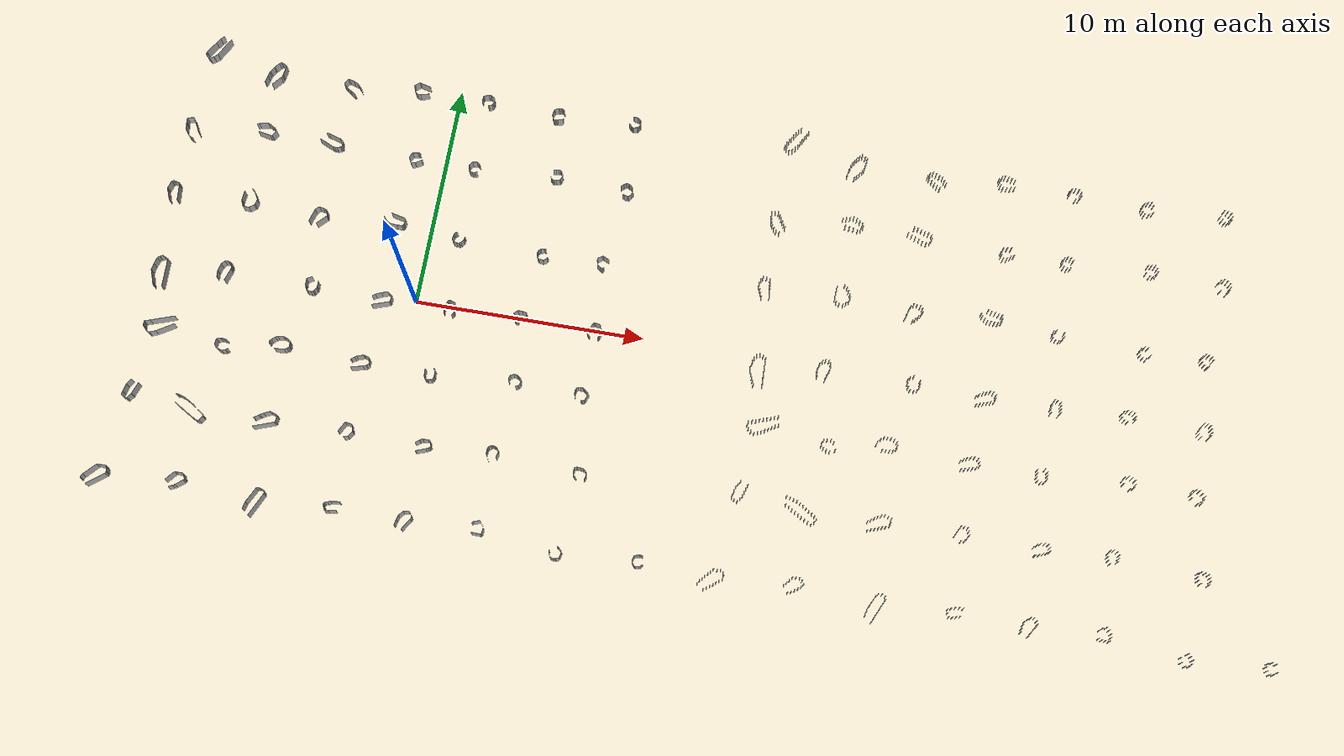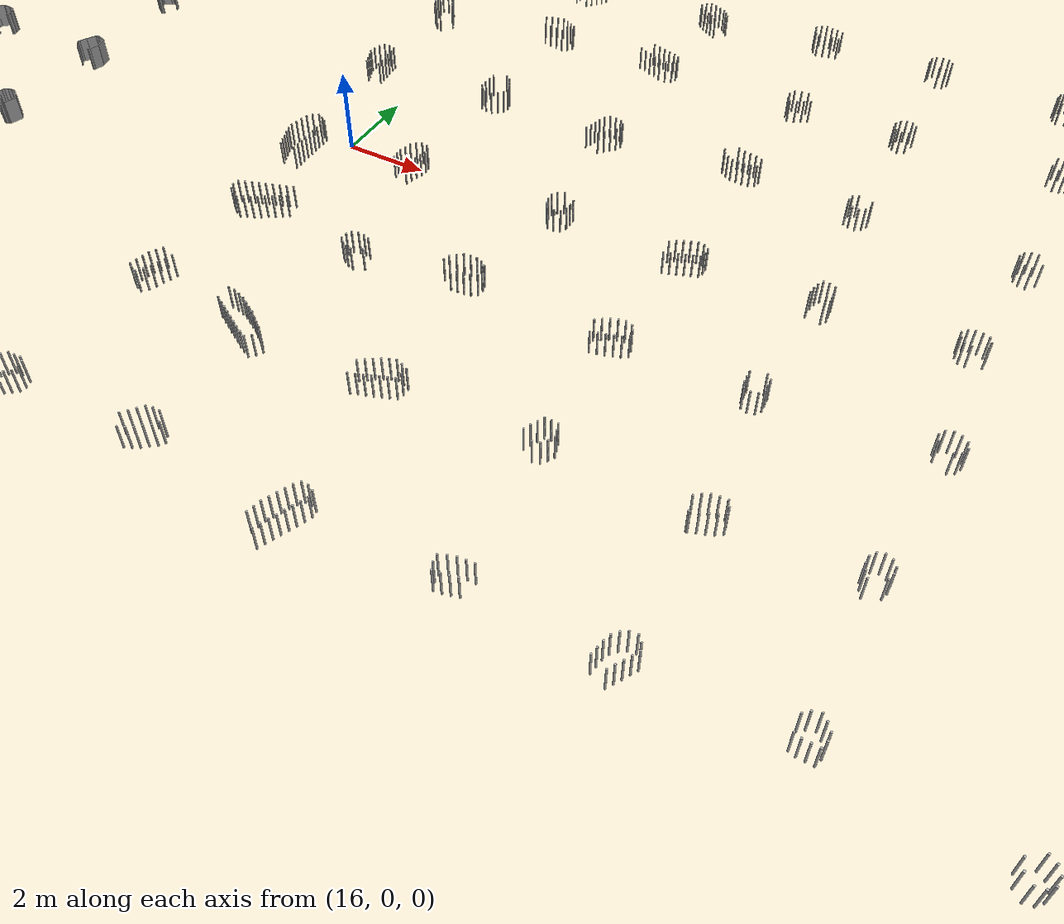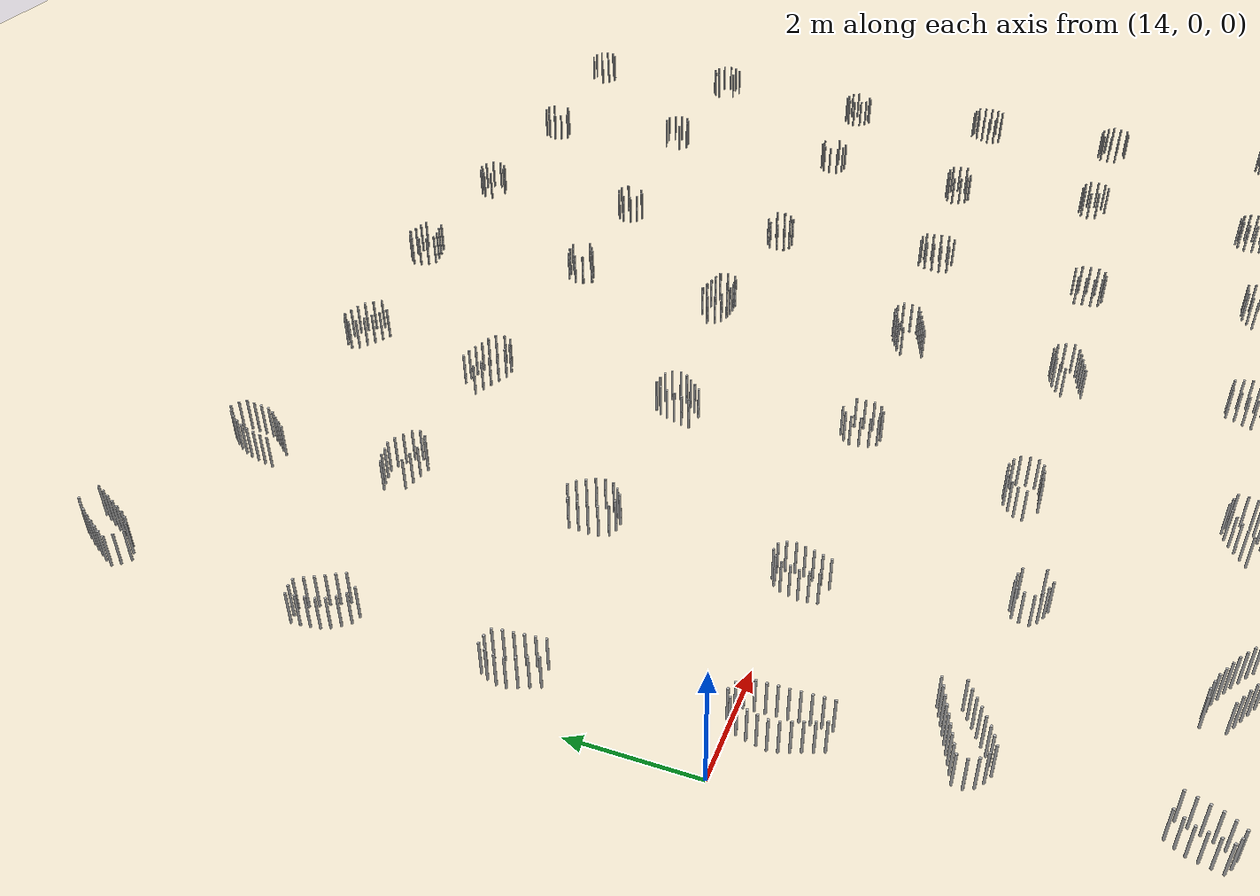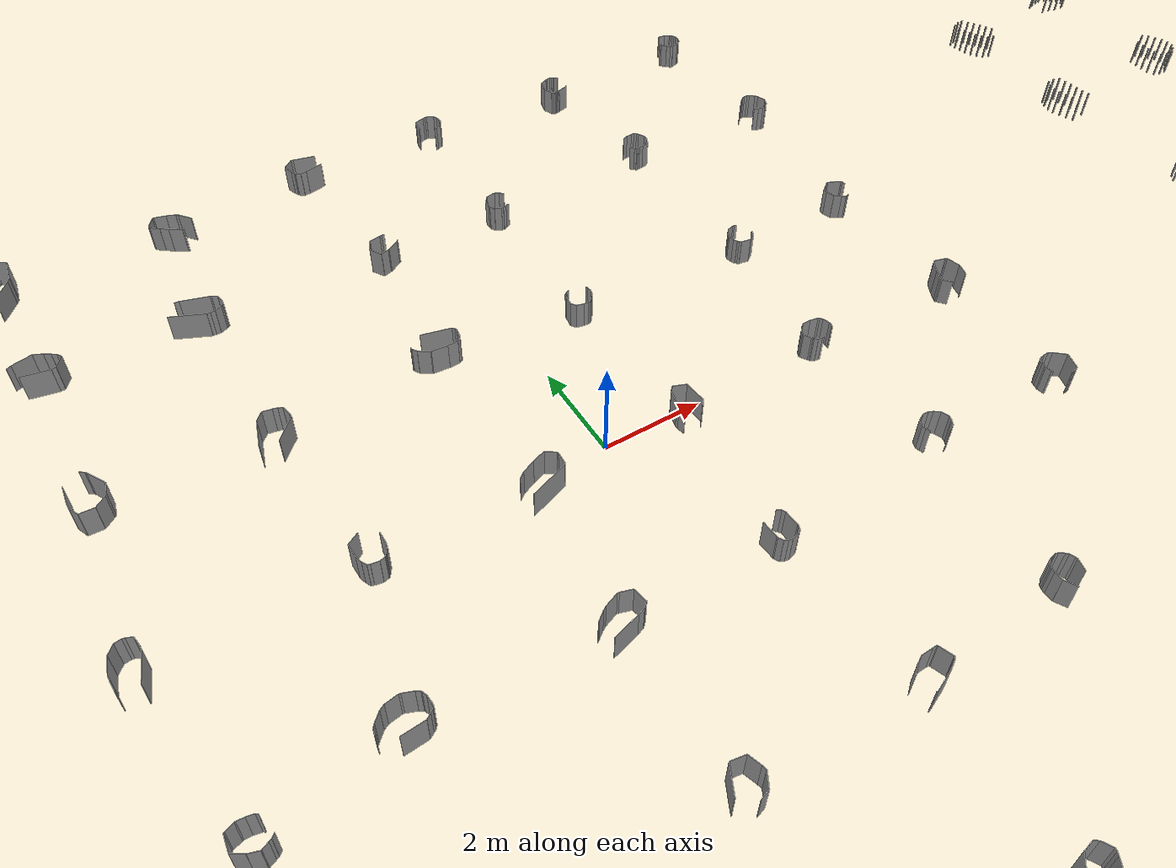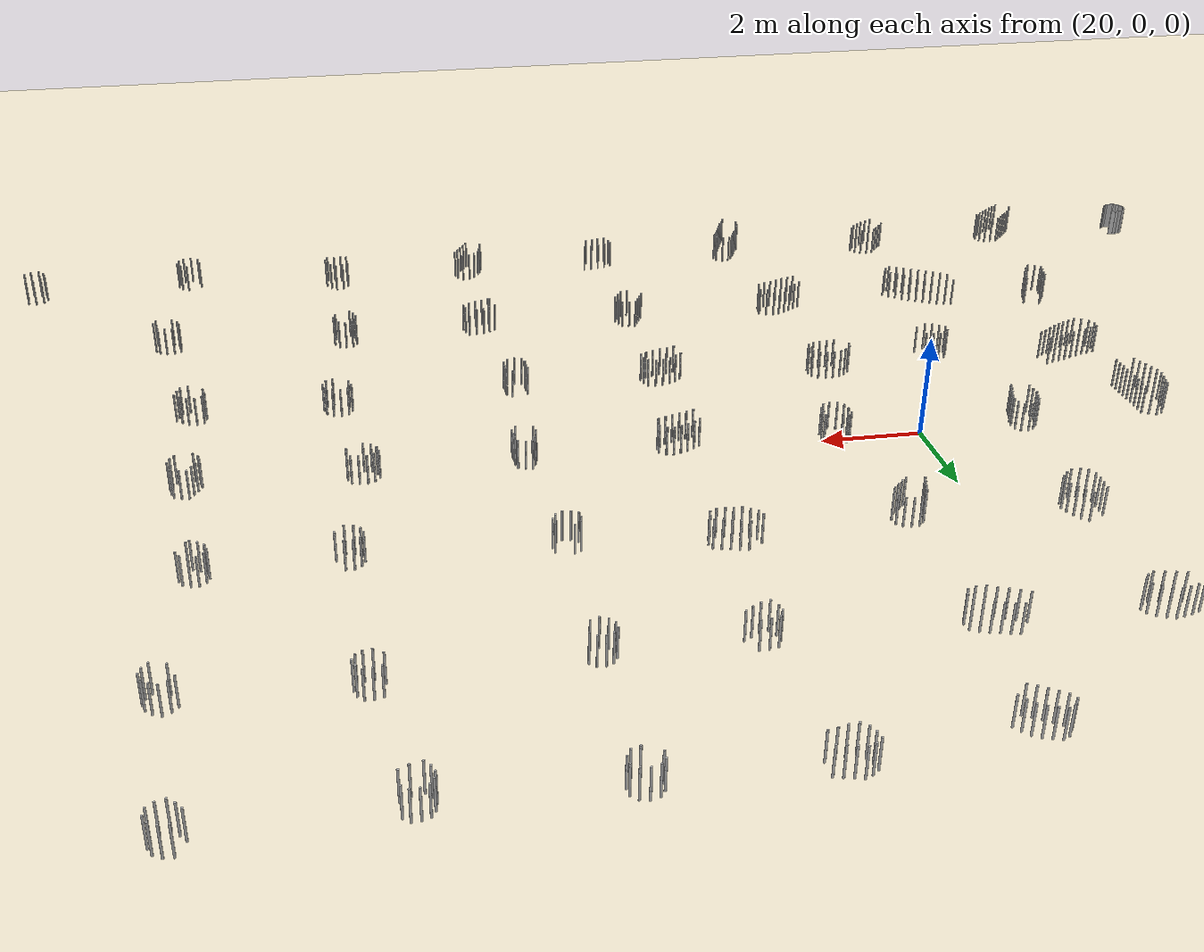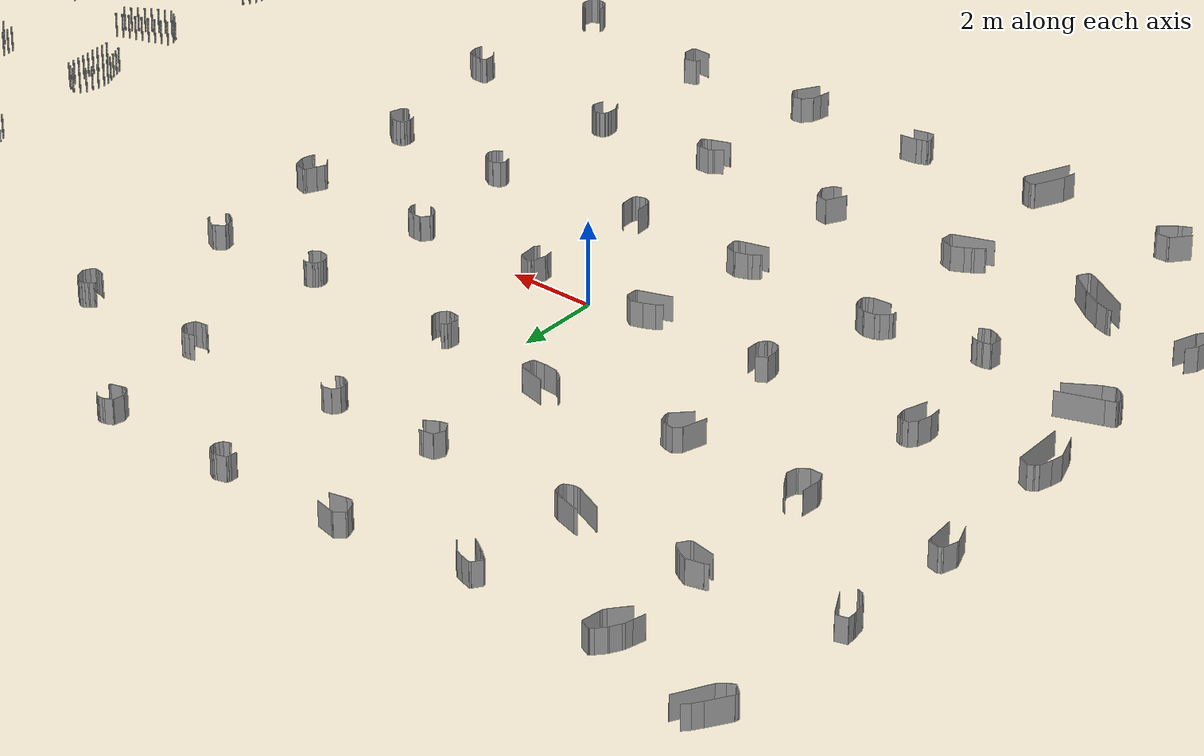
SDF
<?xml version='1.0' encoding='utf-8'?>
<sdf version="1.6">
<world name="all_training">

<!-- Physics (must be before any models) -->
    <physics name="ode" type="ode">
      <max_step_size>0.005</max_step_size>
      <real_time_update_rate>0</real_time_update_rate>
      <ode>
        <solver><type>quick</type><iters>80</iters><sor>1.3</sor></solver>
        <constraints>
          <cfm>1e-5</cfm><erp>0.2</erp>
          <contact_max_correcting_vel>0.2</contact_max_correcting_vel>
          <contact_surface_layer>0.001</contact_surface_layer>
        </constraints>
      </ode>
    </physics>

    <plugin
      filename="ignition-gazebo-physics-system"
      name="gz::sim::systems::Physics">

    </plugin>
    <plugin
      filename="ignition-gazebo-user-commands-system"
      name="gz::sim::systems::UserCommands">
    </plugin>
    <plugin
        filename="libignition-gazebo-scene-broadcaster-system.so"
        name="ignition::gazebo::systems::SceneBroadcaster">
    </plugin>
    <plugin filename="libignition-gazebo-contact-system.so"
        name="ignition::gazebo::systems::Contact">
    </plugin>

    <gravity>0 0 -10</gravity>

    <!--– Optional lightweight GUI -->
         <!-- 3D scene  -->

         <!-- Entity tree  -->

          <!-- World statistics  -->

          <!-- Teleop  -->

           <!-- Inspector  -->

          <!-- Translate / rotate  -->

           <!-- visualize lidar  -->

           <!-- World control  -->

    <model name="ground_plane">
      <static>true</static>
      <link name="link">
        <collision name="collision">
          <geometry>
            <plane>
              <normal>0 0 1</normal>
              <size>500 500</size>
            </plane>
          </geometry>
          <surface>
            <bounce>
              <restitution_coefficient>0.0</restitution_coefficient>
              <threshold>1000.0</threshold>

            </bounce>

          <friction><ode><mu>1e-4</mu><mu2>1e-4</mu2><slip1>0.05</slip1><slip2>0.05</slip2></ode></friction>
          <contact><ode><kp>1e5</kp><kd>1e3</kd><max_vel>0.2</max_vel><min_depth>0.001</min_depth></ode></contact>

          </surface>
        </collision>
        <visual name="visual">
          <geometry>
            <plane>
              <normal>0 0 1</normal>
              <size>100 100</size>
            </plane>
          </geometry>
          <material>
            <ambient>0.94 0.90 0.81 1</ambient>
            <diffuse>0.94 0.90 0.81 1</diffuse>
            <specular>1 1 1 0</specular>
          </material>
        </visual>
      </link>
    </model>

<model name="all_walls_and_cylinders"><static>true</static><link name="single_link"><sensor name="sensor_contact" type="contact"><contact><always_on>1</always_on><update_rate>50</update_rate><collision>cfg1_wall1_col</collision><collision>cfg1_wall2_col</collision><collision>cfg1_wall3_col</collision><collision>cfg1_wall4_col</collision><collision>cfg1_wall5_col</collision><collision>cfg1_wall6_col</collision><collision>cfg1_wall7_col</collision><collision>cfg1_wall8_col</collision><collision>cfg1_wall9_col</collision><collision>cfg1_wall10_col</collision><collision>cfg2_wall1_col</collision><collision>cfg2_wall2_col</collision><collision>cfg2_wall3_col</collision><collision>cfg2_wall4_col</collision><collision>cfg2_wall5_col</collision><collision>cfg2_wall6_col</collision><collision>cfg2_wall7_col</collision><collision>cfg2_wall8_col</collision><collision>cfg3_wall1_col</collision><collision>cfg3_wall2_col</collision><collision>cfg3_wall3_col</collision><collision>cfg3_wall4_col</collision><collision>cfg3_wall5_col</collision><collision>cfg3_wall6_col</collision><collision>cfg3_wall7_col</collision><collision>cfg3_wall8_col</collision><collision>cfg3_wall9_col</collision><collision>cfg3_wall10_col</collision><collision>cfg3_wall11_col</collision><collision>cfg3_wall12_col</collision><collision>cfg4_wall1_col</collision><collision>cfg4_wall2_col</collision><collision>cfg4_wall3_col</collision><collision>cfg4_wall4_col</collision><collision>cfg4_wall5_col</collision><collision>cfg4_wall6_col</collision><collision>cfg4_wall7_col</collision><collision>cfg4_wall8_col</collision><collision>cfg4_wall9_col</collision><collision>cfg4_wall10_col</collision><collision>cfg5_wall1_col</collision><collision>cfg5_wall2_col</collision><collision>cfg5_wall3_col</collision><collision>cfg5_wall4_col</collision><collision>cfg5_wall5_col</collision><collision>cfg5_wall6_col</collision><collision>cfg5_wall7_col</collision><collision>cfg5_wall8_col</collision><collision>cfg6_wall1_col</collision><collision>cfg6_wall2_col</collision><collision>cfg6_wall3_col</collision><collision>cfg6_wall4_col</collision><collision>cfg6_wall5_col</collision><collision>cfg6_wall6_col</collision><collision>cfg6_wall7_col</collision><collision>cfg6_wall8_col</collision><collision>cfg6_wall9_col</collision><collision>cfg6_wall10_col</collision><collision>cfg6_wall11_col</collision><collision>cfg7_wall1_col</collision><collision>cfg7_wall2_col</collision><collision>cfg7_wall3_col</collision><collision>cfg7_wall4_col</collision><collision>cfg7_wall5_col</collision><collision>cfg7_wall6_col</collision><collision>cfg7_wall7_col</collision><collision>cfg7_wall8_col</collision><collision>cfg7_wall9_col</collision><collision>cfg8_wall1_col</collision><collision>cfg8_wall2_col</collision><collision>cfg8_wall3_col</collision><collision>cfg8_wall4_col</collision><collision>cfg8_wall5_col</collision><collision>cfg8_wall6_col</collision><collision>cfg8_wall7_col</collision><collision>cfg8_wall8_col</collision><collision>cfg8_wall9_col</collision><collision>cfg8_wall10_col</collision><collision>cfg8_wall11_col</collision><collision>cfg9_wall1_col</collision><collision>cfg9_wall2_col</collision><collision>cfg9_wall3_col</collision><collision>cfg9_wall4_col</collision><collision>cfg9_wall5_col</collision><collision>cfg9_wall6_col</collision><collision>cfg9_wall7_col</collision><collision>cfg9_wall8_col</collision><collision>cfg9_wall9_col</collision><collision>cfg9_wall10_col</collision><collision>cfg9_wall11_col</collision><collision>cfg9_wall12_col</collision><collision>cfg10_wall1_col</collision><collision>cfg10_wall2_col</collision><collision>cfg10_wall3_col</collision><collision>cfg10_wall4_col</collision><collision>cfg10_wall5_col</collision><collision>cfg10_wall6_col</collision><collision>cfg10_wall7_col</collision><collision>cfg10_wall8_col</collision><collision>cfg10_wall9_col</collision><collision>cfg10_wall10_col</collision><collision>cfg10_wall11_col</collision><collision>cfg10_wall12_col</collision><collision>cfg10_wall13_col</collision><collision>cfg10_wall14_col</collision><collision>cfg11_wall1_col</collision><collision>cfg11_wall2_col</collision><collision>cfg11_wall3_col</collision><collision>cfg11_wall4_col</collision><collision>cfg11_wall5_col</collision><collision>cfg11_wall6_col</collision><collision>cfg11_wall7_col</collision><collision>cfg11_wall8_col</collision><collision>cfg11_wall9_col</collision><collision>cfg11_wall10_col</collision><collision>cfg11_wall11_col</collision><collision>cfg12_wall1_col</collision><collision>cfg12_wall2_col</collision><collision>cfg12_wall3_col</collision><collision>cfg12_wall4_col</collision><collision>cfg12_wall5_col</collision><collision>cfg12_wall6_col</collision><collision>cfg12_wall7_col</collision><collision>cfg12_wall8_col</collision><collision>cfg12_wall9_col</collision><collision>cfg12_wall10_col</collision><collision>cfg12_wall11_col</collision><collision>cfg13_wall1_col</collision><collision>cfg13_wall2_col</collision><collision>cfg13_wall3_col</collision><collision>cfg13_wall4_col</collision><collision>cfg13_wall5_col</collision><collision>cfg13_wall6_col</collision><collision>cfg13_wall7_col</collision><collision>cfg13_wall8_col</collision><collision>cfg13_wall9_col</collision><collision>cfg13_wall10_col</collision><collision>cfg14_wall1_col</collision><collision>cfg14_wall2_col</collision><collision>cfg14_wall3_col</collision><collision>cfg14_wall4_col</collision><collision>cfg14_wall5_col</collision><collision>cfg14_wall6_col</collision><collision>cfg14_wall7_col</collision><collision>cfg14_wall8_col</collision><collision>cfg14_wall9_col</collision><collision>cfg14_wall10_col</collision><collision>cfg14_wall11_col</collision><collision>cfg14_wall12_col</collision><collision>cfg14_wall13_col</collision><collision>cfg14_wall14_col</collision><collision>cfg14_wall15_col</collision><collision>cfg15_wall1_col</collision><collision>cfg15_wall2_col</collision><collision>cfg15_wall3_col</collision><collision>cfg15_wall4_col</collision><collision>cfg15_wall5_col</collision><collision>cfg15_wall6_col</collision><collision>cfg15_wall7_col</collision><collision>cfg15_wall8_col</collision><collision>cfg15_wall9_col</collision><collision>cfg15_wall10_col</collision><collision>cfg16_wall1_col</collision><collision>cfg16_wall2_col</collision><collision>cfg16_wall3_col</collision><collision>cfg16_wall4_col</collision><collision>cfg16_wall5_col</collision><collision>cfg16_wall6_col</collision><collision>cfg16_wall7_col</collision><collision>cfg16_wall8_col</collision><collision>cfg16_wall9_col</collision><collision>cfg16_wall10_col</collision><collision>cfg16_wall11_col</collision><collision>cfg17_wall1_col</collision><collision>cfg17_wall2_col</collision><collision>cfg17_wall3_col</collision><collision>cfg17_wall4_col</collision><collision>cfg17_wall5_col</collision><collision>cfg17_wall6_col</collision><collision>cfg17_wall7_col</collision><collision>cfg17_wall8_col</collision><collision>cfg17_wall9_col</collision><collision>cfg17_wall10_col</collision><collision>cfg17_wall11_col</collision><collision>cfg17_wall12_col</collision><collision>cfg17_wall13_col</collision><collision>cfg17_wall14_col</collision><collision>cfg17_wall15_col</collision><collision>cfg17_wall16_col</collision><collision>cfg18_wall1_col</collision><collision>cfg18_wall2_col</collision><collision>cfg18_wall3_col</collision><collision>cfg18_wall4_col</collision><collision>cfg18_wall5_col</collision><collision>cfg18_wall6_col</collision><collision>cfg18_wall7_col</collision><collision>cfg18_wall8_col</collision><collision>cfg18_wall9_col</collision><collision>cfg18_wall10_col</collision><collision>cfg18_wall11_col</collision><collision>cfg18_wall12_col</collision><collision>cfg19_wall1_col</collision><collision>cfg19_wall2_col</collision><collision>cfg19_wall3_col</collision><collision>cfg19_wall4_col</collision><collision>cfg19_wall5_col</collision><collision>cfg19_wall6_col</collision><collision>cfg19_wall7_col</collision><collision>cfg19_wall8_col</collision><collision>cfg19_wall9_col</collision><collision>cfg20_wall1_col</collision><collision>cfg20_wall2_col</collision><collision>cfg20_wall3_col</collision><collision>cfg20_wall4_col</collision><collision>cfg20_wall5_col</collision><collision>cfg20_wall6_col</collision><collision>cfg20_wall7_col</collision><collision>cfg20_wall8_col</collision><collision>cfg20_wall9_col</collision><collision>cfg20_wall10_col</collision><collision>cfg20_wall11_col</collision><collision>cfg20_wall12_col</collision><collision>cfg21_wall1_col</collision><collision>cfg21_wall2_col</collision><collision>cfg21_wall3_col</collision><collision>cfg21_wall4_col</collision><collision>cfg21_wall5_col</collision><collision>cfg21_wall6_col</collision><collision>cfg21_wall7_col</collision><collision>cfg21_wall8_col</collision><collision>cfg21_wall9_col</collision><collision>cfg21_wall10_col</collision><collision>cfg21_wall11_col</collision><collision>cfg21_wall12_col</collision><collision>cfg22_wall1_col</collision><collision>cfg22_wall2_col</collision><collision>cfg22_wall3_col</collision><collision>cfg22_wall4_col</collision><collision>cfg22_wall5_col</collision><collision>cfg22_wall6_col</collision><collision>cfg22_wall7_col</collision><collision>cfg22_wall8_col</collision><collision>cfg22_wall9_col</collision><collision>cfg22_wall10_col</collision><collision>cfg22_wall11_col</collision><collision>cfg23_wall1_col</collision><collision>cfg23_wall2_col</collision><collision>cfg23_wall3_col</collision><collision>cfg23_wall4_col</collision><collision>cfg23_wall5_col</collision><collision>cfg23_wall6_col</collision><collision>cfg23_wall7_col</collision><collision>cfg24_wall1_col</collision><collision>cfg24_wall2_col</collision><collision>cfg24_wall3_col</collision><collision>cfg24_wall4_col</collision><collision>cfg24_wall5_col</collision><collision>cfg24_wall6_col</collision><collision>cfg24_wall7_col</collision><collision>cfg24_wall8_col</collision><collision>cfg24_wall9_col</collision><collision>cfg24_wall10_col</collision><collision>cfg24_wall11_col</collision><collision>cfg25_wall1_col</collision><collision>cfg25_wall2_col</collision><collision>cfg25_wall3_col</collision><collision>cfg25_wall4_col</collision><collision>cfg25_wall5_col</collision><collision>cfg25_wall6_col</collision><collision>cfg25_wall7_col</collision><collision>cfg25_wall8_col</collision><collision>cfg26_wall1_col</collision><collision>cfg26_wall2_col</collision><collision>cfg26_wall3_col</collision><collision>cfg26_wall4_col</collision><collision>cfg26_wall5_col</collision><collision>cfg26_wall6_col</collision><collision>cfg26_wall7_col</collision><collision>cfg26_wall8_col</collision><collision>cfg26_wall9_col</collision><collision>cfg26_wall10_col</collision><collision>cfg26_wall11_col</collision><collision>cfg26_wall12_col</collision><collision>cfg26_wall13_col</collision><collision>cfg26_wall14_col</collision><collision>cfg27_wall1_col</collision><collision>cfg27_wall2_col</collision><collision>cfg27_wall3_col</collision><collision>cfg27_wall4_col</collision><collision>cfg27_wall5_col</collision><collision>cfg27_wall6_col</collision><collision>cfg27_wall7_col</collision><collision>cfg27_wall8_col</collision><collision>cfg27_wall9_col</collision><collision>cfg27_wall10_col</collision><collision>cfg28_wall1_col</collision><collision>cfg28_wall2_col</collision><collision>cfg28_wall3_col</collision><collision>cfg28_wall4_col</collision><collision>cfg28_wall5_col</collision><collision>cfg28_wall6_col</collision><collision>cfg28_wall7_col</collision><collision>cfg28_wall8_col</collision><collision>cfg28_wall9_col</collision><collision>cfg28_wall10_col</collision><collision>cfg28_wall11_col</collision><collision>cfg29_wall1_col</collision><collision>cfg29_wall2_col</collision><collision>cfg29_wall3_col</collision><collision>cfg29_wall4_col</collision><collision>cfg29_wall5_col</collision><collision>cfg29_wall6_col</collision><collision>cfg29_wall7_col</collision><collision>cfg29_wall8_col</collision><collision>cfg29_wall9_col</collision><collision>cfg29_wall10_col</collision><collision>cfg29_wall11_col</collision><collision>cfg30_wall1_col</collision><collision>cfg30_wall2_col</collision><collision>cfg30_wall3_col</collision><collision>cfg30_wall4_col</collision><collision>cfg30_wall5_col</collision><collision>cfg30_wall6_col</collision><collision>cfg30_wall7_col</collision><collision>cfg30_wall8_col</collision><collision>cfg30_wall9_col</collision><collision>cfg30_wall10_col</collision><collision>cfg30_wall11_col</collision><collision>cfg30_wall12_col</collision><collision>cfg30_wall13_col</collision><collision>cfg30_wall14_col</collision><collision>cfg31_wall1_col</collision><collision>cfg31_wall2_col</collision><collision>cfg31_wall3_col</collision><collision>cfg31_wall4_col</collision><collision>cfg31_wall5_col</collision><collision>cfg31_wall6_col</collision><collision>cfg31_wall7_col</collision><collision>cfg31_wall8_col</collision><collision>cfg31_wall9_col</collision><collision>cfg31_wall10_col</collision><collision>cfg31_wall11_col</collision><collision>cfg31_wall12_col</collision><collision>cfg32_wall1_col</collision><collision>cfg32_wall2_col</collision><collision>cfg32_wall3_col</collision><collision>cfg32_wall4_col</collision><collision>cfg32_wall5_col</collision><collision>cfg32_wall6_col</collision><collision>cfg32_wall7_col</collision><collision>cfg32_wall8_col</collision><collision>cfg32_wall9_col</collision><collision>cfg32_wall10_col</collision><collision>cfg33_wall1_col</collision><collision>cfg33_wall2_col</collision><collision>cfg33_wall3_col</collision><collision>cfg33_wall4_col</collision><collision>cfg33_wall5_col</collision><collision>cfg33_wall6_col</collision><collision>cfg33_wall7_col</collision><collision>cfg33_wall8_col</collision><collision>cfg33_wall9_col</collision><collision>cfg33_wall10_col</collision><collision>cfg33_wall11_col</collision><collision>cfg33_wall12_col</collision><collision>cfg33_wall13_col</collision><collision>cfg33_wall14_col</collision><collision>cfg34_wall1_col</collision><collision>cfg34_wall2_col</collision><collision>cfg34_wall3_col</collision><collision>cfg34_wall4_col</collision><collision>cfg34_wall5_col</collision><collision>cfg34_wall6_col</collision><collision>cfg34_wall7_col</collision><collision>cfg34_wall8_col</collision><collision>cfg34_wall9_col</collision><collision>cfg34_wall10_col</collision><collision>cfg34_wall11_col</collision><collision>cfg35_wall1_col</collision><collision>cfg35_wall2_col</collision><collision>cfg35_wall3_col</collision><collision>cfg35_wall4_col</collision><collision>cfg35_wall5_col</collision><collision>cfg35_wall6_col</collision><collision>cfg35_wall7_col</collision><collision>cfg35_wall8_col</collision><collision>cfg35_wall9_col</collision><collision>cfg35_wall10_col</collision><collision>cfg35_wall11_col</collision><collision>cfg35_wall12_col</collision><collision>cfg35_wall13_col</collision><collision>cfg35_wall14_col</collision><collision>cfg35_wall15_col</collision><collision>cfg36_wall1_col</collision><collision>cfg36_wall2_col</collision><collision>cfg36_wall3_col</collision><collision>cfg36_wall4_col</collision><collision>cfg36_wall5_col</collision><collision>cfg36_wall6_col</collision><collision>cfg36_wall7_col</collision><collision>cfg36_wall8_col</collision><collision>cfg36_wall9_col</collision><collision>cfg37_wall1_col</collision><collision>cfg37_wall2_col</collision><collision>cfg37_wall3_col</collision><collision>cfg37_wall4_col</collision><collision>cfg37_wall5_col</collision><collision>cfg37_wall6_col</collision><collision>cfg37_wall7_col</collision><collision>cfg37_wall8_col</collision><collision>cfg37_wall9_col</collision><collision>cfg37_wall10_col</collision><collision>cfg37_wall11_col</collision><collision>cfg37_wall12_col</collision><collision>cfg37_wall13_col</collision><collision>cfg37_wall14_col</collision><collision>cfg37_wall15_col</collision><collision>cfg37_wall16_col</collision><collision>cfg38_wall1_col</collision><collision>cfg38_wall2_col</collision><collision>cfg38_wall3_col</collision><collision>cfg38_wall4_col</collision><collision>cfg38_wall5_col</collision><collision>cfg38_wall6_col</collision><collision>cfg38_wall7_col</collision><collision>cfg38_wall8_col</collision><collision>cfg38_wall9_col</collision><collision>cfg38_wall10_col</collision><collision>cfg38_wall11_col</collision><collision>cfg38_wall12_col</collision><collision>cfg39_wall1_col</collision><collision>cfg39_wall2_col</collision><collision>cfg39_wall3_col</collision><collision>cfg39_wall4_col</collision><collision>cfg39_wall5_col</collision><collision>cfg39_wall6_col</collision><collision>cfg39_wall7_col</collision><collision>cfg39_wall8_col</collision><collision>cfg39_wall9_col</collision><collision>cfg39_wall10_col</collision><collision>cfg39_wall11_col</collision><collision>cfg39_wall12_col</collision><collision>cfg39_wall13_col</collision><collision>cfg39_wall14_col</collision><collision>cfg39_wall15_col</collision><collision>cfg39_wall16_col</collision><collision>cfg39_wall17_col</collision><collision>cfg40_wall1_col</collision><collision>cfg40_wall2_col</collision><collision>cfg40_wall3_col</collision><collision>cfg40_wall4_col</collision><collision>cfg40_wall5_col</collision><collision>cfg40_wall6_col</collision><collision>cfg40_wall7_col</collision><collision>cfg40_wall8_col</collision><collision>cfg40_wall9_col</collision><collision>cfg40_wall10_col</collision><collision>cfg40_wall11_col</collision><collision>cfg40_wall12_col</collision><collision>cfg40_wall13_col</collision><collision>cfg40_wall14_col</collision><collision>cfg41_wall1_col</collision><collision>cfg41_wall2_col</collision><collision>cfg41_wall3_col</collision><collision>cfg41_wall4_col</collision><collision>cfg41_wall5_col</collision><collision>cfg41_wall6_col</collision><collision>cfg41_wall7_col</collision><collision>cfg41_wall8_col</collision><collision>cfg41_wall9_col</collision><collision>cfg41_wall10_col</collision><collision>cfg41_wall11_col</collision><collision>cfg41_wall12_col</collision><collision>cfg41_wall13_col</collision><collision>cfg41_wall14_col</collision><collision>cfg41_wall15_col</collision><collision>cfg42_wall1_col</collision><collision>cfg42_wall2_col</collision><collision>cfg42_wall3_col</collision><collision>cfg42_wall4_col</collision><collision>cfg42_wall5_col</collision><collision>cfg42_wall6_col</collision><collision>cfg42_wall7_col</collision><collision>cfg42_wall8_col</collision><collision>cfg42_wall9_col</collision><collision>cfg42_wall10_col</collision><collision>cfg42_wall11_col</collision><collision>cfg42_wall12_col</collision><collision>cfg42_wall13_col</collision><collision>cfg42_wall14_col</collision><collision>cfg42_wall15_col</collision><collision>cfg42_wall16_col</collision><collision>cfg42_wall17_col</collision><collision>cfg42_wall18_col</collision><collision>cfg42_wall19_col</collision><collision>cfg43_wall1_col</collision><collision>cfg43_wall2_col</collision><collision>cfg43_wall3_col</collision><collision>cfg43_wall4_col</collision><collision>cfg43_wall5_col</collision><collision>cfg43_wall6_col</collision><collision>cfg43_wall7_col</collision><collision>cfg43_wall8_col</collision><collision>cfg43_wall9_col</collision><collision>cfg43_wall10_col</collision><collision>cfg43_wall11_col</collision><collision>cfg43_wall12_col</collision><collision>cfg43_wall13_col</collision><collision>cfg43_wall14_col</collision><collision>cfg43_wall15_col</collision><collision>cfg43_wall16_col</collision><collision>cfg44_wall1_col</collision><collision>cfg44_wall2_col</collision><collision>cfg44_wall3_col</collision><collision>cfg44_wall4_col</collision><collision>cfg44_wall5_col</collision><collision>cfg44_wall6_col</collision><collision>cfg44_wall7_col</collision><collision>cfg44_wall8_col</collision><collision>cfg44_wall9_col</collision><collision>cfg44_wall10_col</collision><collision>cfg44_wall11_col</collision><collision>cfg45_wall1_col</collision><collision>cfg45_wall2_col</collision><collision>cfg45_wall3_col</collision><collision>cfg45_wall4_col</collision><collision>cfg45_wall5_col</collision><collision>cfg45_wall6_col</collision><collision>cfg45_wall7_col</collision><collision>cfg45_wall8_col</collision><collision>cfg45_wall9_col</collision><collision>cfg45_wall10_col</collision><collision>cfg45_wall11_col</collision><collision>cfg45_wall12_col</collision><collision>cfg45_wall13_col</collision><collision>cfg45_wall14_col</collision><collision>cfg45_wall15_col</collision><collision>cfg45_wall16_col</collision><collision>cfg46_wall1_col</collision><collision>cfg46_wall2_col</collision><collision>cfg46_wall3_col</collision><collision>cfg46_wall4_col</collision><collision>cfg46_wall5_col</collision><collision>cfg46_wall6_col</collision><collision>cfg46_wall7_col</collision><collision>cfg46_wall8_col</collision><collision>cfg46_wall9_col</collision><collision>cfg46_wall10_col</collision><collision>cfg46_wall11_col</collision><collision>cfg46_wall12_col</collision><collision>cfg46_wall13_col</collision><collision>cfg46_wall14_col</collision><collision>cfg47_wall1_col</collision><collision>cfg47_wall2_col</collision><collision>cfg47_wall3_col</collision><collision>cfg47_wall4_col</collision><collision>cfg47_wall5_col</collision><collision>cfg47_wall6_col</collision><collision>cfg47_wall7_col</collision><collision>cfg47_wall8_col</collision><collision>cfg47_wall9_col</collision><collision>cfg47_wall10_col</collision><collision>cfg47_wall11_col</collision><collision>cfg47_wall12_col</collision><collision>cfg48_wall1_col</collision><collision>cfg48_wall2_col</collision><collision>cfg48_wall3_col</collision><collision>cfg48_wall4_col</collision><collision>cfg48_wall5_col</collision><collision>cfg48_wall6_col</collision><collision>cfg48_wall7_col</collision><collision>cfg48_wall8_col</collision><collision>cfg48_wall9_col</collision><collision>cfg48_wall10_col</collision><collision>cfg48_wall11_col</collision><collision>cfg48_wall12_col</collision><collision>cfg48_wall13_col</collision><collision>cfg48_wall14_col</collision><collision>cfg48_wall15_col</collision><collision>cfg48_wall16_col</collision><collision>cfg48_wall17_col</collision><collision>cfg48_wall18_col</collision><collision>cfg49_wall1_col</collision><collision>cfg49_wall2_col</collision><collision>cfg49_wall3_col</collision><collision>cfg49_wall4_col</collision><collision>cfg49_wall5_col</collision><collision>cfg49_wall6_col</collision><collision>cfg49_wall7_col</collision><collision>cfg49_wall8_col</collision><collision>cfg49_wall9_col</collision><collision>cfg49_wall10_col</collision><collision>cfg49_wall11_col</collision><collision>cfg49_wall12_col</collision><collision>cfg49_wall13_col</collision><collision>cfg49_wall14_col</collision><collision>cfg49_wall15_col</collision><collision>cfg49_wall16_col</collision><collision>cfg49_wall17_col</collision><collision>cfg49_wall18_col</collision><collision>cfg50_wall1_col</collision><collision>cfg50_wall2_col</collision><collision>cfg50_wall3_col</collision><collision>cfg50_wall4_col</collision><collision>cfg50_wall5_col</collision><collision>cfg50_wall6_col</collision><collision>cfg50_wall7_col</collision><collision>cfg50_wall8_col</collision><collision>cfg50_wall9_col</collision><collision>cfg50_wall10_col</collision><collision>cfg50_wall11_col</collision><collision>cfg50_wall12_col</collision><collision>cfg50_wall13_col</collision><collision>cfg50_wall14_col</collision><collision>cfg50_wall15_col</collision><collision>cfg50_wall16_col</collision><collision>cfg51_cyl1_col</collision><collision>cfg51_cyl2_col</collision><collision>cfg51_cyl3_col</collision><collision>cfg51_cyl4_col</collision><collision>cfg51_cyl5_col</collision><collision>cfg51_cyl6_col</collision><collision>cfg51_cyl7_col</collision><collision>cfg51_cyl8_col</collision><collision>cfg51_cyl9_col</collision><collision>cfg51_cyl10_col</collision><collision>cfg51_cyl11_col</collision><collision>cfg51_cyl12_col</collision><collision>cfg51_cyl13_col</collision><collision>cfg51_cyl14_col</collision><collision>cfg51_cyl15_col</collision><collision>cfg51_cyl16_col</collision><collision>cfg51_cyl17_col</collision><collision>cfg51_cyl18_col</collision><collision>cfg52_cyl1_col</collision><collision>cfg52_cyl2_col</collision><collision>cfg52_cyl3_col</collision><collision>cfg52_cyl4_col</collision><collision>cfg52_cyl5_col</collision><collision>cfg52_cyl6_col</collision><collision>cfg52_cyl7_col</collision><collision>cfg52_cyl8_col</collision><collision>cfg52_cyl9_col</collision><collision>cfg52_cyl10_col</collision><collision>cfg52_cyl11_col</collision><collision>cfg52_cyl12_col</collision><collision>cfg52_cyl13_col</collision><collision>cfg52_cyl14_col</collision><collision>cfg53_cyl1_col</collision><collision>cfg53_cyl2_col</collision><collision>cfg53_cyl3_col</collision><collision>cfg53_cyl4_col</collision><collision>cfg53_cyl5_col</collision><collision>cfg53_cyl6_col</collision><collision>cfg53_cyl7_col</collision><collision>cfg53_cyl8_col</collision><collision>cfg53_cyl9_col</collision><collision>cfg53_cyl10_col</collision><collision>cfg53_cyl11_col</collision><collision>cfg53_cyl12_col</collision><collision>cfg53_cyl13_col</collision><collision>cfg53_cyl14_col</collision><collision>cfg53_cyl15_col</collision><collision>cfg53_cyl16_col</collision><collision>cfg53_cyl17_col</collision><collision>cfg53_cyl18_col</collision><collision>cfg53_cyl19_col</collision><collision>cfg53_cyl20_col</collision><collision>cfg53_cyl21_col</collision><collision>cfg54_cyl1_col</collision><collision>cfg54_cyl2_col</collision><collision>cfg54_cyl3_col</collision><collision>cfg54_cyl4_col</collision><collision>cfg54_cyl5_col</collision><collision>cfg54_cyl6_col</collision><collision>cfg54_cyl7_col</collision><collision>cfg54_cyl8_col</collision><collision>cfg54_cyl9_col</collision><collision>cfg54_cyl10_col</collision><collision>cfg54_cyl11_col</collision><collision>cfg54_cyl12_col</collision><collision>cfg54_cyl13_col</collision><collision>cfg54_cyl14_col</collision><collision>cfg54_cyl15_col</collision><collision>cfg54_cyl16_col</collision><collision>cfg54_cyl17_col</collision><collision>cfg54_cyl18_col</collision><collision>cfg54_cyl19_col</collision><collision>cfg54_cyl20_col</collision><collision>cfg54_cyl21_col</collision><collision>cfg55_cyl1_col</collision><collision>cfg55_cyl2_col</collision><collision>cfg55_cyl3_col</collision><collision>cfg55_cyl4_col</collision><collision>cfg55_cyl5_col</collision><collision>cfg55_cyl6_col</collision><collision>cfg55_cyl7_col</collision><collision>cfg55_cyl8_col</collision><collision>cfg55_cyl9_col</collision><collision>cfg55_cyl10_col</collision><collision>cfg55_cyl11_col</collision><collision>cfg55_cyl12_col</collision><collision>cfg55_cyl13_col</collision><collision>cfg55_cyl14_col</collision><collision>cfg56_cyl1_col</collision><collision>cfg56_cyl2_col</collision><collision>cfg56_cyl3_col</collision><collision>cfg56_cyl4_col</collision><collision>cfg56_cyl5_col</collision><collision>cfg56_cyl6_col</collision><collision>cfg56_cyl7_col</collision><collision>cfg56_cyl8_col</collision><collision>cfg56_cyl9_col</collision><collision>cfg56_cyl10_col</collision><collision>cfg56_cyl11_col</collision><collision>cfg56_cyl12_col</collision><collision>cfg56_cyl13_col</collision><collision>cfg56_cyl14_col</collision><collision>cfg56_cyl15_col</collision><collision>cfg57_cyl1_col</collision><collision>cfg57_cyl2_col</collision><collision>cfg57_cyl3_col</collision><collision>cfg57_cyl4_col</collision><collision>cfg57_cyl5_col</collision><collision>cfg57_cyl6_col</collision><collision>cfg57_cyl7_col</collision><collision>cfg57_cyl8_col</collision><collision>cfg57_cyl9_col</collision><collision>cfg57_cyl10_col</collision><collision>cfg57_cyl11_col</collision><collision>cfg57_cyl12_col</collision><collision>cfg57_cyl13_col</collision><collision>cfg57_cyl14_col</collision><collision>cfg57_cyl15_col</collision><collision>cfg57_cyl16_col</collision><collision>cfg57_cyl17_col</collision><collision>cfg57_cyl18_col</collision><collision>cfg57_cyl19_col</collision><collision>cfg58_cyl1_col</collision><collision>cfg58_cyl2_col</collision><collision>cfg58_cyl3_col</collision><collision>cfg58_cyl4_col</collision><collision>cfg58_cyl5_col</collision><collision>cfg58_cyl6_col</collision><collision>cfg58_cyl7_col</collision><collision>cfg58_cyl8_col</collision><collision>cfg58_cyl9_col</collision><collision>cfg58_cyl10_col</collision><collision>cfg58_cyl11_col</collision><collision>cfg58_cyl12_col</collision><collision>cfg58_cyl13_col</collision><collision>cfg59_cyl1_col</collision><collision>cfg59_cyl2_col</collision><collision>cfg59_cyl3_col</collision><collision>cfg59_cyl4_col</collision><collision>cfg59_cyl5_col</collision><collision>cfg59_cyl6_col</collision><collision>cfg59_cyl7_col</collision><collision>cfg59_cyl8_col</collision><collision>cfg59_cyl9_col</collision><collision>cfg59_cyl10_col</collision><collision>cfg59_cyl11_col</collision><collision>cfg59_cyl12_col</collision><collision>cfg59_cyl13_col</collision><collision>cfg59_cyl14_col</collision><collision>cfg59_cyl15_col</collision><collision>cfg59_cyl16_col</collision><collision>cfg59_cyl17_col</collision><collision>cfg59_cyl18_col</collision><collision>cfg59_cyl19_col</collision><collision>cfg59_cyl20_col</collision><collision>cfg59_cyl21_col</collision><collision>cfg59_cyl22_col</collision><collision>cfg60_cyl1_col</collision><collision>cfg60_cyl2_col</collision><collision>cfg60_cyl3_col</collision><collision>cfg60_cyl4_col</collision><collision>cfg60_cyl5_col</collision><collision>cfg60_cyl6_col</collision><collision>cfg60_cyl7_col</collision><collision>cfg60_cyl8_col</collision><collision>cfg60_cyl9_col</collision><collision>cfg60_cyl10_col</collision><collision>cfg60_cyl11_col</collision><collision>cfg61_cyl1_col</collision><collision>cfg61_cyl2_col</collision><collision>cfg61_cyl3_col</collision><collision>cfg61_cyl4_col</collision><collision>cfg61_cyl5_col</collision><collision>cfg61_cyl6_col</collision><collision>cfg61_cyl7_col</collision><collision>cfg61_cyl8_col</collision><collision>cfg61_cyl9_col</collision><collision>cfg61_cyl10_col</collision><collision>cfg61_cyl11_col</collision><collision>cfg61_cyl12_col</collision><collision>cfg61_cyl13_col</collision><collision>cfg61_cyl14_col</collision><collision>cfg62_cyl1_col</collision><collision>cfg62_cyl2_col</collision><collision>cfg62_cyl3_col</collision><collision>cfg62_cyl4_col</collision><collision>cfg62_cyl5_col</collision><collision>cfg62_cyl6_col</collision><collision>cfg62_cyl7_col</collision><collision>cfg62_cyl8_col</collision><collision>cfg62_cyl9_col</collision><collision>cfg62_cyl10_col</collision><collision>cfg62_cyl11_col</collision><collision>cfg62_cyl12_col</collision><collision>cfg62_cyl13_col</collision><collision>cfg62_cyl14_col</collision><collision>cfg62_cyl15_col</collision><collision>cfg63_cyl1_col</collision><collision>cfg63_cyl2_col</collision><collision>cfg63_cyl3_col</collision><collision>cfg63_cyl4_col</collision><collision>cfg63_cyl5_col</collision><collision>cfg63_cyl6_col</collision><collision>cfg63_cyl7_col</collision><collision>cfg63_cyl8_col</collision><collision>cfg63_cyl9_col</collision><collision>cfg63_cyl10_col</collision><collision>cfg63_cyl11_col</collision><collision>cfg63_cyl12_col</collision><collision>cfg63_cyl13_col</collision><collision>cfg63_cyl14_col</collision><collision>cfg64_cyl1_col</collision><collision>cfg64_cyl2_col</collision><collision>cfg64_cyl3_col</collision><collision>cfg64_cyl4_col</collision><collision>cfg64_cyl5_col</collision><collision>cfg64_cyl6_col</collision><collision>cfg64_cyl7_col</collision><collision>cfg64_cyl8_col</collision><collision>cfg64_cyl9_col</collision><collision>cfg64_cyl10_col</collision><collision>cfg64_cyl11_col</collision><collision>cfg64_cyl12_col</collision><collision>cfg64_cyl13_col</collision><collision>cfg64_cyl14_col</collision><collision>cfg64_cyl15_col</collision><collision>cfg64_cyl16_col</collision><collision>cfg64_cyl17_col</collision><collision>cfg64_cyl18_col</collision><collision>cfg65_cyl1_col</collision><collision>cfg65_cyl2_col</collision><collision>cfg65_cyl3_col</collision><collision>cfg65_cyl4_col</collision><collision>cfg65_cyl5_col</collision><collision>cfg65_cyl6_col</collision><collision>cfg65_cyl7_col</collision><collision>cfg65_cyl8_col</collision><collision>cfg65_cyl9_col</collision><collision>cfg65_cyl10_col</collision><collision>cfg65_cyl11_col</collision><collision>cfg65_cyl12_col</collision><collision>cfg65_cyl13_col</collision><collision>cfg65_cyl14_col</collision><collision>cfg65_cyl15_col</collision><collision>cfg65_cyl16_col</collision><collision>cfg65_cyl17_col</collision><collision>cfg65_cyl18_col</collision><collision>cfg66_cyl1_col</collision><collision>cfg66_cyl2_col</collision><collision>cfg66_cyl3_col</collision><collision>cfg66_cyl4_col</collision><collision>cfg66_cyl5_col</collision><collision>cfg66_cyl6_col</collision><collision>cfg66_cyl7_col</collision><collision>cfg66_cyl8_col</collision><collision>cfg66_cyl9_col</collision><collision>cfg66_cyl10_col</collision><collision>cfg66_cyl11_col</collision><collision>cfg66_cyl12_col</collision><collision>cfg66_cyl13_col</collision><collision>cfg66_cyl14_col</collision><collision>cfg66_cyl15_col</collision><collision>cfg66_cyl16_col</collision><collision>cfg67_cyl1_col</collision><collision>cfg67_cyl2_col</collision><collision>cfg67_cyl3_col</collision><collision>cfg67_cyl4_col</collision><collision>cfg67_cyl5_col</collision><collision>cfg67_cyl6_col</collision><collision>cfg67_cyl7_col</collision><collision>cfg67_cyl8_col</collision><collision>cfg67_cyl9_col</collision><collision>cfg67_cyl10_col</collision><collision>cfg67_cyl11_col</collision><collision>cfg67_cyl12_col</collision><collision>cfg67_cyl13_col</collision><collision>cfg67_cyl14_col</collision><collision>cfg68_cyl1_col</collision><collision>cfg68_cyl2_col</collision><collision>cfg68_cyl3_col</collision><collision>cfg68_cyl4_col</collision><collision>cfg68_cyl5_col</collision><collision>cfg68_cyl6_col</collision><collision>cfg68_cyl7_col</collision><collision>cfg68_cyl8_col</collision><collision>cfg68_cyl9_col</collision><collision>cfg68_cyl10_col</collision><collision>cfg68_cyl11_col</collision><collision>cfg68_cyl12_col</collision><collision>cfg69_cyl1_col</collision><collision>cfg69_cyl2_col</collision><collision>cfg69_cyl3_col</collision><collision>cfg69_cyl4_col</collision><collision>cfg69_cyl5_col</collision><collision>cfg69_cyl6_col</collision><collision>cfg69_cyl7_col</collision><collision>cfg69_cyl8_col</collision><collision>cfg69_cyl9_col</collision><collision>cfg69_cyl10_col</collision><collision>cfg69_cyl11_col</collision><collision>cfg69_cyl12_col</collision><collision>cfg69_cyl13_col</collision><collision>cfg69_cyl14_col</collision><collision>cfg70_cyl1_col</collision><collision>cfg70_cyl2_col</collision><collision>cfg70_cyl3_col</collision><collision>cfg70_cyl4_col</collision><collision>cfg70_cyl5_col</collision><collision>cfg70_cyl6_col</collision><collision>cfg70_cyl7_col</collision><collision>cfg70_cyl8_col</collision><collision>cfg70_cyl9_col</collision><collision>cfg70_cyl10_col</collision><collision>cfg70_cyl11_col</collision><collision>cfg70_cyl12_col</collision><collision>cfg70_cyl13_col</collision><collision>cfg70_cyl14_col</collision><collision>cfg70_cyl15_col</collision><collision>cfg71_cyl1_col</collision><collision>cfg71_cyl2_col</collision><collision>cfg71_cyl3_col</collision><collision>cfg71_cyl4_col</collision><collision>cfg71_cyl5_col</collision><collision>cfg71_cyl6_col</collision><collision>cfg71_cyl7_col</collision><collision>cfg71_cyl8_col</collision><collision>cfg71_cyl9_col</collision><collision>cfg71_cyl10_col</collision><collision>cfg71_cyl11_col</collision><collision>cfg71_cyl12_col</collision><collision>cfg71_cyl13_col</collision><collision>cfg72_cyl1_col</collision><collision>cfg72_cyl2_col</collision><collision>cfg72_cyl3_col</collision><collision>cfg72_cyl4_col</collision><collision>cfg72_cyl5_col</collision><collision>cfg72_cyl6_col</collision><collision>cfg72_cyl7_col</collision><collision>cfg72_cyl8_col</collision><collision>cfg72_cyl9_col</collision><collision>cfg72_cyl10_col</collision><collision>cfg72_cyl11_col</collision><collision>cfg73_cyl1_col</collision><collision>cfg73_cyl2_col</collision><collision>cfg73_cyl3_col</collision><collision>cfg73_cyl4_col</collision><collision>cfg73_cyl5_col</collision><collision>cfg73_cyl6_col</collision><collision>cfg73_cyl7_col</collision><collision>cfg73_cyl8_col</collision><collision>cfg73_cyl9_col</collision><collision>cfg73_cyl10_col</collision><collision>cfg73_cyl11_col</collision><collision>cfg74_cyl1_col</collision><collision>cfg74_cyl2_col</collision><collision>cfg74_cyl3_col</collision><collision>cfg74_cyl4_col</collision><collision>cfg74_cyl5_col</collision><collision>cfg74_cyl6_col</collision><collision>cfg74_cyl7_col</collision><collision>cfg74_cyl8_col</collision><collision>cfg74_cyl9_col</collision><collision>cfg74_cyl10_col</collision><collision>cfg74_cyl11_col</collision><collision>cfg74_cyl12_col</collision><collision>cfg74_cyl13_col</collision><collision>cfg75_cyl1_col</collision><collision>cfg75_cyl2_col</collision><collision>cfg75_cyl3_col</collision><collision>cfg75_cyl4_col</collision><collision>cfg75_cyl5_col</collision><collision>cfg75_cyl6_col</collision><collision>cfg75_cyl7_col</collision><collision>cfg75_cyl8_col</collision><collision>cfg75_cyl9_col</collision><collision>cfg75_cyl10_col</collision><collision>cfg75_cyl11_col</collision><collision>cfg75_cyl12_col</collision><collision>cfg75_cyl13_col</collision><collision>cfg75_cyl14_col</collision><collision>cfg76_cyl1_col</collision><collision>cfg76_cyl2_col</collision><collision>cfg76_cyl3_col</collision><collision>cfg76_cyl4_col</collision><collision>cfg76_cyl5_col</collision><collision>cfg76_cyl6_col</collision><collision>cfg76_cyl7_col</collision><collision>cfg76_cyl8_col</collision><collision>cfg76_cyl9_col</collision><collision>cfg76_cyl10_col</collision><collision>cfg76_cyl11_col</collision><collision>cfg76_cyl12_col</collision><collision>cfg76_cyl13_col</collision><collision>cfg76_cyl14_col</collision><collision>cfg76_cyl15_col</collision><collision>cfg77_cyl1_col</collision><collision>cfg77_cyl2_col</collision><collision>cfg77_cyl3_col</collision><collision>cfg77_cyl4_col</collision><collision>cfg77_cyl5_col</collision><collision>cfg77_cyl6_col</collision><collision>cfg77_cyl7_col</collision><collision>cfg77_cyl8_col</collision><collision>cfg77_cyl9_col</collision><collision>cfg77_cyl10_col</collision><collision>cfg78_cyl1_col</collision><collision>cfg78_cyl2_col</collision><collision>cfg78_cyl3_col</collision><collision>cfg78_cyl4_col</collision><collision>cfg78_cyl5_col</collision><collision>cfg78_cyl6_col</collision><collision>cfg78_cyl7_col</collision><collision>cfg78_cyl8_col</collision><collision>cfg78_cyl9_col</collision><collision>cfg78_cyl10_col</collision><collision>cfg78_cyl11_col</collision><collision>cfg78_cyl12_col</collision><collision>cfg78_cyl13_col</collision><collision>cfg79_cyl1_col</collision><collision>cfg79_cyl2_col</collision><collision>cfg79_cyl3_col</collision><collision>cfg79_cyl4_col</collision><collision>cfg79_cyl5_col</collision><collision>cfg79_cyl6_col</collision><collision>cfg79_cyl7_col</collision><collision>cfg79_cyl8_col</collision><collision>cfg79_cyl9_col</collision><collision>cfg79_cyl10_col</collision><collision>cfg79_cyl11_col</collision><collision>cfg79_cyl12_col</collision><collision>cfg79_cyl13_col</collision><collision>cfg80_cyl1_col</collision><collision>cfg80_cyl2_col</collision><collision>cfg80_cyl3_col</collision><collision>cfg80_cyl4_col</collision><collision>cfg80_cyl5_col</collision><collision>cfg80_cyl6_col</collision><collision>cfg80_cyl7_col</collision><collision>cfg80_cyl8_col</collision><collision>cfg80_cyl9_col</collision><collision>cfg80_cyl10_col</collision><collision>cfg80_cyl11_col</collision><collision>cfg80_cyl12_col</collision><collision>cfg80_cyl13_col</collision><collision>cfg81_cyl1_col</collision><collision>cfg81_cyl2_col</collision><collision>cfg81_cyl3_col</collision><collision>cfg81_cyl4_col</collision><collision>cfg81_cyl5_col</collision><collision>cfg81_cyl6_col</collision><collision>cfg81_cyl7_col</collision><collision>cfg81_cyl8_col</collision><collision>cfg81_cyl9_col</collision><collision>cfg81_cyl10_col</collision><collision>cfg81_cyl11_col</collision><collision>cfg82_cyl1_col</collision><collision>cfg82_cyl2_col</collision><collision>cfg82_cyl3_col</collision><collision>cfg82_cyl4_col</collision><collision>cfg82_cyl5_col</collision><collision>cfg82_cyl6_col</collision><collision>cfg82_cyl7_col</collision><collision>cfg82_cyl8_col</collision><collision>cfg82_cyl9_col</collision><collision>cfg82_cyl10_col</collision><collision>cfg82_cyl11_col</collision><collision>cfg83_cyl1_col</collision><collision>cfg83_cyl2_col</collision><collision>cfg83_cyl3_col</collision><collision>cfg83_cyl4_col</collision><collision>cfg83_cyl5_col</collision><collision>cfg83_cyl6_col</collision><collision>cfg83_cyl7_col</collision><collision>cfg83_cyl8_col</collision><collision>cfg83_cyl9_col</collision><collision>cfg83_cyl10_col</collision><collision>cfg84_cyl1_col</collision><collision>cfg84_cyl2_col</collision><collision>cfg84_cyl3_col</collision><collision>cfg84_cyl4_col</collision><collision>cfg84_cyl5_col</collision><collision>cfg84_cyl6_col</collision><collision>cfg84_cyl7_col</collision><collision>cfg84_cyl8_col</collision><collision>cfg84_cyl9_col</collision><collision>cfg84_cyl10_col</collision><collision>cfg85_cyl1_col</collision><collision>cfg85_cyl2_col</collision><collision>cfg85_cyl3_col</collision><collision>cfg85_cyl4_col</collision><collision>cfg85_cyl5_col</collision><collision>cfg85_cyl6_col</collision><collision>cfg85_cyl7_col</collision><collision>cfg85_cyl8_col</collision><collision>cfg85_cyl9_col</collision><collision>cfg86_cyl1_col</collision><collision>cfg86_cyl2_col</collision><collision>cfg86_cyl3_col</collision><collision>cfg86_cyl4_col</collision><collision>cfg86_cyl5_col</collision><collision>cfg86_cyl6_col</collision><collision>cfg86_cyl7_col</collision><collision>cfg86_cyl8_col</collision><collision>cfg86_cyl9_col</collision><collision>cfg86_cyl10_col</collision><collision>cfg86_cyl11_col</collision><collision>cfg87_cyl1_col</collision><collision>cfg87_cyl2_col</collision><collision>cfg87_cyl3_col</collision><collision>cfg87_cyl4_col</collision><collision>cfg87_cyl5_col</collision><collision>cfg87_cyl6_col</collision><collision>cfg87_cyl7_col</collision><collision>cfg87_cyl8_col</collision><collision>cfg87_cyl9_col</collision><collision>cfg87_cyl10_col</collision><collision>cfg88_cyl1_col</collision><collision>cfg88_cyl2_col</collision><collision>cfg88_cyl3_col</collision><collision>cfg88_cyl4_col</collision><collision>cfg88_cyl5_col</collision><collision>cfg88_cyl6_col</collision><collision>cfg88_cyl7_col</collision><collision>cfg88_cyl8_col</collision><collision>cfg88_cyl9_col</collision><collision>cfg89_cyl1_col</collision><collision>cfg89_cyl2_col</collision><collision>cfg89_cyl3_col</collision><collision>cfg89_cyl4_col</collision><collision>cfg89_cyl5_col</collision><collision>cfg89_cyl6_col</collision><collision>cfg89_cyl7_col</collision><collision>cfg89_cyl8_col</collision><collision>cfg89_cyl9_col</collision><collision>cfg89_cyl10_col</collision><collision>cfg90_cyl1_col</collision><collision>cfg90_cyl2_col</collision><collision>cfg90_cyl3_col</collision><collision>cfg90_cyl4_col</collision><collision>cfg90_cyl5_col</collision><collision>cfg90_cyl6_col</collision><collision>cfg90_cyl7_col</collision><collision>cfg90_cyl8_col</collision><collision>cfg90_cyl9_col</collision><collision>cfg91_cyl1_col</collision><collision>cfg91_cyl2_col</collision><collision>cfg91_cyl3_col</collision><collision>cfg91_cyl4_col</collision><collision>cfg91_cyl5_col</collision><collision>cfg91_cyl6_col</collision><collision>cfg91_cyl7_col</collision><collision>cfg91_cyl8_col</collision><collision>cfg91_cyl9_col</collision><collision>cfg91_cyl10_col</collision><collision>cfg92_cyl1_col</collision><collision>cfg92_cyl2_col</collision><collision>cfg92_cyl3_col</collision><collision>cfg92_cyl4_col</collision><collision>cfg92_cyl5_col</collision><collision>cfg92_cyl6_col</collision><collision>cfg92_cyl7_col</collision><collision>cfg92_cyl8_col</collision><collision>cfg92_cyl9_col</collision><collision>cfg92_cyl10_col</collision><collision>cfg92_cyl11_col</collision><collision>cfg93_cyl1_col</collision><collision>cfg93_cyl2_col</collision><collision>cfg93_cyl3_col</collision><collision>cfg93_cyl4_col</collision><collision>cfg93_cyl5_col</collision><collision>cfg93_cyl6_col</collision><collision>cfg93_cyl7_col</collision><collision>cfg93_cyl8_col</collision><collision>cfg93_cyl9_col</collision><collision>cfg94_cyl1_col</collision><collision>cfg94_cyl2_col</collision><collision>cfg94_cyl3_col</collision><collision>cfg94_cyl4_col</collision><collision>cfg94_cyl5_col</collision><collision>cfg94_cyl6_col</collision><collision>cfg94_cyl7_col</collision><collision>cfg94_cyl8_col</collision><collision>cfg94_cyl9_col</collision><collision>cfg94_cyl10_col</collision><collision>cfg95_cyl1_col</collision><collision>cfg95_cyl2_col</collision><collision>cfg95_cyl3_col</collision><collision>cfg95_cyl4_col</collision><collision>cfg95_cyl5_col</collision><collision>cfg95_cyl6_col</collision><collision>cfg95_cyl7_col</collision><collision>cfg95_cyl8_col</collision><collision>cfg95_cyl9_col</collision><collision>cfg95_cyl10_col</collision><collision>cfg96_cyl1_col</collision><collision>cfg96_cyl2_col</collision><collision>cfg96_cyl3_col</collision><collision>cfg96_cyl4_col</collision><collision>cfg96_cyl5_col</collision><collision>cfg96_cyl6_col</collision><collision>cfg96_cyl7_col</collision><collision>cfg96_cyl8_col</collision><collision>cfg96_cyl9_col</collision><collision>cfg96_cyl10_col</collision><collision>cfg96_cyl11_col</collision><collision>cfg96_cyl12_col</collision><collision>cfg97_cyl1_col</collision><collision>cfg97_cyl2_col</collision><collision>cfg97_cyl3_col</collision><collision>cfg97_cyl4_col</collision><collision>cfg97_cyl5_col</collision><collision>cfg97_cyl6_col</collision><collision>cfg97_cyl7_col</collision><collision>cfg97_cyl8_col</collision><collision>cfg97_cyl9_col</collision><collision>cfg97_cyl10_col</collision><collision>cfg97_cyl11_col</collision><collision>cfg98_cyl1_col</collision><collision>cfg98_cyl2_col</collision><collision>cfg98_cyl3_col</collision><collision>cfg98_cyl4_col</collision><collision>cfg98_cyl5_col</collision><collision>cfg98_cyl6_col</collision><collision>cfg98_cyl7_col</collision><collision>cfg98_cyl8_col</collision><collision>cfg98_cyl9_col</collision><collision>cfg98_cyl10_col</collision><collision>cfg99_cyl1_col</collision><collision>cfg99_cyl2_col</collision><collision>cfg99_cyl3_col</collision><collision>cfg99_cyl4_col</collision><collision>cfg99_cyl5_col</collision><collision>cfg99_cyl6_col</collision><collision>cfg99_cyl7_col</collision><collision>cfg99_cyl8_col</collision><collision>cfg99_cyl9_col</collision><collision>cfg99_cyl10_col</collision><collision>cfg100_cyl1_col</collision><collision>cfg100_cyl2_col</collision><collision>cfg100_cyl3_col</collision><collision>cfg100_cyl4_col</collision><collision>cfg100_cyl5_col</collision><collision>cfg100_cyl6_col</collision><collision>cfg100_cyl7_col</collision><collision>cfg100_cyl8_col</collision><collision>cfg100_cyl9_col</collision></contact></sensor><collision name="cfg1_wall1_col"><pose>-12.181 -10.117 0.300 0 0 1.289032</pose><geometry><box><size>0.049 0.010 0.600</size></box></geometry><surface><bounce><restitution_coefficient>0.0</restitution_coefficient><threshold>1.0</threshold></bounce></surface></collision><visual name="cfg1_wall1_vis"><pose>-12.181 -10.117 0.300 0 0 1.289032</pose><geometry><box><size>0.049 0.010 0.600</size></box></geometry></visual><collision name="cfg1_wall2_col"><pose>-12.140 -10.030 0.300 0 0 1.073884</pose><geometry><box><size>0.144 0.010 0.600</size></box></geometry><surface><bounce><restitution_coefficient>0.0</restitution_coefficient><threshold>1.0</threshold></bounce></surface></collision><visual name="cfg1_wall2_vis"><pose>-12.140 -10.030 0.300 0 0 1.073884</pose><geometry><box><size>0.144 0.010 0.600</size></box></geometry></visual><collision name="cfg1_wall3_col"><pose>-11.870 -9.708 0.300 0 0 0.831480</pose><geometry><box><size>0.700 0.010 0.600</size></box></geometry><surface><bounce><restitution_coefficient>0.0</restitution_coefficient><threshold>1.0</threshold></bounce></surface></collision><visual name="cfg1_wall3_vis"><pose>-11.870 -9.708 0.300 0 0 0.831480</pose><geometry><box><size>0.700 0.010 0.600</size></box></geometry></visual><collision name="cfg1_wall4_col"><pose>-11.453 -9.441 0.300 0 0 0.049641</pose><geometry><box><size>0.362 0.010 0.600</size></box></geometry><surface><bounce><restitution_coefficient>0.0</restitution_coefficient><threshold>1.0</threshold></bounce></surface></collision><visual name="cfg1_wall4_vis"><pose>-11.453 -9.441 0.300 0 0 0.049641</pose><geometry><box><size>0.362 0.010 0.600</size></box></geometry></visual><collision name="cfg1_wall5_col"><pose>-11.255 -9.439 0.300 0 0 -0.380194</pose><geometry><box><size>0.039 0.010 0.600</size></box></geometry><surface><bounce><restitution_coefficient>0.0</restitution_coefficient><threshold>1.0</threshold></bounce></surface></collision><visual name="cfg1_wall5_vis"><pose>-11.255 -9.439 0.300 0 0 -0.380194</pose><geometry><box><size>0.039 0.010 0.600</size></box></geometry></visual><collision name="cfg1_wall6_col"><pose>-11.227 -9.471 0.300 0 0 -1.204140</pose><geometry><box><size>0.052 0.010 0.600</size></box></geometry><surface><bounce><restitution_coefficient>0.0</restitution_coefficient><threshold>1.0</threshold></bounce></surface></collision><visual name="cfg1_wall6_vis"><pose>-11.227 -9.471 0.300 0 0 -1.204140</pose><geometry><box><size>0.052 0.010 0.600</size></box></geometry></visual><collision name="cfg1_wall7_col"><pose>-11.189 -9.592 0.300 0 0 -1.278860</pose><geometry><box><size>0.202 0.010 0.600</size></box></geometry><surface><bounce><restitution_coefficient>0.0</restitution_coefficient><threshold>1.0</threshold></bounce></surface></collision><visual name="cfg1_wall7_vis"><pose>-11.189 -9.592 0.300 0 0 -1.278860</pose><geometry><box><size>0.202 0.010 0.600</size></box></geometry></visual><collision name="cfg1_wall8_col"><pose>-11.160 -9.702 0.300 0 0 -1.576275</pose><geometry><box><size>0.028 0.010 0.600</size></box></geometry><surface><bounce><restitution_coefficient>0.0</restitution_coefficient><threshold>1.0</threshold></bounce></surface></collision><visual name="cfg1_wall8_vis"><pose>-11.160 -9.702 0.300 0 0 -1.576275</pose><geometry><box><size>0.028 0.010 0.600</size></box></geometry></visual><collision name="cfg1_wall9_col"><pose>-11.175 -9.745 0.300 0 0 -2.059955</pose><geometry><box><size>0.066 0.010 0.600</size></box></geometry><surface><bounce><restitution_coefficient>0.0</restitution_coefficient><threshold>1.0</threshold></bounce></surface></collision><visual name="cfg1_wall9_vis"><pose>-11.175 -9.745 0.300 0 0 -2.059955</pose><geometry><box><size>0.066 0.010 0.600</size></box></geometry></visual><collision name="cfg1_wall10_col"><pose>-11.548 -10.057 0.300 0 0 -2.471827</pose><geometry><box><size>0.911 0.010 0.600</size></box></geometry><surface><bounce><restitution_coefficient>0.0</restitution_coefficient><threshold>1.0</threshold></bounce></surface></collision><visual name="cfg1_wall10_vis"><pose>-11.548 -10.057 0.300 0 0 -2.471827</pose><geometry><box><size>0.911 0.010 0.600</size></box></geometry></visual><collision name="cfg2_wall1_col"><pose>-11.252 -6.390 0.300 0 0 2.782058</pose><geometry><box><size>0.280 0.010 0.600</size></box></geometry><surface><bounce><restitution_coefficient>0.0</restitution_coefficient><threshold>1.0</threshold></bounce></surface></collision><visual name="cfg2_wall1_vis"><pose>-11.252 -6.390 0.300 0 0 2.782058</pose><geometry><box><size>0.280 0.010 0.600</size></box></geometry></visual><collision name="cfg2_wall2_col"><pose>-11.369 -6.265 0.300 0 0 1.380890</pose><geometry><box><size>0.153 0.010 0.600</size></box></geometry><surface><bounce><restitution_coefficient>0.0</restitution_coefficient><threshold>1.0</threshold></bounce></surface></collision><visual name="cfg2_wall2_vis"><pose>-11.369 -6.265 0.300 0 0 1.380890</pose><geometry><box><size>0.153 0.010 0.600</size></box></geometry></visual><collision name="cfg2_wall3_col"><pose>-11.315 -6.010 0.300 0 0 1.357758</pose><geometry><box><size>0.369 0.010 0.600</size></box></geometry><surface><bounce><restitution_coefficient>0.0</restitution_coefficient><threshold>1.0</threshold></bounce></surface></collision><visual name="cfg2_wall3_vis"><pose>-11.315 -6.010 0.300 0 0 1.357758</pose><geometry><box><size>0.369 0.010 0.600</size></box></geometry></visual><collision name="cfg2_wall4_col"><pose>-11.194 -5.707 0.300 0 0 0.983359</pose><geometry><box><size>0.296 0.010 0.600</size></box></geometry><surface><bounce><restitution_coefficient>0.0</restitution_coefficient><threshold>1.0</threshold></bounce></surface></collision><visual name="cfg2_wall4_vis"><pose>-11.194 -5.707 0.300 0 0 0.983359</pose><geometry><box><size>0.296 0.010 0.600</size></box></geometry></visual><collision name="cfg2_wall5_col"><pose>-10.871 -5.949 0.300 0 0 -1.897836</pose><geometry><box><size>0.555 0.010 0.600</size></box></geometry><surface><bounce><restitution_coefficient>0.0</restitution_coefficient><threshold>1.0</threshold></bounce></surface></collision><visual name="cfg2_wall5_vis"><pose>-10.871 -5.949 0.300 0 0 -1.897836</pose><geometry><box><size>0.555 0.010 0.600</size></box></geometry></visual><collision name="cfg2_wall6_col"><pose>-10.965 -6.223 0.300 0 0 -2.004303</pose><geometry><box><size>0.024 0.010 0.600</size></box></geometry><surface><bounce><restitution_coefficient>0.0</restitution_coefficient><threshold>1.0</threshold></bounce></surface></collision><visual name="cfg2_wall6_vis"><pose>-10.965 -6.223 0.300 0 0 -2.004303</pose><geometry><box><size>0.024 0.010 0.600</size></box></geometry></visual><collision name="cfg2_wall7_col"><pose>-11.032 -6.319 0.300 0 0 -2.204005</pose><geometry><box><size>0.210 0.010 0.600</size></box></geometry><surface><bounce><restitution_coefficient>0.0</restitution_coefficient><threshold>1.0</threshold></bounce></surface></collision><visual name="cfg2_wall7_vis"><pose>-11.032 -6.319 0.300 0 0 -2.204005</pose><geometry><box><size>0.210 0.010 0.600</size></box></geometry></visual><collision name="cfg2_wall8_col"><pose>-11.108 -6.421 0.300 0 0 -2.216675</pose><geometry><box><size>0.044 0.010 0.600</size></box></geometry><surface><bounce><restitution_coefficient>0.0</restitution_coefficient><threshold>1.0</threshold></bounce></surface></collision><visual name="cfg2_wall8_vis"><pose>-11.108 -6.421 0.300 0 0 -2.216675</pose><geometry><box><size>0.044 0.010 0.600</size></box></geometry></visual><collision name="cfg3_wall1_col"><pose>-10.905 -3.425 0.300 0 0 3.010126</pose><geometry><box><size>0.031 0.010 0.600</size></box></geometry><surface><bounce><restitution_coefficient>0.0</restitution_coefficient><threshold>1.0</threshold></bounce></surface></collision><visual name="cfg3_wall1_vis"><pose>-10.905 -3.425 0.300 0 0 3.010126</pose><geometry><box><size>0.031 0.010 0.600</size></box></geometry></visual><collision name="cfg3_wall2_col"><pose>-10.999 -3.380 0.300 0 0 2.635058</pose><geometry><box><size>0.180 0.010 0.600</size></box></geometry><surface><bounce><restitution_coefficient>0.0</restitution_coefficient><threshold>1.0</threshold></bounce></surface></collision><visual name="cfg3_wall2_vis"><pose>-10.999 -3.380 0.300 0 0 2.635058</pose><geometry><box><size>0.180 0.010 0.600</size></box></geometry></visual><collision name="cfg3_wall3_col"><pose>-11.140 -3.277 0.300 0 0 2.382470</pose><geometry><box><size>0.173 0.010 0.600</size></box></geometry><surface><bounce><restitution_coefficient>0.0</restitution_coefficient><threshold>1.0</threshold></bounce></surface></collision><visual name="cfg3_wall3_vis"><pose>-11.140 -3.277 0.300 0 0 2.382470</pose><geometry><box><size>0.173 0.010 0.600</size></box></geometry></visual><collision name="cfg3_wall4_col"><pose>-11.209 -3.203 0.300 0 0 2.002172</pose><geometry><box><size>0.031 0.010 0.600</size></box></geometry><surface><bounce><restitution_coefficient>0.0</restitution_coefficient><threshold>1.0</threshold></bounce></surface></collision><visual name="cfg3_wall4_vis"><pose>-11.209 -3.203 0.300 0 0 2.002172</pose><geometry><box><size>0.031 0.010 0.600</size></box></geometry></visual><collision name="cfg3_wall5_col"><pose>-11.222 -3.158 0.300 0 0 1.762237</pose><geometry><box><size>0.064 0.010 0.600</size></box></geometry><surface><bounce><restitution_coefficient>0.0</restitution_coefficient><threshold>1.0</threshold></bounce></surface></collision><visual name="cfg3_wall5_vis"><pose>-11.222 -3.158 0.300 0 0 1.762237</pose><geometry><box><size>0.064 0.010 0.600</size></box></geometry></visual><collision name="cfg3_wall6_col"><pose>-11.228 -3.085 0.300 0 0 1.572547</pose><geometry><box><size>0.083 0.010 0.600</size></box></geometry><surface><bounce><restitution_coefficient>0.0</restitution_coefficient><threshold>1.0</threshold></bounce></surface></collision><visual name="cfg3_wall6_vis"><pose>-11.228 -3.085 0.300 0 0 1.572547</pose><geometry><box><size>0.083 0.010 0.600</size></box></geometry></visual><collision name="cfg3_wall7_col"><pose>-11.226 -3.029 0.300 0 0 1.448731</pose><geometry><box><size>0.030 0.010 0.600</size></box></geometry><surface><bounce><restitution_coefficient>0.0</restitution_coefficient><threshold>1.0</threshold></bounce></surface></collision><visual name="cfg3_wall7_vis"><pose>-11.226 -3.029 0.300 0 0 1.448731</pose><geometry><box><size>0.030 0.010 0.600</size></box></geometry></visual><collision name="cfg3_wall8_col"><pose>-11.218 -2.993 0.300 0 0 1.282503</pose><geometry><box><size>0.043 0.010 0.600</size></box></geometry><surface><bounce><restitution_coefficient>0.0</restitution_coefficient><threshold>1.0</threshold></bounce></surface></collision><visual name="cfg3_wall8_vis"><pose>-11.218 -2.993 0.300 0 0 1.282503</pose><geometry><box><size>0.043 0.010 0.600</size></box></geometry></visual><collision name="cfg3_wall9_col"><pose>-11.101 -2.933 0.300 0 0 0.340735</pose><geometry><box><size>0.234 0.010 0.600</size></box></geometry><surface><bounce><restitution_coefficient>0.0</restitution_coefficient><threshold>1.0</threshold></bounce></surface></collision><visual name="cfg3_wall9_vis"><pose>-11.101 -2.933 0.300 0 0 0.340735</pose><geometry><box><size>0.234 0.010 0.600</size></box></geometry></visual><collision name="cfg3_wall10_col"><pose>-10.485 -2.718 0.300 0 0 0.335027</pose><geometry><box><size>1.071 0.010 0.600</size></box></geometry><surface><bounce><restitution_coefficient>0.0</restitution_coefficient><threshold>1.0</threshold></bounce></surface></collision><visual name="cfg3_wall10_vis"><pose>-10.485 -2.718 0.300 0 0 0.335027</pose><geometry><box><size>1.071 0.010 0.600</size></box></geometry></visual><collision name="cfg3_wall11_col"><pose>-10.273 -3.104 0.300 0 0 -2.583664</pose><geometry><box><size>0.843 0.010 0.600</size></box></geometry><surface><bounce><restitution_coefficient>0.0</restitution_coefficient><threshold>1.0</threshold></bounce></surface></collision><visual name="cfg3_wall11_vis"><pose>-10.273 -3.104 0.300 0 0 -2.583664</pose><geometry><box><size>0.843 0.010 0.600</size></box></geometry></visual><collision name="cfg3_wall12_col"><pose>-10.760 -3.377 0.300 0 0 -2.769985</pose><geometry><box><size>0.277 0.010 0.600</size></box></geometry><surface><bounce><restitution_coefficient>0.0</restitution_coefficient><threshold>1.0</threshold></bounce></surface></collision><visual name="cfg3_wall12_vis"><pose>-10.760 -3.377 0.300 0 0 -2.769985</pose><geometry><box><size>0.277 0.010 0.600</size></box></geometry></visual><collision name="cfg4_wall1_col"><pose>-11.268 -1.297 0.300 0 0 1.991570</pose><geometry><box><size>0.061 0.010 0.600</size></box></geometry><surface><bounce><restitution_coefficient>0.0</restitution_coefficient><threshold>1.0</threshold></bounce></surface></collision><visual name="cfg4_wall1_vis"><pose>-11.268 -1.297 0.300 0 0 1.991570</pose><geometry><box><size>0.061 0.010 0.600</size></box></geometry></visual><collision name="cfg4_wall2_col"><pose>-11.295 -1.231 0.300 0 0 1.926947</pose><geometry><box><size>0.082 0.010 0.600</size></box></geometry><surface><bounce><restitution_coefficient>0.0</restitution_coefficient><threshold>1.0</threshold></bounce></surface></collision><visual name="cfg4_wall2_vis"><pose>-11.295 -1.231 0.300 0 0 1.926947</pose><geometry><box><size>0.082 0.010 0.600</size></box></geometry></visual><collision name="cfg4_wall3_col"><pose>-11.407 -0.925 0.300 0 0 1.921240</pose><geometry><box><size>0.570 0.010 0.600</size></box></geometry><surface><bounce><restitution_coefficient>0.0</restitution_coefficient><threshold>1.0</threshold></bounce></surface></collision><visual name="cfg4_wall3_vis"><pose>-11.407 -0.925 0.300 0 0 1.921240</pose><geometry><box><size>0.570 0.010 0.600</size></box></geometry></visual><collision name="cfg4_wall4_col"><pose>-11.480 -0.514 0.300 0 0 1.401213</pose><geometry><box><size>0.292 0.010 0.600</size></box></geometry><surface><bounce><restitution_coefficient>0.0</restitution_coefficient><threshold>1.0</threshold></bounce></surface></collision><visual name="cfg4_wall4_vis"><pose>-11.480 -0.514 0.300 0 0 1.401213</pose><geometry><box><size>0.292 0.010 0.600</size></box></geometry></visual><collision name="cfg4_wall5_col"><pose>-11.415 -0.219 0.300 0 0 1.304387</pose><geometry><box><size>0.312 0.010 0.600</size></box></geometry><surface><bounce><restitution_coefficient>0.0</restitution_coefficient><threshold>1.0</threshold></bounce></surface></collision><visual name="cfg4_wall5_vis"><pose>-11.415 -0.219 0.300 0 0 1.304387</pose><geometry><box><size>0.312 0.010 0.600</size></box></geometry></visual><collision name="cfg4_wall6_col"><pose>-11.339 -0.041 0.300 0 0 0.675575</pose><geometry><box><size>0.089 0.010 0.600</size></box></geometry><surface><bounce><restitution_coefficient>0.0</restitution_coefficient><threshold>1.0</threshold></bounce></surface></collision><visual name="cfg4_wall6_vis"><pose>-11.339 -0.041 0.300 0 0 0.675575</pose><geometry><box><size>0.089 0.010 0.600</size></box></geometry></visual><collision name="cfg4_wall7_col"><pose>-11.292 -0.006 0.300 0 0 0.546894</pose><geometry><box><size>0.028 0.010 0.600</size></box></geometry><surface><bounce><restitution_coefficient>0.0</restitution_coefficient><threshold>1.0</threshold></bounce></surface></collision><visual name="cfg4_wall7_vis"><pose>-11.292 -0.006 0.300 0 0 0.546894</pose><geometry><box><size>0.028 0.010 0.600</size></box></geometry></visual><collision name="cfg4_wall8_col"><pose>-11.224 0.032 0.300 0 0 0.492606</pose><geometry><box><size>0.127 0.010 0.600</size></box></geometry><surface><bounce><restitution_coefficient>0.0</restitution_coefficient><threshold>1.0</threshold></bounce></surface></collision><visual name="cfg4_wall8_vis"><pose>-11.224 0.032 0.300 0 0 0.492606</pose><geometry><box><size>0.127 0.010 0.600</size></box></geometry></visual><collision name="cfg4_wall9_col"><pose>-11.041 0.004 0.300 0 0 -0.427437</pose><geometry><box><size>0.280 0.010 0.600</size></box></geometry><surface><bounce><restitution_coefficient>0.0</restitution_coefficient><threshold>1.0</threshold></bounce></surface></collision><visual name="cfg4_wall9_vis"><pose>-11.041 0.004 0.300 0 0 -0.427437</pose><geometry><box><size>0.280 0.010 0.600</size></box></geometry></visual><collision name="cfg4_wall10_col"><pose>-10.894 -0.692 0.300 0 0 -1.540053</pose><geometry><box><size>1.276 0.010 0.600</size></box></geometry><surface><bounce><restitution_coefficient>0.0</restitution_coefficient><threshold>1.0</threshold></bounce></surface></collision><visual name="cfg4_wall10_vis"><pose>-10.894 -0.692 0.300 0 0 -1.540053</pose><geometry><box><size>1.276 0.010 0.600</size></box></geometry></visual><collision name="cfg5_wall1_col"><pose>-11.632 2.874 0.300 0 0 1.948809</pose><geometry><box><size>0.540 0.010 0.600</size></box></geometry><surface><bounce><restitution_coefficient>0.0</restitution_coefficient><threshold>1.0</threshold></bounce></surface></collision><visual name="cfg5_wall1_vis"><pose>-11.632 2.874 0.300 0 0 1.948809</pose><geometry><box><size>0.540 0.010 0.600</size></box></geometry></visual><collision name="cfg5_wall2_col"><pose>-11.728 3.145 0.300 0 0 1.407874</pose><geometry><box><size>0.040 0.010 0.600</size></box></geometry><surface><bounce><restitution_coefficient>0.0</restitution_coefficient><threshold>1.0</threshold></bounce></surface></collision><visual name="cfg5_wall2_vis"><pose>-11.728 3.145 0.300 0 0 1.407874</pose><geometry><box><size>0.040 0.010 0.600</size></box></geometry></visual><collision name="cfg5_wall3_col"><pose>-11.678 3.323 0.300 0 0 1.283762</pose><geometry><box><size>0.330 0.010 0.600</size></box></geometry><surface><bounce><restitution_coefficient>0.0</restitution_coefficient><threshold>1.0</threshold></bounce></surface></collision><visual name="cfg5_wall3_vis"><pose>-11.678 3.323 0.300 0 0 1.283762</pose><geometry><box><size>0.330 0.010 0.600</size></box></geometry></visual><collision name="cfg5_wall4_col"><pose>-11.617 3.492 0.300 0 0 0.608471</pose><geometry><box><size>0.036 0.010 0.600</size></box></geometry><surface><bounce><restitution_coefficient>0.0</restitution_coefficient><threshold>1.0</threshold></bounce></surface></collision><visual name="cfg5_wall4_vis"><pose>-11.617 3.492 0.300 0 0 0.608471</pose><geometry><box><size>0.036 0.010 0.600</size></box></geometry></visual><collision name="cfg5_wall5_col"><pose>-11.573 3.520 0.300 0 0 0.551255</pose><geometry><box><size>0.067 0.010 0.600</size></box></geometry><surface><bounce><restitution_coefficient>0.0</restitution_coefficient><threshold>1.0</threshold></bounce></surface></collision><visual name="cfg5_wall5_vis"><pose>-11.573 3.520 0.300 0 0 0.551255</pose><geometry><box><size>0.067 0.010 0.600</size></box></geometry></visual><collision name="cfg5_wall6_col"><pose>-11.409 3.502 0.300 0 0 -0.251056</pose><geometry><box><size>0.280 0.010 0.600</size></box></geometry><surface><bounce><restitution_coefficient>0.0</restitution_coefficient><threshold>1.0</threshold></bounce></surface></collision><visual name="cfg5_wall6_vis"><pose>-11.409 3.502 0.300 0 0 -0.251056</pose><geometry><box><size>0.280 0.010 0.600</size></box></geometry></visual><collision name="cfg5_wall7_col"><pose>-11.266 3.421 0.300 0 0 -1.411376</pose><geometry><box><size>0.095 0.010 0.600</size></box></geometry><surface><bounce><restitution_coefficient>0.0</restitution_coefficient><threshold>1.0</threshold></bounce></surface></collision><visual name="cfg5_wall7_vis"><pose>-11.266 3.421 0.300 0 0 -1.411376</pose><geometry><box><size>0.095 0.010 0.600</size></box></geometry></visual><collision name="cfg5_wall8_col"><pose>-11.224 3.022 0.300 0 0 -1.472945</pose><geometry><box><size>0.707 0.010 0.600</size></box></geometry><surface><bounce><restitution_coefficient>0.0</restitution_coefficient><threshold>1.0</threshold></bounce></surface></collision><visual name="cfg5_wall8_vis"><pose>-11.224 3.022 0.300 0 0 -1.472945</pose><geometry><box><size>0.707 0.010 0.600</size></box></geometry></visual><collision name="cfg6_wall1_col"><pose>-11.249 5.659 0.300 0 0 2.928386</pose><geometry><box><size>0.051 0.010 0.600</size></box></geometry><surface><bounce><restitution_coefficient>0.0</restitution_coefficient><threshold>1.0</threshold></bounce></surface></collision><visual name="cfg6_wall1_vis"><pose>-11.249 5.659 0.300 0 0 2.928386</pose><geometry><box><size>0.051 0.010 0.600</size></box></geometry></visual><collision name="cfg6_wall2_col"><pose>-11.327 5.685 0.300 0 0 2.768589</pose><geometry><box><size>0.112 0.010 0.600</size></box></geometry><surface><bounce><restitution_coefficient>0.0</restitution_coefficient><threshold>1.0</threshold></bounce></surface></collision><visual name="cfg6_wall2_vis"><pose>-11.327 5.685 0.300 0 0 2.768589</pose><geometry><box><size>0.112 0.010 0.600</size></box></geometry></visual><collision name="cfg6_wall3_col"><pose>-11.438 5.769 0.300 0 0 2.319574</pose><geometry><box><size>0.174 0.010 0.600</size></box></geometry><surface><bounce><restitution_coefficient>0.0</restitution_coefficient><threshold>1.0</threshold></bounce></surface></collision><visual name="cfg6_wall3_vis"><pose>-11.438 5.769 0.300 0 0 2.319574</pose><geometry><box><size>0.174 0.010 0.600</size></box></geometry></visual><collision name="cfg6_wall4_col"><pose>-11.548 5.909 0.300 0 0 2.159349</pose><geometry><box><size>0.183 0.010 0.600</size></box></geometry><surface><bounce><restitution_coefficient>0.0</restitution_coefficient><threshold>1.0</threshold></bounce></surface></collision><visual name="cfg6_wall4_vis"><pose>-11.548 5.909 0.300 0 0 2.159349</pose><geometry><box><size>0.183 0.010 0.600</size></box></geometry></visual><collision name="cfg6_wall5_col"><pose>-11.629 6.143 0.300 0 0 1.763291</pose><geometry><box><size>0.323 0.010 0.600</size></box></geometry><surface><bounce><restitution_coefficient>0.0</restitution_coefficient><threshold>1.0</threshold></bounce></surface></collision><visual name="cfg6_wall5_vis"><pose>-11.629 6.143 0.300 0 0 1.763291</pose><geometry><box><size>0.323 0.010 0.600</size></box></geometry></visual><collision name="cfg6_wall6_col"><pose>-11.664 6.330 0.300 0 0 1.715894</pose><geometry><box><size>0.057 0.010 0.600</size></box></geometry><surface><bounce><restitution_coefficient>0.0</restitution_coefficient><threshold>1.0</threshold></bounce></surface></collision><visual name="cfg6_wall6_vis"><pose>-11.664 6.330 0.300 0 0 1.715894</pose><geometry><box><size>0.057 0.010 0.600</size></box></geometry></visual><collision name="cfg6_wall7_col"><pose>-11.671 6.446 0.300 0 0 1.597864</pose><geometry><box><size>0.175 0.010 0.600</size></box></geometry><surface><bounce><restitution_coefficient>0.0</restitution_coefficient><threshold>1.0</threshold></bounce></surface></collision><visual name="cfg6_wall7_vis"><pose>-11.671 6.446 0.300 0 0 1.597864</pose><geometry><box><size>0.175 0.010 0.600</size></box></geometry></visual><collision name="cfg6_wall8_col"><pose>-11.538 6.569 0.300 0 0 0.255853</pose><geometry><box><size>0.280 0.010 0.600</size></box></geometry><surface><bounce><restitution_coefficient>0.0</restitution_coefficient><threshold>1.0</threshold></bounce></surface></collision><visual name="cfg6_wall8_vis"><pose>-11.538 6.569 0.300 0 0 0.255853</pose><geometry><box><size>0.280 0.010 0.600</size></box></geometry></visual><collision name="cfg6_wall9_col"><pose>-11.386 6.583 0.300 0 0 -0.908063</pose><geometry><box><size>0.053 0.010 0.600</size></box></geometry><surface><bounce><restitution_coefficient>0.0</restitution_coefficient><threshold>1.0</threshold></bounce></surface></collision><visual name="cfg6_wall9_vis"><pose>-11.386 6.583 0.300 0 0 -0.908063</pose><geometry><box><size>0.053 0.010 0.600</size></box></geometry></visual><collision name="cfg6_wall10_col"><pose>-11.357 6.543 0.300 0 0 -0.994733</pose><geometry><box><size>0.045 0.010 0.600</size></box></geometry><surface><bounce><restitution_coefficient>0.0</restitution_coefficient><threshold>1.0</threshold></bounce></surface></collision><visual name="cfg6_wall10_vis"><pose>-11.357 6.543 0.300 0 0 -0.994733</pose><geometry><box><size>0.045 0.010 0.600</size></box></geometry></visual><collision name="cfg6_wall11_col"><pose>-11.177 6.223 0.300 0 0 -1.062063</pose><geometry><box><size>0.689 0.010 0.600</size></box></geometry><surface><bounce><restitution_coefficient>0.0</restitution_coefficient><threshold>1.0</threshold></bounce></surface></collision><visual name="cfg6_wall11_vis"><pose>-11.177 6.223 0.300 0 0 -1.062063</pose><geometry><box><size>0.689 0.010 0.600</size></box></geometry></visual><collision name="cfg7_wall1_col"><pose>-11.488 9.619 0.300 0 0 2.453566</pose><geometry><box><size>0.280 0.010 0.600</size></box></geometry><surface><bounce><restitution_coefficient>0.0</restitution_coefficient><threshold>1.0</threshold></bounce></surface></collision><visual name="cfg7_wall1_vis"><pose>-11.488 9.619 0.300 0 0 2.453566</pose><geometry><box><size>0.280 0.010 0.600</size></box></geometry></visual><collision name="cfg7_wall2_col"><pose>-11.592 9.727 0.300 0 0 1.343035</pose><geometry><box><size>0.040 0.010 0.600</size></box></geometry><surface><bounce><restitution_coefficient>0.0</restitution_coefficient><threshold>1.0</threshold></bounce></surface></collision><visual name="cfg7_wall2_vis"><pose>-11.592 9.727 0.300 0 0 1.343035</pose><geometry><box><size>0.040 0.010 0.600</size></box></geometry></visual><collision name="cfg7_wall3_col"><pose>-11.577 9.781 0.300 0 0 1.284982</pose><geometry><box><size>0.071 0.010 0.600</size></box></geometry><surface><bounce><restitution_coefficient>0.0</restitution_coefficient><threshold>1.0</threshold></bounce></surface></collision><visual name="cfg7_wall3_vis"><pose>-11.577 9.781 0.300 0 0 1.284982</pose><geometry><box><size>0.071 0.010 0.600</size></box></geometry></visual><collision name="cfg7_wall4_col"><pose>-11.412 10.067 0.300 0 0 1.018459</pose><geometry><box><size>0.591 0.010 0.600</size></box></geometry><surface><bounce><restitution_coefficient>0.0</restitution_coefficient><threshold>1.0</threshold></bounce></surface></collision><visual name="cfg7_wall4_vis"><pose>-11.412 10.067 0.300 0 0 1.018459</pose><geometry><box><size>0.591 0.010 0.600</size></box></geometry></visual><collision name="cfg7_wall5_col"><pose>-11.191 10.419 0.300 0 0 0.988686</pose><geometry><box><size>0.240 0.010 0.600</size></box></geometry><surface><bounce><restitution_coefficient>0.0</restitution_coefficient><threshold>1.0</threshold></bounce></surface></collision><visual name="cfg7_wall5_vis"><pose>-11.191 10.419 0.300 0 0 0.988686</pose><geometry><box><size>0.240 0.010 0.600</size></box></geometry></visual><collision name="cfg7_wall6_col"><pose>-11.057 10.595 0.300 0 0 0.844420</pose><geometry><box><size>0.203 0.010 0.600</size></box></geometry><surface><bounce><restitution_coefficient>0.0</restitution_coefficient><threshold>1.0</threshold></bounce></surface></collision><visual name="cfg7_wall6_vis"><pose>-11.057 10.595 0.300 0 0 0.844420</pose><geometry><box><size>0.203 0.010 0.600</size></box></geometry></visual><collision name="cfg7_wall7_col"><pose>-10.855 10.171 0.300 0 0 -2.053069</pose><geometry><box><size>0.911 0.010 0.600</size></box></geometry><surface><bounce><restitution_coefficient>0.0</restitution_coefficient><threshold>1.0</threshold></bounce></surface></collision><visual name="cfg7_wall7_vis"><pose>-10.855 10.171 0.300 0 0 -2.053069</pose><geometry><box><size>0.911 0.010 0.600</size></box></geometry></visual><collision name="cfg7_wall8_col"><pose>-11.142 9.694 0.300 0 0 -2.377953</pose><geometry><box><size>0.211 0.010 0.600</size></box></geometry><surface><bounce><restitution_coefficient>0.0</restitution_coefficient><threshold>1.0</threshold></bounce></surface></collision><visual name="cfg7_wall8_vis"><pose>-11.142 9.694 0.300 0 0 -2.377953</pose><geometry><box><size>0.211 0.010 0.600</size></box></geometry></visual><collision name="cfg7_wall9_col"><pose>-11.299 9.576 0.300 0 0 -2.626329</pose><geometry><box><size>0.186 0.010 0.600</size></box></geometry><surface><bounce><restitution_coefficient>0.0</restitution_coefficient><threshold>1.0</threshold></bounce></surface></collision><visual name="cfg7_wall9_vis"><pose>-11.299 9.576 0.300 0 0 -2.626329</pose><geometry><box><size>0.186 0.010 0.600</size></box></geometry></visual><collision name="cfg8_wall1_col"><pose>-8.493 -9.413 0.300 0 0 0.879327</pose><geometry><box><size>0.507 0.010 0.600</size></box></geometry><surface><bounce><restitution_coefficient>0.0</restitution_coefficient><threshold>1.0</threshold></bounce></surface></collision><visual name="cfg8_wall1_vis"><pose>-8.493 -9.413 0.300 0 0 0.879327</pose><geometry><box><size>0.507 0.010 0.600</size></box></geometry></visual><collision name="cfg8_wall2_col"><pose>-8.306 -9.215 0.300 0 0 0.120137</pose><geometry><box><size>0.051 0.010 0.600</size></box></geometry><surface><bounce><restitution_coefficient>0.0</restitution_coefficient><threshold>1.0</threshold></bounce></surface></collision><visual name="cfg8_wall2_vis"><pose>-8.306 -9.215 0.300 0 0 0.120137</pose><geometry><box><size>0.051 0.010 0.600</size></box></geometry></visual><collision name="cfg8_wall3_col"><pose>-8.150 -9.209 0.300 0 0 0.020080</pose><geometry><box><size>0.262 0.010 0.600</size></box></geometry><surface><bounce><restitution_coefficient>0.0</restitution_coefficient><threshold>1.0</threshold></bounce></surface></collision><visual name="cfg8_wall3_vis"><pose>-8.150 -9.209 0.300 0 0 0.020080</pose><geometry><box><size>0.262 0.010 0.600</size></box></geometry></visual><collision name="cfg8_wall4_col"><pose>-8.003 -9.207 0.300 0 0 -0.033012</pose><geometry><box><size>0.033 0.010 0.600</size></box></geometry><surface><bounce><restitution_coefficient>0.0</restitution_coefficient><threshold>1.0</threshold></bounce></surface></collision><visual name="cfg8_wall4_vis"><pose>-8.003 -9.207 0.300 0 0 -0.033012</pose><geometry><box><size>0.033 0.010 0.600</size></box></geometry></visual><collision name="cfg8_wall5_col"><pose>-7.979 -9.213 0.300 0 0 -0.671187</pose><geometry><box><size>0.017 0.010 0.600</size></box></geometry><surface><bounce><restitution_coefficient>0.0</restitution_coefficient><threshold>1.0</threshold></bounce></surface></collision><visual name="cfg8_wall5_vis"><pose>-7.979 -9.213 0.300 0 0 -0.671187</pose><geometry><box><size>0.017 0.010 0.600</size></box></geometry></visual><collision name="cfg8_wall6_col"><pose>-7.908 -9.333 0.300 0 0 -1.058143</pose><geometry><box><size>0.264 0.010 0.600</size></box></geometry><surface><bounce><restitution_coefficient>0.0</restitution_coefficient><threshold>1.0</threshold></bounce></surface></collision><visual name="cfg8_wall6_vis"><pose>-7.908 -9.333 0.300 0 0 -1.058143</pose><geometry><box><size>0.264 0.010 0.600</size></box></geometry></visual><collision name="cfg8_wall7_col"><pose>-7.847 -9.459 0.300 0 0 -1.930757</pose><geometry><box><size>0.024 0.010 0.600</size></box></geometry><surface><bounce><restitution_coefficient>0.0</restitution_coefficient><threshold>1.0</threshold></bounce></surface></collision><visual name="cfg8_wall7_vis"><pose>-7.847 -9.459 0.300 0 0 -1.930757</pose><geometry><box><size>0.024 0.010 0.600</size></box></geometry></visual><collision name="cfg8_wall8_col"><pose>-7.867 -9.486 0.300 0 0 -2.354761</pose><geometry><box><size>0.043 0.010 0.600</size></box></geometry><surface><bounce><restitution_coefficient>0.0</restitution_coefficient><threshold>1.0</threshold></bounce></surface></collision><visual name="cfg8_wall8_vis"><pose>-7.867 -9.486 0.300 0 0 -2.354761</pose><geometry><box><size>0.043 0.010 0.600</size></box></geometry></visual><collision name="cfg8_wall9_col"><pose>-8.038 -9.627 0.300 0 0 -2.461356</pose><geometry><box><size>0.400 0.010 0.600</size></box></geometry><surface><bounce><restitution_coefficient>0.0</restitution_coefficient><threshold>1.0</threshold></bounce></surface></collision><visual name="cfg8_wall9_vis"><pose>-8.038 -9.627 0.300 0 0 -2.461356</pose><geometry><box><size>0.400 0.010 0.600</size></box></geometry></visual><collision name="cfg8_wall10_col"><pose>-8.234 -9.776 0.300 0 0 -2.611231</pose><geometry><box><size>0.094 0.010 0.600</size></box></geometry><surface><bounce><restitution_coefficient>0.0</restitution_coefficient><threshold>1.0</threshold></bounce></surface></collision><visual name="cfg8_wall10_vis"><pose>-8.234 -9.776 0.300 0 0 -2.611231</pose><geometry><box><size>0.094 0.010 0.600</size></box></geometry></visual><collision name="cfg8_wall11_col"><pose>-8.368 -9.844 0.300 0 0 -2.703595</pose><geometry><box><size>0.207 0.010 0.600</size></box></geometry><surface><bounce><restitution_coefficient>0.0</restitution_coefficient><threshold>1.0</threshold></bounce></surface></collision><visual name="cfg8_wall11_vis"><pose>-8.368 -9.844 0.300 0 0 -2.703595</pose><geometry><box><size>0.207 0.010 0.600</size></box></geometry></visual><collision name="cfg9_wall1_col"><pose>-8.045 -6.837 0.300 0 0 2.704647</pose><geometry><box><size>0.261 0.010 0.600</size></box></geometry><surface><bounce><restitution_coefficient>0.0</restitution_coefficient><threshold>1.0</threshold></bounce></surface></collision><visual name="cfg9_wall1_vis"><pose>-8.045 -6.837 0.300 0 0 2.704647</pose><geometry><box><size>0.261 0.010 0.600</size></box></geometry></visual><collision name="cfg9_wall2_col"><pose>-8.630 -6.510 0.300 0 0 2.614406</pose><geometry><box><size>1.080 0.010 0.600</size></box></geometry><surface><bounce><restitution_coefficient>0.0</restitution_coefficient><threshold>1.0</threshold></bounce></surface></collision><visual name="cfg9_wall2_vis"><pose>-8.630 -6.510 0.300 0 0 2.614406</pose><geometry><box><size>1.080 0.010 0.600</size></box></geometry></visual><collision name="cfg9_wall3_col"><pose>-9.105 -5.893 0.300 0 0 0.880334</pose><geometry><box><size>0.006 0.010 0.600</size></box></geometry><surface><bounce><restitution_coefficient>0.0</restitution_coefficient><threshold>1.0</threshold></bounce></surface></collision><visual name="cfg9_wall3_vis"><pose>-9.105 -5.893 0.300 0 0 0.880334</pose><geometry><box><size>0.006 0.010 0.600</size></box></geometry></visual><collision name="cfg9_wall4_col"><pose>-9.064 -5.891 0.300 0 0 -0.013337</pose><geometry><box><size>0.077 0.010 0.600</size></box></geometry><surface><bounce><restitution_coefficient>0.0</restitution_coefficient><threshold>1.0</threshold></bounce></surface></collision><visual name="cfg9_wall4_vis"><pose>-9.064 -5.891 0.300 0 0 -0.013337</pose><geometry><box><size>0.077 0.010 0.600</size></box></geometry></visual><collision name="cfg9_wall5_col"><pose>-9.002 -5.896 0.300 0 0 -0.175145</pose><geometry><box><size>0.048 0.010 0.600</size></box></geometry><surface><bounce><restitution_coefficient>0.0</restitution_coefficient><threshold>1.0</threshold></bounce></surface></collision><visual name="cfg9_wall5_vis"><pose>-9.002 -5.896 0.300 0 0 -0.175145</pose><geometry><box><size>0.048 0.010 0.600</size></box></geometry></visual><collision name="cfg9_wall6_col"><pose>-8.832 -5.945 0.300 0 0 -0.299059</pose><geometry><box><size>0.305 0.010 0.600</size></box></geometry><surface><bounce><restitution_coefficient>0.0</restitution_coefficient><threshold>1.0</threshold></bounce></surface></collision><visual name="cfg9_wall6_vis"><pose>-8.832 -5.945 0.300 0 0 -0.299059</pose><geometry><box><size>0.305 0.010 0.600</size></box></geometry></visual><collision name="cfg9_wall7_col"><pose>-8.470 -6.113 0.300 0 0 -0.518301</pose><geometry><box><size>0.497 0.010 0.600</size></box></geometry><surface><bounce><restitution_coefficient>0.0</restitution_coefficient><threshold>1.0</threshold></bounce></surface></collision><visual name="cfg9_wall7_vis"><pose>-8.470 -6.113 0.300 0 0 -0.518301</pose><geometry><box><size>0.497 0.010 0.600</size></box></geometry></visual><collision name="cfg9_wall8_col"><pose>-8.246 -6.242 0.300 0 0 -0.614882</pose><geometry><box><size>0.021 0.010 0.600</size></box></geometry><surface><bounce><restitution_coefficient>0.0</restitution_coefficient><threshold>1.0</threshold></bounce></surface></collision><visual name="cfg9_wall8_vis"><pose>-8.246 -6.242 0.300 0 0 -0.614882</pose><geometry><box><size>0.021 0.010 0.600</size></box></geometry></visual><collision name="cfg9_wall9_col"><pose>-7.987 -6.434 0.300 0 0 -0.637657</pose><geometry><box><size>0.621 0.010 0.600</size></box></geometry><surface><bounce><restitution_coefficient>0.0</restitution_coefficient><threshold>1.0</threshold></bounce></surface></collision><visual name="cfg9_wall9_vis"><pose>-7.987 -6.434 0.300 0 0 -0.637657</pose><geometry><box><size>0.621 0.010 0.600</size></box></geometry></visual><collision name="cfg9_wall10_col"><pose>-7.738 -6.652 0.300 0 0 -1.570424</pose><geometry><box><size>0.067 0.010 0.600</size></box></geometry><surface><bounce><restitution_coefficient>0.0</restitution_coefficient><threshold>1.0</threshold></bounce></surface></collision><visual name="cfg9_wall10_vis"><pose>-7.738 -6.652 0.300 0 0 -1.570424</pose><geometry><box><size>0.067 0.010 0.600</size></box></geometry></visual><collision name="cfg9_wall11_col"><pose>-7.801 -6.777 0.300 0 0 -2.172363</pose><geometry><box><size>0.222 0.010 0.600</size></box></geometry><surface><bounce><restitution_coefficient>0.0</restitution_coefficient><threshold>1.0</threshold></bounce></surface></collision><visual name="cfg9_wall11_vis"><pose>-7.801 -6.777 0.300 0 0 -2.172363</pose><geometry><box><size>0.222 0.010 0.600</size></box></geometry></visual><collision name="cfg9_wall12_col"><pose>-7.895 -6.881 0.300 0 0 -2.773836</pose><geometry><box><size>0.067 0.010 0.600</size></box></geometry><surface><bounce><restitution_coefficient>0.0</restitution_coefficient><threshold>1.0</threshold></bounce></surface></collision><visual name="cfg9_wall12_vis"><pose>-7.895 -6.881 0.300 0 0 -2.773836</pose><geometry><box><size>0.067 0.010 0.600</size></box></geometry></visual><collision name="cfg10_wall1_col"><pose>-7.630 -3.698 0.300 0 0 3.133592</pose><geometry><box><size>0.006 0.010 0.600</size></box></geometry><surface><bounce><restitution_coefficient>0.0</restitution_coefficient><threshold>1.0</threshold></bounce></surface></collision><visual name="cfg10_wall1_vis"><pose>-7.630 -3.698 0.300 0 0 3.133592</pose><geometry><box><size>0.006 0.010 0.600</size></box></geometry></visual><collision name="cfg10_wall2_col"><pose>-7.635 -3.698 0.300 0 0 2.873263</pose><geometry><box><size>0.006 0.010 0.600</size></box></geometry><surface><bounce><restitution_coefficient>0.0</restitution_coefficient><threshold>1.0</threshold></bounce></surface></collision><visual name="cfg10_wall2_vis"><pose>-7.635 -3.698 0.300 0 0 2.873263</pose><geometry><box><size>0.006 0.010 0.600</size></box></geometry></visual><collision name="cfg10_wall3_col"><pose>-7.727 -3.668 0.300 0 0 2.827658</pose><geometry><box><size>0.187 0.010 0.600</size></box></geometry><surface><bounce><restitution_coefficient>0.0</restitution_coefficient><threshold>1.0</threshold></bounce></surface></collision><visual name="cfg10_wall3_vis"><pose>-7.727 -3.668 0.300 0 0 2.827658</pose><geometry><box><size>0.187 0.010 0.600</size></box></geometry></visual><collision name="cfg10_wall4_col"><pose>-7.912 -3.575 0.300 0 0 2.555890</pose><geometry><box><size>0.231 0.010 0.600</size></box></geometry><surface><bounce><restitution_coefficient>0.0</restitution_coefficient><threshold>1.0</threshold></bounce></surface></collision><visual name="cfg10_wall4_vis"><pose>-7.912 -3.575 0.300 0 0 2.555890</pose><geometry><box><size>0.231 0.010 0.600</size></box></geometry></visual><collision name="cfg10_wall5_col"><pose>-7.995 -3.372 0.300 0 0 1.480700</pose><geometry><box><size>0.280 0.010 0.600</size></box></geometry><surface><bounce><restitution_coefficient>0.0</restitution_coefficient><threshold>1.0</threshold></bounce></surface></collision><visual name="cfg10_wall5_vis"><pose>-7.995 -3.372 0.300 0 0 1.480700</pose><geometry><box><size>0.280 0.010 0.600</size></box></geometry></visual><collision name="cfg10_wall6_col"><pose>-7.972 -3.229 0.300 0 0 0.325030</pose><geometry><box><size>0.024 0.010 0.600</size></box></geometry><surface><bounce><restitution_coefficient>0.0</restitution_coefficient><threshold>1.0</threshold></bounce></surface></collision><visual name="cfg10_wall6_vis"><pose>-7.972 -3.229 0.300 0 0 0.325030</pose><geometry><box><size>0.024 0.010 0.600</size></box></geometry></visual><collision name="cfg10_wall7_col"><pose>-7.887 -3.200 0.300 0 0 0.324777</pose><geometry><box><size>0.156 0.010 0.600</size></box></geometry><surface><bounce><restitution_coefficient>0.0</restitution_coefficient><threshold>1.0</threshold></bounce></surface></collision><visual name="cfg10_wall7_vis"><pose>-7.887 -3.200 0.300 0 0 0.324777</pose><geometry><box><size>0.156 0.010 0.600</size></box></geometry></visual><collision name="cfg10_wall8_col"><pose>-7.802 -3.172 0.300 0 0 0.269287</pose><geometry><box><size>0.023 0.010 0.600</size></box></geometry><surface><bounce><restitution_coefficient>0.0</restitution_coefficient><threshold>1.0</threshold></bounce></surface></collision><visual name="cfg10_wall8_vis"><pose>-7.802 -3.172 0.300 0 0 0.269287</pose><geometry><box><size>0.023 0.010 0.600</size></box></geometry></visual><collision name="cfg10_wall9_col"><pose>-7.727 -3.174 0.300 0 0 -0.067112</pose><geometry><box><size>0.129 0.010 0.600</size></box></geometry><surface><bounce><restitution_coefficient>0.0</restitution_coefficient><threshold>1.0</threshold></bounce></surface></collision><visual name="cfg10_wall9_vis"><pose>-7.727 -3.174 0.300 0 0 -0.067112</pose><geometry><box><size>0.129 0.010 0.600</size></box></geometry></visual><collision name="cfg10_wall10_col"><pose>-7.596 -3.191 0.300 0 0 -0.199025</pose><geometry><box><size>0.135 0.010 0.600</size></box></geometry><surface><bounce><restitution_coefficient>0.0</restitution_coefficient><threshold>1.0</threshold></bounce></surface></collision><visual name="cfg10_wall10_vis"><pose>-7.596 -3.191 0.300 0 0 -0.199025</pose><geometry><box><size>0.135 0.010 0.600</size></box></geometry></visual><collision name="cfg10_wall11_col"><pose>-7.511 -3.218 0.300 0 0 -0.615573</pose><geometry><box><size>0.046 0.010 0.600</size></box></geometry><surface><bounce><restitution_coefficient>0.0</restitution_coefficient><threshold>1.0</threshold></bounce></surface></collision><visual name="cfg10_wall11_vis"><pose>-7.511 -3.218 0.300 0 0 -0.615573</pose><geometry><box><size>0.046 0.010 0.600</size></box></geometry></visual><collision name="cfg10_wall12_col"><pose>-7.431 -3.601 0.300 0 0 -2.455681</pose><geometry><box><size>0.084 0.010 0.600</size></box></geometry><surface><bounce><restitution_coefficient>0.0</restitution_coefficient><threshold>1.0</threshold></bounce></surface></collision><visual name="cfg10_wall12_vis"><pose>-7.431 -3.601 0.300 0 0 -2.455681</pose><geometry><box><size>0.084 0.010 0.600</size></box></geometry></visual><collision name="cfg10_wall13_col"><pose>-7.486 -3.637 0.300 0 0 -2.713452</pose><geometry><box><size>0.048 0.010 0.600</size></box></geometry><surface><bounce><restitution_coefficient>0.0</restitution_coefficient><threshold>1.0</threshold></bounce></surface></collision><visual name="cfg10_wall13_vis"><pose>-7.486 -3.637 0.300 0 0 -2.713452</pose><geometry><box><size>0.048 0.010 0.600</size></box></geometry></visual><collision name="cfg10_wall14_col"><pose>-7.567 -3.673 0.300 0 0 -2.735353</pose><geometry><box><size>0.130 0.010 0.600</size></box></geometry><surface><bounce><restitution_coefficient>0.0</restitution_coefficient><threshold>1.0</threshold></bounce></surface></collision><visual name="cfg10_wall14_vis"><pose>-7.567 -3.673 0.300 0 0 -2.735353</pose><geometry><box><size>0.130 0.010 0.600</size></box></geometry></visual><collision name="cfg11_wall1_col"><pose>-8.638 -0.492 0.300 0 0 1.900468</pose><geometry><box><size>0.022 0.010 0.600</size></box></geometry><surface><bounce><restitution_coefficient>0.0</restitution_coefficient><threshold>1.0</threshold></bounce></surface></collision><visual name="cfg11_wall1_vis"><pose>-8.638 -0.492 0.300 0 0 1.900468</pose><geometry><box><size>0.022 0.010 0.600</size></box></geometry></visual><collision name="cfg11_wall2_col"><pose>-8.651 -0.346 0.300 0 0 1.642060</pose><geometry><box><size>0.272 0.010 0.600</size></box></geometry><surface><bounce><restitution_coefficient>0.0</restitution_coefficient><threshold>1.0</threshold></bounce></surface></collision><visual name="cfg11_wall2_vis"><pose>-8.651 -0.346 0.300 0 0 1.642060</pose><geometry><box><size>0.272 0.010 0.600</size></box></geometry></visual><collision name="cfg11_wall3_col"><pose>-8.619 -0.048 0.300 0 0 1.321277</pose><geometry><box><size>0.335 0.010 0.600</size></box></geometry><surface><bounce><restitution_coefficient>0.0</restitution_coefficient><threshold>1.0</threshold></bounce></surface></collision><visual name="cfg11_wall3_vis"><pose>-8.619 -0.048 0.300 0 0 1.321277</pose><geometry><box><size>0.335 0.010 0.600</size></box></geometry></visual><collision name="cfg11_wall4_col"><pose>-8.510 0.188 0.300 0 0 0.830619</pose><geometry><box><size>0.200 0.010 0.600</size></box></geometry><surface><bounce><restitution_coefficient>0.0</restitution_coefficient><threshold>1.0</threshold></bounce></surface></collision><visual name="cfg11_wall4_vis"><pose>-8.510 0.188 0.300 0 0 0.830619</pose><geometry><box><size>0.200 0.010 0.600</size></box></geometry></visual><collision name="cfg11_wall5_col"><pose>-8.380 0.271 0.300 0 0 0.145581</pose><geometry><box><size>0.127 0.010 0.600</size></box></geometry><surface><bounce><restitution_coefficient>0.0</restitution_coefficient><threshold>1.0</threshold></bounce></surface></collision><visual name="cfg11_wall5_vis"><pose>-8.380 0.271 0.300 0 0 0.145581</pose><geometry><box><size>0.127 0.010 0.600</size></box></geometry></visual><collision name="cfg11_wall6_col"><pose>-8.291 0.275 0.300 0 0 -0.217779</pose><geometry><box><size>0.054 0.010 0.600</size></box></geometry><surface><bounce><restitution_coefficient>0.0</restitution_coefficient><threshold>1.0</threshold></bounce></surface></collision><visual name="cfg11_wall6_vis"><pose>-8.291 0.275 0.300 0 0 -0.217779</pose><geometry><box><size>0.054 0.010 0.600</size></box></geometry></visual><collision name="cfg11_wall7_col"><pose>-8.210 0.247 0.300 0 0 -0.379899</pose><geometry><box><size>0.119 0.010 0.600</size></box></geometry><surface><bounce><restitution_coefficient>0.0</restitution_coefficient><threshold>1.0</threshold></bounce></surface></collision><visual name="cfg11_wall7_vis"><pose>-8.210 0.247 0.300 0 0 -0.379899</pose><geometry><box><size>0.119 0.010 0.600</size></box></geometry></visual><collision name="cfg11_wall8_col"><pose>-8.138 0.153 0.300 0 0 -1.339898</pose><geometry><box><size>0.148 0.010 0.600</size></box></geometry><surface><bounce><restitution_coefficient>0.0</restitution_coefficient><threshold>1.0</threshold></bounce></surface></collision><visual name="cfg11_wall8_vis"><pose>-8.138 0.153 0.300 0 0 -1.339898</pose><geometry><box><size>0.148 0.010 0.600</size></box></geometry></visual><collision name="cfg11_wall9_col"><pose>-8.118 0.056 0.300 0 0 -1.468658</pose><geometry><box><size>0.049 0.010 0.600</size></box></geometry><surface><bounce><restitution_coefficient>0.0</restitution_coefficient><threshold>1.0</threshold></bounce></surface></collision><visual name="cfg11_wall9_vis"><pose>-8.118 0.056 0.300 0 0 -1.468658</pose><geometry><box><size>0.049 0.010 0.600</size></box></geometry></visual><collision name="cfg11_wall10_col"><pose>-8.114 -0.010 0.300 0 0 -1.542006</pose><geometry><box><size>0.084 0.010 0.600</size></box></geometry><surface><bounce><restitution_coefficient>0.0</restitution_coefficient><threshold>1.0</threshold></bounce></surface></collision><visual name="cfg11_wall10_vis"><pose>-8.114 -0.010 0.300 0 0 -1.542006</pose><geometry><box><size>0.084 0.010 0.600</size></box></geometry></visual><collision name="cfg11_wall11_col"><pose>-8.197 -0.319 0.300 0 0 -1.876077</pose><geometry><box><size>0.559 0.010 0.600</size></box></geometry><surface><bounce><restitution_coefficient>0.0</restitution_coefficient><threshold>1.0</threshold></bounce></surface></collision><visual name="cfg11_wall11_vis"><pose>-8.197 -0.319 0.300 0 0 -1.876077</pose><geometry><box><size>0.559 0.010 0.600</size></box></geometry></visual><collision name="cfg12_wall1_col"><pose>-8.144 2.875 0.300 0 0 3.106250</pose><geometry><box><size>0.280 0.010 0.600</size></box></geometry><surface><bounce><restitution_coefficient>0.0</restitution_coefficient><threshold>1.0</threshold></bounce></surface></collision><visual name="cfg12_wall1_vis"><pose>-8.144 2.875 0.300 0 0 3.106250</pose><geometry><box><size>0.280 0.010 0.600</size></box></geometry></visual><collision name="cfg12_wall2_col"><pose>-8.332 2.981 0.300 0 0 2.016799</pose><geometry><box><size>0.224 0.010 0.600</size></box></geometry><surface><bounce><restitution_coefficient>0.0</restitution_coefficient><threshold>1.0</threshold></bounce></surface></collision><visual name="cfg12_wall2_vis"><pose>-8.332 2.981 0.300 0 0 2.016799</pose><geometry><box><size>0.224 0.010 0.600</size></box></geometry></visual><collision name="cfg12_wall3_col"><pose>-8.386 3.120 0.300 0 0 1.727965</pose><geometry><box><size>0.078 0.010 0.600</size></box></geometry><surface><bounce><restitution_coefficient>0.0</restitution_coefficient><threshold>1.0</threshold></bounce></surface></collision><visual name="cfg12_wall3_vis"><pose>-8.386 3.120 0.300 0 0 1.727965</pose><geometry><box><size>0.078 0.010 0.600</size></box></geometry></visual><collision name="cfg12_wall4_col"><pose>-8.378 3.376 0.300 0 0 1.506722</pose><geometry><box><size>0.436 0.010 0.600</size></box></geometry><surface><bounce><restitution_coefficient>0.0</restitution_coefficient><threshold>1.0</threshold></bounce></surface></collision><visual name="cfg12_wall4_vis"><pose>-8.378 3.376 0.300 0 0 1.506722</pose><geometry><box><size>0.436 0.010 0.600</size></box></geometry></visual><collision name="cfg12_wall5_col"><pose>-8.005 3.711 0.300 0 0 -0.577885</pose><geometry><box><size>0.101 0.010 0.600</size></box></geometry><surface><bounce><restitution_coefficient>0.0</restitution_coefficient><threshold>1.0</threshold></bounce></surface></collision><visual name="cfg12_wall5_vis"><pose>-8.005 3.711 0.300 0 0 -0.577885</pose><geometry><box><size>0.101 0.010 0.600</size></box></geometry></visual><collision name="cfg12_wall6_col"><pose>-7.953 3.670 0.300 0 0 -0.901688</pose><geometry><box><size>0.033 0.010 0.600</size></box></geometry><surface><bounce><restitution_coefficient>0.0</restitution_coefficient><threshold>1.0</threshold></bounce></surface></collision><visual name="cfg12_wall6_vis"><pose>-7.953 3.670 0.300 0 0 -0.901688</pose><geometry><box><size>0.033 0.010 0.600</size></box></geometry></visual><collision name="cfg12_wall7_col"><pose>-7.841 3.486 0.300 0 0 -1.032929</pose><geometry><box><size>0.398 0.010 0.600</size></box></geometry><surface><bounce><restitution_coefficient>0.0</restitution_coefficient><threshold>1.0</threshold></bounce></surface></collision><visual name="cfg12_wall7_vis"><pose>-7.841 3.486 0.300 0 0 -1.032929</pose><geometry><box><size>0.398 0.010 0.600</size></box></geometry></visual><collision name="cfg12_wall8_col"><pose>-7.732 3.298 0.300 0 0 -1.184939</pose><geometry><box><size>0.038 0.010 0.600</size></box></geometry><surface><bounce><restitution_coefficient>0.0</restitution_coefficient><threshold>1.0</threshold></bounce></surface></collision><visual name="cfg12_wall8_vis"><pose>-7.732 3.298 0.300 0 0 -1.184939</pose><geometry><box><size>0.038 0.010 0.600</size></box></geometry></visual><collision name="cfg12_wall9_col"><pose>-7.751 3.160 0.300 0 0 -1.786462</pose><geometry><box><size>0.248 0.010 0.600</size></box></geometry><surface><bounce><restitution_coefficient>0.0</restitution_coefficient><threshold>1.0</threshold></bounce></surface></collision><visual name="cfg12_wall9_vis"><pose>-7.751 3.160 0.300 0 0 -1.786462</pose><geometry><box><size>0.248 0.010 0.600</size></box></geometry></visual><collision name="cfg12_wall10_col"><pose>-7.792 3.026 0.300 0 0 -2.424079</pose><geometry><box><size>0.038 0.010 0.600</size></box></geometry><surface><bounce><restitution_coefficient>0.0</restitution_coefficient><threshold>1.0</threshold></bounce></surface></collision><visual name="cfg12_wall10_vis"><pose>-7.792 3.026 0.300 0 0 -2.424079</pose><geometry><box><size>0.038 0.010 0.600</size></box></geometry></visual><collision name="cfg12_wall11_col"><pose>-7.905 2.941 0.300 0 0 -2.512640</pose><geometry><box><size>0.244 0.010 0.600</size></box></geometry><surface><bounce><restitution_coefficient>0.0</restitution_coefficient><threshold>1.0</threshold></bounce></surface></collision><visual name="cfg12_wall11_vis"><pose>-7.905 2.941 0.300 0 0 -2.512640</pose><geometry><box><size>0.244 0.010 0.600</size></box></geometry></visual><collision name="cfg13_wall1_col"><pose>-8.141 6.399 0.300 0 0 2.943085</pose><geometry><box><size>0.563 0.010 0.600</size></box></geometry><surface><bounce><restitution_coefficient>0.0</restitution_coefficient><threshold>1.0</threshold></bounce></surface></collision><visual name="cfg13_wall1_vis"><pose>-8.141 6.399 0.300 0 0 2.943085</pose><geometry><box><size>0.563 0.010 0.600</size></box></geometry></visual><collision name="cfg13_wall2_col"><pose>-8.520 6.791 0.300 0 0 0.467292</pose><geometry><box><size>0.102 0.010 0.600</size></box></geometry><surface><bounce><restitution_coefficient>0.0</restitution_coefficient><threshold>1.0</threshold></bounce></surface></collision><visual name="cfg13_wall2_vis"><pose>-8.520 6.791 0.300 0 0 0.467292</pose><geometry><box><size>0.102 0.010 0.600</size></box></geometry></visual><collision name="cfg13_wall3_col"><pose>-8.277 6.857 0.300 0 0 0.217082</pose><geometry><box><size>0.404 0.010 0.600</size></box></geometry><surface><bounce><restitution_coefficient>0.0</restitution_coefficient><threshold>1.0</threshold></bounce></surface></collision><visual name="cfg13_wall3_vis"><pose>-8.277 6.857 0.300 0 0 0.217082</pose><geometry><box><size>0.404 0.010 0.600</size></box></geometry></visual><collision name="cfg13_wall4_col"><pose>-7.988 6.860 0.300 0 0 -0.422682</pose><geometry><box><size>0.200 0.010 0.600</size></box></geometry><surface><bounce><restitution_coefficient>0.0</restitution_coefficient><threshold>1.0</threshold></bounce></surface></collision><visual name="cfg13_wall4_vis"><pose>-7.988 6.860 0.300 0 0 -0.422682</pose><geometry><box><size>0.200 0.010 0.600</size></box></geometry></visual><collision name="cfg13_wall5_col"><pose>-7.834 6.777 0.300 0 0 -0.581936</pose><geometry><box><size>0.150 0.010 0.600</size></box></geometry><surface><bounce><restitution_coefficient>0.0</restitution_coefficient><threshold>1.0</threshold></bounce></surface></collision><visual name="cfg13_wall5_vis"><pose>-7.834 6.777 0.300 0 0 -0.581936</pose><geometry><box><size>0.150 0.010 0.600</size></box></geometry></visual><collision name="cfg13_wall6_col"><pose>-7.728 6.706 0.300 0 0 -0.608179</pose><geometry><box><size>0.106 0.010 0.600</size></box></geometry><surface><bounce><restitution_coefficient>0.0</restitution_coefficient><threshold>1.0</threshold></bounce></surface></collision><visual name="cfg13_wall6_vis"><pose>-7.728 6.706 0.300 0 0 -0.608179</pose><geometry><box><size>0.106 0.010 0.600</size></box></geometry></visual><collision name="cfg13_wall7_col"><pose>-7.662 6.646 0.300 0 0 -0.926943</pose><geometry><box><size>0.074 0.010 0.600</size></box></geometry><surface><bounce><restitution_coefficient>0.0</restitution_coefficient><threshold>1.0</threshold></bounce></surface></collision><visual name="cfg13_wall7_vis"><pose>-7.662 6.646 0.300 0 0 -0.926943</pose><geometry><box><size>0.074 0.010 0.600</size></box></geometry></visual><collision name="cfg13_wall8_col"><pose>-7.630 6.601 0.300 0 0 -0.999414</pose><geometry><box><size>0.038 0.010 0.600</size></box></geometry><surface><bounce><restitution_coefficient>0.0</restitution_coefficient><threshold>1.0</threshold></bounce></surface></collision><visual name="cfg13_wall8_vis"><pose>-7.630 6.601 0.300 0 0 -0.999414</pose><geometry><box><size>0.038 0.010 0.600</size></box></geometry></visual><collision name="cfg13_wall9_col"><pose>-7.700 6.470 0.300 0 0 -2.177211</pose><geometry><box><size>0.280 0.010 0.600</size></box></geometry><surface><bounce><restitution_coefficient>0.0</restitution_coefficient><threshold>1.0</threshold></bounce></surface></collision><visual name="cfg13_wall9_vis"><pose>-7.700 6.470 0.300 0 0 -2.177211</pose><geometry><box><size>0.280 0.010 0.600</size></box></geometry></visual><collision name="cfg13_wall10_col"><pose>-7.823 6.349 0.300 0 0 -3.012381</pose><geometry><box><size>0.087 0.010 0.600</size></box></geometry><surface><bounce><restitution_coefficient>0.0</restitution_coefficient><threshold>1.0</threshold></bounce></surface></collision><visual name="cfg13_wall10_vis"><pose>-7.823 6.349 0.300 0 0 -3.012381</pose><geometry><box><size>0.087 0.010 0.600</size></box></geometry></visual><collision name="cfg14_wall1_col"><pose>-8.685 8.818 0.300 0 0 1.743325</pose><geometry><box><size>0.022 0.010 0.600</size></box></geometry><surface><bounce><restitution_coefficient>0.0</restitution_coefficient><threshold>1.0</threshold></bounce></surface></collision><visual name="cfg14_wall1_vis"><pose>-8.685 8.818 0.300 0 0 1.743325</pose><geometry><box><size>0.022 0.010 0.600</size></box></geometry></visual><collision name="cfg14_wall2_col"><pose>-8.652 8.974 0.300 0 0 1.340290</pose><geometry><box><size>0.300 0.010 0.600</size></box></geometry><surface><bounce><restitution_coefficient>0.0</restitution_coefficient><threshold>1.0</threshold></bounce></surface></collision><visual name="cfg14_wall2_vis"><pose>-8.652 8.974 0.300 0 0 1.340290</pose><geometry><box><size>0.300 0.010 0.600</size></box></geometry></visual><collision name="cfg14_wall3_col"><pose>-8.598 9.206 0.300 0 0 1.337982</pose><geometry><box><size>0.176 0.010 0.600</size></box></geometry><surface><bounce><restitution_coefficient>0.0</restitution_coefficient><threshold>1.0</threshold></bounce></surface></collision><visual name="cfg14_wall3_vis"><pose>-8.598 9.206 0.300 0 0 1.337982</pose><geometry><box><size>0.176 0.010 0.600</size></box></geometry></visual><collision name="cfg14_wall4_col"><pose>-8.563 9.320 0.300 0 0 1.112996</pose><geometry><box><size>0.064 0.010 0.600</size></box></geometry><surface><bounce><restitution_coefficient>0.0</restitution_coefficient><threshold>1.0</threshold></bounce></surface></collision><visual name="cfg14_wall4_vis"><pose>-8.563 9.320 0.300 0 0 1.112996</pose><geometry><box><size>0.064 0.010 0.600</size></box></geometry></visual><collision name="cfg14_wall5_col"><pose>-8.490 9.460 0.300 0 0 1.080065</pose><geometry><box><size>0.253 0.010 0.600</size></box></geometry><surface><bounce><restitution_coefficient>0.0</restitution_coefficient><threshold>1.0</threshold></bounce></surface></collision><visual name="cfg14_wall5_vis"><pose>-8.490 9.460 0.300 0 0 1.080065</pose><geometry><box><size>0.253 0.010 0.600</size></box></geometry></visual><collision name="cfg14_wall6_col"><pose>-8.420 9.589 0.300 0 0 1.054681</pose><geometry><box><size>0.039 0.010 0.600</size></box></geometry><surface><bounce><restitution_coefficient>0.0</restitution_coefficient><threshold>1.0</threshold></bounce></surface></collision><visual name="cfg14_wall6_vis"><pose>-8.420 9.589 0.300 0 0 1.054681</pose><geometry><box><size>0.039 0.010 0.600</size></box></geometry></visual><collision name="cfg14_wall7_col"><pose>-8.327 9.700 0.300 0 0 0.844269</pose><geometry><box><size>0.253 0.010 0.600</size></box></geometry><surface><bounce><restitution_coefficient>0.0</restitution_coefficient><threshold>1.0</threshold></bounce></surface></collision><visual name="cfg14_wall7_vis"><pose>-8.327 9.700 0.300 0 0 0.844269</pose><geometry><box><size>0.253 0.010 0.600</size></box></geometry></visual><collision name="cfg14_wall8_col"><pose>-8.213 9.827 0.300 0 0 0.821612</pose><geometry><box><size>0.090 0.010 0.600</size></box></geometry><surface><bounce><restitution_coefficient>0.0</restitution_coefficient><threshold>1.0</threshold></bounce></surface></collision><visual name="cfg14_wall8_vis"><pose>-8.213 9.827 0.300 0 0 0.821612</pose><geometry><box><size>0.090 0.010 0.600</size></box></geometry></visual><collision name="cfg14_wall9_col"><pose>-8.170 9.864 0.300 0 0 0.335141</pose><geometry><box><size>0.026 0.010 0.600</size></box></geometry><surface><bounce><restitution_coefficient>0.0</restitution_coefficient><threshold>1.0</threshold></bounce></surface></collision><visual name="cfg14_wall9_vis"><pose>-8.170 9.864 0.300 0 0 0.335141</pose><geometry><box><size>0.026 0.010 0.600</size></box></geometry></visual><collision name="cfg14_wall10_col"><pose>-8.039 9.813 0.300 0 0 -0.439718</pose><geometry><box><size>0.261 0.010 0.600</size></box></geometry><surface><bounce><restitution_coefficient>0.0</restitution_coefficient><threshold>1.0</threshold></bounce></surface></collision><visual name="cfg14_wall10_vis"><pose>-8.039 9.813 0.300 0 0 -0.439718</pose><geometry><box><size>0.261 0.010 0.600</size></box></geometry></visual><collision name="cfg14_wall11_col"><pose>-7.915 9.749 0.300 0 0 -0.908821</pose><geometry><box><size>0.021 0.010 0.600</size></box></geometry><surface><bounce><restitution_coefficient>0.0</restitution_coefficient><threshold>1.0</threshold></bounce></surface></collision><visual name="cfg14_wall11_vis"><pose>-7.915 9.749 0.300 0 0 -0.908821</pose><geometry><box><size>0.021 0.010 0.600</size></box></geometry></visual><collision name="cfg14_wall12_col"><pose>-7.937 9.511 0.300 0 0 -1.695250</pose><geometry><box><size>0.462 0.010 0.600</size></box></geometry><surface><bounce><restitution_coefficient>0.0</restitution_coefficient><threshold>1.0</threshold></bounce></surface></collision><visual name="cfg14_wall12_vis"><pose>-7.937 9.511 0.300 0 0 -1.695250</pose><geometry><box><size>0.462 0.010 0.600</size></box></geometry></visual><collision name="cfg14_wall13_col"><pose>-7.971 9.255 0.300 0 0 -1.771244</pose><geometry><box><size>0.056 0.010 0.600</size></box></geometry><surface><bounce><restitution_coefficient>0.0</restitution_coefficient><threshold>1.0</threshold></bounce></surface></collision><visual name="cfg14_wall13_vis"><pose>-7.971 9.255 0.300 0 0 -1.771244</pose><geometry><box><size>0.056 0.010 0.600</size></box></geometry></visual><collision name="cfg14_wall14_col"><pose>-8.000 9.185 0.300 0 0 -2.074036</pose><geometry><box><size>0.097 0.010 0.600</size></box></geometry><surface><bounce><restitution_coefficient>0.0</restitution_coefficient><threshold>1.0</threshold></bounce></surface></collision><visual name="cfg14_wall14_vis"><pose>-8.000 9.185 0.300 0 0 -2.074036</pose><geometry><box><size>0.097 0.010 0.600</size></box></geometry></visual><collision name="cfg14_wall15_col"><pose>-8.185 8.947 0.300 0 0 -2.258867</pose><geometry><box><size>0.509 0.010 0.600</size></box></geometry><surface><bounce><restitution_coefficient>0.0</restitution_coefficient><threshold>1.0</threshold></bounce></surface></collision><visual name="cfg14_wall15_vis"><pose>-8.185 8.947 0.300 0 0 -2.258867</pose><geometry><box><size>0.509 0.010 0.600</size></box></geometry></visual><collision name="cfg15_wall1_col"><pose>-5.143 -10.130 0.300 0 0 1.368912</pose><geometry><box><size>0.311 0.010 0.600</size></box></geometry><surface><bounce><restitution_coefficient>0.0</restitution_coefficient><threshold>1.0</threshold></bounce></surface></collision><visual name="cfg15_wall1_vis"><pose>-5.143 -10.130 0.300 0 0 1.368912</pose><geometry><box><size>0.311 0.010 0.600</size></box></geometry></visual><collision name="cfg15_wall2_col"><pose>-4.956 -9.651 0.300 0 0 1.125255</pose><geometry><box><size>0.722 0.010 0.600</size></box></geometry><surface><bounce><restitution_coefficient>0.0</restitution_coefficient><threshold>1.0</threshold></bounce></surface></collision><visual name="cfg15_wall2_vis"><pose>-4.956 -9.651 0.300 0 0 1.125255</pose><geometry><box><size>0.722 0.010 0.600</size></box></geometry></visual><collision name="cfg15_wall3_col"><pose>-4.760 -9.307 0.300 0 0 0.427648</pose><geometry><box><size>0.089 0.010 0.600</size></box></geometry><surface><bounce><restitution_coefficient>0.0</restitution_coefficient><threshold>1.0</threshold></bounce></surface></collision><visual name="cfg15_wall3_vis"><pose>-4.760 -9.307 0.300 0 0 0.427648</pose><geometry><box><size>0.089 0.010 0.600</size></box></geometry></visual><collision name="cfg15_wall4_col"><pose>-4.700 -9.283 0.300 0 0 0.260080</pose><geometry><box><size>0.039 0.010 0.600</size></box></geometry><surface><bounce><restitution_coefficient>0.0</restitution_coefficient><threshold>1.0</threshold></bounce></surface></collision><visual name="cfg15_wall4_vis"><pose>-4.700 -9.283 0.300 0 0 0.260080</pose><geometry><box><size>0.039 0.010 0.600</size></box></geometry></visual><collision name="cfg15_wall5_col"><pose>-4.601 -9.306 0.300 0 0 -0.330056</pose><geometry><box><size>0.170 0.010 0.600</size></box></geometry><surface><bounce><restitution_coefficient>0.0</restitution_coefficient><threshold>1.0</threshold></bounce></surface></collision><visual name="cfg15_wall5_vis"><pose>-4.601 -9.306 0.300 0 0 -0.330056</pose><geometry><box><size>0.170 0.010 0.600</size></box></geometry></visual><collision name="cfg15_wall6_col"><pose>-4.501 -9.345 0.300 0 0 -0.550433</pose><geometry><box><size>0.047 0.010 0.600</size></box></geometry><surface><bounce><restitution_coefficient>0.0</restitution_coefficient><threshold>1.0</threshold></bounce></surface></collision><visual name="cfg15_wall6_vis"><pose>-4.501 -9.345 0.300 0 0 -0.550433</pose><geometry><box><size>0.047 0.010 0.600</size></box></geometry></visual><collision name="cfg15_wall7_col"><pose>-4.467 -9.367 0.300 0 0 -0.613133</pose><geometry><box><size>0.033 0.010 0.600</size></box></geometry><surface><bounce><restitution_coefficient>0.0</restitution_coefficient><threshold>1.0</threshold></bounce></surface></collision><visual name="cfg15_wall7_vis"><pose>-4.467 -9.367 0.300 0 0 -0.613133</pose><geometry><box><size>0.033 0.010 0.600</size></box></geometry></visual><collision name="cfg15_wall8_col"><pose>-4.443 -9.392 0.300 0 0 -0.977400</pose><geometry><box><size>0.037 0.010 0.600</size></box></geometry><surface><bounce><restitution_coefficient>0.0</restitution_coefficient><threshold>1.0</threshold></bounce></surface></collision><visual name="cfg15_wall8_vis"><pose>-4.443 -9.392 0.300 0 0 -0.977400</pose><geometry><box><size>0.037 0.010 0.600</size></box></geometry></visual><collision name="cfg15_wall9_col"><pose>-4.430 -9.448 0.300 0 0 -1.492433</pose><geometry><box><size>0.080 0.010 0.600</size></box></geometry><surface><bounce><restitution_coefficient>0.0</restitution_coefficient><threshold>1.0</threshold></bounce></surface></collision><visual name="cfg15_wall9_vis"><pose>-4.430 -9.448 0.300 0 0 -1.492433</pose><geometry><box><size>0.080 0.010 0.600</size></box></geometry></visual><collision name="cfg15_wall10_col"><pose>-4.654 -9.999 0.300 0 0 -1.989848</pose><geometry><box><size>1.120 0.010 0.600</size></box></geometry><surface><bounce><restitution_coefficient>0.0</restitution_coefficient><threshold>1.0</threshold></bounce></surface></collision><visual name="cfg15_wall10_vis"><pose>-4.654 -9.999 0.300 0 0 -1.989848</pose><geometry><box><size>1.120 0.010 0.600</size></box></geometry></visual><collision name="cfg16_wall1_col"><pose>-5.605 -6.363 0.300 0 0 0.654980</pose><geometry><box><size>0.027 0.010 0.600</size></box></geometry><surface><bounce><restitution_coefficient>0.0</restitution_coefficient><threshold>1.0</threshold></bounce></surface></collision><visual name="cfg16_wall1_vis"><pose>-5.605 -6.363 0.300 0 0 0.654980</pose><geometry><box><size>0.027 0.010 0.600</size></box></geometry></visual><collision name="cfg16_wall2_col"><pose>-5.503 -6.289 0.300 0 0 0.623422</pose><geometry><box><size>0.223 0.010 0.600</size></box></geometry><surface><bounce><restitution_coefficient>0.0</restitution_coefficient><threshold>1.0</threshold></bounce></surface></collision><visual name="cfg16_wall2_vis"><pose>-5.503 -6.289 0.300 0 0 0.623422</pose><geometry><box><size>0.223 0.010 0.600</size></box></geometry></visual><collision name="cfg16_wall3_col"><pose>-5.389 -6.208 0.300 0 0 0.578522</pose><geometry><box><size>0.058 0.010 0.600</size></box></geometry><surface><bounce><restitution_coefficient>0.0</restitution_coefficient><threshold>1.0</threshold></bounce></surface></collision><visual name="cfg16_wall3_vis"><pose>-5.389 -6.208 0.300 0 0 0.578522</pose><geometry><box><size>0.058 0.010 0.600</size></box></geometry></visual><collision name="cfg16_wall4_col"><pose>-5.298 -6.151 0.300 0 0 0.552190</pose><geometry><box><size>0.156 0.010 0.600</size></box></geometry><surface><bounce><restitution_coefficient>0.0</restitution_coefficient><threshold>1.0</threshold></bounce></surface></collision><visual name="cfg16_wall4_vis"><pose>-5.298 -6.151 0.300 0 0 0.552190</pose><geometry><box><size>0.156 0.010 0.600</size></box></geometry></visual><collision name="cfg16_wall5_col"><pose>-5.103 -6.046 0.300 0 0 0.465603</pose><geometry><box><size>0.287 0.010 0.600</size></box></geometry><surface><bounce><restitution_coefficient>0.0</restitution_coefficient><threshold>1.0</threshold></bounce></surface></collision><visual name="cfg16_wall5_vis"><pose>-5.103 -6.046 0.300 0 0 0.465603</pose><geometry><box><size>0.287 0.010 0.600</size></box></geometry></visual><collision name="cfg16_wall6_col"><pose>-4.856 -6.022 0.300 0 0 -0.326196</pose><geometry><box><size>0.252 0.010 0.600</size></box></geometry><surface><bounce><restitution_coefficient>0.0</restitution_coefficient><threshold>1.0</threshold></bounce></surface></collision><visual name="cfg16_wall6_vis"><pose>-4.856 -6.022 0.300 0 0 -0.326196</pose><geometry><box><size>0.252 0.010 0.600</size></box></geometry></visual><collision name="cfg16_wall7_col"><pose>-4.694 -6.080 0.300 0 0 -0.398942</pose><geometry><box><size>0.093 0.010 0.600</size></box></geometry><surface><bounce><restitution_coefficient>0.0</restitution_coefficient><threshold>1.0</threshold></bounce></surface></collision><visual name="cfg16_wall7_vis"><pose>-4.694 -6.080 0.300 0 0 -0.398942</pose><geometry><box><size>0.093 0.010 0.600</size></box></geometry></visual><collision name="cfg16_wall8_col"><pose>-4.649 -6.119 0.300 0 0 -1.461182</pose><geometry><box><size>0.041 0.010 0.600</size></box></geometry><surface><bounce><restitution_coefficient>0.0</restitution_coefficient><threshold>1.0</threshold></bounce></surface></collision><visual name="cfg16_wall8_vis"><pose>-4.649 -6.119 0.300 0 0 -1.461182</pose><geometry><box><size>0.041 0.010 0.600</size></box></geometry></visual><collision name="cfg16_wall9_col"><pose>-4.657 -6.259 0.300 0 0 -1.660224</pose><geometry><box><size>0.240 0.010 0.600</size></box></geometry><surface><bounce><restitution_coefficient>0.0</restitution_coefficient><threshold>1.0</threshold></bounce></surface></collision><visual name="cfg16_wall9_vis"><pose>-4.657 -6.259 0.300 0 0 -1.660224</pose><geometry><box><size>0.240 0.010 0.600</size></box></geometry></visual><collision name="cfg16_wall10_col"><pose>-4.684 -6.396 0.300 0 0 -2.290521</pose><geometry><box><size>0.048 0.010 0.600</size></box></geometry><surface><bounce><restitution_coefficient>0.0</restitution_coefficient><threshold>1.0</threshold></bounce></surface></collision><visual name="cfg16_wall10_vis"><pose>-4.684 -6.396 0.300 0 0 -2.290521</pose><geometry><box><size>0.048 0.010 0.600</size></box></geometry></visual><collision name="cfg16_wall11_col"><pose>-5.139 -6.576 0.300 0 0 -2.788694</pose><geometry><box><size>0.936 0.010 0.600</size></box></geometry><surface><bounce><restitution_coefficient>0.0</restitution_coefficient><threshold>1.0</threshold></bounce></surface></collision><visual name="cfg16_wall11_vis"><pose>-5.139 -6.576 0.300 0 0 -2.788694</pose><geometry><box><size>0.936 0.010 0.600</size></box></geometry></visual><collision name="cfg17_wall1_col"><pose>-5.714 -2.982 0.300 0 0 1.486947</pose><geometry><box><size>0.096 0.010 0.600</size></box></geometry><surface><bounce><restitution_coefficient>0.0</restitution_coefficient><threshold>1.0</threshold></bounce></surface></collision><visual name="cfg17_wall1_vis"><pose>-5.714 -2.982 0.300 0 0 1.486947</pose><geometry><box><size>0.096 0.010 0.600</size></box></geometry></visual><collision name="cfg17_wall2_col"><pose>-5.686 -2.903 0.300 0 0 0.914345</pose><geometry><box><size>0.078 0.010 0.600</size></box></geometry><surface><bounce><restitution_coefficient>0.0</restitution_coefficient><threshold>1.0</threshold></bounce></surface></collision><visual name="cfg17_wall2_vis"><pose>-5.686 -2.903 0.300 0 0 0.914345</pose><geometry><box><size>0.078 0.010 0.600</size></box></geometry></visual><collision name="cfg17_wall3_col"><pose>-5.591 -2.805 0.300 0 0 0.759454</pose><geometry><box><size>0.196 0.010 0.600</size></box></geometry><surface><bounce><restitution_coefficient>0.0</restitution_coefficient><threshold>1.0</threshold></bounce></surface></collision><visual name="cfg17_wall3_vis"><pose>-5.591 -2.805 0.300 0 0 0.759454</pose><geometry><box><size>0.196 0.010 0.600</size></box></geometry></visual><collision name="cfg17_wall4_col"><pose>-5.473 -2.711 0.300 0 0 0.512153</pose><geometry><box><size>0.108 0.010 0.600</size></box></geometry><surface><bounce><restitution_coefficient>0.0</restitution_coefficient><threshold>1.0</threshold></bounce></surface></collision><visual name="cfg17_wall4_vis"><pose>-5.473 -2.711 0.300 0 0 0.512153</pose><geometry><box><size>0.108 0.010 0.600</size></box></geometry></visual><collision name="cfg17_wall5_col"><pose>-5.304 -2.665 0.300 0 0 0.158028</pose><geometry><box><size>0.247 0.010 0.600</size></box></geometry><surface><bounce><restitution_coefficient>0.0</restitution_coefficient><threshold>1.0</threshold></bounce></surface></collision><visual name="cfg17_wall5_vis"><pose>-5.304 -2.665 0.300 0 0 0.158028</pose><geometry><box><size>0.247 0.010 0.600</size></box></geometry></visual><collision name="cfg17_wall6_col"><pose>-5.166 -2.649 0.300 0 0 -0.202066</pose><geometry><box><size>0.032 0.010 0.600</size></box></geometry><surface><bounce><restitution_coefficient>0.0</restitution_coefficient><threshold>1.0</threshold></bounce></surface></collision><visual name="cfg17_wall6_vis"><pose>-5.166 -2.649 0.300 0 0 -0.202066</pose><geometry><box><size>0.032 0.010 0.600</size></box></geometry></visual><collision name="cfg17_wall7_col"><pose>-5.054 -2.688 0.300 0 0 -0.365064</pose><geometry><box><size>0.205 0.010 0.600</size></box></geometry><surface><bounce><restitution_coefficient>0.0</restitution_coefficient><threshold>1.0</threshold></bounce></surface></collision><visual name="cfg17_wall7_vis"><pose>-5.054 -2.688 0.300 0 0 -0.365064</pose><geometry><box><size>0.205 0.010 0.600</size></box></geometry></visual><collision name="cfg17_wall8_col"><pose>-4.921 -2.749 0.300 0 0 -0.582856</pose><geometry><box><size>0.089 0.010 0.600</size></box></geometry><surface><bounce><restitution_coefficient>0.0</restitution_coefficient><threshold>1.0</threshold></bounce></surface></collision><visual name="cfg17_wall8_vis"><pose>-4.921 -2.749 0.300 0 0 -0.582856</pose><geometry><box><size>0.089 0.010 0.600</size></box></geometry></visual><collision name="cfg17_wall9_col"><pose>-4.881 -2.783 0.300 0 0 -1.142927</pose><geometry><box><size>0.019 0.010 0.600</size></box></geometry><surface><bounce><restitution_coefficient>0.0</restitution_coefficient><threshold>1.0</threshold></bounce></surface></collision><visual name="cfg17_wall9_vis"><pose>-4.881 -2.783 0.300 0 0 -1.142927</pose><geometry><box><size>0.019 0.010 0.600</size></box></geometry></visual><collision name="cfg17_wall10_col"><pose>-4.859 -2.829 0.300 0 0 -1.144075</pose><geometry><box><size>0.084 0.010 0.600</size></box></geometry><surface><bounce><restitution_coefficient>0.0</restitution_coefficient><threshold>1.0</threshold></bounce></surface></collision><visual name="cfg17_wall10_vis"><pose>-4.859 -2.829 0.300 0 0 -1.144075</pose><geometry><box><size>0.084 0.010 0.600</size></box></geometry></visual><collision name="cfg17_wall11_col"><pose>-4.835 -2.939 0.300 0 0 -1.476680</pose><geometry><box><size>0.143 0.010 0.600</size></box></geometry><surface><bounce><restitution_coefficient>0.0</restitution_coefficient><threshold>1.0</threshold></bounce></surface></collision><visual name="cfg17_wall11_vis"><pose>-4.835 -2.939 0.300 0 0 -1.476680</pose><geometry><box><size>0.143 0.010 0.600</size></box></geometry></visual><collision name="cfg17_wall12_col"><pose>-4.828 -3.035 0.300 0 0 -1.540379</pose><geometry><box><size>0.050 0.010 0.600</size></box></geometry><surface><bounce><restitution_coefficient>0.0</restitution_coefficient><threshold>1.0</threshold></bounce></surface></collision><visual name="cfg17_wall12_vis"><pose>-4.828 -3.035 0.300 0 0 -1.540379</pose><geometry><box><size>0.050 0.010 0.600</size></box></geometry></visual><collision name="cfg17_wall13_col"><pose>-4.848 -3.087 0.300 0 0 -2.217392</pose><geometry><box><size>0.069 0.010 0.600</size></box></geometry><surface><bounce><restitution_coefficient>0.0</restitution_coefficient><threshold>1.0</threshold></bounce></surface></collision><visual name="cfg17_wall13_vis"><pose>-4.848 -3.087 0.300 0 0 -2.217392</pose><geometry><box><size>0.069 0.010 0.600</size></box></geometry></visual><collision name="cfg17_wall14_col"><pose>-4.894 -3.130 0.300 0 0 -2.566884</pose><geometry><box><size>0.060 0.010 0.600</size></box></geometry><surface><bounce><restitution_coefficient>0.0</restitution_coefficient><threshold>1.0</threshold></bounce></surface></collision><visual name="cfg17_wall14_vis"><pose>-4.894 -3.130 0.300 0 0 -2.566884</pose><geometry><box><size>0.060 0.010 0.600</size></box></geometry></visual><collision name="cfg17_wall15_col"><pose>-4.963 -3.175 0.300 0 0 -2.575035</pose><geometry><box><size>0.105 0.010 0.600</size></box></geometry><surface><bounce><restitution_coefficient>0.0</restitution_coefficient><threshold>1.0</threshold></bounce></surface></collision><visual name="cfg17_wall15_vis"><pose>-4.963 -3.175 0.300 0 0 -2.575035</pose><geometry><box><size>0.105 0.010 0.600</size></box></geometry></visual><collision name="cfg17_wall16_col"><pose>-5.225 -3.218 0.300 0 0 -3.071914</pose><geometry><box><size>0.436 0.010 0.600</size></box></geometry><surface><bounce><restitution_coefficient>0.0</restitution_coefficient><threshold>1.0</threshold></bounce></surface></collision><visual name="cfg17_wall16_vis"><pose>-5.225 -3.218 0.300 0 0 -3.071914</pose><geometry><box><size>0.436 0.010 0.600</size></box></geometry></visual><collision name="cfg18_wall1_col"><pose>-4.555 -0.453 0.300 0 0 2.995200</pose><geometry><box><size>0.155 0.010 0.600</size></box></geometry><surface><bounce><restitution_coefficient>0.0</restitution_coefficient><threshold>1.0</threshold></bounce></surface></collision><visual name="cfg18_wall1_vis"><pose>-4.555 -0.453 0.300 0 0 2.995200</pose><geometry><box><size>0.155 0.010 0.600</size></box></geometry></visual><collision name="cfg18_wall2_col"><pose>-4.656 -0.431 0.300 0 0 2.744239</pose><geometry><box><size>0.052 0.010 0.600</size></box></geometry><surface><bounce><restitution_coefficient>0.0</restitution_coefficient><threshold>1.0</threshold></bounce></surface></collision><visual name="cfg18_wall2_vis"><pose>-4.656 -0.431 0.300 0 0 2.744239</pose><geometry><box><size>0.052 0.010 0.600</size></box></geometry></visual><collision name="cfg18_wall3_col"><pose>-4.705 -0.375 0.300 0 0 2.072623</pose><geometry><box><size>0.107 0.010 0.600</size></box></geometry><surface><bounce><restitution_coefficient>0.0</restitution_coefficient><threshold>1.0</threshold></bounce></surface></collision><visual name="cfg18_wall3_vis"><pose>-4.705 -0.375 0.300 0 0 2.072623</pose><geometry><box><size>0.107 0.010 0.600</size></box></geometry></visual><collision name="cfg18_wall4_col"><pose>-4.751 -0.263 0.300 0 0 1.877992</pose><geometry><box><size>0.135 0.010 0.600</size></box></geometry><surface><bounce><restitution_coefficient>0.0</restitution_coefficient><threshold>1.0</threshold></bounce></surface></collision><visual name="cfg18_wall4_vis"><pose>-4.751 -0.263 0.300 0 0 1.877992</pose><geometry><box><size>0.135 0.010 0.600</size></box></geometry></visual><collision name="cfg18_wall5_col"><pose>-4.777 -0.062 0.300 0 0 1.613728</pose><geometry><box><size>0.273 0.010 0.600</size></box></geometry><surface><bounce><restitution_coefficient>0.0</restitution_coefficient><threshold>1.0</threshold></bounce></surface></collision><visual name="cfg18_wall5_vis"><pose>-4.777 -0.062 0.300 0 0 1.613728</pose><geometry><box><size>0.273 0.010 0.600</size></box></geometry></visual><collision name="cfg18_wall6_col"><pose>-4.670 0.139 0.300 0 0 0.520639</pose><geometry><box><size>0.262 0.010 0.600</size></box></geometry><surface><bounce><restitution_coefficient>0.0</restitution_coefficient><threshold>1.0</threshold></bounce></surface></collision><visual name="cfg18_wall6_vis"><pose>-4.670 0.139 0.300 0 0 0.520639</pose><geometry><box><size>0.262 0.010 0.600</size></box></geometry></visual><collision name="cfg18_wall7_col"><pose>-4.253 -0.077 0.300 0 0 -1.551023</pose><geometry><box><size>0.244 0.010 0.600</size></box></geometry><surface><bounce><restitution_coefficient>0.0</restitution_coefficient><threshold>1.0</threshold></bounce></surface></collision><visual name="cfg18_wall7_vis"><pose>-4.253 -0.077 0.300 0 0 -1.551023</pose><geometry><box><size>0.244 0.010 0.600</size></box></geometry></visual><collision name="cfg18_wall8_col"><pose>-4.257 -0.242 0.300 0 0 -1.730146</pose><geometry><box><size>0.086 0.010 0.600</size></box></geometry><surface><bounce><restitution_coefficient>0.0</restitution_coefficient><threshold>1.0</threshold></bounce></surface></collision><visual name="cfg18_wall8_vis"><pose>-4.257 -0.242 0.300 0 0 -1.730146</pose><geometry><box><size>0.086 0.010 0.600</size></box></geometry></visual><collision name="cfg18_wall9_col"><pose>-4.301 -0.342 0.300 0 0 -2.133743</pose><geometry><box><size>0.138 0.010 0.600</size></box></geometry><surface><bounce><restitution_coefficient>0.0</restitution_coefficient><threshold>1.0</threshold></bounce></surface></collision><visual name="cfg18_wall9_vis"><pose>-4.301 -0.342 0.300 0 0 -2.133743</pose><geometry><box><size>0.138 0.010 0.600</size></box></geometry></visual><collision name="cfg18_wall10_col"><pose>-4.352 -0.418 0.300 0 0 -2.240043</pose><geometry><box><size>0.046 0.010 0.600</size></box></geometry><surface><bounce><restitution_coefficient>0.0</restitution_coefficient><threshold>1.0</threshold></bounce></surface></collision><visual name="cfg18_wall10_vis"><pose>-4.352 -0.418 0.300 0 0 -2.240043</pose><geometry><box><size>0.046 0.010 0.600</size></box></geometry></visual><collision name="cfg18_wall11_col"><pose>-4.375 -0.441 0.300 0 0 -2.657813</pose><geometry><box><size>0.019 0.010 0.600</size></box></geometry><surface><bounce><restitution_coefficient>0.0</restitution_coefficient><threshold>1.0</threshold></bounce></surface></collision><visual name="cfg18_wall11_vis"><pose>-4.375 -0.441 0.300 0 0 -2.657813</pose><geometry><box><size>0.019 0.010 0.600</size></box></geometry></visual><collision name="cfg18_wall12_col"><pose>-4.431 -0.455 0.300 0 0 -2.951263</pose><geometry><box><size>0.097 0.010 0.600</size></box></geometry><surface><bounce><restitution_coefficient>0.0</restitution_coefficient><threshold>1.0</threshold></bounce></surface></collision><visual name="cfg18_wall12_vis"><pose>-4.431 -0.455 0.300 0 0 -2.951263</pose><geometry><box><size>0.097 0.010 0.600</size></box></geometry></visual><collision name="cfg19_wall1_col"><pose>-5.282 2.704 0.300 0 0 2.452257</pose><geometry><box><size>0.001 0.010 0.600</size></box></geometry><surface><bounce><restitution_coefficient>0.0</restitution_coefficient><threshold>1.0</threshold></bounce></surface></collision><visual name="cfg19_wall1_vis"><pose>-5.282 2.704 0.300 0 0 2.452257</pose><geometry><box><size>0.001 0.010 0.600</size></box></geometry></visual><collision name="cfg19_wall2_col"><pose>-5.203 2.981 0.300 0 0 1.288488</pose><geometry><box><size>0.576 0.010 0.600</size></box></geometry><surface><bounce><restitution_coefficient>0.0</restitution_coefficient><threshold>1.0</threshold></bounce></surface></collision><visual name="cfg19_wall2_vis"><pose>-5.203 2.981 0.300 0 0 1.288488</pose><geometry><box><size>0.576 0.010 0.600</size></box></geometry></visual><collision name="cfg19_wall3_col"><pose>-5.048 3.333 0.300 0 0 0.797487</pose><geometry><box><size>0.213 0.010 0.600</size></box></geometry><surface><bounce><restitution_coefficient>0.0</restitution_coefficient><threshold>1.0</threshold></bounce></surface></collision><visual name="cfg19_wall3_vis"><pose>-5.048 3.333 0.300 0 0 0.797487</pose><geometry><box><size>0.213 0.010 0.600</size></box></geometry></visual><collision name="cfg19_wall4_col"><pose>-4.882 3.393 0.300 0 0 -0.174821</pose><geometry><box><size>0.187 0.010 0.600</size></box></geometry><surface><bounce><restitution_coefficient>0.0</restitution_coefficient><threshold>1.0</threshold></bounce></surface></collision><visual name="cfg19_wall4_vis"><pose>-4.882 3.393 0.300 0 0 -0.174821</pose><geometry><box><size>0.187 0.010 0.600</size></box></geometry></visual><collision name="cfg19_wall5_col"><pose>-4.744 3.365 0.300 0 0 -0.259821</pose><geometry><box><size>0.094 0.010 0.600</size></box></geometry><surface><bounce><restitution_coefficient>0.0</restitution_coefficient><threshold>1.0</threshold></bounce></surface></collision><visual name="cfg19_wall5_vis"><pose>-4.744 3.365 0.300 0 0 -0.259821</pose><geometry><box><size>0.094 0.010 0.600</size></box></geometry></visual><collision name="cfg19_wall6_col"><pose>-4.656 3.333 0.300 0 0 -0.440640</pose><geometry><box><size>0.095 0.010 0.600</size></box></geometry><surface><bounce><restitution_coefficient>0.0</restitution_coefficient><threshold>1.0</threshold></bounce></surface></collision><visual name="cfg19_wall6_vis"><pose>-4.656 3.333 0.300 0 0 -0.440640</pose><geometry><box><size>0.095 0.010 0.600</size></box></geometry></visual><collision name="cfg19_wall7_col"><pose>-4.589 3.216 0.300 0 0 -1.324166</pose><geometry><box><size>0.199 0.010 0.600</size></box></geometry><surface><bounce><restitution_coefficient>0.0</restitution_coefficient><threshold>1.0</threshold></bounce></surface></collision><visual name="cfg19_wall7_vis"><pose>-4.589 3.216 0.300 0 0 -1.324166</pose><geometry><box><size>0.199 0.010 0.600</size></box></geometry></visual><collision name="cfg19_wall8_col"><pose>-4.563 3.079 0.300 0 0 -1.521253</pose><geometry><box><size>0.082 0.010 0.600</size></box></geometry><surface><bounce><restitution_coefficient>0.0</restitution_coefficient><threshold>1.0</threshold></bounce></surface></collision><visual name="cfg19_wall8_vis"><pose>-4.563 3.079 0.300 0 0 -1.521253</pose><geometry><box><size>0.082 0.010 0.600</size></box></geometry></visual><collision name="cfg19_wall9_col"><pose>-4.751 2.840 0.300 0 0 -2.338988</pose><geometry><box><size>0.548 0.010 0.600</size></box></geometry><surface><bounce><restitution_coefficient>0.0</restitution_coefficient><threshold>1.0</threshold></bounce></surface></collision><visual name="cfg19_wall9_vis"><pose>-4.751 2.840 0.300 0 0 -2.338988</pose><geometry><box><size>0.548 0.010 0.600</size></box></geometry></visual><collision name="cfg20_wall1_col"><pose>-4.876 6.273 0.300 0 0 3.124913</pose><geometry><box><size>0.092 0.010 0.600</size></box></geometry><surface><bounce><restitution_coefficient>0.0</restitution_coefficient><threshold>1.0</threshold></bounce></surface></collision><visual name="cfg20_wall1_vis"><pose>-4.876 6.273 0.300 0 0 3.124913</pose><geometry><box><size>0.092 0.010 0.600</size></box></geometry></visual><collision name="cfg20_wall2_col"><pose>-4.956 6.275 0.300 0 0 3.110255</pose><geometry><box><size>0.069 0.010 0.600</size></box></geometry><surface><bounce><restitution_coefficient>0.0</restitution_coefficient><threshold>1.0</threshold></bounce></surface></collision><visual name="cfg20_wall2_vis"><pose>-4.956 6.275 0.300 0 0 3.110255</pose><geometry><box><size>0.069 0.010 0.600</size></box></geometry></visual><collision name="cfg20_wall3_col"><pose>-5.327 6.426 0.300 0 0 2.720959</pose><geometry><box><size>0.736 0.010 0.600</size></box></geometry><surface><bounce><restitution_coefficient>0.0</restitution_coefficient><threshold>1.0</threshold></bounce></surface></collision><visual name="cfg20_wall3_vis"><pose>-5.327 6.426 0.300 0 0 2.720959</pose><geometry><box><size>0.736 0.010 0.600</size></box></geometry></visual><collision name="cfg20_wall4_col"><pose>-5.384 6.881 0.300 0 0 -0.055194</pose><geometry><box><size>0.096 0.010 0.600</size></box></geometry><surface><bounce><restitution_coefficient>0.0</restitution_coefficient><threshold>1.0</threshold></bounce></surface></collision><visual name="cfg20_wall4_vis"><pose>-5.384 6.881 0.300 0 0 -0.055194</pose><geometry><box><size>0.096 0.010 0.600</size></box></geometry></visual><collision name="cfg20_wall5_col"><pose>-5.058 6.793 0.300 0 0 -0.299541</pose><geometry><box><size>0.581 0.010 0.600</size></box></geometry><surface><bounce><restitution_coefficient>0.0</restitution_coefficient><threshold>1.0</threshold></bounce></surface></collision><visual name="cfg20_wall5_vis"><pose>-5.058 6.793 0.300 0 0 -0.299541</pose><geometry><box><size>0.581 0.010 0.600</size></box></geometry></visual><collision name="cfg20_wall6_col"><pose>-4.768 6.702 0.300 0 0 -0.380664</pose><geometry><box><size>0.028 0.010 0.600</size></box></geometry><surface><bounce><restitution_coefficient>0.0</restitution_coefficient><threshold>1.0</threshold></bounce></surface></collision><visual name="cfg20_wall6_vis"><pose>-4.768 6.702 0.300 0 0 -0.380664</pose><geometry><box><size>0.028 0.010 0.600</size></box></geometry></visual><collision name="cfg20_wall7_col"><pose>-4.704 6.669 0.300 0 0 -0.501571</pose><geometry><box><size>0.116 0.010 0.600</size></box></geometry><surface><bounce><restitution_coefficient>0.0</restitution_coefficient><threshold>1.0</threshold></bounce></surface></collision><visual name="cfg20_wall7_vis"><pose>-4.704 6.669 0.300 0 0 -0.501571</pose><geometry><box><size>0.116 0.010 0.600</size></box></geometry></visual><collision name="cfg20_wall8_col"><pose>-4.635 6.561 0.300 0 0 -1.338969</pose><geometry><box><size>0.164 0.010 0.600</size></box></geometry><surface><bounce><restitution_coefficient>0.0</restitution_coefficient><threshold>1.0</threshold></bounce></surface></collision><visual name="cfg20_wall8_vis"><pose>-4.635 6.561 0.300 0 0 -1.338969</pose><geometry><box><size>0.164 0.010 0.600</size></box></geometry></visual><collision name="cfg20_wall9_col"><pose>-4.622 6.422 0.300 0 0 -1.680575</pose><geometry><box><size>0.120 0.010 0.600</size></box></geometry><surface><bounce><restitution_coefficient>0.0</restitution_coefficient><threshold>1.0</threshold></bounce></surface></collision><visual name="cfg20_wall9_vis"><pose>-4.622 6.422 0.300 0 0 -1.680575</pose><geometry><box><size>0.120 0.010 0.600</size></box></geometry></visual><collision name="cfg20_wall10_col"><pose>-4.643 6.353 0.300 0 0 -2.570939</pose><geometry><box><size>0.034 0.010 0.600</size></box></geometry><surface><bounce><restitution_coefficient>0.0</restitution_coefficient><threshold>1.0</threshold></bounce></surface></collision><visual name="cfg20_wall10_vis"><pose>-4.643 6.353 0.300 0 0 -2.570939</pose><geometry><box><size>0.034 0.010 0.600</size></box></geometry></visual><collision name="cfg20_wall11_col"><pose>-4.673 6.335 0.300 0 0 -2.647660</pose><geometry><box><size>0.036 0.010 0.600</size></box></geometry><surface><bounce><restitution_coefficient>0.0</restitution_coefficient><threshold>1.0</threshold></bounce></surface></collision><visual name="cfg20_wall11_vis"><pose>-4.673 6.335 0.300 0 0 -2.647660</pose><geometry><box><size>0.036 0.010 0.600</size></box></geometry></visual><collision name="cfg20_wall12_col"><pose>-4.759 6.299 0.300 0 0 -2.769917</pose><geometry><box><size>0.151 0.010 0.600</size></box></geometry><surface><bounce><restitution_coefficient>0.0</restitution_coefficient><threshold>1.0</threshold></bounce></surface></collision><visual name="cfg20_wall12_vis"><pose>-4.759 6.299 0.300 0 0 -2.769917</pose><geometry><box><size>0.151 0.010 0.600</size></box></geometry></visual><collision name="cfg21_wall1_col"><pose>-4.596 8.912 0.300 0 0 2.925687</pose><geometry><box><size>0.032 0.010 0.600</size></box></geometry><surface><bounce><restitution_coefficient>0.0</restitution_coefficient><threshold>1.0</threshold></bounce></surface></collision><visual name="cfg21_wall1_vis"><pose>-4.596 8.912 0.300 0 0 2.925687</pose><geometry><box><size>0.032 0.010 0.600</size></box></geometry></visual><collision name="cfg21_wall2_col"><pose>-4.733 8.995 0.300 0 0 2.560280</pose><geometry><box><size>0.289 0.010 0.600</size></box></geometry><surface><bounce><restitution_coefficient>0.0</restitution_coefficient><threshold>1.0</threshold></bounce></surface></collision><visual name="cfg21_wall2_vis"><pose>-4.733 8.995 0.300 0 0 2.560280</pose><geometry><box><size>0.289 0.010 0.600</size></box></geometry></visual><collision name="cfg21_wall3_col"><pose>-4.928 9.124 0.300 0 0 2.551541</pose><geometry><box><size>0.180 0.010 0.600</size></box></geometry><surface><bounce><restitution_coefficient>0.0</restitution_coefficient><threshold>1.0</threshold></bounce></surface></collision><visual name="cfg21_wall3_vis"><pose>-4.928 9.124 0.300 0 0 2.551541</pose><geometry><box><size>0.180 0.010 0.600</size></box></geometry></visual><collision name="cfg21_wall4_col"><pose>-5.087 9.245 0.300 0 0 2.444632</pose><geometry><box><size>0.219 0.010 0.600</size></box></geometry><surface><bounce><restitution_coefficient>0.0</restitution_coefficient><threshold>1.0</threshold></bounce></surface></collision><visual name="cfg21_wall4_vis"><pose>-5.087 9.245 0.300 0 0 2.444632</pose><geometry><box><size>0.219 0.010 0.600</size></box></geometry></visual><collision name="cfg21_wall5_col"><pose>-5.176 9.340 0.300 0 0 1.764089</pose><geometry><box><size>0.050 0.010 0.600</size></box></geometry><surface><bounce><restitution_coefficient>0.0</restitution_coefficient><threshold>1.0</threshold></bounce></surface></collision><visual name="cfg21_wall5_vis"><pose>-5.176 9.340 0.300 0 0 1.764089</pose><geometry><box><size>0.050 0.010 0.600</size></box></geometry></visual><collision name="cfg21_wall6_col"><pose>-5.111 9.464 0.300 0 0 0.962544</pose><geometry><box><size>0.243 0.010 0.600</size></box></geometry><surface><bounce><restitution_coefficient>0.0</restitution_coefficient><threshold>1.0</threshold></bounce></surface></collision><visual name="cfg21_wall6_vis"><pose>-5.111 9.464 0.300 0 0 0.962544</pose><geometry><box><size>0.243 0.010 0.600</size></box></geometry></visual><collision name="cfg21_wall7_col"><pose>-5.025 9.574 0.300 0 0 0.543083</pose><geometry><box><size>0.040 0.010 0.600</size></box></geometry><surface><bounce><restitution_coefficient>0.0</restitution_coefficient><threshold>1.0</threshold></bounce></surface></collision><visual name="cfg21_wall7_vis"><pose>-5.025 9.574 0.300 0 0 0.543083</pose><geometry><box><size>0.040 0.010 0.600</size></box></geometry></visual><collision name="cfg21_wall8_col"><pose>-4.889 9.550 0.300 0 0 -0.281217</pose><geometry><box><size>0.247 0.010 0.600</size></box></geometry><surface><bounce><restitution_coefficient>0.0</restitution_coefficient><threshold>1.0</threshold></bounce></surface></collision><visual name="cfg21_wall8_vis"><pose>-4.889 9.550 0.300 0 0 -0.281217</pose><geometry><box><size>0.247 0.010 0.600</size></box></geometry></visual><collision name="cfg21_wall9_col"><pose>-4.679 9.480 0.300 0 0 -0.368229</pose><geometry><box><size>0.195 0.010 0.600</size></box></geometry><surface><bounce><restitution_coefficient>0.0</restitution_coefficient><threshold>1.0</threshold></bounce></surface></collision><visual name="cfg21_wall9_vis"><pose>-4.679 9.480 0.300 0 0 -0.368229</pose><geometry><box><size>0.195 0.010 0.600</size></box></geometry></visual><collision name="cfg21_wall10_col"><pose>-4.565 9.430 0.300 0 0 -0.584099</pose><geometry><box><size>0.056 0.010 0.600</size></box></geometry><surface><bounce><restitution_coefficient>0.0</restitution_coefficient><threshold>1.0</threshold></bounce></surface></collision><visual name="cfg21_wall10_vis"><pose>-4.565 9.430 0.300 0 0 -0.584099</pose><geometry><box><size>0.056 0.010 0.600</size></box></geometry></visual><collision name="cfg21_wall11_col"><pose>-4.443 9.297 0.300 0 0 -0.873940</pose><geometry><box><size>0.307 0.010 0.600</size></box></geometry><surface><bounce><restitution_coefficient>0.0</restitution_coefficient><threshold>1.0</threshold></bounce></surface></collision><visual name="cfg21_wall11_vis"><pose>-4.443 9.297 0.300 0 0 -0.873940</pose><geometry><box><size>0.307 0.010 0.600</size></box></geometry></visual><collision name="cfg21_wall12_col"><pose>-4.341 9.166 0.300 0 0 -1.326193</pose><geometry><box><size>0.027 0.010 0.600</size></box></geometry><surface><bounce><restitution_coefficient>0.0</restitution_coefficient><threshold>1.0</threshold></bounce></surface></collision><visual name="cfg21_wall12_vis"><pose>-4.341 9.166 0.300 0 0 -1.326193</pose><geometry><box><size>0.027 0.010 0.600</size></box></geometry></visual><collision name="cfg22_wall1_col"><pose>-1.790 -9.751 0.300 0 0 2.210975</pose><geometry><box><size>0.047 0.010 0.600</size></box></geometry><surface><bounce><restitution_coefficient>0.0</restitution_coefficient><threshold>1.0</threshold></bounce></surface></collision><visual name="cfg22_wall1_vis"><pose>-1.790 -9.751 0.300 0 0 2.210975</pose><geometry><box><size>0.047 0.010 0.600</size></box></geometry></visual><collision name="cfg22_wall2_col"><pose>-1.845 -9.622 0.300 0 0 1.926654</pose><geometry><box><size>0.234 0.010 0.600</size></box></geometry><surface><bounce><restitution_coefficient>0.0</restitution_coefficient><threshold>1.0</threshold></bounce></surface></collision><visual name="cfg22_wall2_vis"><pose>-1.845 -9.622 0.300 0 0 1.926654</pose><geometry><box><size>0.234 0.010 0.600</size></box></geometry></visual><collision name="cfg22_wall3_col"><pose>-1.872 -9.485 0.300 0 0 1.097398</pose><geometry><box><size>0.062 0.010 0.600</size></box></geometry><surface><bounce><restitution_coefficient>0.0</restitution_coefficient><threshold>1.0</threshold></bounce></surface></collision><visual name="cfg22_wall3_vis"><pose>-1.872 -9.485 0.300 0 0 1.097398</pose><geometry><box><size>0.062 0.010 0.600</size></box></geometry></visual><collision name="cfg22_wall4_col"><pose>-1.847 -9.448 0.300 0 0 0.743091</pose><geometry><box><size>0.028 0.010 0.600</size></box></geometry><surface><bounce><restitution_coefficient>0.0</restitution_coefficient><threshold>1.0</threshold></bounce></surface></collision><visual name="cfg22_wall4_vis"><pose>-1.847 -9.448 0.300 0 0 0.743091</pose><geometry><box><size>0.028 0.010 0.600</size></box></geometry></visual><collision name="cfg22_wall5_col"><pose>-1.784 -9.416 0.300 0 0 0.394700</pose><geometry><box><size>0.115 0.010 0.600</size></box></geometry><surface><bounce><restitution_coefficient>0.0</restitution_coefficient><threshold>1.0</threshold></bounce></surface></collision><visual name="cfg22_wall5_vis"><pose>-1.784 -9.416 0.300 0 0 0.394700</pose><geometry><box><size>0.115 0.010 0.600</size></box></geometry></visual><collision name="cfg22_wall6_col"><pose>-1.674 -9.371 0.300 0 0 0.379349</pose><geometry><box><size>0.121 0.010 0.600</size></box></geometry><surface><bounce><restitution_coefficient>0.0</restitution_coefficient><threshold>1.0</threshold></bounce></surface></collision><visual name="cfg22_wall6_vis"><pose>-1.674 -9.371 0.300 0 0 0.379349</pose><geometry><box><size>0.121 0.010 0.600</size></box></geometry></visual><collision name="cfg22_wall7_col"><pose>-1.437 -9.325 0.300 0 0 0.128521</pose><geometry><box><size>0.365 0.010 0.600</size></box></geometry><surface><bounce><restitution_coefficient>0.0</restitution_coefficient><threshold>1.0</threshold></bounce></surface></collision><visual name="cfg22_wall7_vis"><pose>-1.437 -9.325 0.300 0 0 0.128521</pose><geometry><box><size>0.365 0.010 0.600</size></box></geometry></visual><collision name="cfg22_wall8_col"><pose>-1.239 -9.304 0.300 0 0 -0.128313</pose><geometry><box><size>0.034 0.010 0.600</size></box></geometry><surface><bounce><restitution_coefficient>0.0</restitution_coefficient><threshold>1.0</threshold></bounce></surface></collision><visual name="cfg22_wall8_vis"><pose>-1.239 -9.304 0.300 0 0 -0.128313</pose><geometry><box><size>0.034 0.010 0.600</size></box></geometry></visual><collision name="cfg22_wall9_col"><pose>-1.221 -9.310 0.300 0 0 -1.298767</pose><geometry><box><size>0.007 0.010 0.600</size></box></geometry><surface><bounce><restitution_coefficient>0.0</restitution_coefficient><threshold>1.0</threshold></bounce></surface></collision><visual name="cfg22_wall9_vis"><pose>-1.221 -9.310 0.300 0 0 -1.298767</pose><geometry><box><size>0.007 0.010 0.600</size></box></geometry></visual><collision name="cfg22_wall10_col"><pose>-1.468 -9.714 0.300 0 0 -2.886400</pose><geometry><box><size>0.320 0.010 0.600</size></box></geometry><surface><bounce><restitution_coefficient>0.0</restitution_coefficient><threshold>1.0</threshold></bounce></surface></collision><visual name="cfg22_wall10_vis"><pose>-1.468 -9.714 0.300 0 0 -2.886400</pose><geometry><box><size>0.320 0.010 0.600</size></box></geometry></visual><collision name="cfg22_wall11_col"><pose>-1.699 -9.762 0.300 0 0 -3.037087</pose><geometry><box><size>0.154 0.010 0.600</size></box></geometry><surface><bounce><restitution_coefficient>0.0</restitution_coefficient><threshold>1.0</threshold></bounce></surface></collision><visual name="cfg22_wall11_vis"><pose>-1.699 -9.762 0.300 0 0 -3.037087</pose><geometry><box><size>0.154 0.010 0.600</size></box></geometry></visual><collision name="cfg23_wall1_col"><pose>-1.962 -6.339 0.300 0 0 1.741393</pose><geometry><box><size>0.011 0.010 0.600</size></box></geometry><surface><bounce><restitution_coefficient>0.0</restitution_coefficient><threshold>1.0</threshold></bounce></surface></collision><visual name="cfg23_wall1_vis"><pose>-1.962 -6.339 0.300 0 0 1.741393</pose><geometry><box><size>0.011 0.010 0.600</size></box></geometry></visual><collision name="cfg23_wall2_col"><pose>-1.849 -6.115 0.300 0 0 1.091964</pose><geometry><box><size>0.494 0.010 0.600</size></box></geometry><surface><bounce><restitution_coefficient>0.0</restitution_coefficient><threshold>1.0</threshold></bounce></surface></collision><visual name="cfg23_wall2_vis"><pose>-1.849 -6.115 0.300 0 0 1.091964</pose><geometry><box><size>0.494 0.010 0.600</size></box></geometry></visual><collision name="cfg23_wall3_col"><pose>-1.597 -5.919 0.300 0 0 -0.166265</pose><geometry><box><size>0.280 0.010 0.600</size></box></geometry><surface><bounce><restitution_coefficient>0.0</restitution_coefficient><threshold>1.0</threshold></bounce></surface></collision><visual name="cfg23_wall3_vis"><pose>-1.597 -5.919 0.300 0 0 -0.166265</pose><geometry><box><size>0.280 0.010 0.600</size></box></geometry></visual><collision name="cfg23_wall4_col"><pose>-1.420 -6.058 0.300 0 0 -1.246237</pose><geometry><box><size>0.245 0.010 0.600</size></box></geometry><surface><bounce><restitution_coefficient>0.0</restitution_coefficient><threshold>1.0</threshold></bounce></surface></collision><visual name="cfg23_wall4_vis"><pose>-1.420 -6.058 0.300 0 0 -1.246237</pose><geometry><box><size>0.245 0.010 0.600</size></box></geometry></visual><collision name="cfg23_wall5_col"><pose>-1.371 -6.213 0.300 0 0 -1.310317</pose><geometry><box><size>0.081 0.010 0.600</size></box></geometry><surface><bounce><restitution_coefficient>0.0</restitution_coefficient><threshold>1.0</threshold></bounce></surface></collision><visual name="cfg23_wall5_vis"><pose>-1.371 -6.213 0.300 0 0 -1.310317</pose><geometry><box><size>0.081 0.010 0.600</size></box></geometry></visual><collision name="cfg23_wall6_col"><pose>-1.432 -6.372 0.300 0 0 -2.113868</pose><geometry><box><size>0.279 0.010 0.600</size></box></geometry><surface><bounce><restitution_coefficient>0.0</restitution_coefficient><threshold>1.0</threshold></bounce></surface></collision><visual name="cfg23_wall6_vis"><pose>-1.432 -6.372 0.300 0 0 -2.113868</pose><geometry><box><size>0.279 0.010 0.600</size></box></geometry></visual><collision name="cfg23_wall7_col"><pose>-1.592 -6.516 0.300 0 0 -2.869464</pose><geometry><box><size>0.182 0.010 0.600</size></box></geometry><surface><bounce><restitution_coefficient>0.0</restitution_coefficient><threshold>1.0</threshold></bounce></surface></collision><visual name="cfg23_wall7_vis"><pose>-1.592 -6.516 0.300 0 0 -2.869464</pose><geometry><box><size>0.182 0.010 0.600</size></box></geometry></visual><collision name="cfg24_wall1_col"><pose>-2.115 -3.144 0.300 0 0 0.717811</pose><geometry><box><size>0.039 0.010 0.600</size></box></geometry><surface><bounce><restitution_coefficient>0.0</restitution_coefficient><threshold>1.0</threshold></bounce></surface></collision><visual name="cfg24_wall1_vis"><pose>-2.115 -3.144 0.300 0 0 0.717811</pose><geometry><box><size>0.039 0.010 0.600</size></box></geometry></visual><collision name="cfg24_wall2_col"><pose>-2.034 -3.081 0.300 0 0 0.646321</pose><geometry><box><size>0.166 0.010 0.600</size></box></geometry><surface><bounce><restitution_coefficient>0.0</restitution_coefficient><threshold>1.0</threshold></bounce></surface></collision><visual name="cfg24_wall2_vis"><pose>-2.034 -3.081 0.300 0 0 0.646321</pose><geometry><box><size>0.166 0.010 0.600</size></box></geometry></visual><collision name="cfg24_wall3_col"><pose>-1.928 -3.005 0.300 0 0 0.581399</pose><geometry><box><size>0.095 0.010 0.600</size></box></geometry><surface><bounce><restitution_coefficient>0.0</restitution_coefficient><threshold>1.0</threshold></bounce></surface></collision><visual name="cfg24_wall3_vis"><pose>-1.928 -3.005 0.300 0 0 0.581399</pose><geometry><box><size>0.095 0.010 0.600</size></box></geometry></visual><collision name="cfg24_wall4_col"><pose>-1.755 -2.930 0.300 0 0 0.355378</pose><geometry><box><size>0.285 0.010 0.600</size></box></geometry><surface><bounce><restitution_coefficient>0.0</restitution_coefficient><threshold>1.0</threshold></bounce></surface></collision><visual name="cfg24_wall4_vis"><pose>-1.755 -2.930 0.300 0 0 0.355378</pose><geometry><box><size>0.285 0.010 0.600</size></box></geometry></visual><collision name="cfg24_wall5_col"><pose>-1.602 -2.881 0.300 0 0 -0.030610</pose><geometry><box><size>0.039 0.010 0.600</size></box></geometry><surface><bounce><restitution_coefficient>0.0</restitution_coefficient><threshold>1.0</threshold></bounce></surface></collision><visual name="cfg24_wall5_vis"><pose>-1.602 -2.881 0.300 0 0 -0.030610</pose><geometry><box><size>0.039 0.010 0.600</size></box></geometry></visual><collision name="cfg24_wall6_col"><pose>-1.469 -2.916 0.300 0 0 -0.297210</pose><geometry><box><size>0.238 0.010 0.600</size></box></geometry><surface><bounce><restitution_coefficient>0.0</restitution_coefficient><threshold>1.0</threshold></bounce></surface></collision><visual name="cfg24_wall6_vis"><pose>-1.469 -2.916 0.300 0 0 -0.297210</pose><geometry><box><size>0.238 0.010 0.600</size></box></geometry></visual><collision name="cfg24_wall7_col"><pose>-1.332 -3.089 0.300 0 0 -1.399816</pose><geometry><box><size>0.280 0.010 0.600</size></box></geometry><surface><bounce><restitution_coefficient>0.0</restitution_coefficient><threshold>1.0</threshold></bounce></surface></collision><visual name="cfg24_wall7_vis"><pose>-1.332 -3.089 0.300 0 0 -1.399816</pose><geometry><box><size>0.280 0.010 0.600</size></box></geometry></visual><collision name="cfg24_wall8_col"><pose>-1.347 -3.264 0.300 0 0 -2.386328</pose><geometry><box><size>0.107 0.010 0.600</size></box></geometry><surface><bounce><restitution_coefficient>0.0</restitution_coefficient><threshold>1.0</threshold></bounce></surface></collision><visual name="cfg24_wall8_vis"><pose>-1.347 -3.264 0.300 0 0 -2.386328</pose><geometry><box><size>0.107 0.010 0.600</size></box></geometry></visual><collision name="cfg24_wall9_col"><pose>-1.400 -3.309 0.300 0 0 -2.609533</pose><geometry><box><size>0.032 0.010 0.600</size></box></geometry><surface><bounce><restitution_coefficient>0.0</restitution_coefficient><threshold>1.0</threshold></bounce></surface></collision><visual name="cfg24_wall9_vis"><pose>-1.400 -3.309 0.300 0 0 -2.609533</pose><geometry><box><size>0.032 0.010 0.600</size></box></geometry></visual><collision name="cfg24_wall10_col"><pose>-1.476 -3.336 0.300 0 0 -2.843624</pose><geometry><box><size>0.131 0.010 0.600</size></box></geometry><surface><bounce><restitution_coefficient>0.0</restitution_coefficient><threshold>1.0</threshold></bounce></surface></collision><visual name="cfg24_wall10_vis"><pose>-1.476 -3.336 0.300 0 0 -2.843624</pose><geometry><box><size>0.131 0.010 0.600</size></box></geometry></visual><collision name="cfg24_wall11_col"><pose>-1.798 -3.427 0.300 0 0 -2.873161</pose><geometry><box><size>0.538 0.010 0.600</size></box></geometry><surface><bounce><restitution_coefficient>0.0</restitution_coefficient><threshold>1.0</threshold></bounce></surface></collision><visual name="cfg24_wall11_vis"><pose>-1.798 -3.427 0.300 0 0 -2.873161</pose><geometry><box><size>0.538 0.010 0.600</size></box></geometry></visual><collision name="cfg25_wall1_col"><pose>-1.766 -0.168 0.300 0 0 0.672227</pose><geometry><box><size>0.154 0.010 0.600</size></box></geometry><surface><bounce><restitution_coefficient>0.0</restitution_coefficient><threshold>1.0</threshold></bounce></surface></collision><visual name="cfg25_wall1_vis"><pose>-1.766 -0.168 0.300 0 0 0.672227</pose><geometry><box><size>0.154 0.010 0.600</size></box></geometry></visual><collision name="cfg25_wall2_col"><pose>-1.580 -0.062 0.300 0 0 0.432275</pose><geometry><box><size>0.278 0.010 0.600</size></box></geometry><surface><bounce><restitution_coefficient>0.0</restitution_coefficient><threshold>1.0</threshold></bounce></surface></collision><visual name="cfg25_wall2_vis"><pose>-1.580 -0.062 0.300 0 0 0.432275</pose><geometry><box><size>0.278 0.010 0.600</size></box></geometry></visual><collision name="cfg25_wall3_col"><pose>-1.321 0.040 0.300 0 0 0.316408</pose><geometry><box><size>0.278 0.010 0.600</size></box></geometry><surface><bounce><restitution_coefficient>0.0</restitution_coefficient><threshold>1.0</threshold></bounce></surface></collision><visual name="cfg25_wall3_vis"><pose>-1.321 0.040 0.300 0 0 0.316408</pose><geometry><box><size>0.278 0.010 0.600</size></box></geometry></visual><collision name="cfg25_wall4_col"><pose>-1.097 0.020 0.300 0 0 -0.600360</pose><geometry><box><size>0.223 0.010 0.600</size></box></geometry><surface><bounce><restitution_coefficient>0.0</restitution_coefficient><threshold>1.0</threshold></bounce></surface></collision><visual name="cfg25_wall4_vis"><pose>-1.097 0.020 0.300 0 0 -0.600360</pose><geometry><box><size>0.223 0.010 0.600</size></box></geometry></visual><collision name="cfg25_wall5_col"><pose>-1.001 -0.055 0.300 0 0 -1.207455</pose><geometry><box><size>0.028 0.010 0.600</size></box></geometry><surface><bounce><restitution_coefficient>0.0</restitution_coefficient><threshold>1.0</threshold></bounce></surface></collision><visual name="cfg25_wall5_vis"><pose>-1.001 -0.055 0.300 0 0 -1.207455</pose><geometry><box><size>0.028 0.010 0.600</size></box></geometry></visual><collision name="cfg25_wall6_col"><pose>-1.003 -0.195 0.300 0 0 -1.629911</pose><geometry><box><size>0.254 0.010 0.600</size></box></geometry><surface><bounce><restitution_coefficient>0.0</restitution_coefficient><threshold>1.0</threshold></bounce></surface></collision><visual name="cfg25_wall6_vis"><pose>-1.003 -0.195 0.300 0 0 -1.629911</pose><geometry><box><size>0.254 0.010 0.600</size></box></geometry></visual><collision name="cfg25_wall7_col"><pose>-1.025 -0.334 0.300 0 0 -2.459551</pose><geometry><box><size>0.036 0.010 0.600</size></box></geometry><surface><bounce><restitution_coefficient>0.0</restitution_coefficient><threshold>1.0</threshold></bounce></surface></collision><visual name="cfg25_wall7_vis"><pose>-1.025 -0.334 0.300 0 0 -2.459551</pose><geometry><box><size>0.036 0.010 0.600</size></box></geometry></visual><collision name="cfg25_wall8_col"><pose>-1.411 -0.473 0.300 0 0 -2.810927</pose><geometry><box><size>0.788 0.010 0.600</size></box></geometry><surface><bounce><restitution_coefficient>0.0</restitution_coefficient><threshold>1.0</threshold></bounce></surface></collision><visual name="cfg25_wall8_vis"><pose>-1.411 -0.473 0.300 0 0 -2.810927</pose><geometry><box><size>0.788 0.010 0.600</size></box></geometry></visual><collision name="cfg26_wall1_col"><pose>-1.625 3.169 0.300 0 0 3.054067</pose><geometry><box><size>0.328 0.010 0.600</size></box></geometry><surface><bounce><restitution_coefficient>0.0</restitution_coefficient><threshold>1.0</threshold></bounce></surface></collision><visual name="cfg26_wall1_vis"><pose>-1.625 3.169 0.300 0 0 3.054067</pose><geometry><box><size>0.328 0.010 0.600</size></box></geometry></visual><collision name="cfg26_wall2_col"><pose>-1.794 3.185 0.300 0 0 2.824996</pose><geometry><box><size>0.011 0.010 0.600</size></box></geometry><surface><bounce><restitution_coefficient>0.0</restitution_coefficient><threshold>1.0</threshold></bounce></surface></collision><visual name="cfg26_wall2_vis"><pose>-1.794 3.185 0.300 0 0 2.824996</pose><geometry><box><size>0.011 0.010 0.600</size></box></geometry></visual><collision name="cfg26_wall3_col"><pose>-1.902 3.255 0.300 0 0 2.558890</pose><geometry><box><size>0.246 0.010 0.600</size></box></geometry><surface><bounce><restitution_coefficient>0.0</restitution_coefficient><threshold>1.0</threshold></bounce></surface></collision><visual name="cfg26_wall3_vis"><pose>-1.902 3.255 0.300 0 0 2.558890</pose><geometry><box><size>0.246 0.010 0.600</size></box></geometry></visual><collision name="cfg26_wall4_col"><pose>-2.036 3.370 0.300 0 0 2.143677</pose><geometry><box><size>0.115 0.010 0.600</size></box></geometry><surface><bounce><restitution_coefficient>0.0</restitution_coefficient><threshold>1.0</threshold></bounce></surface></collision><visual name="cfg26_wall4_vis"><pose>-2.036 3.370 0.300 0 0 2.143677</pose><geometry><box><size>0.115 0.010 0.600</size></box></geometry></visual><collision name="cfg26_wall5_col"><pose>-2.071 3.426 0.300 0 0 2.046848</pose><geometry><box><size>0.018 0.010 0.600</size></box></geometry><surface><bounce><restitution_coefficient>0.0</restitution_coefficient><threshold>1.0</threshold></bounce></surface></collision><visual name="cfg26_wall5_vis"><pose>-2.071 3.426 0.300 0 0 2.046848</pose><geometry><box><size>0.018 0.010 0.600</size></box></geometry></visual><collision name="cfg26_wall6_col"><pose>-2.072 3.453 0.300 0 0 1.419968</pose><geometry><box><size>0.037 0.010 0.600</size></box></geometry><surface><bounce><restitution_coefficient>0.0</restitution_coefficient><threshold>1.0</threshold></bounce></surface></collision><visual name="cfg26_wall6_vis"><pose>-2.072 3.453 0.300 0 0 1.419968</pose><geometry><box><size>0.037 0.010 0.600</size></box></geometry></visual><collision name="cfg26_wall7_col"><pose>-1.489 3.595 0.300 0 0 -0.228703</pose><geometry><box><size>0.616 0.010 0.600</size></box></geometry><surface><bounce><restitution_coefficient>0.0</restitution_coefficient><threshold>1.0</threshold></bounce></surface></collision><visual name="cfg26_wall7_vis"><pose>-1.489 3.595 0.300 0 0 -0.228703</pose><geometry><box><size>0.616 0.010 0.600</size></box></geometry></visual><collision name="cfg26_wall8_col"><pose>-1.168 3.504 0.300 0 0 -0.808995</pose><geometry><box><size>0.058 0.010 0.600</size></box></geometry><surface><bounce><restitution_coefficient>0.0</restitution_coefficient><threshold>1.0</threshold></bounce></surface></collision><visual name="cfg26_wall8_vis"><pose>-1.168 3.504 0.300 0 0 -0.808995</pose><geometry><box><size>0.058 0.010 0.600</size></box></geometry></visual><collision name="cfg26_wall9_col"><pose>-1.136 3.464 0.300 0 0 -0.996161</pose><geometry><box><size>0.046 0.010 0.600</size></box></geometry><surface><bounce><restitution_coefficient>0.0</restitution_coefficient><threshold>1.0</threshold></bounce></surface></collision><visual name="cfg26_wall9_vis"><pose>-1.136 3.464 0.300 0 0 -0.996161</pose><geometry><box><size>0.046 0.010 0.600</size></box></geometry></visual><collision name="cfg26_wall10_col"><pose>-1.141 3.346 0.300 0 0 -1.747781</pose><geometry><box><size>0.201 0.010 0.600</size></box></geometry><surface><bounce><restitution_coefficient>0.0</restitution_coefficient><threshold>1.0</threshold></bounce></surface></collision><visual name="cfg26_wall10_vis"><pose>-1.141 3.346 0.300 0 0 -1.747781</pose><geometry><box><size>0.201 0.010 0.600</size></box></geometry></visual><collision name="cfg26_wall11_col"><pose>-1.169 3.226 0.300 0 0 -2.035305</pose><geometry><box><size>0.047 0.010 0.600</size></box></geometry><surface><bounce><restitution_coefficient>0.0</restitution_coefficient><threshold>1.0</threshold></bounce></surface></collision><visual name="cfg26_wall11_vis"><pose>-1.169 3.226 0.300 0 0 -2.035305</pose><geometry><box><size>0.047 0.010 0.600</size></box></geometry></visual><collision name="cfg26_wall12_col"><pose>-1.191 3.190 0.300 0 0 -2.229070</pose><geometry><box><size>0.037 0.010 0.600</size></box></geometry><surface><bounce><restitution_coefficient>0.0</restitution_coefficient><threshold>1.0</threshold></bounce></surface></collision><visual name="cfg26_wall12_vis"><pose>-1.191 3.190 0.300 0 0 -2.229070</pose><geometry><box><size>0.037 0.010 0.600</size></box></geometry></visual><collision name="cfg26_wall13_col"><pose>-1.226 3.171 0.300 0 0 -2.927296</pose><geometry><box><size>0.048 0.010 0.600</size></box></geometry><surface><bounce><restitution_coefficient>0.0</restitution_coefficient><threshold>1.0</threshold></bounce></surface></collision><visual name="cfg26_wall13_vis"><pose>-1.226 3.171 0.300 0 0 -2.927296</pose><geometry><box><size>0.048 0.010 0.600</size></box></geometry></visual><collision name="cfg26_wall14_col"><pose>-1.356 3.160 0.300 0 0 -3.090459</pose><geometry><box><size>0.213 0.010 0.600</size></box></geometry><surface><bounce><restitution_coefficient>0.0</restitution_coefficient><threshold>1.0</threshold></bounce></surface></collision><visual name="cfg26_wall14_vis"><pose>-1.356 3.160 0.300 0 0 -3.090459</pose><geometry><box><size>0.213 0.010 0.600</size></box></geometry></visual><collision name="cfg27_wall1_col"><pose>-1.521 6.229 0.300 0 0 2.120264</pose><geometry><box><size>0.280 0.010 0.600</size></box></geometry><surface><bounce><restitution_coefficient>0.0</restitution_coefficient><threshold>1.0</threshold></bounce></surface></collision><visual name="cfg27_wall1_vis"><pose>-1.521 6.229 0.300 0 0 2.120264</pose><geometry><box><size>0.280 0.010 0.600</size></box></geometry></visual><collision name="cfg27_wall2_col"><pose>-1.539 6.470 0.300 0 0 1.143966</pose><geometry><box><size>0.266 0.010 0.600</size></box></geometry><surface><bounce><restitution_coefficient>0.0</restitution_coefficient><threshold>1.0</threshold></bounce></surface></collision><visual name="cfg27_wall2_vis"><pose>-1.539 6.470 0.300 0 0 1.143966</pose><geometry><box><size>0.266 0.010 0.600</size></box></geometry></visual><collision name="cfg27_wall3_col"><pose>-1.370 6.610 0.300 0 0 0.164277</pose><geometry><box><size>0.232 0.010 0.600</size></box></geometry><surface><bounce><restitution_coefficient>0.0</restitution_coefficient><threshold>1.0</threshold></bounce></surface></collision><visual name="cfg27_wall3_vis"><pose>-1.370 6.610 0.300 0 0 0.164277</pose><geometry><box><size>0.232 0.010 0.600</size></box></geometry></visual><collision name="cfg27_wall4_col"><pose>-1.232 6.632 0.300 0 0 0.135652</pose><geometry><box><size>0.047 0.010 0.600</size></box></geometry><surface><bounce><restitution_coefficient>0.0</restitution_coefficient><threshold>1.0</threshold></bounce></surface></collision><visual name="cfg27_wall4_vis"><pose>-1.232 6.632 0.300 0 0 0.135652</pose><geometry><box><size>0.047 0.010 0.600</size></box></geometry></visual><collision name="cfg27_wall5_col"><pose>-1.180 6.634 0.300 0 0 -0.040474</pose><geometry><box><size>0.058 0.010 0.600</size></box></geometry><surface><bounce><restitution_coefficient>0.0</restitution_coefficient><threshold>1.0</threshold></bounce></surface></collision><visual name="cfg27_wall5_vis"><pose>-1.180 6.634 0.300 0 0 -0.040474</pose><geometry><box><size>0.058 0.010 0.600</size></box></geometry></visual><collision name="cfg27_wall6_col"><pose>-0.990 6.328 0.300 0 0 -1.749256</pose><geometry><box><size>0.011 0.010 0.600</size></box></geometry><surface><bounce><restitution_coefficient>0.0</restitution_coefficient><threshold>1.0</threshold></bounce></surface></collision><visual name="cfg27_wall6_vis"><pose>-0.990 6.328 0.300 0 0 -1.749256</pose><geometry><box><size>0.011 0.010 0.600</size></box></geometry></visual><collision name="cfg27_wall7_col"><pose>-1.008 6.311 0.300 0 0 -2.556465</pose><geometry><box><size>0.042 0.010 0.600</size></box></geometry><surface><bounce><restitution_coefficient>0.0</restitution_coefficient><threshold>1.0</threshold></bounce></surface></collision><visual name="cfg27_wall7_vis"><pose>-1.008 6.311 0.300 0 0 -2.556465</pose><geometry><box><size>0.042 0.010 0.600</size></box></geometry></visual><collision name="cfg27_wall8_col"><pose>-1.144 6.230 0.300 0 0 -2.612202</pose><geometry><box><size>0.275 0.010 0.600</size></box></geometry><surface><bounce><restitution_coefficient>0.0</restitution_coefficient><threshold>1.0</threshold></bounce></surface></collision><visual name="cfg27_wall8_vis"><pose>-1.144 6.230 0.300 0 0 -2.612202</pose><geometry><box><size>0.275 0.010 0.600</size></box></geometry></visual><collision name="cfg27_wall9_col"><pose>-1.274 6.157 0.300 0 0 -2.803987</pose><geometry><box><size>0.024 0.010 0.600</size></box></geometry><surface><bounce><restitution_coefficient>0.0</restitution_coefficient><threshold>1.0</threshold></bounce></surface></collision><visual name="cfg27_wall9_vis"><pose>-1.274 6.157 0.300 0 0 -2.803987</pose><geometry><box><size>0.024 0.010 0.600</size></box></geometry></visual><collision name="cfg27_wall10_col"><pose>-1.367 6.131 0.300 0 0 -2.884144</pose><geometry><box><size>0.168 0.010 0.600</size></box></geometry><surface><bounce><restitution_coefficient>0.0</restitution_coefficient><threshold>1.0</threshold></bounce></surface></collision><visual name="cfg27_wall10_vis"><pose>-1.367 6.131 0.300 0 0 -2.884144</pose><geometry><box><size>0.168 0.010 0.600</size></box></geometry></visual><collision name="cfg28_wall1_col"><pose>-1.898 9.423 0.300 0 0 2.520342</pose><geometry><box><size>0.122 0.010 0.600</size></box></geometry><surface><bounce><restitution_coefficient>0.0</restitution_coefficient><threshold>1.0</threshold></bounce></surface></collision><visual name="cfg28_wall1_vis"><pose>-1.898 9.423 0.300 0 0 2.520342</pose><geometry><box><size>0.122 0.010 0.600</size></box></geometry></visual><collision name="cfg28_wall2_col"><pose>-1.955 9.472 0.300 0 0 2.097063</pose><geometry><box><size>0.031 0.010 0.600</size></box></geometry><surface><bounce><restitution_coefficient>0.0</restitution_coefficient><threshold>1.0</threshold></bounce></surface></collision><visual name="cfg28_wall2_vis"><pose>-1.955 9.472 0.300 0 0 2.097063</pose><geometry><box><size>0.031 0.010 0.600</size></box></geometry></visual><collision name="cfg28_wall3_col"><pose>-1.982 9.524 0.300 0 0 2.017148</pose><geometry><box><size>0.086 0.010 0.600</size></box></geometry><surface><bounce><restitution_coefficient>0.0</restitution_coefficient><threshold>1.0</threshold></bounce></surface></collision><visual name="cfg28_wall3_vis"><pose>-1.982 9.524 0.300 0 0 2.017148</pose><geometry><box><size>0.086 0.010 0.600</size></box></geometry></visual><collision name="cfg28_wall4_col"><pose>-2.035 9.660 0.300 0 0 1.909413</pose><geometry><box><size>0.206 0.010 0.600</size></box></geometry><surface><bounce><restitution_coefficient>0.0</restitution_coefficient><threshold>1.0</threshold></bounce></surface></collision><visual name="cfg28_wall4_vis"><pose>-2.035 9.660 0.300 0 0 1.909413</pose><geometry><box><size>0.206 0.010 0.600</size></box></geometry></visual><collision name="cfg28_wall5_col"><pose>-2.059 9.771 0.300 0 0 0.940925</pose><geometry><box><size>0.033 0.010 0.600</size></box></geometry><surface><bounce><restitution_coefficient>0.0</restitution_coefficient><threshold>1.0</threshold></bounce></surface></collision><visual name="cfg28_wall5_vis"><pose>-2.059 9.771 0.300 0 0 0.940925</pose><geometry><box><size>0.033 0.010 0.600</size></box></geometry></visual><collision name="cfg28_wall6_col"><pose>-1.954 9.863 0.300 0 0 0.693180</pose><geometry><box><size>0.248 0.010 0.600</size></box></geometry><surface><bounce><restitution_coefficient>0.0</restitution_coefficient><threshold>1.0</threshold></bounce></surface></collision><visual name="cfg28_wall6_vis"><pose>-1.954 9.863 0.300 0 0 0.693180</pose><geometry><box><size>0.248 0.010 0.600</size></box></geometry></visual><collision name="cfg28_wall7_col"><pose>-1.835 9.937 0.300 0 0 -0.219090</pose><geometry><box><size>0.049 0.010 0.600</size></box></geometry><surface><bounce><restitution_coefficient>0.0</restitution_coefficient><threshold>1.0</threshold></bounce></surface></collision><visual name="cfg28_wall7_vis"><pose>-1.835 9.937 0.300 0 0 -0.219090</pose><geometry><box><size>0.049 0.010 0.600</size></box></geometry></visual><collision name="cfg28_wall8_col"><pose>-1.584 9.877 0.300 0 0 -0.237677</pose><geometry><box><size>0.468 0.010 0.600</size></box></geometry><surface><bounce><restitution_coefficient>0.0</restitution_coefficient><threshold>1.0</threshold></bounce></surface></collision><visual name="cfg28_wall8_vis"><pose>-1.584 9.877 0.300 0 0 -0.237677</pose><geometry><box><size>0.468 0.010 0.600</size></box></geometry></visual><collision name="cfg28_wall9_col"><pose>-1.345 9.479 0.300 0 0 -2.732626</pose><geometry><box><size>0.005 0.010 0.600</size></box></geometry><surface><bounce><restitution_coefficient>0.0</restitution_coefficient><threshold>1.0</threshold></bounce></surface></collision><visual name="cfg28_wall9_vis"><pose>-1.345 9.479 0.300 0 0 -2.732626</pose><geometry><box><size>0.005 0.010 0.600</size></box></geometry></visual><collision name="cfg28_wall10_col"><pose>-1.537 9.437 0.300 0 0 -2.928848</pose><geometry><box><size>0.387 0.010 0.600</size></box></geometry><surface><bounce><restitution_coefficient>0.0</restitution_coefficient><threshold>1.0</threshold></bounce></surface></collision><visual name="cfg28_wall10_vis"><pose>-1.537 9.437 0.300 0 0 -2.928848</pose><geometry><box><size>0.387 0.010 0.600</size></box></geometry></visual><collision name="cfg28_wall11_col"><pose>-1.787 9.392 0.300 0 0 -3.071846</pose><geometry><box><size>0.123 0.010 0.600</size></box></geometry><surface><bounce><restitution_coefficient>0.0</restitution_coefficient><threshold>1.0</threshold></bounce></surface></collision><visual name="cfg28_wall11_vis"><pose>-1.787 9.392 0.300 0 0 -3.071846</pose><geometry><box><size>0.123 0.010 0.600</size></box></geometry></visual><collision name="cfg29_wall1_col"><pose>1.210 -9.887 0.300 0 0 1.564317</pose><geometry><box><size>0.006 0.010 0.600</size></box></geometry><surface><bounce><restitution_coefficient>0.0</restitution_coefficient><threshold>1.0</threshold></bounce></surface></collision><visual name="cfg29_wall1_vis"><pose>1.210 -9.887 0.300 0 0 1.564317</pose><geometry><box><size>0.006 0.010 0.600</size></box></geometry></visual><collision name="cfg29_wall2_col"><pose>1.231 -9.767 0.300 0 0 1.391032</pose><geometry><box><size>0.239 0.010 0.600</size></box></geometry><surface><bounce><restitution_coefficient>0.0</restitution_coefficient><threshold>1.0</threshold></bounce></surface></collision><visual name="cfg29_wall2_vis"><pose>1.231 -9.767 0.300 0 0 1.391032</pose><geometry><box><size>0.239 0.010 0.600</size></box></geometry></visual><collision name="cfg29_wall3_col"><pose>1.279 -9.550 0.300 0 0 1.305603</pose><geometry><box><size>0.205 0.010 0.600</size></box></geometry><surface><bounce><restitution_coefficient>0.0</restitution_coefficient><threshold>1.0</threshold></bounce></surface></collision><visual name="cfg29_wall3_vis"><pose>1.279 -9.550 0.300 0 0 1.305603</pose><geometry><box><size>0.205 0.010 0.600</size></box></geometry></visual><collision name="cfg29_wall4_col"><pose>1.396 -9.350 0.300 0 0 0.843585</pose><geometry><box><size>0.272 0.010 0.600</size></box></geometry><surface><bounce><restitution_coefficient>0.0</restitution_coefficient><threshold>1.0</threshold></bounce></surface></collision><visual name="cfg29_wall4_vis"><pose>1.396 -9.350 0.300 0 0 0.843585</pose><geometry><box><size>0.272 0.010 0.600</size></box></geometry></visual><collision name="cfg29_wall5_col"><pose>1.590 -9.229 0.300 0 0 0.188096</pose><geometry><box><size>0.209 0.010 0.600</size></box></geometry><surface><bounce><restitution_coefficient>0.0</restitution_coefficient><threshold>1.0</threshold></bounce></surface></collision><visual name="cfg29_wall5_vis"><pose>1.590 -9.229 0.300 0 0 0.188096</pose><geometry><box><size>0.209 0.010 0.600</size></box></geometry></visual><collision name="cfg29_wall6_col"><pose>1.730 -9.235 0.300 0 0 -0.606548</pose><geometry><box><size>0.090 0.010 0.600</size></box></geometry><surface><bounce><restitution_coefficient>0.0</restitution_coefficient><threshold>1.0</threshold></bounce></surface></collision><visual name="cfg29_wall6_vis"><pose>1.730 -9.235 0.300 0 0 -0.606548</pose><geometry><box><size>0.090 0.010 0.600</size></box></geometry></visual><collision name="cfg29_wall7_col"><pose>1.817 -9.344 0.300 0 0 -1.034547</pose><geometry><box><size>0.195 0.010 0.600</size></box></geometry><surface><bounce><restitution_coefficient>0.0</restitution_coefficient><threshold>1.0</threshold></bounce></surface></collision><visual name="cfg29_wall7_vis"><pose>1.817 -9.344 0.300 0 0 -1.034547</pose><geometry><box><size>0.195 0.010 0.600</size></box></geometry></visual><collision name="cfg29_wall8_col"><pose>1.860 -9.451 0.300 0 0 -1.830532</pose><geometry><box><size>0.048 0.010 0.600</size></box></geometry><surface><bounce><restitution_coefficient>0.0</restitution_coefficient><threshold>1.0</threshold></bounce></surface></collision><visual name="cfg29_wall8_vis"><pose>1.860 -9.451 0.300 0 0 -1.830532</pose><geometry><box><size>0.048 0.010 0.600</size></box></geometry></visual><collision name="cfg29_wall9_col"><pose>1.839 -9.501 0.300 0 0 -2.083634</pose><geometry><box><size>0.061 0.010 0.600</size></box></geometry><surface><bounce><restitution_coefficient>0.0</restitution_coefficient><threshold>1.0</threshold></bounce></surface></collision><visual name="cfg29_wall9_vis"><pose>1.839 -9.501 0.300 0 0 -2.083634</pose><geometry><box><size>0.061 0.010 0.600</size></box></geometry></visual><collision name="cfg29_wall10_col"><pose>1.681 -9.766 0.300 0 0 -2.111702</pose><geometry><box><size>0.556 0.010 0.600</size></box></geometry><surface><bounce><restitution_coefficient>0.0</restitution_coefficient><threshold>1.0</threshold></bounce></surface></collision><visual name="cfg29_wall10_vis"><pose>1.681 -9.766 0.300 0 0 -2.111702</pose><geometry><box><size>0.556 0.010 0.600</size></box></geometry></visual><collision name="cfg29_wall11_col"><pose>1.536 -10.007 0.300 0 0 -2.208635</pose><geometry><box><size>0.006 0.010 0.600</size></box></geometry><surface><bounce><restitution_coefficient>0.0</restitution_coefficient><threshold>1.0</threshold></bounce></surface></collision><visual name="cfg29_wall11_vis"><pose>1.536 -10.007 0.300 0 0 -2.208635</pose><geometry><box><size>0.006 0.010 0.600</size></box></geometry></visual><collision name="cfg30_wall1_col"><pose>1.428 -6.616 0.300 0 0 3.046342</pose><geometry><box><size>0.027 0.010 0.600</size></box></geometry><surface><bounce><restitution_coefficient>0.0</restitution_coefficient><threshold>1.0</threshold></bounce></surface></collision><visual name="cfg30_wall1_vis"><pose>1.428 -6.616 0.300 0 0 3.046342</pose><geometry><box><size>0.027 0.010 0.600</size></box></geometry></visual><collision name="cfg30_wall2_col"><pose>1.424 -6.206 0.300 0 0 0.655150</pose><geometry><box><size>0.203 0.010 0.600</size></box></geometry><surface><bounce><restitution_coefficient>0.0</restitution_coefficient><threshold>1.0</threshold></bounce></surface></collision><visual name="cfg30_wall2_vis"><pose>1.424 -6.206 0.300 0 0 0.655150</pose><geometry><box><size>0.203 0.010 0.600</size></box></geometry></visual><collision name="cfg30_wall3_col"><pose>1.518 -6.134 0.300 0 0 0.642825</pose><geometry><box><size>0.034 0.010 0.600</size></box></geometry><surface><bounce><restitution_coefficient>0.0</restitution_coefficient><threshold>1.0</threshold></bounce></surface></collision><visual name="cfg30_wall3_vis"><pose>1.518 -6.134 0.300 0 0 0.642825</pose><geometry><box><size>0.034 0.010 0.600</size></box></geometry></visual><collision name="cfg30_wall4_col"><pose>1.580 -6.099 0.300 0 0 0.477594</pose><geometry><box><size>0.108 0.010 0.600</size></box></geometry><surface><bounce><restitution_coefficient>0.0</restitution_coefficient><threshold>1.0</threshold></bounce></surface></collision><visual name="cfg30_wall4_vis"><pose>1.580 -6.099 0.300 0 0 0.477594</pose><geometry><box><size>0.108 0.010 0.600</size></box></geometry></visual><collision name="cfg30_wall5_col"><pose>1.746 -6.071 0.300 0 0 0.029199</pose><geometry><box><size>0.237 0.010 0.600</size></box></geometry><surface><bounce><restitution_coefficient>0.0</restitution_coefficient><threshold>1.0</threshold></bounce></surface></collision><visual name="cfg30_wall5_vis"><pose>1.746 -6.071 0.300 0 0 0.029199</pose><geometry><box><size>0.237 0.010 0.600</size></box></geometry></visual><collision name="cfg30_wall6_col"><pose>1.901 -6.069 0.300 0 0 -0.038993</pose><geometry><box><size>0.073 0.010 0.600</size></box></geometry><surface><bounce><restitution_coefficient>0.0</restitution_coefficient><threshold>1.0</threshold></bounce></surface></collision><visual name="cfg30_wall6_vis"><pose>1.901 -6.069 0.300 0 0 -0.038993</pose><geometry><box><size>0.073 0.010 0.600</size></box></geometry></visual><collision name="cfg30_wall7_col"><pose>1.944 -6.076 0.300 0 0 -0.784512</pose><geometry><box><size>0.016 0.010 0.600</size></box></geometry><surface><bounce><restitution_coefficient>0.0</restitution_coefficient><threshold>1.0</threshold></bounce></surface></collision><visual name="cfg30_wall7_vis"><pose>1.944 -6.076 0.300 0 0 -0.784512</pose><geometry><box><size>0.016 0.010 0.600</size></box></geometry></visual><collision name="cfg30_wall8_col"><pose>1.994 -6.207 0.300 0 0 -1.231650</pose><geometry><box><size>0.265 0.010 0.600</size></box></geometry><surface><bounce><restitution_coefficient>0.0</restitution_coefficient><threshold>1.0</threshold></bounce></surface></collision><visual name="cfg30_wall8_vis"><pose>1.994 -6.207 0.300 0 0 -1.231650</pose><geometry><box><size>0.265 0.010 0.600</size></box></geometry></visual><collision name="cfg30_wall9_col"><pose>2.033 -6.341 0.300 0 0 -2.074418</pose><geometry><box><size>0.022 0.010 0.600</size></box></geometry><surface><bounce><restitution_coefficient>0.0</restitution_coefficient><threshold>1.0</threshold></bounce></surface></collision><visual name="cfg30_wall9_vis"><pose>2.033 -6.341 0.300 0 0 -2.074418</pose><geometry><box><size>0.022 0.010 0.600</size></box></geometry></visual><collision name="cfg30_wall10_col"><pose>2.021 -6.359 0.300 0 0 -2.276062</pose><geometry><box><size>0.021 0.010 0.600</size></box></geometry><surface><bounce><restitution_coefficient>0.0</restitution_coefficient><threshold>1.0</threshold></bounce></surface></collision><visual name="cfg30_wall10_vis"><pose>2.021 -6.359 0.300 0 0 -2.276062</pose><geometry><box><size>0.021 0.010 0.600</size></box></geometry></visual><collision name="cfg30_wall11_col"><pose>2.001 -6.377 0.300 0 0 -2.492779</pose><geometry><box><size>0.033 0.010 0.600</size></box></geometry><surface><bounce><restitution_coefficient>0.0</restitution_coefficient><threshold>1.0</threshold></bounce></surface></collision><visual name="cfg30_wall11_vis"><pose>2.001 -6.377 0.300 0 0 -2.492779</pose><geometry><box><size>0.033 0.010 0.600</size></box></geometry></visual><collision name="cfg30_wall12_col"><pose>1.960 -6.403 0.300 0 0 -2.606355</pose><geometry><box><size>0.064 0.010 0.600</size></box></geometry><surface><bounce><restitution_coefficient>0.0</restitution_coefficient><threshold>1.0</threshold></bounce></surface></collision><visual name="cfg30_wall12_vis"><pose>1.960 -6.403 0.300 0 0 -2.606355</pose><geometry><box><size>0.064 0.010 0.600</size></box></geometry></visual><collision name="cfg30_wall13_col"><pose>1.892 -6.441 0.300 0 0 -2.640036</pose><geometry><box><size>0.092 0.010 0.600</size></box></geometry><surface><bounce><restitution_coefficient>0.0</restitution_coefficient><threshold>1.0</threshold></bounce></surface></collision><visual name="cfg30_wall13_vis"><pose>1.892 -6.441 0.300 0 0 -2.640036</pose><geometry><box><size>0.092 0.010 0.600</size></box></geometry></visual><collision name="cfg30_wall14_col"><pose>1.646 -6.540 0.300 0 0 -2.783449</pose><geometry><box><size>0.438 0.010 0.600</size></box></geometry><surface><bounce><restitution_coefficient>0.0</restitution_coefficient><threshold>1.0</threshold></bounce></surface></collision><visual name="cfg30_wall14_vis"><pose>1.646 -6.540 0.300 0 0 -2.783449</pose><geometry><box><size>0.438 0.010 0.600</size></box></geometry></visual><collision name="cfg31_wall1_col"><pose>1.271 -3.484 0.300 0 0 2.962970</pose><geometry><box><size>0.075 0.010 0.600</size></box></geometry><surface><bounce><restitution_coefficient>0.0</restitution_coefficient><threshold>1.0</threshold></bounce></surface></collision><visual name="cfg31_wall1_vis"><pose>1.271 -3.484 0.300 0 0 2.962970</pose><geometry><box><size>0.075 0.010 0.600</size></box></geometry></visual><collision name="cfg31_wall2_col"><pose>1.200 -3.460 0.300 0 0 2.659845</pose><geometry><box><size>0.077 0.010 0.600</size></box></geometry><surface><bounce><restitution_coefficient>0.0</restitution_coefficient><threshold>1.0</threshold></bounce></surface></collision><visual name="cfg31_wall2_vis"><pose>1.200 -3.460 0.300 0 0 2.659845</pose><geometry><box><size>0.077 0.010 0.600</size></box></geometry></visual><collision name="cfg31_wall3_col"><pose>1.142 -3.396 0.300 0 0 2.047038</pose><geometry><box><size>0.104 0.010 0.600</size></box></geometry><surface><bounce><restitution_coefficient>0.0</restitution_coefficient><threshold>1.0</threshold></bounce></surface></collision><visual name="cfg31_wall3_vis"><pose>1.142 -3.396 0.300 0 0 2.047038</pose><geometry><box><size>0.104 0.010 0.600</size></box></geometry></visual><collision name="cfg31_wall4_col"><pose>1.117 -3.337 0.300 0 0 1.671331</pose><geometry><box><size>0.026 0.010 0.600</size></box></geometry><surface><bounce><restitution_coefficient>0.0</restitution_coefficient><threshold>1.0</threshold></bounce></surface></collision><visual name="cfg31_wall4_vis"><pose>1.117 -3.337 0.300 0 0 1.671331</pose><geometry><box><size>0.026 0.010 0.600</size></box></geometry></visual><collision name="cfg31_wall5_col"><pose>1.107 -3.160 0.300 0 0 1.620475</pose><geometry><box><size>0.328 0.010 0.600</size></box></geometry><surface><bounce><restitution_coefficient>0.0</restitution_coefficient><threshold>1.0</threshold></bounce></surface></collision><visual name="cfg31_wall5_vis"><pose>1.107 -3.160 0.300 0 0 1.620475</pose><geometry><box><size>0.328 0.010 0.600</size></box></geometry></visual><collision name="cfg31_wall6_col"><pose>1.464 -2.935 0.300 0 0 -0.640350</pose><geometry><box><size>0.092 0.010 0.600</size></box></geometry><surface><bounce><restitution_coefficient>0.0</restitution_coefficient><threshold>1.0</threshold></bounce></surface></collision><visual name="cfg31_wall6_vis"><pose>1.464 -2.935 0.300 0 0 -0.640350</pose><geometry><box><size>0.092 0.010 0.600</size></box></geometry></visual><collision name="cfg31_wall7_col"><pose>1.518 -2.993 0.300 0 0 -1.070763</pose><geometry><box><size>0.070 0.010 0.600</size></box></geometry><surface><bounce><restitution_coefficient>0.0</restitution_coefficient><threshold>1.0</threshold></bounce></surface></collision><visual name="cfg31_wall7_vis"><pose>1.518 -2.993 0.300 0 0 -1.070763</pose><geometry><box><size>0.070 0.010 0.600</size></box></geometry></visual><collision name="cfg31_wall8_col"><pose>1.540 -3.168 0.300 0 0 -1.531491</pose><geometry><box><size>0.289 0.010 0.600</size></box></geometry><surface><bounce><restitution_coefficient>0.0</restitution_coefficient><threshold>1.0</threshold></bounce></surface></collision><visual name="cfg31_wall8_vis"><pose>1.540 -3.168 0.300 0 0 -1.531491</pose><geometry><box><size>0.289 0.010 0.600</size></box></geometry></visual><collision name="cfg31_wall9_col"><pose>1.545 -3.328 0.300 0 0 -1.607898</pose><geometry><box><size>0.030 0.010 0.600</size></box></geometry><surface><bounce><restitution_coefficient>0.0</restitution_coefficient><threshold>1.0</threshold></bounce></surface></collision><visual name="cfg31_wall9_vis"><pose>1.545 -3.328 0.300 0 0 -1.607898</pose><geometry><box><size>0.030 0.010 0.600</size></box></geometry></visual><collision name="cfg31_wall10_col"><pose>1.527 -3.382 0.300 0 0 -1.998776</pose><geometry><box><size>0.088 0.010 0.600</size></box></geometry><surface><bounce><restitution_coefficient>0.0</restitution_coefficient><threshold>1.0</threshold></bounce></surface></collision><visual name="cfg31_wall10_vis"><pose>1.527 -3.382 0.300 0 0 -1.998776</pose><geometry><box><size>0.088 0.010 0.600</size></box></geometry></visual><collision name="cfg31_wall11_col"><pose>1.477 -3.442 0.300 0 0 -2.575759</pose><geometry><box><size>0.075 0.010 0.600</size></box></geometry><surface><bounce><restitution_coefficient>0.0</restitution_coefficient><threshold>1.0</threshold></bounce></surface></collision><visual name="cfg31_wall11_vis"><pose>1.477 -3.442 0.300 0 0 -2.575759</pose><geometry><box><size>0.075 0.010 0.600</size></box></geometry></visual><collision name="cfg31_wall12_col"><pose>1.376 -3.477 0.300 0 0 -2.938571</pose><geometry><box><size>0.141 0.010 0.600</size></box></geometry><surface><bounce><restitution_coefficient>0.0</restitution_coefficient><threshold>1.0</threshold></bounce></surface></collision><visual name="cfg31_wall12_vis"><pose>1.376 -3.477 0.300 0 0 -2.938571</pose><geometry><box><size>0.141 0.010 0.600</size></box></geometry></visual><collision name="cfg32_wall1_col"><pose>1.362 -0.360 0.300 0 0 1.733308</pose><geometry><box><size>0.158 0.010 0.600</size></box></geometry><surface><bounce><restitution_coefficient>0.0</restitution_coefficient><threshold>1.0</threshold></bounce></surface></collision><visual name="cfg32_wall1_vis"><pose>1.362 -0.360 0.300 0 0 1.733308</pose><geometry><box><size>0.158 0.010 0.600</size></box></geometry></visual><collision name="cfg32_wall2_col"><pose>1.350 -0.246 0.300 0 0 1.538764</pose><geometry><box><size>0.072 0.010 0.600</size></box></geometry><surface><bounce><restitution_coefficient>0.0</restitution_coefficient><threshold>1.0</threshold></bounce></surface></collision><visual name="cfg32_wall2_vis"><pose>1.350 -0.246 0.300 0 0 1.538764</pose><geometry><box><size>0.072 0.010 0.600</size></box></geometry></visual><collision name="cfg32_wall3_col"><pose>1.387 -0.069 0.300 0 0 1.322500</pose><geometry><box><size>0.290 0.010 0.600</size></box></geometry><surface><bounce><restitution_coefficient>0.0</restitution_coefficient><threshold>1.0</threshold></bounce></surface></collision><visual name="cfg32_wall3_vis"><pose>1.387 -0.069 0.300 0 0 1.322500</pose><geometry><box><size>0.290 0.010 0.600</size></box></geometry></visual><collision name="cfg32_wall4_col"><pose>1.436 0.091 0.300 0 0 0.959004</pose><geometry><box><size>0.047 0.010 0.600</size></box></geometry><surface><bounce><restitution_coefficient>0.0</restitution_coefficient><threshold>1.0</threshold></bounce></surface></collision><visual name="cfg32_wall4_vis"><pose>1.436 0.091 0.300 0 0 0.959004</pose><geometry><box><size>0.047 0.010 0.600</size></box></geometry></visual><collision name="cfg32_wall5_col"><pose>1.458 0.121 0.300 0 0 0.933108</pose><geometry><box><size>0.027 0.010 0.600</size></box></geometry><surface><bounce><restitution_coefficient>0.0</restitution_coefficient><threshold>1.0</threshold></bounce></surface></collision><visual name="cfg32_wall5_vis"><pose>1.458 0.121 0.300 0 0 0.933108</pose><geometry><box><size>0.027 0.010 0.600</size></box></geometry></visual><collision name="cfg32_wall6_col"><pose>1.486 0.155 0.300 0 0 0.851215</pose><geometry><box><size>0.063 0.010 0.600</size></box></geometry><surface><bounce><restitution_coefficient>0.0</restitution_coefficient><threshold>1.0</threshold></bounce></surface></collision><visual name="cfg32_wall6_vis"><pose>1.486 0.155 0.300 0 0 0.851215</pose><geometry><box><size>0.063 0.010 0.600</size></box></geometry></visual><collision name="cfg32_wall7_col"><pose>1.638 0.129 0.300 0 0 -0.366070</pose><geometry><box><size>0.280 0.010 0.600</size></box></geometry><surface><bounce><restitution_coefficient>0.0</restitution_coefficient><threshold>1.0</threshold></bounce></surface></collision><visual name="cfg32_wall7_vis"><pose>1.638 0.129 0.300 0 0 -0.366070</pose><geometry><box><size>0.280 0.010 0.600</size></box></geometry></visual><collision name="cfg32_wall8_col"><pose>1.784 -0.146 0.300 0 0 -1.504057</pose><geometry><box><size>0.450 0.010 0.600</size></box></geometry><surface><bounce><restitution_coefficient>0.0</restitution_coefficient><threshold>1.0</threshold></bounce></surface></collision><visual name="cfg32_wall8_vis"><pose>1.784 -0.146 0.300 0 0 -1.504057</pose><geometry><box><size>0.450 0.010 0.600</size></box></geometry></visual><collision name="cfg32_wall9_col"><pose>1.781 -0.398 0.300 0 0 -2.127184</pose><geometry><box><size>0.065 0.010 0.600</size></box></geometry><surface><bounce><restitution_coefficient>0.0</restitution_coefficient><threshold>1.0</threshold></bounce></surface></collision><visual name="cfg32_wall9_vis"><pose>1.781 -0.398 0.300 0 0 -2.127184</pose><geometry><box><size>0.065 0.010 0.600</size></box></geometry></visual><collision name="cfg32_wall10_col"><pose>1.739 -0.453 0.300 0 0 -2.313016</pose><geometry><box><size>0.074 0.010 0.600</size></box></geometry><surface><bounce><restitution_coefficient>0.0</restitution_coefficient><threshold>1.0</threshold></bounce></surface></collision><visual name="cfg32_wall10_vis"><pose>1.739 -0.453 0.300 0 0 -2.313016</pose><geometry><box><size>0.074 0.010 0.600</size></box></geometry></visual><collision name="cfg33_wall1_col"><pose>1.318 2.792 0.300 0 0 3.086940</pose><geometry><box><size>0.097 0.010 0.600</size></box></geometry><surface><bounce><restitution_coefficient>0.0</restitution_coefficient><threshold>1.0</threshold></bounce></surface></collision><visual name="cfg33_wall1_vis"><pose>1.318 2.792 0.300 0 0 3.086940</pose><geometry><box><size>0.097 0.010 0.600</size></box></geometry></visual><collision name="cfg33_wall2_col"><pose>1.199 2.812 0.300 0 0 2.910109</pose><geometry><box><size>0.145 0.010 0.600</size></box></geometry><surface><bounce><restitution_coefficient>0.0</restitution_coefficient><threshold>1.0</threshold></bounce></surface></collision><visual name="cfg33_wall2_vis"><pose>1.199 2.812 0.300 0 0 2.910109</pose><geometry><box><size>0.145 0.010 0.600</size></box></geometry></visual><collision name="cfg33_wall3_col"><pose>1.090 2.880 0.300 0 0 2.218547</pose><geometry><box><size>0.129 0.010 0.600</size></box></geometry><surface><bounce><restitution_coefficient>0.0</restitution_coefficient><threshold>1.0</threshold></bounce></surface></collision><visual name="cfg33_wall3_vis"><pose>1.090 2.880 0.300 0 0 2.218547</pose><geometry><box><size>0.129 0.010 0.600</size></box></geometry></visual><collision name="cfg33_wall4_col"><pose>1.065 3.025 0.300 0 0 1.419999</pose><geometry><box><size>0.190 0.010 0.600</size></box></geometry><surface><bounce><restitution_coefficient>0.0</restitution_coefficient><threshold>1.0</threshold></bounce></surface></collision><visual name="cfg33_wall4_vis"><pose>1.065 3.025 0.300 0 0 1.419999</pose><geometry><box><size>0.190 0.010 0.600</size></box></geometry></visual><collision name="cfg33_wall5_col"><pose>1.089 3.163 0.300 0 0 1.350508</pose><geometry><box><size>0.091 0.010 0.600</size></box></geometry><surface><bounce><restitution_coefficient>0.0</restitution_coefficient><threshold>1.0</threshold></bounce></surface></collision><visual name="cfg33_wall5_vis"><pose>1.089 3.163 0.300 0 0 1.350508</pose><geometry><box><size>0.091 0.010 0.600</size></box></geometry></visual><collision name="cfg33_wall6_col"><pose>1.124 3.226 0.300 0 0 0.652091</pose><geometry><box><size>0.064 0.010 0.600</size></box></geometry><surface><bounce><restitution_coefficient>0.0</restitution_coefficient><threshold>1.0</threshold></bounce></surface></collision><visual name="cfg33_wall6_vis"><pose>1.124 3.226 0.300 0 0 0.652091</pose><geometry><box><size>0.064 0.010 0.600</size></box></geometry></visual><collision name="cfg33_wall7_col"><pose>1.184 3.257 0.300 0 0 0.306874</pose><geometry><box><size>0.071 0.010 0.600</size></box></geometry><surface><bounce><restitution_coefficient>0.0</restitution_coefficient><threshold>1.0</threshold></bounce></surface></collision><visual name="cfg33_wall7_vis"><pose>1.184 3.257 0.300 0 0 0.306874</pose><geometry><box><size>0.071 0.010 0.600</size></box></geometry></visual><collision name="cfg33_wall8_col"><pose>1.552 3.180 0.300 0 0 -0.560990</pose><geometry><box><size>0.003 0.010 0.600</size></box></geometry><surface><bounce><restitution_coefficient>0.0</restitution_coefficient><threshold>1.0</threshold></bounce></surface></collision><visual name="cfg33_wall8_vis"><pose>1.552 3.180 0.300 0 0 -0.560990</pose><geometry><box><size>0.003 0.010 0.600</size></box></geometry></visual><collision name="cfg33_wall9_col"><pose>1.558 3.160 0.300 0 0 -1.308486</pose><geometry><box><size>0.039 0.010 0.600</size></box></geometry><surface><bounce><restitution_coefficient>0.0</restitution_coefficient><threshold>1.0</threshold></bounce></surface></collision><visual name="cfg33_wall9_vis"><pose>1.558 3.160 0.300 0 0 -1.308486</pose><geometry><box><size>0.039 0.010 0.600</size></box></geometry></visual><collision name="cfg33_wall10_col"><pose>1.569 3.091 0.300 0 0 -1.466915</pose><geometry><box><size>0.102 0.010 0.600</size></box></geometry><surface><bounce><restitution_coefficient>0.0</restitution_coefficient><threshold>1.0</threshold></bounce></surface></collision><visual name="cfg33_wall10_vis"><pose>1.569 3.091 0.300 0 0 -1.466915</pose><geometry><box><size>0.102 0.010 0.600</size></box></geometry></visual><collision name="cfg33_wall11_col"><pose>1.561 2.994 0.300 0 0 -1.838773</pose><geometry><box><size>0.097 0.010 0.600</size></box></geometry><surface><bounce><restitution_coefficient>0.0</restitution_coefficient><threshold>1.0</threshold></bounce></surface></collision><visual name="cfg33_wall11_vis"><pose>1.561 2.994 0.300 0 0 -1.838773</pose><geometry><box><size>0.097 0.010 0.600</size></box></geometry></visual><collision name="cfg33_wall12_col"><pose>1.501 2.888 0.300 0 0 -2.247331</pose><geometry><box><size>0.151 0.010 0.600</size></box></geometry><surface><bounce><restitution_coefficient>0.0</restitution_coefficient><threshold>1.0</threshold></bounce></surface></collision><visual name="cfg33_wall12_vis"><pose>1.501 2.888 0.300 0 0 -2.247331</pose><geometry><box><size>0.151 0.010 0.600</size></box></geometry></visual><collision name="cfg33_wall13_col"><pose>1.430 2.811 0.300 0 0 -2.492132</pose><geometry><box><size>0.059 0.010 0.600</size></box></geometry><surface><bounce><restitution_coefficient>0.0</restitution_coefficient><threshold>1.0</threshold></bounce></surface></collision><visual name="cfg33_wall13_vis"><pose>1.430 2.811 0.300 0 0 -2.492132</pose><geometry><box><size>0.059 0.010 0.600</size></box></geometry></visual><collision name="cfg33_wall14_col"><pose>1.386 2.791 0.300 0 0 -3.057459</pose><geometry><box><size>0.040 0.010 0.600</size></box></geometry><surface><bounce><restitution_coefficient>0.0</restitution_coefficient><threshold>1.0</threshold></bounce></surface></collision><visual name="cfg33_wall14_vis"><pose>1.386 2.791 0.300 0 0 -3.057459</pose><geometry><box><size>0.040 0.010 0.600</size></box></geometry></visual><collision name="cfg34_wall1_col"><pose>1.312 6.123 0.300 0 0 2.913539</pose><geometry><box><size>0.040 0.010 0.600</size></box></geometry><surface><bounce><restitution_coefficient>0.0</restitution_coefficient><threshold>1.0</threshold></bounce></surface></collision><visual name="cfg34_wall1_vis"><pose>1.312 6.123 0.300 0 0 2.913539</pose><geometry><box><size>0.040 0.010 0.600</size></box></geometry></visual><collision name="cfg34_wall2_col"><pose>1.227 6.158 0.300 0 0 2.709974</pose><geometry><box><size>0.146 0.010 0.600</size></box></geometry><surface><bounce><restitution_coefficient>0.0</restitution_coefficient><threshold>1.0</threshold></bounce></surface></collision><visual name="cfg34_wall2_vis"><pose>1.227 6.158 0.300 0 0 2.709974</pose><geometry><box><size>0.146 0.010 0.600</size></box></geometry></visual><collision name="cfg34_wall3_col"><pose>1.131 6.233 0.300 0 0 2.152462</pose><geometry><box><size>0.107 0.010 0.600</size></box></geometry><surface><bounce><restitution_coefficient>0.0</restitution_coefficient><threshold>1.0</threshold></bounce></surface></collision><visual name="cfg34_wall3_vis"><pose>1.131 6.233 0.300 0 0 2.152462</pose><geometry><box><size>0.107 0.010 0.600</size></box></geometry></visual><collision name="cfg34_wall4_col"><pose>1.099 6.302 0.300 0 0 1.689579</pose><geometry><box><size>0.049 0.010 0.600</size></box></geometry><surface><bounce><restitution_coefficient>0.0</restitution_coefficient><threshold>1.0</threshold></bounce></surface></collision><visual name="cfg34_wall4_vis"><pose>1.099 6.302 0.300 0 0 1.689579</pose><geometry><box><size>0.049 0.010 0.600</size></box></geometry></visual><collision name="cfg34_wall5_col"><pose>1.097 6.394 0.300 0 0 1.561225</pose><geometry><box><size>0.135 0.010 0.600</size></box></geometry><surface><bounce><restitution_coefficient>0.0</restitution_coefficient><threshold>1.0</threshold></bounce></surface></collision><visual name="cfg34_wall5_vis"><pose>1.097 6.394 0.300 0 0 1.561225</pose><geometry><box><size>0.135 0.010 0.600</size></box></geometry></visual><collision name="cfg34_wall6_col"><pose>1.154 6.536 0.300 0 0 0.924904</pose><geometry><box><size>0.187 0.010 0.600</size></box></geometry><surface><bounce><restitution_coefficient>0.0</restitution_coefficient><threshold>1.0</threshold></bounce></surface></collision><visual name="cfg34_wall6_vis"><pose>1.154 6.536 0.300 0 0 0.924904</pose><geometry><box><size>0.187 0.010 0.600</size></box></geometry></visual><collision name="cfg34_wall7_col"><pose>1.305 6.627 0.300 0 0 0.164502</pose><geometry><box><size>0.193 0.010 0.600</size></box></geometry><surface><bounce><restitution_coefficient>0.0</restitution_coefficient><threshold>1.0</threshold></bounce></surface></collision><visual name="cfg34_wall7_vis"><pose>1.305 6.627 0.300 0 0 0.164502</pose><geometry><box><size>0.193 0.010 0.600</size></box></geometry></visual><collision name="cfg34_wall8_col"><pose>1.445 6.623 0.300 0 0 -0.416669</pose><geometry><box><size>0.098 0.010 0.600</size></box></geometry><surface><bounce><restitution_coefficient>0.0</restitution_coefficient><threshold>1.0</threshold></bounce></surface></collision><visual name="cfg34_wall8_vis"><pose>1.445 6.623 0.300 0 0 -0.416669</pose><geometry><box><size>0.098 0.010 0.600</size></box></geometry></visual><collision name="cfg34_wall9_col"><pose>1.527 6.559 0.300 0 0 -0.870578</pose><geometry><box><size>0.116 0.010 0.600</size></box></geometry><surface><bounce><restitution_coefficient>0.0</restitution_coefficient><threshold>1.0</threshold></bounce></surface></collision><visual name="cfg34_wall9_vis"><pose>1.527 6.559 0.300 0 0 -0.870578</pose><geometry><box><size>0.116 0.010 0.600</size></box></geometry></visual><collision name="cfg34_wall10_col"><pose>1.446 6.160 0.300 0 0 -2.687073</pose><geometry><box><size>0.099 0.010 0.600</size></box></geometry><surface><bounce><restitution_coefficient>0.0</restitution_coefficient><threshold>1.0</threshold></bounce></surface></collision><visual name="cfg34_wall10_vis"><pose>1.446 6.160 0.300 0 0 -2.687073</pose><geometry><box><size>0.099 0.010 0.600</size></box></geometry></visual><collision name="cfg34_wall11_col"><pose>1.367 6.129 0.300 0 0 -2.863200</pose><geometry><box><size>0.073 0.010 0.600</size></box></geometry><surface><bounce><restitution_coefficient>0.0</restitution_coefficient><threshold>1.0</threshold></bounce></surface></collision><visual name="cfg34_wall11_vis"><pose>1.367 6.129 0.300 0 0 -2.863200</pose><geometry><box><size>0.073 0.010 0.600</size></box></geometry></visual><collision name="cfg35_wall1_col"><pose>1.049 9.547 0.300 0 0 1.683860</pose><geometry><box><size>0.015 0.010 0.600</size></box></geometry><surface><bounce><restitution_coefficient>0.0</restitution_coefficient><threshold>1.0</threshold></bounce></surface></collision><visual name="cfg35_wall1_vis"><pose>1.049 9.547 0.300 0 0 1.683860</pose><geometry><box><size>0.015 0.010 0.600</size></box></geometry></visual><collision name="cfg35_wall2_col"><pose>1.053 9.629 0.300 0 0 1.499452</pose><geometry><box><size>0.148 0.010 0.600</size></box></geometry><surface><bounce><restitution_coefficient>0.0</restitution_coefficient><threshold>1.0</threshold></bounce></surface></collision><visual name="cfg35_wall2_vis"><pose>1.053 9.629 0.300 0 0 1.499452</pose><geometry><box><size>0.148 0.010 0.600</size></box></geometry></visual><collision name="cfg35_wall3_col"><pose>1.063 9.733 0.300 0 0 1.428064</pose><geometry><box><size>0.061 0.010 0.600</size></box></geometry><surface><bounce><restitution_coefficient>0.0</restitution_coefficient><threshold>1.0</threshold></bounce></surface></collision><visual name="cfg35_wall3_vis"><pose>1.063 9.733 0.300 0 0 1.428064</pose><geometry><box><size>0.061 0.010 0.600</size></box></geometry></visual><collision name="cfg35_wall4_col"><pose>1.075 9.782 0.300 0 0 1.167165</pose><geometry><box><size>0.040 0.010 0.600</size></box></geometry><surface><bounce><restitution_coefficient>0.0</restitution_coefficient><threshold>1.0</threshold></bounce></surface></collision><visual name="cfg35_wall4_vis"><pose>1.075 9.782 0.300 0 0 1.167165</pose><geometry><box><size>0.040 0.010 0.600</size></box></geometry></visual><collision name="cfg35_wall5_col"><pose>1.189 9.832 0.300 0 0 0.287407</pose><geometry><box><size>0.220 0.010 0.600</size></box></geometry><surface><bounce><restitution_coefficient>0.0</restitution_coefficient><threshold>1.0</threshold></bounce></surface></collision><visual name="cfg35_wall5_vis"><pose>1.189 9.832 0.300 0 0 0.287407</pose><geometry><box><size>0.220 0.010 0.600</size></box></geometry></visual><collision name="cfg35_wall6_col"><pose>1.321 9.870 0.300 0 0 0.257751</pose><geometry><box><size>0.056 0.010 0.600</size></box></geometry><surface><bounce><restitution_coefficient>0.0</restitution_coefficient><threshold>1.0</threshold></bounce></surface></collision><visual name="cfg35_wall6_vis"><pose>1.321 9.870 0.300 0 0 0.257751</pose><geometry><box><size>0.056 0.010 0.600</size></box></geometry></visual><collision name="cfg35_wall7_col"><pose>1.369 9.877 0.300 0 0 0.010867</pose><geometry><box><size>0.042 0.010 0.600</size></box></geometry><surface><bounce><restitution_coefficient>0.0</restitution_coefficient><threshold>1.0</threshold></bounce></surface></collision><visual name="cfg35_wall7_vis"><pose>1.369 9.877 0.300 0 0 0.010867</pose><geometry><box><size>0.042 0.010 0.600</size></box></geometry></visual><collision name="cfg35_wall8_col"><pose>1.463 9.837 0.300 0 0 -0.516442</pose><geometry><box><size>0.166 0.010 0.600</size></box></geometry><surface><bounce><restitution_coefficient>0.0</restitution_coefficient><threshold>1.0</threshold></bounce></surface></collision><visual name="cfg35_wall8_vis"><pose>1.463 9.837 0.300 0 0 -0.516442</pose><geometry><box><size>0.166 0.010 0.600</size></box></geometry></visual><collision name="cfg35_wall9_col"><pose>1.555 9.766 0.300 0 0 -0.970460</pose><geometry><box><size>0.071 0.010 0.600</size></box></geometry><surface><bounce><restitution_coefficient>0.0</restitution_coefficient><threshold>1.0</threshold></bounce></surface></collision><visual name="cfg35_wall9_vis"><pose>1.555 9.766 0.300 0 0 -0.970460</pose><geometry><box><size>0.071 0.010 0.600</size></box></geometry></visual><collision name="cfg35_wall10_col"><pose>1.583 9.688 0.300 0 0 -1.415841</pose><geometry><box><size>0.099 0.010 0.600</size></box></geometry><surface><bounce><restitution_coefficient>0.0</restitution_coefficient><threshold>1.0</threshold></bounce></surface></collision><visual name="cfg35_wall10_vis"><pose>1.583 9.688 0.300 0 0 -1.415841</pose><geometry><box><size>0.099 0.010 0.600</size></box></geometry></visual><collision name="cfg35_wall11_col"><pose>1.593 9.608 0.300 0 0 -1.481511</pose><geometry><box><size>0.062 0.010 0.600</size></box></geometry><surface><bounce><restitution_coefficient>0.0</restitution_coefficient><threshold>1.0</threshold></bounce></surface></collision><visual name="cfg35_wall11_vis"><pose>1.593 9.608 0.300 0 0 -1.481511</pose><geometry><box><size>0.062 0.010 0.600</size></box></geometry></visual><collision name="cfg35_wall12_col"><pose>1.578 9.540 0.300 0 0 -2.024468</pose><geometry><box><size>0.083 0.010 0.600</size></box></geometry><surface><bounce><restitution_coefficient>0.0</restitution_coefficient><threshold>1.0</threshold></bounce></surface></collision><visual name="cfg35_wall12_vis"><pose>1.578 9.540 0.300 0 0 -2.024468</pose><geometry><box><size>0.083 0.010 0.600</size></box></geometry></visual><collision name="cfg35_wall13_col"><pose>1.537 9.467 0.300 0 0 -2.129596</pose><geometry><box><size>0.084 0.010 0.600</size></box></geometry><surface><bounce><restitution_coefficient>0.0</restitution_coefficient><threshold>1.0</threshold></bounce></surface></collision><visual name="cfg35_wall13_vis"><pose>1.537 9.467 0.300 0 0 -2.129596</pose><geometry><box><size>0.084 0.010 0.600</size></box></geometry></visual><collision name="cfg35_wall14_col"><pose>1.456 9.406 0.300 0 0 -2.732692</pose><geometry><box><size>0.128 0.010 0.600</size></box></geometry><surface><bounce><restitution_coefficient>0.0</restitution_coefficient><threshold>1.0</threshold></bounce></surface></collision><visual name="cfg35_wall14_vis"><pose>1.456 9.406 0.300 0 0 -2.732692</pose><geometry><box><size>0.128 0.010 0.600</size></box></geometry></visual><collision name="cfg35_wall15_col"><pose>1.373 9.377 0.300 0 0 -3.021385</pose><geometry><box><size>0.048 0.010 0.600</size></box></geometry><surface><bounce><restitution_coefficient>0.0</restitution_coefficient><threshold>1.0</threshold></bounce></surface></collision><visual name="cfg35_wall15_vis"><pose>1.373 9.377 0.300 0 0 -3.021385</pose><geometry><box><size>0.048 0.010 0.600</size></box></geometry></visual><collision name="cfg36_wall1_col"><pose>4.628 -9.645 0.300 0 0 3.111931</pose><geometry><box><size>0.408 0.010 0.600</size></box></geometry><surface><bounce><restitution_coefficient>0.0</restitution_coefficient><threshold>1.0</threshold></bounce></surface></collision><visual name="cfg36_wall1_vis"><pose>4.628 -9.645 0.300 0 0 3.111931</pose><geometry><box><size>0.408 0.010 0.600</size></box></geometry></visual><collision name="cfg36_wall2_col"><pose>4.417 -9.631 0.300 0 0 2.222809</pose><geometry><box><size>0.021 0.010 0.600</size></box></geometry><surface><bounce><restitution_coefficient>0.0</restitution_coefficient><threshold>1.0</threshold></bounce></surface></collision><visual name="cfg36_wall2_vis"><pose>4.417 -9.631 0.300 0 0 2.222809</pose><geometry><box><size>0.021 0.010 0.600</size></box></geometry></visual><collision name="cfg36_wall3_col"><pose>4.405 -9.613 0.300 0 0 2.154412</pose><geometry><box><size>0.023 0.010 0.600</size></box></geometry><surface><bounce><restitution_coefficient>0.0</restitution_coefficient><threshold>1.0</threshold></bounce></surface></collision><visual name="cfg36_wall3_vis"><pose>4.405 -9.613 0.300 0 0 2.154412</pose><geometry><box><size>0.023 0.010 0.600</size></box></geometry></visual><collision name="cfg36_wall4_col"><pose>4.410 -9.222 0.300 0 0 1.122650</pose><geometry><box><size>0.084 0.010 0.600</size></box></geometry><surface><bounce><restitution_coefficient>0.0</restitution_coefficient><threshold>1.0</threshold></bounce></surface></collision><visual name="cfg36_wall4_vis"><pose>4.410 -9.222 0.300 0 0 1.122650</pose><geometry><box><size>0.084 0.010 0.600</size></box></geometry></visual><collision name="cfg36_wall5_col"><pose>4.561 -9.139 0.300 0 0 0.324090</pose><geometry><box><size>0.280 0.010 0.600</size></box></geometry><surface><bounce><restitution_coefficient>0.0</restitution_coefficient><threshold>1.0</threshold></bounce></surface></collision><visual name="cfg36_wall5_vis"><pose>4.561 -9.139 0.300 0 0 0.324090</pose><geometry><box><size>0.280 0.010 0.600</size></box></geometry></visual><collision name="cfg36_wall6_col"><pose>4.790 -9.220 0.300 0 0 -0.918808</pose><geometry><box><size>0.316 0.010 0.600</size></box></geometry><surface><bounce><restitution_coefficient>0.0</restitution_coefficient><threshold>1.0</threshold></bounce></surface></collision><visual name="cfg36_wall6_vis"><pose>4.790 -9.220 0.300 0 0 -0.918808</pose><geometry><box><size>0.316 0.010 0.600</size></box></geometry></visual><collision name="cfg36_wall7_col"><pose>4.891 -9.362 0.300 0 0 -1.271855</pose><geometry><box><size>0.034 0.010 0.600</size></box></geometry><surface><bounce><restitution_coefficient>0.0</restitution_coefficient><threshold>1.0</threshold></bounce></surface></collision><visual name="cfg36_wall7_vis"><pose>4.891 -9.362 0.300 0 0 -1.271855</pose><geometry><box><size>0.034 0.010 0.600</size></box></geometry></visual><collision name="cfg36_wall8_col"><pose>4.881 -9.502 0.300 0 0 -1.692446</pose><geometry><box><size>0.249 0.010 0.600</size></box></geometry><surface><bounce><restitution_coefficient>0.0</restitution_coefficient><threshold>1.0</threshold></bounce></surface></collision><visual name="cfg36_wall8_vis"><pose>4.881 -9.502 0.300 0 0 -1.692446</pose><geometry><box><size>0.249 0.010 0.600</size></box></geometry></visual><collision name="cfg36_wall9_col"><pose>4.849 -9.638 0.300 0 0 -2.488308</pose><geometry><box><size>0.042 0.010 0.600</size></box></geometry><surface><bounce><restitution_coefficient>0.0</restitution_coefficient><threshold>1.0</threshold></bounce></surface></collision><visual name="cfg36_wall9_vis"><pose>4.849 -9.638 0.300 0 0 -2.488308</pose><geometry><box><size>0.042 0.010 0.600</size></box></geometry></visual><collision name="cfg37_wall1_col"><pose>4.450 -6.358 0.300 0 0 2.071296</pose><geometry><box><size>0.243 0.010 0.600</size></box></geometry><surface><bounce><restitution_coefficient>0.0</restitution_coefficient><threshold>1.0</threshold></bounce></surface></collision><visual name="cfg37_wall1_vis"><pose>4.450 -6.358 0.300 0 0 2.071296</pose><geometry><box><size>0.243 0.010 0.600</size></box></geometry></visual><collision name="cfg37_wall2_col"><pose>4.391 -6.170 0.300 0 0 1.578064</pose><geometry><box><size>0.163 0.010 0.600</size></box></geometry><surface><bounce><restitution_coefficient>0.0</restitution_coefficient><threshold>1.0</threshold></bounce></surface></collision><visual name="cfg37_wall2_vis"><pose>4.391 -6.170 0.300 0 0 1.578064</pose><geometry><box><size>0.163 0.010 0.600</size></box></geometry></visual><collision name="cfg37_wall3_col"><pose>4.397 -6.052 0.300 0 0 1.395279</pose><geometry><box><size>0.073 0.010 0.600</size></box></geometry><surface><bounce><restitution_coefficient>0.0</restitution_coefficient><threshold>1.0</threshold></bounce></surface></collision><visual name="cfg37_wall3_vis"><pose>4.397 -6.052 0.300 0 0 1.395279</pose><geometry><box><size>0.073 0.010 0.600</size></box></geometry></visual><collision name="cfg37_wall4_col"><pose>4.407 -6.004 0.300 0 0 1.309295</pose><geometry><box><size>0.026 0.010 0.600</size></box></geometry><surface><bounce><restitution_coefficient>0.0</restitution_coefficient><threshold>1.0</threshold></bounce></surface></collision><visual name="cfg37_wall4_vis"><pose>4.407 -6.004 0.300 0 0 1.309295</pose><geometry><box><size>0.026 0.010 0.600</size></box></geometry></visual><collision name="cfg37_wall5_col"><pose>4.424 -5.965 0.300 0 0 1.059584</pose><geometry><box><size>0.059 0.010 0.600</size></box></geometry><surface><bounce><restitution_coefficient>0.0</restitution_coefficient><threshold>1.0</threshold></bounce></surface></collision><visual name="cfg37_wall5_vis"><pose>4.424 -5.965 0.300 0 0 1.059584</pose><geometry><box><size>0.059 0.010 0.600</size></box></geometry></visual><collision name="cfg37_wall6_col"><pose>4.482 -5.907 0.300 0 0 0.645331</pose><geometry><box><size>0.107 0.010 0.600</size></box></geometry><surface><bounce><restitution_coefficient>0.0</restitution_coefficient><threshold>1.0</threshold></bounce></surface></collision><visual name="cfg37_wall6_vis"><pose>4.482 -5.907 0.300 0 0 0.645331</pose><geometry><box><size>0.107 0.010 0.600</size></box></geometry></visual><collision name="cfg37_wall7_col"><pose>4.537 -5.872 0.300 0 0 0.253008</pose><geometry><box><size>0.026 0.010 0.600</size></box></geometry><surface><bounce><restitution_coefficient>0.0</restitution_coefficient><threshold>1.0</threshold></bounce></surface></collision><visual name="cfg37_wall7_vis"><pose>4.537 -5.872 0.300 0 0 0.253008</pose><geometry><box><size>0.026 0.010 0.600</size></box></geometry></visual><collision name="cfg37_wall8_col"><pose>4.577 -5.863 0.300 0 0 0.192167</pose><geometry><box><size>0.056 0.010 0.600</size></box></geometry><surface><bounce><restitution_coefficient>0.0</restitution_coefficient><threshold>1.0</threshold></bounce></surface></collision><visual name="cfg37_wall8_vis"><pose>4.577 -5.863 0.300 0 0 0.192167</pose><geometry><box><size>0.056 0.010 0.600</size></box></geometry></visual><collision name="cfg37_wall9_col"><pose>4.618 -5.856 0.300 0 0 0.137384</pose><geometry><box><size>0.027 0.010 0.600</size></box></geometry><surface><bounce><restitution_coefficient>0.0</restitution_coefficient><threshold>1.0</threshold></bounce></surface></collision><visual name="cfg37_wall9_vis"><pose>4.618 -5.856 0.300 0 0 0.137384</pose><geometry><box><size>0.027 0.010 0.600</size></box></geometry></visual><collision name="cfg37_wall10_col"><pose>4.643 -5.854 0.300 0 0 -0.021483</pose><geometry><box><size>0.023 0.010 0.600</size></box></geometry><surface><bounce><restitution_coefficient>0.0</restitution_coefficient><threshold>1.0</threshold></bounce></surface></collision><visual name="cfg37_wall10_vis"><pose>4.643 -5.854 0.300 0 0 -0.021483</pose><geometry><box><size>0.023 0.010 0.600</size></box></geometry></visual><collision name="cfg37_wall11_col"><pose>4.682 -5.861 0.300 0 0 -0.219322</pose><geometry><box><size>0.056 0.010 0.600</size></box></geometry><surface><bounce><restitution_coefficient>0.0</restitution_coefficient><threshold>1.0</threshold></bounce></surface></collision><visual name="cfg37_wall11_vis"><pose>4.682 -5.861 0.300 0 0 -0.219322</pose><geometry><box><size>0.056 0.010 0.600</size></box></geometry></visual><collision name="cfg37_wall12_col"><pose>4.754 -5.898 0.300 0 0 -0.597073</pose><geometry><box><size>0.109 0.010 0.600</size></box></geometry><surface><bounce><restitution_coefficient>0.0</restitution_coefficient><threshold>1.0</threshold></bounce></surface></collision><visual name="cfg37_wall12_vis"><pose>4.754 -5.898 0.300 0 0 -0.597073</pose><geometry><box><size>0.109 0.010 0.600</size></box></geometry></visual><collision name="cfg37_wall13_col"><pose>4.820 -5.950 0.300 0 0 -0.817744</pose><geometry><box><size>0.060 0.010 0.600</size></box></geometry><surface><bounce><restitution_coefficient>0.0</restitution_coefficient><threshold>1.0</threshold></bounce></surface></collision><visual name="cfg37_wall13_vis"><pose>4.820 -5.950 0.300 0 0 -0.817744</pose><geometry><box><size>0.060 0.010 0.600</size></box></geometry></visual><collision name="cfg37_wall14_col"><pose>4.861 -6.018 0.300 0 0 -1.157322</pose><geometry><box><size>0.101 0.010 0.600</size></box></geometry><surface><bounce><restitution_coefficient>0.0</restitution_coefficient><threshold>1.0</threshold></bounce></surface></collision><visual name="cfg37_wall14_vis"><pose>4.861 -6.018 0.300 0 0 -1.157322</pose><geometry><box><size>0.101 0.010 0.600</size></box></geometry></visual><collision name="cfg37_wall15_col"><pose>4.883 -6.085 0.300 0 0 -1.469564</pose><geometry><box><size>0.042 0.010 0.600</size></box></geometry><surface><bounce><restitution_coefficient>0.0</restitution_coefficient><threshold>1.0</threshold></bounce></surface></collision><visual name="cfg37_wall15_vis"><pose>4.883 -6.085 0.300 0 0 -1.469564</pose><geometry><box><size>0.042 0.010 0.600</size></box></geometry></visual><collision name="cfg37_wall16_col"><pose>4.852 -6.216 0.300 0 0 -1.862835</pose><geometry><box><size>0.230 0.010 0.600</size></box></geometry><surface><bounce><restitution_coefficient>0.0</restitution_coefficient><threshold>1.0</threshold></bounce></surface></collision><visual name="cfg37_wall16_vis"><pose>4.852 -6.216 0.300 0 0 -1.862835</pose><geometry><box><size>0.230 0.010 0.600</size></box></geometry></visual><collision name="cfg38_wall1_col"><pose>4.713 -2.943 0.300 0 0 1.869311</pose><geometry><box><size>0.088 0.010 0.600</size></box></geometry><surface><bounce><restitution_coefficient>0.0</restitution_coefficient><threshold>1.0</threshold></bounce></surface></collision><visual name="cfg38_wall1_vis"><pose>4.713 -2.943 0.300 0 0 1.869311</pose><geometry><box><size>0.088 0.010 0.600</size></box></geometry></visual><collision name="cfg38_wall2_col"><pose>4.690 -2.866 0.300 0 0 1.855668</pose><geometry><box><size>0.073 0.010 0.600</size></box></geometry><surface><bounce><restitution_coefficient>0.0</restitution_coefficient><threshold>1.0</threshold></bounce></surface></collision><visual name="cfg38_wall2_vis"><pose>4.690 -2.866 0.300 0 0 1.855668</pose><geometry><box><size>0.073 0.010 0.600</size></box></geometry></visual><collision name="cfg38_wall3_col"><pose>4.706 -2.769 0.300 0 0 1.165513</pose><geometry><box><size>0.135 0.010 0.600</size></box></geometry><surface><bounce><restitution_coefficient>0.0</restitution_coefficient><threshold>1.0</threshold></bounce></surface></collision><visual name="cfg38_wall3_vis"><pose>4.706 -2.769 0.300 0 0 1.165513</pose><geometry><box><size>0.135 0.010 0.600</size></box></geometry></visual><collision name="cfg38_wall4_col"><pose>4.806 -2.671 0.300 0 0 0.448801</pose><geometry><box><size>0.164 0.010 0.600</size></box></geometry><surface><bounce><restitution_coefficient>0.0</restitution_coefficient><threshold>1.0</threshold></bounce></surface></collision><visual name="cfg38_wall4_vis"><pose>4.806 -2.671 0.300 0 0 0.448801</pose><geometry><box><size>0.164 0.010 0.600</size></box></geometry></visual><collision name="cfg38_wall5_col"><pose>4.942 -2.638 0.300 0 0 -0.026871</pose><geometry><box><size>0.124 0.010 0.600</size></box></geometry><surface><bounce><restitution_coefficient>0.0</restitution_coefficient><threshold>1.0</threshold></bounce></surface></collision><visual name="cfg38_wall5_vis"><pose>4.942 -2.638 0.300 0 0 -0.026871</pose><geometry><box><size>0.124 0.010 0.600</size></box></geometry></visual><collision name="cfg38_wall6_col"><pose>5.042 -2.660 0.300 0 0 -0.495484</pose><geometry><box><size>0.086 0.010 0.600</size></box></geometry><surface><bounce><restitution_coefficient>0.0</restitution_coefficient><threshold>1.0</threshold></bounce></surface></collision><visual name="cfg38_wall6_vis"><pose>5.042 -2.660 0.300 0 0 -0.495484</pose><geometry><box><size>0.086 0.010 0.600</size></box></geometry></visual><collision name="cfg38_wall7_col"><pose>5.137 -2.719 0.300 0 0 -0.606364</pose><geometry><box><size>0.138 0.010 0.600</size></box></geometry><surface><bounce><restitution_coefficient>0.0</restitution_coefficient><threshold>1.0</threshold></bounce></surface></collision><visual name="cfg38_wall7_vis"><pose>5.137 -2.719 0.300 0 0 -0.606364</pose><geometry><box><size>0.138 0.010 0.600</size></box></geometry></visual><collision name="cfg38_wall8_col"><pose>5.219 -2.832 0.300 0 0 -1.227206</pose><geometry><box><size>0.156 0.010 0.600</size></box></geometry><surface><bounce><restitution_coefficient>0.0</restitution_coefficient><threshold>1.0</threshold></bounce></surface></collision><visual name="cfg38_wall8_vis"><pose>5.219 -2.832 0.300 0 0 -1.227206</pose><geometry><box><size>0.156 0.010 0.600</size></box></geometry></visual><collision name="cfg38_wall9_col"><pose>5.231 -2.949 0.300 0 0 -1.896531</pose><geometry><box><size>0.092 0.010 0.600</size></box></geometry><surface><bounce><restitution_coefficient>0.0</restitution_coefficient><threshold>1.0</threshold></bounce></surface></collision><visual name="cfg38_wall9_vis"><pose>5.231 -2.949 0.300 0 0 -1.896531</pose><geometry><box><size>0.092 0.010 0.600</size></box></geometry></visual><collision name="cfg38_wall10_col"><pose>5.189 -3.041 0.300 0 0 -2.090961</pose><geometry><box><size>0.110 0.010 0.600</size></box></geometry><surface><bounce><restitution_coefficient>0.0</restitution_coefficient><threshold>1.0</threshold></bounce></surface></collision><visual name="cfg38_wall10_vis"><pose>5.189 -3.041 0.300 0 0 -2.090961</pose><geometry><box><size>0.110 0.010 0.600</size></box></geometry></visual><collision name="cfg38_wall11_col"><pose>5.138 -3.100 0.300 0 0 -2.674567</pose><geometry><box><size>0.053 0.010 0.600</size></box></geometry><surface><bounce><restitution_coefficient>0.0</restitution_coefficient><threshold>1.0</threshold></bounce></surface></collision><visual name="cfg38_wall11_vis"><pose>5.138 -3.100 0.300 0 0 -2.674567</pose><geometry><box><size>0.053 0.010 0.600</size></box></geometry></visual><collision name="cfg38_wall12_col"><pose>5.075 -3.131 0.300 0 0 -2.685812</pose><geometry><box><size>0.086 0.010 0.600</size></box></geometry><surface><bounce><restitution_coefficient>0.0</restitution_coefficient><threshold>1.0</threshold></bounce></surface></collision><visual name="cfg38_wall12_vis"><pose>5.075 -3.131 0.300 0 0 -2.685812</pose><geometry><box><size>0.086 0.010 0.600</size></box></geometry></visual><collision name="cfg39_wall1_col"><pose>4.600 -0.277 0.300 0 0 3.071442</pose><geometry><box><size>0.041 0.010 0.600</size></box></geometry><surface><bounce><restitution_coefficient>0.0</restitution_coefficient><threshold>1.0</threshold></bounce></surface></collision><visual name="cfg39_wall1_vis"><pose>4.600 -0.277 0.300 0 0 3.071442</pose><geometry><box><size>0.041 0.010 0.600</size></box></geometry></visual><collision name="cfg39_wall2_col"><pose>4.541 -0.269 0.300 0 0 2.969098</pose><geometry><box><size>0.079 0.010 0.600</size></box></geometry><surface><bounce><restitution_coefficient>0.0</restitution_coefficient><threshold>1.0</threshold></bounce></surface></collision><visual name="cfg39_wall2_vis"><pose>4.541 -0.269 0.300 0 0 2.969098</pose><geometry><box><size>0.079 0.010 0.600</size></box></geometry></visual><collision name="cfg39_wall3_col"><pose>4.473 -0.238 0.300 0 0 2.462347</pose><geometry><box><size>0.075 0.010 0.600</size></box></geometry><surface><bounce><restitution_coefficient>0.0</restitution_coefficient><threshold>1.0</threshold></bounce></surface></collision><visual name="cfg39_wall3_vis"><pose>4.473 -0.238 0.300 0 0 2.462347</pose><geometry><box><size>0.075 0.010 0.600</size></box></geometry></visual><collision name="cfg39_wall4_col"><pose>4.435 -0.207 0.300 0 0 2.417037</pose><geometry><box><size>0.023 0.010 0.600</size></box></geometry><surface><bounce><restitution_coefficient>0.0</restitution_coefficient><threshold>1.0</threshold></bounce></surface></collision><visual name="cfg39_wall4_vis"><pose>4.435 -0.207 0.300 0 0 2.417037</pose><geometry><box><size>0.023 0.010 0.600</size></box></geometry></visual><collision name="cfg39_wall5_col"><pose>4.416 -0.187 0.300 0 0 2.254698</pose><geometry><box><size>0.032 0.010 0.600</size></box></geometry><surface><bounce><restitution_coefficient>0.0</restitution_coefficient><threshold>1.0</threshold></bounce></surface></collision><visual name="cfg39_wall5_vis"><pose>4.416 -0.187 0.300 0 0 2.254698</pose><geometry><box><size>0.032 0.010 0.600</size></box></geometry></visual><collision name="cfg39_wall6_col"><pose>4.369 -0.107 0.300 0 0 2.079208</pose><geometry><box><size>0.156 0.010 0.600</size></box></geometry><surface><bounce><restitution_coefficient>0.0</restitution_coefficient><threshold>1.0</threshold></bounce></surface></collision><visual name="cfg39_wall6_vis"><pose>4.369 -0.107 0.300 0 0 2.079208</pose><geometry><box><size>0.156 0.010 0.600</size></box></geometry></visual><collision name="cfg39_wall7_col"><pose>4.329 -0.028 0.300 0 0 1.709441</pose><geometry><box><size>0.022 0.010 0.600</size></box></geometry><surface><bounce><restitution_coefficient>0.0</restitution_coefficient><threshold>1.0</threshold></bounce></surface></collision><visual name="cfg39_wall7_vis"><pose>4.329 -0.028 0.300 0 0 1.709441</pose><geometry><box><size>0.022 0.010 0.600</size></box></geometry></visual><collision name="cfg39_wall8_col"><pose>4.340 0.014 0.300 0 0 1.183384</pose><geometry><box><size>0.066 0.010 0.600</size></box></geometry><surface><bounce><restitution_coefficient>0.0</restitution_coefficient><threshold>1.0</threshold></bounce></surface></collision><visual name="cfg39_wall8_vis"><pose>4.340 0.014 0.300 0 0 1.183384</pose><geometry><box><size>0.066 0.010 0.600</size></box></geometry></visual><collision name="cfg39_wall9_col"><pose>4.422 0.117 0.300 0 0 0.812835</pose><geometry><box><size>0.202 0.010 0.600</size></box></geometry><surface><bounce><restitution_coefficient>0.0</restitution_coefficient><threshold>1.0</threshold></bounce></surface></collision><visual name="cfg39_wall9_vis"><pose>4.422 0.117 0.300 0 0 0.812835</pose><geometry><box><size>0.202 0.010 0.600</size></box></geometry></visual><collision name="cfg39_wall10_col"><pose>4.500 0.194 0.300 0 0 0.377223</pose><geometry><box><size>0.018 0.010 0.600</size></box></geometry><surface><bounce><restitution_coefficient>0.0</restitution_coefficient><threshold>1.0</threshold></bounce></surface></collision><visual name="cfg39_wall10_vis"><pose>4.500 0.194 0.300 0 0 0.377223</pose><geometry><box><size>0.018 0.010 0.600</size></box></geometry></visual><collision name="cfg39_wall11_col"><pose>4.595 0.197 0.300 0 0 -0.003034</pose><geometry><box><size>0.174 0.010 0.600</size></box></geometry><surface><bounce><restitution_coefficient>0.0</restitution_coefficient><threshold>1.0</threshold></bounce></surface></collision><visual name="cfg39_wall11_vis"><pose>4.595 0.197 0.300 0 0 -0.003034</pose><geometry><box><size>0.174 0.010 0.600</size></box></geometry></visual><collision name="cfg39_wall12_col"><pose>4.763 0.183 0.300 0 0 -0.171028</pose><geometry><box><size>0.164 0.010 0.600</size></box></geometry><surface><bounce><restitution_coefficient>0.0</restitution_coefficient><threshold>1.0</threshold></bounce></surface></collision><visual name="cfg39_wall12_vis"><pose>4.763 0.183 0.300 0 0 -0.171028</pose><geometry><box><size>0.164 0.010 0.600</size></box></geometry></visual><collision name="cfg39_wall13_col"><pose>4.858 0.158 0.300 0 0 -0.634799</pose><geometry><box><size>0.036 0.010 0.600</size></box></geometry><surface><bounce><restitution_coefficient>0.0</restitution_coefficient><threshold>1.0</threshold></bounce></surface></collision><visual name="cfg39_wall13_vis"><pose>4.858 0.158 0.300 0 0 -0.634799</pose><geometry><box><size>0.036 0.010 0.600</size></box></geometry></visual><collision name="cfg39_wall14_col"><pose>4.893 0.123 0.300 0 0 -0.872816</pose><geometry><box><size>0.064 0.010 0.600</size></box></geometry><surface><bounce><restitution_coefficient>0.0</restitution_coefficient><threshold>1.0</threshold></bounce></surface></collision><visual name="cfg39_wall14_vis"><pose>4.893 0.123 0.300 0 0 -0.872816</pose><geometry><box><size>0.064 0.010 0.600</size></box></geometry></visual><collision name="cfg39_wall15_col"><pose>4.933 0.031 0.300 0 0 -1.288412</pose><geometry><box><size>0.140 0.010 0.600</size></box></geometry><surface><bounce><restitution_coefficient>0.0</restitution_coefficient><threshold>1.0</threshold></bounce></surface></collision><visual name="cfg39_wall15_vis"><pose>4.933 0.031 0.300 0 0 -1.288412</pose><geometry><box><size>0.140 0.010 0.600</size></box></geometry></visual><collision name="cfg39_wall16_col"><pose>4.949 -0.075 0.300 0 0 -1.679760</pose><geometry><box><size>0.078 0.010 0.600</size></box></geometry><surface><bounce><restitution_coefficient>0.0</restitution_coefficient><threshold>1.0</threshold></bounce></surface></collision><visual name="cfg39_wall16_vis"><pose>4.949 -0.075 0.300 0 0 -1.679760</pose><geometry><box><size>0.078 0.010 0.600</size></box></geometry></visual><collision name="cfg39_wall17_col"><pose>4.940 -0.132 0.300 0 0 -1.788337</pose><geometry><box><size>0.038 0.010 0.600</size></box></geometry><surface><bounce><restitution_coefficient>0.0</restitution_coefficient><threshold>1.0</threshold></bounce></surface></collision><visual name="cfg39_wall17_vis"><pose>4.940 -0.132 0.300 0 0 -1.788337</pose><geometry><box><size>0.038 0.010 0.600</size></box></geometry></visual><collision name="cfg40_wall1_col"><pose>5.033 2.654 0.300 0 0 2.974293</pose><geometry><box><size>0.203 0.010 0.600</size></box></geometry><surface><bounce><restitution_coefficient>0.0</restitution_coefficient><threshold>1.0</threshold></bounce></surface></collision><visual name="cfg40_wall1_vis"><pose>5.033 2.654 0.300 0 0 2.974293</pose><geometry><box><size>0.203 0.010 0.600</size></box></geometry></visual><collision name="cfg40_wall2_col"><pose>4.915 2.686 0.300 0 0 2.440649</pose><geometry><box><size>0.047 0.010 0.600</size></box></geometry><surface><bounce><restitution_coefficient>0.0</restitution_coefficient><threshold>1.0</threshold></bounce></surface></collision><visual name="cfg40_wall2_vis"><pose>4.915 2.686 0.300 0 0 2.440649</pose><geometry><box><size>0.047 0.010 0.600</size></box></geometry></visual><collision name="cfg40_wall3_col"><pose>4.883 2.716 0.300 0 0 2.301138</pose><geometry><box><size>0.042 0.010 0.600</size></box></geometry><surface><bounce><restitution_coefficient>0.0</restitution_coefficient><threshold>1.0</threshold></bounce></surface></collision><visual name="cfg40_wall3_vis"><pose>4.883 2.716 0.300 0 0 2.301138</pose><geometry><box><size>0.042 0.010 0.600</size></box></geometry></visual><collision name="cfg40_wall4_col"><pose>4.851 2.771 0.300 0 0 2.013860</pose><geometry><box><size>0.087 0.010 0.600</size></box></geometry><surface><bounce><restitution_coefficient>0.0</restitution_coefficient><threshold>1.0</threshold></bounce></surface></collision><visual name="cfg40_wall4_vis"><pose>4.851 2.771 0.300 0 0 2.013860</pose><geometry><box><size>0.087 0.010 0.600</size></box></geometry></visual><collision name="cfg40_wall5_col"><pose>4.823 2.867 0.300 0 0 1.731811</pose><geometry><box><size>0.115 0.010 0.600</size></box></geometry><surface><bounce><restitution_coefficient>0.0</restitution_coefficient><threshold>1.0</threshold></bounce></surface></collision><visual name="cfg40_wall5_vis"><pose>4.823 2.867 0.300 0 0 1.731811</pose><geometry><box><size>0.115 0.010 0.600</size></box></geometry></visual><collision name="cfg40_wall6_col"><pose>4.823 2.948 0.300 0 0 1.210305</pose><geometry><box><size>0.053 0.010 0.600</size></box></geometry><surface><bounce><restitution_coefficient>0.0</restitution_coefficient><threshold>1.0</threshold></bounce></surface></collision><visual name="cfg40_wall6_vis"><pose>4.823 2.948 0.300 0 0 1.210305</pose><geometry><box><size>0.053 0.010 0.600</size></box></geometry></visual><collision name="cfg40_wall7_col"><pose>4.845 3.001 0.300 0 0 1.146642</pose><geometry><box><size>0.061 0.010 0.600</size></box></geometry><surface><bounce><restitution_coefficient>0.0</restitution_coefficient><threshold>1.0</threshold></bounce></surface></collision><visual name="cfg40_wall7_vis"><pose>4.845 3.001 0.300 0 0 1.146642</pose><geometry><box><size>0.061 0.010 0.600</size></box></geometry></visual><collision name="cfg40_wall8_col"><pose>4.878 3.055 0.300 0 0 0.905786</pose><geometry><box><size>0.068 0.010 0.600</size></box></geometry><surface><bounce><restitution_coefficient>0.0</restitution_coefficient><threshold>1.0</threshold></bounce></surface></collision><visual name="cfg40_wall8_vis"><pose>4.878 3.055 0.300 0 0 0.905786</pose><geometry><box><size>0.068 0.010 0.600</size></box></geometry></visual><collision name="cfg40_wall9_col"><pose>4.914 3.100 0.300 0 0 0.859575</pose><geometry><box><size>0.046 0.010 0.600</size></box></geometry><surface><bounce><restitution_coefficient>0.0</restitution_coefficient><threshold>1.0</threshold></bounce></surface></collision><visual name="cfg40_wall9_vis"><pose>4.914 3.100 0.300 0 0 0.859575</pose><geometry><box><size>0.046 0.010 0.600</size></box></geometry></visual><collision name="cfg40_wall10_col"><pose>4.999 3.138 0.300 0 0 0.285516</pose><geometry><box><size>0.146 0.010 0.600</size></box></geometry><surface><bounce><restitution_coefficient>0.0</restitution_coefficient><threshold>1.0</threshold></bounce></surface></collision><visual name="cfg40_wall10_vis"><pose>4.999 3.138 0.300 0 0 0.285516</pose><geometry><box><size>0.146 0.010 0.600</size></box></geometry></visual><collision name="cfg40_wall11_col"><pose>5.088 3.158 0.300 0 0 -0.025628</pose><geometry><box><size>0.037 0.010 0.600</size></box></geometry><surface><bounce><restitution_coefficient>0.0</restitution_coefficient><threshold>1.0</threshold></bounce></surface></collision><visual name="cfg40_wall11_vis"><pose>5.088 3.158 0.300 0 0 -0.025628</pose><geometry><box><size>0.037 0.010 0.600</size></box></geometry></visual><collision name="cfg40_wall12_col"><pose>5.134 3.147 0.300 0 0 -0.362881</pose><geometry><box><size>0.059 0.010 0.600</size></box></geometry><surface><bounce><restitution_coefficient>0.0</restitution_coefficient><threshold>1.0</threshold></bounce></surface></collision><visual name="cfg40_wall12_vis"><pose>5.134 3.147 0.300 0 0 -0.362881</pose><geometry><box><size>0.059 0.010 0.600</size></box></geometry></visual><collision name="cfg40_wall13_col"><pose>5.294 2.780 0.300 0 0 -1.796994</pose><geometry><box><size>0.096 0.010 0.600</size></box></geometry><surface><bounce><restitution_coefficient>0.0</restitution_coefficient><threshold>1.0</threshold></bounce></surface></collision><visual name="cfg40_wall13_vis"><pose>5.294 2.780 0.300 0 0 -1.796994</pose><geometry><box><size>0.096 0.010 0.600</size></box></geometry></visual><collision name="cfg40_wall14_col"><pose>5.208 2.685 0.300 0 0 -2.571124</pose><geometry><box><size>0.179 0.010 0.600</size></box></geometry><surface><bounce><restitution_coefficient>0.0</restitution_coefficient><threshold>1.0</threshold></bounce></surface></collision><visual name="cfg40_wall14_vis"><pose>5.208 2.685 0.300 0 0 -2.571124</pose><geometry><box><size>0.179 0.010 0.600</size></box></geometry></visual><collision name="cfg41_wall1_col"><pose>4.883 6.375 0.300 0 0 3.131609</pose><geometry><box><size>0.043 0.010 0.600</size></box></geometry><surface><bounce><restitution_coefficient>0.0</restitution_coefficient><threshold>1.0</threshold></bounce></surface></collision><visual name="cfg41_wall1_vis"><pose>4.883 6.375 0.300 0 0 3.131609</pose><geometry><box><size>0.043 0.010 0.600</size></box></geometry></visual><collision name="cfg41_wall2_col"><pose>4.850 6.381 0.300 0 0 2.680394</pose><geometry><box><size>0.027 0.010 0.600</size></box></geometry><surface><bounce><restitution_coefficient>0.0</restitution_coefficient><threshold>1.0</threshold></bounce></surface></collision><visual name="cfg41_wall2_vis"><pose>4.850 6.381 0.300 0 0 2.680394</pose><geometry><box><size>0.027 0.010 0.600</size></box></geometry></visual><collision name="cfg41_wall3_col"><pose>4.821 6.404 0.300 0 0 2.347752</pose><geometry><box><size>0.047 0.010 0.600</size></box></geometry><surface><bounce><restitution_coefficient>0.0</restitution_coefficient><threshold>1.0</threshold></bounce></surface></collision><visual name="cfg41_wall3_vis"><pose>4.821 6.404 0.300 0 0 2.347752</pose><geometry><box><size>0.047 0.010 0.600</size></box></geometry></visual><collision name="cfg41_wall4_col"><pose>4.772 6.460 0.300 0 0 2.266319</pose><geometry><box><size>0.102 0.010 0.600</size></box></geometry><surface><bounce><restitution_coefficient>0.0</restitution_coefficient><threshold>1.0</threshold></bounce></surface></collision><visual name="cfg41_wall4_vis"><pose>4.772 6.460 0.300 0 0 2.266319</pose><geometry><box><size>0.102 0.010 0.600</size></box></geometry></visual><collision name="cfg41_wall5_col"><pose>4.842 6.855 0.300 0 0 0.326897</pose><geometry><box><size>0.113 0.010 0.600</size></box></geometry><surface><bounce><restitution_coefficient>0.0</restitution_coefficient><threshold>1.0</threshold></bounce></surface></collision><visual name="cfg41_wall5_vis"><pose>4.842 6.855 0.300 0 0 0.326897</pose><geometry><box><size>0.113 0.010 0.600</size></box></geometry></visual><collision name="cfg41_wall6_col"><pose>4.957 6.879 0.300 0 0 0.102257</pose><geometry><box><size>0.123 0.010 0.600</size></box></geometry><surface><bounce><restitution_coefficient>0.0</restitution_coefficient><threshold>1.0</threshold></bounce></surface></collision><visual name="cfg41_wall6_vis"><pose>4.957 6.879 0.300 0 0 0.102257</pose><geometry><box><size>0.123 0.010 0.600</size></box></geometry></visual><collision name="cfg41_wall7_col"><pose>5.054 6.886 0.300 0 0 0.008217</pose><geometry><box><size>0.072 0.010 0.600</size></box></geometry><surface><bounce><restitution_coefficient>0.0</restitution_coefficient><threshold>1.0</threshold></bounce></surface></collision><visual name="cfg41_wall7_vis"><pose>5.054 6.886 0.300 0 0 0.008217</pose><geometry><box><size>0.072 0.010 0.600</size></box></geometry></visual><collision name="cfg41_wall8_col"><pose>5.111 6.867 0.300 0 0 -0.706644</pose><geometry><box><size>0.058 0.010 0.600</size></box></geometry><surface><bounce><restitution_coefficient>0.0</restitution_coefficient><threshold>1.0</threshold></bounce></surface></collision><visual name="cfg41_wall8_vis"><pose>5.111 6.867 0.300 0 0 -0.706644</pose><geometry><box><size>0.058 0.010 0.600</size></box></geometry></visual><collision name="cfg41_wall9_col"><pose>5.151 6.828 0.300 0 0 -0.866904</pose><geometry><box><size>0.053 0.010 0.600</size></box></geometry><surface><bounce><restitution_coefficient>0.0</restitution_coefficient><threshold>1.0</threshold></bounce></surface></collision><visual name="cfg41_wall9_vis"><pose>5.151 6.828 0.300 0 0 -0.866904</pose><geometry><box><size>0.053 0.010 0.600</size></box></geometry></visual><collision name="cfg41_wall10_col"><pose>5.202 6.744 0.300 0 0 -1.086133</pose><geometry><box><size>0.145 0.010 0.600</size></box></geometry><surface><bounce><restitution_coefficient>0.0</restitution_coefficient><threshold>1.0</threshold></bounce></surface></collision><visual name="cfg41_wall10_vis"><pose>5.202 6.744 0.300 0 0 -1.086133</pose><geometry><box><size>0.145 0.010 0.600</size></box></geometry></visual><collision name="cfg41_wall11_col"><pose>5.237 6.637 0.300 0 0 -1.537855</pose><geometry><box><size>0.085 0.010 0.600</size></box></geometry><surface><bounce><restitution_coefficient>0.0</restitution_coefficient><threshold>1.0</threshold></bounce></surface></collision><visual name="cfg41_wall11_vis"><pose>5.237 6.637 0.300 0 0 -1.537855</pose><geometry><box><size>0.085 0.010 0.600</size></box></geometry></visual><collision name="cfg41_wall12_col"><pose>5.208 6.527 0.300 0 0 -1.994277</pose><geometry><box><size>0.148 0.010 0.600</size></box></geometry><surface><bounce><restitution_coefficient>0.0</restitution_coefficient><threshold>1.0</threshold></bounce></surface></collision><visual name="cfg41_wall12_vis"><pose>5.208 6.527 0.300 0 0 -1.994277</pose><geometry><box><size>0.148 0.010 0.600</size></box></geometry></visual><collision name="cfg41_wall13_col"><pose>5.164 6.437 0.300 0 0 -2.099251</pose><geometry><box><size>0.053 0.010 0.600</size></box></geometry><surface><bounce><restitution_coefficient>0.0</restitution_coefficient><threshold>1.0</threshold></bounce></surface></collision><visual name="cfg41_wall13_vis"><pose>5.164 6.437 0.300 0 0 -2.099251</pose><geometry><box><size>0.053 0.010 0.600</size></box></geometry></visual><collision name="cfg41_wall14_col"><pose>5.075 6.401 0.300 0 0 -2.972500</pose><geometry><box><size>0.154 0.010 0.600</size></box></geometry><surface><bounce><restitution_coefficient>0.0</restitution_coefficient><threshold>1.0</threshold></bounce></surface></collision><visual name="cfg41_wall14_vis"><pose>5.075 6.401 0.300 0 0 -2.972500</pose><geometry><box><size>0.154 0.010 0.600</size></box></geometry></visual><collision name="cfg41_wall15_col"><pose>4.952 6.381 0.300 0 0 -2.999445</pose><geometry><box><size>0.095 0.010 0.600</size></box></geometry><surface><bounce><restitution_coefficient>0.0</restitution_coefficient><threshold>1.0</threshold></bounce></surface></collision><visual name="cfg41_wall15_vis"><pose>4.952 6.381 0.300 0 0 -2.999445</pose><geometry><box><size>0.095 0.010 0.600</size></box></geometry></visual><collision name="cfg42_wall1_col"><pose>4.384 9.201 0.300 0 0 2.495444</pose><geometry><box><size>0.035 0.010 0.600</size></box></geometry><surface><bounce><restitution_coefficient>0.0</restitution_coefficient><threshold>1.0</threshold></bounce></surface></collision><visual name="cfg42_wall1_vis"><pose>4.384 9.201 0.300 0 0 2.495444</pose><geometry><box><size>0.035 0.010 0.600</size></box></geometry></visual><collision name="cfg42_wall2_col"><pose>4.352 9.225 0.300 0 0 2.490237</pose><geometry><box><size>0.044 0.010 0.600</size></box></geometry><surface><bounce><restitution_coefficient>0.0</restitution_coefficient><threshold>1.0</threshold></bounce></surface></collision><visual name="cfg42_wall2_vis"><pose>4.352 9.225 0.300 0 0 2.490237</pose><geometry><box><size>0.044 0.010 0.600</size></box></geometry></visual><collision name="cfg42_wall3_col"><pose>4.293 9.333 0.300 0 0 1.981046</pose><geometry><box><size>0.208 0.010 0.600</size></box></geometry><surface><bounce><restitution_coefficient>0.0</restitution_coefficient><threshold>1.0</threshold></bounce></surface></collision><visual name="cfg42_wall3_vis"><pose>4.293 9.333 0.300 0 0 1.981046</pose><geometry><box><size>0.208 0.010 0.600</size></box></geometry></visual><collision name="cfg42_wall4_col"><pose>4.277 9.548 0.300 0 0 1.365053</pose><geometry><box><size>0.245 0.010 0.600</size></box></geometry><surface><bounce><restitution_coefficient>0.0</restitution_coefficient><threshold>1.0</threshold></bounce></surface></collision><visual name="cfg42_wall4_vis"><pose>4.277 9.548 0.300 0 0 1.365053</pose><geometry><box><size>0.245 0.010 0.600</size></box></geometry></visual><collision name="cfg42_wall5_col"><pose>4.306 9.676 0.300 0 0 1.066315</pose><geometry><box><size>0.018 0.010 0.600</size></box></geometry><surface><bounce><restitution_coefficient>0.0</restitution_coefficient><threshold>1.0</threshold></bounce></surface></collision><visual name="cfg42_wall5_vis"><pose>4.306 9.676 0.300 0 0 1.066315</pose><geometry><box><size>0.018 0.010 0.600</size></box></geometry></visual><collision name="cfg42_wall6_col"><pose>4.391 9.720 0.300 0 0 0.422239</pose><geometry><box><size>0.176 0.010 0.600</size></box></geometry><surface><bounce><restitution_coefficient>0.0</restitution_coefficient><threshold>1.0</threshold></bounce></surface></collision><visual name="cfg42_wall6_vis"><pose>4.391 9.720 0.300 0 0 0.422239</pose><geometry><box><size>0.176 0.010 0.600</size></box></geometry></visual><collision name="cfg42_wall7_col"><pose>4.494 9.763 0.300 0 0 0.298629</pose><geometry><box><size>0.048 0.010 0.600</size></box></geometry><surface><bounce><restitution_coefficient>0.0</restitution_coefficient><threshold>1.0</threshold></bounce></surface></collision><visual name="cfg42_wall7_vis"><pose>4.494 9.763 0.300 0 0 0.298629</pose><geometry><box><size>0.048 0.010 0.600</size></box></geometry></visual><collision name="cfg42_wall8_col"><pose>4.554 9.776 0.300 0 0 0.152527</pose><geometry><box><size>0.075 0.010 0.600</size></box></geometry><surface><bounce><restitution_coefficient>0.0</restitution_coefficient><threshold>1.0</threshold></bounce></surface></collision><visual name="cfg42_wall8_vis"><pose>4.554 9.776 0.300 0 0 0.152527</pose><geometry><box><size>0.075 0.010 0.600</size></box></geometry></visual><collision name="cfg42_wall9_col"><pose>4.615 9.775 0.300 0 0 -0.271442</pose><geometry><box><size>0.049 0.010 0.600</size></box></geometry><surface><bounce><restitution_coefficient>0.0</restitution_coefficient><threshold>1.0</threshold></bounce></surface></collision><visual name="cfg42_wall9_vis"><pose>4.615 9.775 0.300 0 0 -0.271442</pose><geometry><box><size>0.049 0.010 0.600</size></box></geometry></visual><collision name="cfg42_wall10_col"><pose>4.652 9.764 0.300 0 0 -0.297150</pose><geometry><box><size>0.027 0.010 0.600</size></box></geometry><surface><bounce><restitution_coefficient>0.0</restitution_coefficient><threshold>1.0</threshold></bounce></surface></collision><visual name="cfg42_wall10_vis"><pose>4.652 9.764 0.300 0 0 -0.297150</pose><geometry><box><size>0.027 0.010 0.600</size></box></geometry></visual><collision name="cfg42_wall11_col"><pose>4.676 9.757 0.300 0 0 -0.332410</pose><geometry><box><size>0.023 0.010 0.600</size></box></geometry><surface><bounce><restitution_coefficient>0.0</restitution_coefficient><threshold>1.0</threshold></bounce></surface></collision><visual name="cfg42_wall11_vis"><pose>4.676 9.757 0.300 0 0 -0.332410</pose><geometry><box><size>0.023 0.010 0.600</size></box></geometry></visual><collision name="cfg42_wall12_col"><pose>4.715 9.722 0.300 0 0 -0.826599</pose><geometry><box><size>0.084 0.010 0.600</size></box></geometry><surface><bounce><restitution_coefficient>0.0</restitution_coefficient><threshold>1.0</threshold></bounce></surface></collision><visual name="cfg42_wall12_vis"><pose>4.715 9.722 0.300 0 0 -0.826599</pose><geometry><box><size>0.084 0.010 0.600</size></box></geometry></visual><collision name="cfg42_wall13_col"><pose>4.751 9.681 0.300 0 0 -0.959663</pose><geometry><box><size>0.025 0.010 0.600</size></box></geometry><surface><bounce><restitution_coefficient>0.0</restitution_coefficient><threshold>1.0</threshold></bounce></surface></collision><visual name="cfg42_wall13_vis"><pose>4.751 9.681 0.300 0 0 -0.959663</pose><geometry><box><size>0.025 0.010 0.600</size></box></geometry></visual><collision name="cfg42_wall14_col"><pose>4.764 9.304 0.300 0 0 -1.764030</pose><geometry><box><size>0.047 0.010 0.600</size></box></geometry><surface><bounce><restitution_coefficient>0.0</restitution_coefficient><threshold>1.0</threshold></bounce></surface></collision><visual name="cfg42_wall14_vis"><pose>4.764 9.304 0.300 0 0 -1.764030</pose><geometry><box><size>0.047 0.010 0.600</size></box></geometry></visual><collision name="cfg42_wall15_col"><pose>4.639 9.246 0.300 0 0 -2.858383</pose><geometry><box><size>0.249 0.010 0.600</size></box></geometry><surface><bounce><restitution_coefficient>0.0</restitution_coefficient><threshold>1.0</threshold></bounce></surface></collision><visual name="cfg42_wall15_vis"><pose>4.639 9.246 0.300 0 0 -2.858383</pose><geometry><box><size>0.249 0.010 0.600</size></box></geometry></visual><collision name="cfg42_wall16_col"><pose>4.505 9.208 0.300 0 0 -2.887828</pose><geometry><box><size>0.030 0.010 0.600</size></box></geometry><surface><bounce><restitution_coefficient>0.0</restitution_coefficient><threshold>1.0</threshold></bounce></surface></collision><visual name="cfg42_wall16_vis"><pose>4.505 9.208 0.300 0 0 -2.887828</pose><geometry><box><size>0.030 0.010 0.600</size></box></geometry></visual><collision name="cfg42_wall17_col"><pose>4.469 9.200 0.300 0 0 -2.945603</pose><geometry><box><size>0.044 0.010 0.600</size></box></geometry><surface><bounce><restitution_coefficient>0.0</restitution_coefficient><threshold>1.0</threshold></bounce></surface></collision><visual name="cfg42_wall17_vis"><pose>4.469 9.200 0.300 0 0 -2.945603</pose><geometry><box><size>0.044 0.010 0.600</size></box></geometry></visual><collision name="cfg42_wall18_col"><pose>4.433 9.193 0.300 0 0 -2.997591</pose><geometry><box><size>0.030 0.010 0.600</size></box></geometry><surface><bounce><restitution_coefficient>0.0</restitution_coefficient><threshold>1.0</threshold></bounce></surface></collision><visual name="cfg42_wall18_vis"><pose>4.433 9.193 0.300 0 0 -2.997591</pose><geometry><box><size>0.030 0.010 0.600</size></box></geometry></visual><collision name="cfg42_wall19_col"><pose>4.408 9.190 0.300 0 0 -3.092286</pose><geometry><box><size>0.020 0.010 0.600</size></box></geometry><surface><bounce><restitution_coefficient>0.0</restitution_coefficient><threshold>1.0</threshold></bounce></surface></collision><visual name="cfg42_wall19_vis"><pose>4.408 9.190 0.300 0 0 -3.092286</pose><geometry><box><size>0.020 0.010 0.600</size></box></geometry></visual><collision name="cfg43_wall1_col"><pose>7.927 -10.134 0.300 0 0 2.779225</pose><geometry><box><size>0.104 0.010 0.600</size></box></geometry><surface><bounce><restitution_coefficient>0.0</restitution_coefficient><threshold>1.0</threshold></bounce></surface></collision><visual name="cfg43_wall1_vis"><pose>7.927 -10.134 0.300 0 0 2.779225</pose><geometry><box><size>0.104 0.010 0.600</size></box></geometry></visual><collision name="cfg43_wall2_col"><pose>7.864 -10.103 0.300 0 0 2.428245</pose><geometry><box><size>0.041 0.010 0.600</size></box></geometry><surface><bounce><restitution_coefficient>0.0</restitution_coefficient><threshold>1.0</threshold></bounce></surface></collision><visual name="cfg43_wall2_vis"><pose>7.864 -10.103 0.300 0 0 2.428245</pose><geometry><box><size>0.041 0.010 0.600</size></box></geometry></visual><collision name="cfg43_wall3_col"><pose>7.809 -10.008 0.300 0 0 2.023853</pose><geometry><box><size>0.180 0.010 0.600</size></box></geometry><surface><bounce><restitution_coefficient>0.0</restitution_coefficient><threshold>1.0</threshold></bounce></surface></collision><visual name="cfg43_wall3_vis"><pose>7.809 -10.008 0.300 0 0 2.023853</pose><geometry><box><size>0.180 0.010 0.600</size></box></geometry></visual><collision name="cfg43_wall4_col"><pose>7.773 -9.872 0.300 0 0 1.506732</pose><geometry><box><size>0.110 0.010 0.600</size></box></geometry><surface><bounce><restitution_coefficient>0.0</restitution_coefficient><threshold>1.0</threshold></bounce></surface></collision><visual name="cfg43_wall4_vis"><pose>7.773 -9.872 0.300 0 0 1.506732</pose><geometry><box><size>0.110 0.010 0.600</size></box></geometry></visual><collision name="cfg43_wall5_col"><pose>7.777 -9.817 0.300 0 0 1.021461</pose><geometry><box><size>0.001 0.010 0.600</size></box></geometry><surface><bounce><restitution_coefficient>0.0</restitution_coefficient><threshold>1.0</threshold></bounce></surface></collision><visual name="cfg43_wall5_vis"><pose>7.777 -9.817 0.300 0 0 1.021461</pose><geometry><box><size>0.001 0.010 0.600</size></box></geometry></visual><collision name="cfg43_wall6_col"><pose>8.065 -9.617 0.300 0 0 0.307685</pose><geometry><box><size>0.012 0.010 0.600</size></box></geometry><surface><bounce><restitution_coefficient>0.0</restitution_coefficient><threshold>1.0</threshold></bounce></surface></collision><visual name="cfg43_wall6_vis"><pose>8.065 -9.617 0.300 0 0 0.307685</pose><geometry><box><size>0.012 0.010 0.600</size></box></geometry></visual><collision name="cfg43_wall7_col"><pose>8.077 -9.614 0.300 0 0 0.306775</pose><geometry><box><size>0.013 0.010 0.600</size></box></geometry><surface><bounce><restitution_coefficient>0.0</restitution_coefficient><threshold>1.0</threshold></bounce></surface></collision><visual name="cfg43_wall7_vis"><pose>8.077 -9.614 0.300 0 0 0.306775</pose><geometry><box><size>0.013 0.010 0.600</size></box></geometry></visual><collision name="cfg43_wall8_col"><pose>8.097 -9.617 0.300 0 0 -0.397001</pose><geometry><box><size>0.030 0.010 0.600</size></box></geometry><surface><bounce><restitution_coefficient>0.0</restitution_coefficient><threshold>1.0</threshold></bounce></surface></collision><visual name="cfg43_wall8_vis"><pose>8.097 -9.617 0.300 0 0 -0.397001</pose><geometry><box><size>0.030 0.010 0.600</size></box></geometry></visual><collision name="cfg43_wall9_col"><pose>8.136 -9.638 0.300 0 0 -0.531889</pose><geometry><box><size>0.059 0.010 0.600</size></box></geometry><surface><bounce><restitution_coefficient>0.0</restitution_coefficient><threshold>1.0</threshold></bounce></surface></collision><visual name="cfg43_wall9_vis"><pose>8.136 -9.638 0.300 0 0 -0.531889</pose><geometry><box><size>0.059 0.010 0.600</size></box></geometry></visual><collision name="cfg43_wall10_col"><pose>8.220 -9.730 0.300 0 0 -0.919323</pose><geometry><box><size>0.194 0.010 0.600</size></box></geometry><surface><bounce><restitution_coefficient>0.0</restitution_coefficient><threshold>1.0</threshold></bounce></surface></collision><visual name="cfg43_wall10_vis"><pose>8.220 -9.730 0.300 0 0 -0.919323</pose><geometry><box><size>0.194 0.010 0.600</size></box></geometry></visual><collision name="cfg43_wall11_col"><pose>8.278 -9.835 0.300 0 0 -1.631816</pose><geometry><box><size>0.055 0.010 0.600</size></box></geometry><surface><bounce><restitution_coefficient>0.0</restitution_coefficient><threshold>1.0</threshold></bounce></surface></collision><visual name="cfg43_wall11_vis"><pose>8.278 -9.835 0.300 0 0 -1.631816</pose><geometry><box><size>0.055 0.010 0.600</size></box></geometry></visual><collision name="cfg43_wall12_col"><pose>8.258 -9.973 0.300 0 0 -1.728874</pose><geometry><box><size>0.225 0.010 0.600</size></box></geometry><surface><bounce><restitution_coefficient>0.0</restitution_coefficient><threshold>1.0</threshold></bounce></surface></collision><visual name="cfg43_wall12_vis"><pose>8.258 -9.973 0.300 0 0 -1.728874</pose><geometry><box><size>0.225 0.010 0.600</size></box></geometry></visual><collision name="cfg43_wall13_col"><pose>8.172 -10.110 0.300 0 0 -2.783528</pose><geometry><box><size>0.147 0.010 0.600</size></box></geometry><surface><bounce><restitution_coefficient>0.0</restitution_coefficient><threshold>1.0</threshold></bounce></surface></collision><visual name="cfg43_wall13_vis"><pose>8.172 -10.110 0.300 0 0 -2.783528</pose><geometry><box><size>0.147 0.010 0.600</size></box></geometry></visual><collision name="cfg43_wall14_col"><pose>8.084 -10.139 0.300 0 0 -2.990337</pose><geometry><box><size>0.039 0.010 0.600</size></box></geometry><surface><bounce><restitution_coefficient>0.0</restitution_coefficient><threshold>1.0</threshold></bounce></surface></collision><visual name="cfg43_wall14_vis"><pose>8.084 -10.139 0.300 0 0 -2.990337</pose><geometry><box><size>0.039 0.010 0.600</size></box></geometry></visual><collision name="cfg43_wall15_col"><pose>8.052 -10.143 0.300 0 0 -3.011004</pose><geometry><box><size>0.025 0.010 0.600</size></box></geometry><surface><bounce><restitution_coefficient>0.0</restitution_coefficient><threshold>1.0</threshold></bounce></surface></collision><visual name="cfg43_wall15_vis"><pose>8.052 -10.143 0.300 0 0 -3.011004</pose><geometry><box><size>0.025 0.010 0.600</size></box></geometry></visual><collision name="cfg43_wall16_col"><pose>8.008 -10.149 0.300 0 0 -3.017030</pose><geometry><box><size>0.064 0.010 0.600</size></box></geometry><surface><bounce><restitution_coefficient>0.0</restitution_coefficient><threshold>1.0</threshold></bounce></surface></collision><visual name="cfg43_wall16_vis"><pose>8.008 -10.149 0.300 0 0 -3.017030</pose><geometry><box><size>0.064 0.010 0.600</size></box></geometry></visual><collision name="cfg44_wall1_col"><pose>8.232 -6.572 0.300 0 0 2.387193</pose><geometry><box><size>0.200 0.010 0.600</size></box></geometry><surface><bounce><restitution_coefficient>0.0</restitution_coefficient><threshold>1.0</threshold></bounce></surface></collision><visual name="cfg44_wall1_vis"><pose>8.232 -6.572 0.300 0 0 2.387193</pose><geometry><box><size>0.200 0.010 0.600</size></box></geometry></visual><collision name="cfg44_wall2_col"><pose>8.156 -6.470 0.300 0 0 1.667253</pose><geometry><box><size>0.066 0.010 0.600</size></box></geometry><surface><bounce><restitution_coefficient>0.0</restitution_coefficient><threshold>1.0</threshold></bounce></surface></collision><visual name="cfg44_wall2_vis"><pose>8.156 -6.470 0.300 0 0 1.667253</pose><geometry><box><size>0.066 0.010 0.600</size></box></geometry></visual><collision name="cfg44_wall3_col"><pose>8.153 -6.330 0.300 0 0 1.572756</pose><geometry><box><size>0.214 0.010 0.600</size></box></geometry><surface><bounce><restitution_coefficient>0.0</restitution_coefficient><threshold>1.0</threshold></bounce></surface></collision><visual name="cfg44_wall3_vis"><pose>8.153 -6.330 0.300 0 0 1.572756</pose><geometry><box><size>0.214 0.010 0.600</size></box></geometry></visual><collision name="cfg44_wall4_col"><pose>8.195 -6.197 0.300 0 0 0.555244</pose><geometry><box><size>0.100 0.010 0.600</size></box></geometry><surface><bounce><restitution_coefficient>0.0</restitution_coefficient><threshold>1.0</threshold></bounce></surface></collision><visual name="cfg44_wall4_vis"><pose>8.195 -6.197 0.300 0 0 0.555244</pose><geometry><box><size>0.100 0.010 0.600</size></box></geometry></visual><collision name="cfg44_wall5_col"><pose>8.258 -6.165 0.300 0 0 0.244295</pose><geometry><box><size>0.042 0.010 0.600</size></box></geometry><surface><bounce><restitution_coefficient>0.0</restitution_coefficient><threshold>1.0</threshold></bounce></surface></collision><visual name="cfg44_wall5_vis"><pose>8.258 -6.165 0.300 0 0 0.244295</pose><geometry><box><size>0.042 0.010 0.600</size></box></geometry></visual><collision name="cfg44_wall6_col"><pose>8.352 -6.167 0.300 0 0 -0.095973</pose><geometry><box><size>0.147 0.010 0.600</size></box></geometry><surface><bounce><restitution_coefficient>0.0</restitution_coefficient><threshold>1.0</threshold></bounce></surface></collision><visual name="cfg44_wall6_vis"><pose>8.352 -6.167 0.300 0 0 -0.095973</pose><geometry><box><size>0.147 0.010 0.600</size></box></geometry></visual><collision name="cfg44_wall7_col"><pose>8.477 -6.180 0.300 0 0 -0.113791</pose><geometry><box><size>0.104 0.010 0.600</size></box></geometry><surface><bounce><restitution_coefficient>0.0</restitution_coefficient><threshold>1.0</threshold></bounce></surface></collision><visual name="cfg44_wall7_vis"><pose>8.477 -6.180 0.300 0 0 -0.113791</pose><geometry><box><size>0.104 0.010 0.600</size></box></geometry></visual><collision name="cfg44_wall8_col"><pose>8.595 -6.226 0.300 0 0 -0.540926</pose><geometry><box><size>0.155 0.010 0.600</size></box></geometry><surface><bounce><restitution_coefficient>0.0</restitution_coefficient><threshold>1.0</threshold></bounce></surface></collision><visual name="cfg44_wall8_vis"><pose>8.595 -6.226 0.300 0 0 -0.540926</pose><geometry><box><size>0.155 0.010 0.600</size></box></geometry></visual><collision name="cfg44_wall9_col"><pose>8.679 -6.366 0.300 0 0 -1.398430</pose><geometry><box><size>0.202 0.010 0.600</size></box></geometry><surface><bounce><restitution_coefficient>0.0</restitution_coefficient><threshold>1.0</threshold></bounce></surface></collision><visual name="cfg44_wall9_vis"><pose>8.679 -6.366 0.300 0 0 -1.398430</pose><geometry><box><size>0.202 0.010 0.600</size></box></geometry></visual><collision name="cfg44_wall10_col"><pose>8.685 -6.525 0.300 0 0 -1.762264</pose><geometry><box><size>0.122 0.010 0.600</size></box></geometry><surface><bounce><restitution_coefficient>0.0</restitution_coefficient><threshold>1.0</threshold></bounce></surface></collision><visual name="cfg44_wall10_vis"><pose>8.685 -6.525 0.300 0 0 -1.762264</pose><geometry><box><size>0.122 0.010 0.600</size></box></geometry></visual><collision name="cfg44_wall11_col"><pose>8.659 -6.615 0.300 0 0 -1.999449</pose><geometry><box><size>0.067 0.010 0.600</size></box></geometry><surface><bounce><restitution_coefficient>0.0</restitution_coefficient><threshold>1.0</threshold></bounce></surface></collision><visual name="cfg44_wall11_vis"><pose>8.659 -6.615 0.300 0 0 -1.999449</pose><geometry><box><size>0.067 0.010 0.600</size></box></geometry></visual><collision name="cfg45_wall1_col"><pose>7.588 -3.092 0.300 0 0 2.155807</pose><geometry><box><size>0.033 0.010 0.600</size></box></geometry><surface><bounce><restitution_coefficient>0.0</restitution_coefficient><threshold>1.0</threshold></bounce></surface></collision><visual name="cfg45_wall1_vis"><pose>7.588 -3.092 0.300 0 0 2.155807</pose><geometry><box><size>0.033 0.010 0.600</size></box></geometry></visual><collision name="cfg45_wall2_col"><pose>7.572 -3.020 0.300 0 0 1.689310</pose><geometry><box><size>0.118 0.010 0.600</size></box></geometry><surface><bounce><restitution_coefficient>0.0</restitution_coefficient><threshold>1.0</threshold></bounce></surface></collision><visual name="cfg45_wall2_vis"><pose>7.572 -3.020 0.300 0 0 1.689310</pose><geometry><box><size>0.118 0.010 0.600</size></box></geometry></visual><collision name="cfg45_wall3_col"><pose>7.566 -2.946 0.300 0 0 1.478903</pose><geometry><box><size>0.030 0.010 0.600</size></box></geometry><surface><bounce><restitution_coefficient>0.0</restitution_coefficient><threshold>1.0</threshold></bounce></surface></collision><visual name="cfg45_wall3_vis"><pose>7.566 -2.946 0.300 0 0 1.478903</pose><geometry><box><size>0.030 0.010 0.600</size></box></geometry></visual><collision name="cfg45_wall4_col"><pose>7.577 -2.895 0.300 0 0 1.328341</pose><geometry><box><size>0.074 0.010 0.600</size></box></geometry><surface><bounce><restitution_coefficient>0.0</restitution_coefficient><threshold>1.0</threshold></bounce></surface></collision><visual name="cfg45_wall4_vis"><pose>7.577 -2.895 0.300 0 0 1.328341</pose><geometry><box><size>0.074 0.010 0.600</size></box></geometry></visual><collision name="cfg45_wall5_col"><pose>7.595 -2.831 0.300 0 0 1.264376</pose><geometry><box><size>0.061 0.010 0.600</size></box></geometry><surface><bounce><restitution_coefficient>0.0</restitution_coefficient><threshold>1.0</threshold></bounce></surface></collision><visual name="cfg45_wall5_vis"><pose>7.595 -2.831 0.300 0 0 1.264376</pose><geometry><box><size>0.061 0.010 0.600</size></box></geometry></visual><collision name="cfg45_wall6_col"><pose>7.636 -2.772 0.300 0 0 0.731259</pose><geometry><box><size>0.088 0.010 0.600</size></box></geometry><surface><bounce><restitution_coefficient>0.0</restitution_coefficient><threshold>1.0</threshold></bounce></surface></collision><visual name="cfg45_wall6_vis"><pose>7.636 -2.772 0.300 0 0 0.731259</pose><geometry><box><size>0.088 0.010 0.600</size></box></geometry></visual><collision name="cfg45_wall7_col"><pose>7.720 -2.735 0.300 0 0 0.165723</pose><geometry><box><size>0.102 0.010 0.600</size></box></geometry><surface><bounce><restitution_coefficient>0.0</restitution_coefficient><threshold>1.0</threshold></bounce></surface></collision><visual name="cfg45_wall7_vis"><pose>7.720 -2.735 0.300 0 0 0.165723</pose><geometry><box><size>0.102 0.010 0.600</size></box></geometry></visual><collision name="cfg45_wall8_col"><pose>7.821 -2.725 0.300 0 0 0.015843</pose><geometry><box><size>0.103 0.010 0.600</size></box></geometry><surface><bounce><restitution_coefficient>0.0</restitution_coefficient><threshold>1.0</threshold></bounce></surface></collision><visual name="cfg45_wall8_vis"><pose>7.821 -2.725 0.300 0 0 0.015843</pose><geometry><box><size>0.103 0.010 0.600</size></box></geometry></visual><collision name="cfg45_wall9_col"><pose>7.911 -2.745 0.300 0 0 -0.504914</pose><geometry><box><size>0.086 0.010 0.600</size></box></geometry><surface><bounce><restitution_coefficient>0.0</restitution_coefficient><threshold>1.0</threshold></bounce></surface></collision><visual name="cfg45_wall9_vis"><pose>7.911 -2.745 0.300 0 0 -0.504914</pose><geometry><box><size>0.086 0.010 0.600</size></box></geometry></visual><collision name="cfg45_wall10_col"><pose>8.052 -2.855 0.300 0 0 -0.710913</pose><geometry><box><size>0.273 0.010 0.600</size></box></geometry><surface><bounce><restitution_coefficient>0.0</restitution_coefficient><threshold>1.0</threshold></bounce></surface></collision><visual name="cfg45_wall10_vis"><pose>8.052 -2.855 0.300 0 0 -0.710913</pose><geometry><box><size>0.273 0.010 0.600</size></box></geometry></visual><collision name="cfg45_wall11_col"><pose>8.105 -3.096 0.300 0 0 -1.891009</pose><geometry><box><size>0.320 0.010 0.600</size></box></geometry><surface><bounce><restitution_coefficient>0.0</restitution_coefficient><threshold>1.0</threshold></bounce></surface></collision><visual name="cfg45_wall11_vis"><pose>8.105 -3.096 0.300 0 0 -1.891009</pose><geometry><box><size>0.320 0.010 0.600</size></box></geometry></visual><collision name="cfg45_wall12_col"><pose>8.046 -3.255 0.300 0 0 -2.444213</pose><geometry><box><size>0.022 0.010 0.600</size></box></geometry><surface><bounce><restitution_coefficient>0.0</restitution_coefficient><threshold>1.0</threshold></bounce></surface></collision><visual name="cfg45_wall12_vis"><pose>8.046 -3.255 0.300 0 0 -2.444213</pose><geometry><box><size>0.022 0.010 0.600</size></box></geometry></visual><collision name="cfg45_wall13_col"><pose>8.030 -3.269 0.300 0 0 -2.455986</pose><geometry><box><size>0.021 0.010 0.600</size></box></geometry><surface><bounce><restitution_coefficient>0.0</restitution_coefficient><threshold>1.0</threshold></bounce></surface></collision><visual name="cfg45_wall13_vis"><pose>8.030 -3.269 0.300 0 0 -2.455986</pose><geometry><box><size>0.021 0.010 0.600</size></box></geometry></visual><collision name="cfg45_wall14_col"><pose>7.991 -3.282 0.300 0 0 -2.921696</pose><geometry><box><size>0.063 0.010 0.600</size></box></geometry><surface><bounce><restitution_coefficient>0.0</restitution_coefficient><threshold>1.0</threshold></bounce></surface></collision><visual name="cfg45_wall14_vis"><pose>7.991 -3.282 0.300 0 0 -2.921696</pose><geometry><box><size>0.063 0.010 0.600</size></box></geometry></visual><collision name="cfg45_wall15_col"><pose>7.942 -3.289 0.300 0 0 -3.116850</pose><geometry><box><size>0.036 0.010 0.600</size></box></geometry><surface><bounce><restitution_coefficient>0.0</restitution_coefficient><threshold>1.0</threshold></bounce></surface></collision><visual name="cfg45_wall15_vis"><pose>7.942 -3.289 0.300 0 0 -3.116850</pose><geometry><box><size>0.036 0.010 0.600</size></box></geometry></visual><collision name="cfg45_wall16_col"><pose>7.907 -3.290 0.300 0 0 -3.138349</pose><geometry><box><size>0.033 0.010 0.600</size></box></geometry><surface><bounce><restitution_coefficient>0.0</restitution_coefficient><threshold>1.0</threshold></bounce></surface></collision><visual name="cfg45_wall16_vis"><pose>7.907 -3.290 0.300 0 0 -3.138349</pose><geometry><box><size>0.033 0.010 0.600</size></box></geometry></visual><collision name="cfg46_wall1_col"><pose>7.671 -0.347 0.300 0 0 2.254630</pose><geometry><box><size>0.206 0.010 0.600</size></box></geometry><surface><bounce><restitution_coefficient>0.0</restitution_coefficient><threshold>1.0</threshold></bounce></surface></collision><visual name="cfg46_wall1_vis"><pose>7.671 -0.347 0.300 0 0 2.254630</pose><geometry><box><size>0.206 0.010 0.600</size></box></geometry></visual><collision name="cfg46_wall2_col"><pose>7.600 -0.257 0.300 0 0 2.126372</pose><geometry><box><size>0.024 0.010 0.600</size></box></geometry><surface><bounce><restitution_coefficient>0.0</restitution_coefficient><threshold>1.0</threshold></bounce></surface></collision><visual name="cfg46_wall2_vis"><pose>7.600 -0.257 0.300 0 0 2.126372</pose><geometry><box><size>0.024 0.010 0.600</size></box></geometry></visual><collision name="cfg46_wall3_col"><pose>7.601 -0.221 0.300 0 0 1.281663</pose><geometry><box><size>0.053 0.010 0.600</size></box></geometry><surface><bounce><restitution_coefficient>0.0</restitution_coefficient><threshold>1.0</threshold></bounce></surface></collision><visual name="cfg46_wall3_vis"><pose>7.601 -0.221 0.300 0 0 1.281663</pose><geometry><box><size>0.053 0.010 0.600</size></box></geometry></visual><collision name="cfg46_wall4_col"><pose>7.650 -0.111 0.300 0 0 1.110664</pose><geometry><box><size>0.188 0.010 0.600</size></box></geometry><surface><bounce><restitution_coefficient>0.0</restitution_coefficient><threshold>1.0</threshold></bounce></surface></collision><visual name="cfg46_wall4_vis"><pose>7.650 -0.111 0.300 0 0 1.110664</pose><geometry><box><size>0.188 0.010 0.600</size></box></geometry></visual><collision name="cfg46_wall5_col"><pose>7.749 0.076 0.300 0 0 1.067356</pose><geometry><box><size>0.235 0.010 0.600</size></box></geometry><surface><bounce><restitution_coefficient>0.0</restitution_coefficient><threshold>1.0</threshold></bounce></surface></collision><visual name="cfg46_wall5_vis"><pose>7.749 0.076 0.300 0 0 1.067356</pose><geometry><box><size>0.235 0.010 0.600</size></box></geometry></visual><collision name="cfg46_wall6_col"><pose>7.818 0.191 0.300 0 0 0.783384</pose><geometry><box><size>0.036 0.010 0.600</size></box></geometry><surface><bounce><restitution_coefficient>0.0</restitution_coefficient><threshold>1.0</threshold></bounce></surface></collision><visual name="cfg46_wall6_vis"><pose>7.818 0.191 0.300 0 0 0.783384</pose><geometry><box><size>0.036 0.010 0.600</size></box></geometry></visual><collision name="cfg46_wall7_col"><pose>7.847 0.216 0.300 0 0 0.605622</pose><geometry><box><size>0.040 0.010 0.600</size></box></geometry><surface><bounce><restitution_coefficient>0.0</restitution_coefficient><threshold>1.0</threshold></bounce></surface></collision><visual name="cfg46_wall7_vis"><pose>7.847 0.216 0.300 0 0 0.605622</pose><geometry><box><size>0.040 0.010 0.600</size></box></geometry></visual><collision name="cfg46_wall8_col"><pose>7.974 0.194 0.300 0 0 -0.291305</pose><geometry><box><size>0.231 0.010 0.600</size></box></geometry><surface><bounce><restitution_coefficient>0.0</restitution_coefficient><threshold>1.0</threshold></bounce></surface></collision><visual name="cfg46_wall8_vis"><pose>7.974 0.194 0.300 0 0 -0.291305</pose><geometry><box><size>0.231 0.010 0.600</size></box></geometry></visual><collision name="cfg46_wall9_col"><pose>8.095 0.157 0.300 0 0 -0.359769</pose><geometry><box><size>0.023 0.010 0.600</size></box></geometry><surface><bounce><restitution_coefficient>0.0</restitution_coefficient><threshold>1.0</threshold></bounce></surface></collision><visual name="cfg46_wall9_vis"><pose>8.095 0.157 0.300 0 0 -0.359769</pose><geometry><box><size>0.023 0.010 0.600</size></box></geometry></visual><collision name="cfg46_wall10_col"><pose>8.117 0.145 0.300 0 0 -0.561389</pose><geometry><box><size>0.028 0.010 0.600</size></box></geometry><surface><bounce><restitution_coefficient>0.0</restitution_coefficient><threshold>1.0</threshold></bounce></surface></collision><visual name="cfg46_wall10_vis"><pose>8.117 0.145 0.300 0 0 -0.561389</pose><geometry><box><size>0.028 0.010 0.600</size></box></geometry></visual><collision name="cfg46_wall11_col"><pose>8.164 0.003 0.300 0 0 -1.321095</pose><geometry><box><size>0.280 0.010 0.600</size></box></geometry><surface><bounce><restitution_coefficient>0.0</restitution_coefficient><threshold>1.0</threshold></bounce></surface></collision><visual name="cfg46_wall11_vis"><pose>8.164 0.003 0.300 0 0 -1.321095</pose><geometry><box><size>0.280 0.010 0.600</size></box></geometry></visual><collision name="cfg46_wall12_col"><pose>8.165 -0.249 0.300 0 0 -1.847406</pose><geometry><box><size>0.241 0.010 0.600</size></box></geometry><surface><bounce><restitution_coefficient>0.0</restitution_coefficient><threshold>1.0</threshold></bounce></surface></collision><visual name="cfg46_wall12_vis"><pose>8.165 -0.249 0.300 0 0 -1.847406</pose><geometry><box><size>0.241 0.010 0.600</size></box></geometry></visual><collision name="cfg46_wall13_col"><pose>8.120 -0.381 0.300 0 0 -2.226244</pose><geometry><box><size>0.041 0.010 0.600</size></box></geometry><surface><bounce><restitution_coefficient>0.0</restitution_coefficient><threshold>1.0</threshold></bounce></surface></collision><visual name="cfg46_wall13_vis"><pose>8.120 -0.381 0.300 0 0 -2.226244</pose><geometry><box><size>0.041 0.010 0.600</size></box></geometry></visual><collision name="cfg46_wall14_col"><pose>8.093 -0.401 0.300 0 0 -2.940831</pose><geometry><box><size>0.030 0.010 0.600</size></box></geometry><surface><bounce><restitution_coefficient>0.0</restitution_coefficient><threshold>1.0</threshold></bounce></surface></collision><visual name="cfg46_wall14_vis"><pose>8.093 -0.401 0.300 0 0 -2.940831</pose><geometry><box><size>0.030 0.010 0.600</size></box></geometry></visual><collision name="cfg47_wall1_col"><pose>7.714 2.698 0.300 0 0 3.120026</pose><geometry><box><size>0.033 0.010 0.600</size></box></geometry><surface><bounce><restitution_coefficient>0.0</restitution_coefficient><threshold>1.0</threshold></bounce></surface></collision><visual name="cfg47_wall1_vis"><pose>7.714 2.698 0.300 0 0 3.120026</pose><geometry><box><size>0.033 0.010 0.600</size></box></geometry></visual><collision name="cfg47_wall2_col"><pose>7.661 2.722 0.300 0 0 2.586728</pose><geometry><box><size>0.087 0.010 0.600</size></box></geometry><surface><bounce><restitution_coefficient>0.0</restitution_coefficient><threshold>1.0</threshold></bounce></surface></collision><visual name="cfg47_wall2_vis"><pose>7.661 2.722 0.300 0 0 2.586728</pose><geometry><box><size>0.087 0.010 0.600</size></box></geometry></visual><collision name="cfg47_wall3_col"><pose>7.557 2.793 0.300 0 0 2.512540</pose><geometry><box><size>0.166 0.010 0.600</size></box></geometry><surface><bounce><restitution_coefficient>0.0</restitution_coefficient><threshold>1.0</threshold></bounce></surface></collision><visual name="cfg47_wall3_vis"><pose>7.557 2.793 0.300 0 0 2.512540</pose><geometry><box><size>0.166 0.010 0.600</size></box></geometry></visual><collision name="cfg47_wall4_col"><pose>7.466 2.931 0.300 0 0 1.833791</pose><geometry><box><size>0.184 0.010 0.600</size></box></geometry><surface><bounce><restitution_coefficient>0.0</restitution_coefficient><threshold>1.0</threshold></bounce></surface></collision><visual name="cfg47_wall4_vis"><pose>7.466 2.931 0.300 0 0 1.833791</pose><geometry><box><size>0.184 0.010 0.600</size></box></geometry></visual><collision name="cfg47_wall5_col"><pose>7.442 3.065 0.300 0 0 1.567666</pose><geometry><box><size>0.091 0.010 0.600</size></box></geometry><surface><bounce><restitution_coefficient>0.0</restitution_coefficient><threshold>1.0</threshold></bounce></surface></collision><visual name="cfg47_wall5_vis"><pose>7.442 3.065 0.300 0 0 1.567666</pose><geometry><box><size>0.091 0.010 0.600</size></box></geometry></visual><collision name="cfg47_wall6_col"><pose>7.529 3.175 0.300 0 0 0.636998</pose><geometry><box><size>0.216 0.010 0.600</size></box></geometry><surface><bounce><restitution_coefficient>0.0</restitution_coefficient><threshold>1.0</threshold></bounce></surface></collision><visual name="cfg47_wall6_vis"><pose>7.529 3.175 0.300 0 0 0.636998</pose><geometry><box><size>0.216 0.010 0.600</size></box></geometry></visual><collision name="cfg47_wall7_col"><pose>7.646 3.251 0.300 0 0 0.382958</pose><geometry><box><size>0.066 0.010 0.600</size></box></geometry><surface><bounce><restitution_coefficient>0.0</restitution_coefficient><threshold>1.0</threshold></bounce></surface></collision><visual name="cfg47_wall7_vis"><pose>7.646 3.251 0.300 0 0 0.382958</pose><geometry><box><size>0.066 0.010 0.600</size></box></geometry></visual><collision name="cfg47_wall8_col"><pose>7.803 3.202 0.300 0 0 -0.457281</pose><geometry><box><size>0.281 0.010 0.600</size></box></geometry><surface><bounce><restitution_coefficient>0.0</restitution_coefficient><threshold>1.0</threshold></bounce></surface></collision><visual name="cfg47_wall8_vis"><pose>7.803 3.202 0.300 0 0 -0.457281</pose><geometry><box><size>0.281 0.010 0.600</size></box></geometry></visual><collision name="cfg47_wall9_col"><pose>7.938 3.126 0.300 0 0 -1.018214</pose><geometry><box><size>0.033 0.010 0.600</size></box></geometry><surface><bounce><restitution_coefficient>0.0</restitution_coefficient><threshold>1.0</threshold></bounce></surface></collision><visual name="cfg47_wall9_vis"><pose>7.938 3.126 0.300 0 0 -1.018214</pose><geometry><box><size>0.033 0.010 0.600</size></box></geometry></visual><collision name="cfg47_wall10_col"><pose>7.951 3.073 0.300 0 0 -1.436551</pose><geometry><box><size>0.078 0.010 0.600</size></box></geometry><surface><bounce><restitution_coefficient>0.0</restitution_coefficient><threshold>1.0</threshold></bounce></surface></collision><visual name="cfg47_wall10_vis"><pose>7.951 3.073 0.300 0 0 -1.436551</pose><geometry><box><size>0.078 0.010 0.600</size></box></geometry></visual><collision name="cfg47_wall11_col"><pose>7.787 2.729 0.300 0 0 -2.598551</pose><geometry><box><size>0.019 0.010 0.600</size></box></geometry><surface><bounce><restitution_coefficient>0.0</restitution_coefficient><threshold>1.0</threshold></bounce></surface></collision><visual name="cfg47_wall11_vis"><pose>7.787 2.729 0.300 0 0 -2.598551</pose><geometry><box><size>0.019 0.010 0.600</size></box></geometry></visual><collision name="cfg47_wall12_col"><pose>7.754 2.711 0.300 0 0 -2.646859</pose><geometry><box><size>0.055 0.010 0.600</size></box></geometry><surface><bounce><restitution_coefficient>0.0</restitution_coefficient><threshold>1.0</threshold></bounce></surface></collision><visual name="cfg47_wall12_vis"><pose>7.754 2.711 0.300 0 0 -2.646859</pose><geometry><box><size>0.055 0.010 0.600</size></box></geometry></visual><collision name="cfg48_wall1_col"><pose>8.251 6.172 0.300 0 0 3.126445</pose><geometry><box><size>0.033 0.010 0.600</size></box></geometry><surface><bounce><restitution_coefficient>0.0</restitution_coefficient><threshold>1.0</threshold></bounce></surface></collision><visual name="cfg48_wall1_vis"><pose>8.251 6.172 0.300 0 0 3.126445</pose><geometry><box><size>0.033 0.010 0.600</size></box></geometry></visual><collision name="cfg48_wall2_col"><pose>8.208 6.173 0.300 0 0 3.109467</pose><geometry><box><size>0.053 0.010 0.600</size></box></geometry><surface><bounce><restitution_coefficient>0.0</restitution_coefficient><threshold>1.0</threshold></bounce></surface></collision><visual name="cfg48_wall2_vis"><pose>8.208 6.173 0.300 0 0 3.109467</pose><geometry><box><size>0.053 0.010 0.600</size></box></geometry></visual><collision name="cfg48_wall3_col"><pose>8.130 6.187 0.300 0 0 2.890659</pose><geometry><box><size>0.106 0.010 0.600</size></box></geometry><surface><bounce><restitution_coefficient>0.0</restitution_coefficient><threshold>1.0</threshold></bounce></surface></collision><visual name="cfg48_wall3_vis"><pose>8.130 6.187 0.300 0 0 2.890659</pose><geometry><box><size>0.106 0.010 0.600</size></box></geometry></visual><collision name="cfg48_wall4_col"><pose>8.034 6.223 0.300 0 0 2.680100</pose><geometry><box><size>0.101 0.010 0.600</size></box></geometry><surface><bounce><restitution_coefficient>0.0</restitution_coefficient><threshold>1.0</threshold></bounce></surface></collision><visual name="cfg48_wall4_vis"><pose>8.034 6.223 0.300 0 0 2.680100</pose><geometry><box><size>0.101 0.010 0.600</size></box></geometry></visual><collision name="cfg48_wall5_col"><pose>7.867 6.585 0.300 0 0 1.386658</pose><geometry><box><size>0.029 0.010 0.600</size></box></geometry><surface><bounce><restitution_coefficient>0.0</restitution_coefficient><threshold>1.0</threshold></bounce></surface></collision><visual name="cfg48_wall5_vis"><pose>7.867 6.585 0.300 0 0 1.386658</pose><geometry><box><size>0.029 0.010 0.600</size></box></geometry></visual><collision name="cfg48_wall6_col"><pose>7.879 6.610 0.300 0 0 0.859831</pose><geometry><box><size>0.029 0.010 0.600</size></box></geometry><surface><bounce><restitution_coefficient>0.0</restitution_coefficient><threshold>1.0</threshold></bounce></surface></collision><visual name="cfg48_wall6_vis"><pose>7.879 6.610 0.300 0 0 0.859831</pose><geometry><box><size>0.029 0.010 0.600</size></box></geometry></visual><collision name="cfg48_wall7_col"><pose>7.921 6.651 0.300 0 0 0.743522</pose><geometry><box><size>0.088 0.010 0.600</size></box></geometry><surface><bounce><restitution_coefficient>0.0</restitution_coefficient><threshold>1.0</threshold></bounce></surface></collision><visual name="cfg48_wall7_vis"><pose>7.921 6.651 0.300 0 0 0.743522</pose><geometry><box><size>0.088 0.010 0.600</size></box></geometry></visual><collision name="cfg48_wall8_col"><pose>7.963 6.688 0.300 0 0 0.686960</pose><geometry><box><size>0.026 0.010 0.600</size></box></geometry><surface><bounce><restitution_coefficient>0.0</restitution_coefficient><threshold>1.0</threshold></bounce></surface></collision><visual name="cfg48_wall8_vis"><pose>7.963 6.688 0.300 0 0 0.686960</pose><geometry><box><size>0.026 0.010 0.600</size></box></geometry></visual><collision name="cfg48_wall9_col"><pose>8.002 6.717 0.300 0 0 0.614143</pose><geometry><box><size>0.071 0.010 0.600</size></box></geometry><surface><bounce><restitution_coefficient>0.0</restitution_coefficient><threshold>1.0</threshold></bounce></surface></collision><visual name="cfg48_wall9_vis"><pose>8.002 6.717 0.300 0 0 0.614143</pose><geometry><box><size>0.071 0.010 0.600</size></box></geometry></visual><collision name="cfg48_wall10_col"><pose>8.062 6.749 0.300 0 0 0.352878</pose><geometry><box><size>0.066 0.010 0.600</size></box></geometry><surface><bounce><restitution_coefficient>0.0</restitution_coefficient><threshold>1.0</threshold></bounce></surface></collision><visual name="cfg48_wall10_vis"><pose>8.062 6.749 0.300 0 0 0.352878</pose><geometry><box><size>0.066 0.010 0.600</size></box></geometry></visual><collision name="cfg48_wall11_col"><pose>8.130 6.759 0.300 0 0 -0.047449</pose><geometry><box><size>0.074 0.010 0.600</size></box></geometry><surface><bounce><restitution_coefficient>0.0</restitution_coefficient><threshold>1.0</threshold></bounce></surface></collision><visual name="cfg48_wall11_vis"><pose>8.130 6.759 0.300 0 0 -0.047449</pose><geometry><box><size>0.074 0.010 0.600</size></box></geometry></visual><collision name="cfg48_wall12_col"><pose>8.190 6.742 0.300 0 0 -0.578046</pose><geometry><box><size>0.056 0.010 0.600</size></box></geometry><surface><bounce><restitution_coefficient>0.0</restitution_coefficient><threshold>1.0</threshold></bounce></surface></collision><visual name="cfg48_wall12_vis"><pose>8.190 6.742 0.300 0 0 -0.578046</pose><geometry><box><size>0.056 0.010 0.600</size></box></geometry></visual><collision name="cfg48_wall13_col"><pose>8.266 6.691 0.300 0 0 -0.600886</pose><geometry><box><size>0.127 0.010 0.600</size></box></geometry><surface><bounce><restitution_coefficient>0.0</restitution_coefficient><threshold>1.0</threshold></bounce></surface></collision><visual name="cfg48_wall13_vis"><pose>8.266 6.691 0.300 0 0 -0.600886</pose><geometry><box><size>0.127 0.010 0.600</size></box></geometry></visual><collision name="cfg48_wall14_col"><pose>8.341 6.625 0.300 0 0 -0.923886</pose><geometry><box><size>0.076 0.010 0.600</size></box></geometry><surface><bounce><restitution_coefficient>0.0</restitution_coefficient><threshold>1.0</threshold></bounce></surface></collision><visual name="cfg48_wall14_vis"><pose>8.341 6.625 0.300 0 0 -0.923886</pose><geometry><box><size>0.076 0.010 0.600</size></box></geometry></visual><collision name="cfg48_wall15_col"><pose>8.392 6.500 0.300 0 0 -1.276748</pose><geometry><box><size>0.197 0.010 0.600</size></box></geometry><surface><bounce><restitution_coefficient>0.0</restitution_coefficient><threshold>1.0</threshold></bounce></surface></collision><visual name="cfg48_wall15_vis"><pose>8.392 6.500 0.300 0 0 -1.276748</pose><geometry><box><size>0.197 0.010 0.600</size></box></geometry></visual><collision name="cfg48_wall16_col"><pose>8.409 6.380 0.300 0 0 -1.990035</pose><geometry><box><size>0.058 0.010 0.600</size></box></geometry><surface><bounce><restitution_coefficient>0.0</restitution_coefficient><threshold>1.0</threshold></bounce></surface></collision><visual name="cfg48_wall16_vis"><pose>8.409 6.380 0.300 0 0 -1.990035</pose><geometry><box><size>0.058 0.010 0.600</size></box></geometry></visual><collision name="cfg48_wall17_col"><pose>8.372 6.304 0.300 0 0 -2.037825</pose><geometry><box><size>0.111 0.010 0.600</size></box></geometry><surface><bounce><restitution_coefficient>0.0</restitution_coefficient><threshold>1.0</threshold></bounce></surface></collision><visual name="cfg48_wall17_vis"><pose>8.372 6.304 0.300 0 0 -2.037825</pose><geometry><box><size>0.111 0.010 0.600</size></box></geometry></visual><collision name="cfg48_wall18_col"><pose>8.307 6.213 0.300 0 0 -2.340080</pose><geometry><box><size>0.114 0.010 0.600</size></box></geometry><surface><bounce><restitution_coefficient>0.0</restitution_coefficient><threshold>1.0</threshold></bounce></surface></collision><visual name="cfg48_wall18_vis"><pose>8.307 6.213 0.300 0 0 -2.340080</pose><geometry><box><size>0.114 0.010 0.600</size></box></geometry></visual><collision name="cfg49_wall1_col"><pose>7.870 9.424 0.300 0 0 2.508479</pose><geometry><box><size>0.060 0.010 0.600</size></box></geometry><surface><bounce><restitution_coefficient>0.0</restitution_coefficient><threshold>1.0</threshold></bounce></surface></collision><visual name="cfg49_wall1_vis"><pose>7.870 9.424 0.300 0 0 2.508479</pose><geometry><box><size>0.060 0.010 0.600</size></box></geometry></visual><collision name="cfg49_wall2_col"><pose>7.810 9.472 0.300 0 0 2.439794</pose><geometry><box><size>0.094 0.010 0.600</size></box></geometry><surface><bounce><restitution_coefficient>0.0</restitution_coefficient><threshold>1.0</threshold></bounce></surface></collision><visual name="cfg49_wall2_vis"><pose>7.810 9.472 0.300 0 0 2.439794</pose><geometry><box><size>0.094 0.010 0.600</size></box></geometry></visual><collision name="cfg49_wall3_col"><pose>7.733 9.551 0.300 0 0 2.281902</pose><geometry><box><size>0.128 0.010 0.600</size></box></geometry><surface><bounce><restitution_coefficient>0.0</restitution_coefficient><threshold>1.0</threshold></bounce></surface></collision><visual name="cfg49_wall3_vis"><pose>7.733 9.551 0.300 0 0 2.281902</pose><geometry><box><size>0.128 0.010 0.600</size></box></geometry></visual><collision name="cfg49_wall4_col"><pose>7.684 9.618 0.300 0 0 1.926616</pose><geometry><box><size>0.041 0.010 0.600</size></box></geometry><surface><bounce><restitution_coefficient>0.0</restitution_coefficient><threshold>1.0</threshold></bounce></surface></collision><visual name="cfg49_wall4_vis"><pose>7.684 9.618 0.300 0 0 1.926616</pose><geometry><box><size>0.041 0.010 0.600</size></box></geometry></visual><collision name="cfg49_wall5_col"><pose>7.845 9.942 0.300 0 0 -0.000193</pose><geometry><box><size>0.031 0.010 0.600</size></box></geometry><surface><bounce><restitution_coefficient>0.0</restitution_coefficient><threshold>1.0</threshold></bounce></surface></collision><visual name="cfg49_wall5_vis"><pose>7.845 9.942 0.300 0 0 -0.000193</pose><geometry><box><size>0.031 0.010 0.600</size></box></geometry></visual><collision name="cfg49_wall6_col"><pose>7.931 9.933 0.300 0 0 -0.131946</pose><geometry><box><size>0.141 0.010 0.600</size></box></geometry><surface><bounce><restitution_coefficient>0.0</restitution_coefficient><threshold>1.0</threshold></bounce></surface></collision><visual name="cfg49_wall6_vis"><pose>7.931 9.933 0.300 0 0 -0.131946</pose><geometry><box><size>0.141 0.010 0.600</size></box></geometry></visual><collision name="cfg49_wall7_col"><pose>8.051 9.897 0.300 0 0 -0.484565</pose><geometry><box><size>0.114 0.010 0.600</size></box></geometry><surface><bounce><restitution_coefficient>0.0</restitution_coefficient><threshold>1.0</threshold></bounce></surface></collision><visual name="cfg49_wall7_vis"><pose>8.051 9.897 0.300 0 0 -0.484565</pose><geometry><box><size>0.114 0.010 0.600</size></box></geometry></visual><collision name="cfg49_wall8_col"><pose>8.112 9.864 0.300 0 0 -0.564236</pose><geometry><box><size>0.025 0.010 0.600</size></box></geometry><surface><bounce><restitution_coefficient>0.0</restitution_coefficient><threshold>1.0</threshold></bounce></surface></collision><visual name="cfg49_wall8_vis"><pose>8.112 9.864 0.300 0 0 -0.564236</pose><geometry><box><size>0.025 0.010 0.600</size></box></geometry></visual><collision name="cfg49_wall9_col"><pose>8.140 9.839 0.300 0 0 -0.797454</pose><geometry><box><size>0.049 0.010 0.600</size></box></geometry><surface><bounce><restitution_coefficient>0.0</restitution_coefficient><threshold>1.0</threshold></bounce></surface></collision><visual name="cfg49_wall9_vis"><pose>8.140 9.839 0.300 0 0 -0.797454</pose><geometry><box><size>0.049 0.010 0.600</size></box></geometry></visual><collision name="cfg49_wall10_col"><pose>8.171 9.798 0.300 0 0 -1.058466</pose><geometry><box><size>0.056 0.010 0.600</size></box></geometry><surface><bounce><restitution_coefficient>0.0</restitution_coefficient><threshold>1.0</threshold></bounce></surface></collision><visual name="cfg49_wall10_vis"><pose>8.171 9.798 0.300 0 0 -1.058466</pose><geometry><box><size>0.056 0.010 0.600</size></box></geometry></visual><collision name="cfg49_wall11_col"><pose>8.191 9.755 0.300 0 0 -1.192947</pose><geometry><box><size>0.038 0.010 0.600</size></box></geometry><surface><bounce><restitution_coefficient>0.0</restitution_coefficient><threshold>1.0</threshold></bounce></surface></collision><visual name="cfg49_wall11_vis"><pose>8.191 9.755 0.300 0 0 -1.192947</pose><geometry><box><size>0.038 0.010 0.600</size></box></geometry></visual><collision name="cfg49_wall12_col"><pose>8.197 9.672 0.300 0 0 -1.586807</pose><geometry><box><size>0.131 0.010 0.600</size></box></geometry><surface><bounce><restitution_coefficient>0.0</restitution_coefficient><threshold>1.0</threshold></bounce></surface></collision><visual name="cfg49_wall12_vis"><pose>8.197 9.672 0.300 0 0 -1.586807</pose><geometry><box><size>0.131 0.010 0.600</size></box></geometry></visual><collision name="cfg49_wall13_col"><pose>8.193 9.596 0.300 0 0 -1.897048</pose><geometry><box><size>0.023 0.010 0.600</size></box></geometry><surface><bounce><restitution_coefficient>0.0</restitution_coefficient><threshold>1.0</threshold></bounce></surface></collision><visual name="cfg49_wall13_vis"><pose>8.193 9.596 0.300 0 0 -1.897048</pose><geometry><box><size>0.023 0.010 0.600</size></box></geometry></visual><collision name="cfg49_wall14_col"><pose>8.178 9.563 0.300 0 0 -2.064581</pose><geometry><box><size>0.048 0.010 0.600</size></box></geometry><surface><bounce><restitution_coefficient>0.0</restitution_coefficient><threshold>1.0</threshold></bounce></surface></collision><visual name="cfg49_wall14_vis"><pose>8.178 9.563 0.300 0 0 -2.064581</pose><geometry><box><size>0.048 0.010 0.600</size></box></geometry></visual><collision name="cfg49_wall15_col"><pose>8.144 9.517 0.300 0 0 -2.292526</pose><geometry><box><size>0.067 0.010 0.600</size></box></geometry><surface><bounce><restitution_coefficient>0.0</restitution_coefficient><threshold>1.0</threshold></bounce></surface></collision><visual name="cfg49_wall15_vis"><pose>8.144 9.517 0.300 0 0 -2.292526</pose><geometry><box><size>0.067 0.010 0.600</size></box></geometry></visual><collision name="cfg49_wall16_col"><pose>8.110 9.484 0.300 0 0 -2.555940</pose><geometry><box><size>0.028 0.010 0.600</size></box></geometry><surface><bounce><restitution_coefficient>0.0</restitution_coefficient><threshold>1.0</threshold></bounce></surface></collision><visual name="cfg49_wall16_vis"><pose>8.110 9.484 0.300 0 0 -2.555940</pose><geometry><box><size>0.028 0.010 0.600</size></box></geometry></visual><collision name="cfg49_wall17_col"><pose>8.074 9.465 0.300 0 0 -2.710356</pose><geometry><box><size>0.053 0.010 0.600</size></box></geometry><surface><bounce><restitution_coefficient>0.0</restitution_coefficient><threshold>1.0</threshold></bounce></surface></collision><visual name="cfg49_wall17_vis"><pose>8.074 9.465 0.300 0 0 -2.710356</pose><geometry><box><size>0.053 0.010 0.600</size></box></geometry></visual><collision name="cfg49_wall18_col"><pose>7.972 9.430 0.300 0 0 -2.844170</pose><geometry><box><size>0.163 0.010 0.600</size></box></geometry><surface><bounce><restitution_coefficient>0.0</restitution_coefficient><threshold>1.0</threshold></bounce></surface></collision><visual name="cfg49_wall18_vis"><pose>7.972 9.430 0.300 0 0 -2.844170</pose><geometry><box><size>0.163 0.010 0.600</size></box></geometry></visual><collision name="cfg50_wall1_col"><pose>11.385 -9.899 0.300 0 0 2.633068</pose><geometry><box><size>0.031 0.010 0.600</size></box></geometry><surface><bounce><restitution_coefficient>0.0</restitution_coefficient><threshold>1.0</threshold></bounce></surface></collision><visual name="cfg50_wall1_vis"><pose>11.385 -9.899 0.300 0 0 2.633068</pose><geometry><box><size>0.031 0.010 0.600</size></box></geometry></visual><collision name="cfg50_wall2_col"><pose>11.351 -9.869 0.300 0 0 2.312963</pose><geometry><box><size>0.061 0.010 0.600</size></box></geometry><surface><bounce><restitution_coefficient>0.0</restitution_coefficient><threshold>1.0</threshold></bounce></surface></collision><visual name="cfg50_wall2_vis"><pose>11.351 -9.869 0.300 0 0 2.312963</pose><geometry><box><size>0.061 0.010 0.600</size></box></geometry></visual><collision name="cfg50_wall3_col"><pose>11.306 -9.817 0.300 0 0 2.254781</pose><geometry><box><size>0.076 0.010 0.600</size></box></geometry><surface><bounce><restitution_coefficient>0.0</restitution_coefficient><threshold>1.0</threshold></bounce></surface></collision><visual name="cfg50_wall3_vis"><pose>11.306 -9.817 0.300 0 0 2.254781</pose><geometry><box><size>0.076 0.010 0.600</size></box></geometry></visual><collision name="cfg50_wall4_col"><pose>11.253 -9.737 0.300 0 0 2.091188</pose><geometry><box><size>0.116 0.010 0.600</size></box></geometry><surface><bounce><restitution_coefficient>0.0</restitution_coefficient><threshold>1.0</threshold></bounce></surface></collision><visual name="cfg50_wall4_vis"><pose>11.253 -9.737 0.300 0 0 2.091188</pose><geometry><box><size>0.116 0.010 0.600</size></box></geometry></visual><collision name="cfg50_wall5_col"><pose>11.228 -9.668 0.300 0 0 1.401324</pose><geometry><box><size>0.039 0.010 0.600</size></box></geometry><surface><bounce><restitution_coefficient>0.0</restitution_coefficient><threshold>1.0</threshold></bounce></surface></collision><visual name="cfg50_wall5_vis"><pose>11.228 -9.668 0.300 0 0 1.401324</pose><geometry><box><size>0.039 0.010 0.600</size></box></geometry></visual><collision name="cfg50_wall6_col"><pose>11.258 -9.564 0.300 0 0 1.266399</pose><geometry><box><size>0.179 0.010 0.600</size></box></geometry><surface><bounce><restitution_coefficient>0.0</restitution_coefficient><threshold>1.0</threshold></bounce></surface></collision><visual name="cfg50_wall6_vis"><pose>11.258 -9.564 0.300 0 0 1.266399</pose><geometry><box><size>0.179 0.010 0.600</size></box></geometry></visual><collision name="cfg50_wall7_col"><pose>11.294 -9.471 0.300 0 0 0.686897</pose><geometry><box><size>0.024 0.010 0.600</size></box></geometry><surface><bounce><restitution_coefficient>0.0</restitution_coefficient><threshold>1.0</threshold></bounce></surface></collision><visual name="cfg50_wall7_vis"><pose>11.294 -9.471 0.300 0 0 0.686897</pose><geometry><box><size>0.024 0.010 0.600</size></box></geometry></visual><collision name="cfg50_wall8_col"><pose>11.342 -9.444 0.300 0 0 0.451055</pose><geometry><box><size>0.087 0.010 0.600</size></box></geometry><surface><bounce><restitution_coefficient>0.0</restitution_coefficient><threshold>1.0</threshold></bounce></surface></collision><visual name="cfg50_wall8_vis"><pose>11.342 -9.444 0.300 0 0 0.451055</pose><geometry><box><size>0.087 0.010 0.600</size></box></geometry></visual><collision name="cfg50_wall9_col"><pose>11.431 -9.411 0.300 0 0 0.276420</pose><geometry><box><size>0.102 0.010 0.600</size></box></geometry><surface><bounce><restitution_coefficient>0.0</restitution_coefficient><threshold>1.0</threshold></bounce></surface></collision><visual name="cfg50_wall9_vis"><pose>11.431 -9.411 0.300 0 0 0.276420</pose><geometry><box><size>0.102 0.010 0.600</size></box></geometry></visual><collision name="cfg50_wall10_col"><pose>11.516 -9.395 0.300 0 0 0.055545</pose><geometry><box><size>0.072 0.010 0.600</size></box></geometry><surface><bounce><restitution_coefficient>0.0</restitution_coefficient><threshold>1.0</threshold></bounce></surface></collision><visual name="cfg50_wall10_vis"><pose>11.516 -9.395 0.300 0 0 0.055545</pose><geometry><box><size>0.072 0.010 0.600</size></box></geometry></visual><collision name="cfg50_wall11_col"><pose>11.598 -9.411 0.300 0 0 -0.365652</pose><geometry><box><size>0.098 0.010 0.600</size></box></geometry><surface><bounce><restitution_coefficient>0.0</restitution_coefficient><threshold>1.0</threshold></bounce></surface></collision><visual name="cfg50_wall11_vis"><pose>11.598 -9.411 0.300 0 0 -0.365652</pose><geometry><box><size>0.098 0.010 0.600</size></box></geometry></visual><collision name="cfg50_wall12_col"><pose>11.645 -9.431 0.300 0 0 -0.968269</pose><geometry><box><size>0.005 0.010 0.600</size></box></geometry><surface><bounce><restitution_coefficient>0.0</restitution_coefficient><threshold>1.0</threshold></bounce></surface></collision><visual name="cfg50_wall12_vis"><pose>11.645 -9.431 0.300 0 0 -0.968269</pose><geometry><box><size>0.005 0.010 0.600</size></box></geometry></visual><collision name="cfg50_wall13_col"><pose>11.688 -9.783 0.300 0 0 -2.269140</pose><geometry><box><size>0.029 0.010 0.600</size></box></geometry><surface><bounce><restitution_coefficient>0.0</restitution_coefficient><threshold>1.0</threshold></bounce></surface></collision><visual name="cfg50_wall13_vis"><pose>11.688 -9.783 0.300 0 0 -2.269140</pose><geometry><box><size>0.029 0.010 0.600</size></box></geometry></visual><collision name="cfg50_wall14_col"><pose>11.644 -9.827 0.300 0 0 -2.378090</pose><geometry><box><size>0.095 0.010 0.600</size></box></geometry><surface><bounce><restitution_coefficient>0.0</restitution_coefficient><threshold>1.0</threshold></bounce></surface></collision><visual name="cfg50_wall14_vis"><pose>11.644 -9.827 0.300 0 0 -2.378090</pose><geometry><box><size>0.095 0.010 0.600</size></box></geometry></visual><collision name="cfg50_wall15_col"><pose>11.577 -9.873 0.300 0 0 -2.765009</pose><geometry><box><size>0.071 0.010 0.600</size></box></geometry><surface><bounce><restitution_coefficient>0.0</restitution_coefficient><threshold>1.0</threshold></bounce></surface></collision><visual name="cfg50_wall15_vis"><pose>11.577 -9.873 0.300 0 0 -2.765009</pose><geometry><box><size>0.071 0.010 0.600</size></box></geometry></visual><collision name="cfg50_wall16_col"><pose>11.471 -9.896 0.300 0 0 -3.002123</pose><geometry><box><size>0.147 0.010 0.600</size></box></geometry><surface><bounce><restitution_coefficient>0.0</restitution_coefficient><threshold>1.0</threshold></bounce></surface></collision><visual name="cfg50_wall16_vis"><pose>11.471 -9.896 0.300 0 0 -3.002123</pose><geometry><box><size>0.147 0.010 0.600</size></box></geometry></visual><collision name="cfg51_cyl1_col"><pose>14.052 -10.141 0.3 0 0 0</pose><geometry><cylinder><radius>0.020</radius><length>0.6</length></cylinder></geometry><surface><bounce><restitution_coefficient>0.0</restitution_coefficient><threshold>1.0</threshold></bounce></surface></collision><visual name="cfg51_cyl1_col"><pose>14.052 -10.141 0.3 0 0 0</pose><geometry><cylinder><radius>0.020</radius><length>0.6</length></cylinder></geometry></visual><collision name="cfg51_cyl2_col"><pose>14.114 -10.005 0.3 0 0 0</pose><geometry><cylinder><radius>0.020</radius><length>0.6</length></cylinder></geometry><surface><bounce><restitution_coefficient>0.0</restitution_coefficient><threshold>1.0</threshold></bounce></surface></collision><visual name="cfg51_cyl2_col"><pose>14.114 -10.005 0.3 0 0 0</pose><geometry><cylinder><radius>0.020</radius><length>0.6</length></cylinder></geometry></visual><collision name="cfg51_cyl3_col"><pose>14.207 -9.888 0.3 0 0 0</pose><geometry><cylinder><radius>0.020</radius><length>0.6</length></cylinder></geometry><surface><bounce><restitution_coefficient>0.0</restitution_coefficient><threshold>1.0</threshold></bounce></surface></collision><visual name="cfg51_cyl3_col"><pose>14.207 -9.888 0.3 0 0 0</pose><geometry><cylinder><radius>0.020</radius><length>0.6</length></cylinder></geometry></visual><collision name="cfg51_cyl4_col"><pose>14.308 -9.777 0.3 0 0 0</pose><geometry><cylinder><radius>0.020</radius><length>0.6</length></cylinder></geometry><surface><bounce><restitution_coefficient>0.0</restitution_coefficient><threshold>1.0</threshold></bounce></surface></collision><visual name="cfg51_cyl4_col"><pose>14.308 -9.777 0.3 0 0 0</pose><geometry><cylinder><radius>0.020</radius><length>0.6</length></cylinder></geometry></visual><collision name="cfg51_cyl5_col"><pose>14.409 -9.666 0.3 0 0 0</pose><geometry><cylinder><radius>0.020</radius><length>0.6</length></cylinder></geometry><surface><bounce><restitution_coefficient>0.0</restitution_coefficient><threshold>1.0</threshold></bounce></surface></collision><visual name="cfg51_cyl5_col"><pose>14.409 -9.666 0.3 0 0 0</pose><geometry><cylinder><radius>0.020</radius><length>0.6</length></cylinder></geometry></visual><collision name="cfg51_cyl6_col"><pose>14.510 -9.555 0.3 0 0 0</pose><geometry><cylinder><radius>0.020</radius><length>0.6</length></cylinder></geometry><surface><bounce><restitution_coefficient>0.0</restitution_coefficient><threshold>1.0</threshold></bounce></surface></collision><visual name="cfg51_cyl6_col"><pose>14.510 -9.555 0.3 0 0 0</pose><geometry><cylinder><radius>0.020</radius><length>0.6</length></cylinder></geometry></visual><collision name="cfg51_cyl7_col"><pose>14.614 -9.450 0.3 0 0 0</pose><geometry><cylinder><radius>0.020</radius><length>0.6</length></cylinder></geometry><surface><bounce><restitution_coefficient>0.0</restitution_coefficient><threshold>1.0</threshold></bounce></surface></collision><visual name="cfg51_cyl7_col"><pose>14.614 -9.450 0.3 0 0 0</pose><geometry><cylinder><radius>0.020</radius><length>0.6</length></cylinder></geometry></visual><collision name="cfg51_cyl8_col"><pose>14.764 -9.442 0.3 0 0 0</pose><geometry><cylinder><radius>0.020</radius><length>0.6</length></cylinder></geometry><surface><bounce><restitution_coefficient>0.0</restitution_coefficient><threshold>1.0</threshold></bounce></surface></collision><visual name="cfg51_cyl8_col"><pose>14.764 -9.442 0.3 0 0 0</pose><geometry><cylinder><radius>0.020</radius><length>0.6</length></cylinder></geometry></visual><collision name="cfg51_cyl9_col"><pose>14.914 -9.435 0.3 0 0 0</pose><geometry><cylinder><radius>0.020</radius><length>0.6</length></cylinder></geometry><surface><bounce><restitution_coefficient>0.0</restitution_coefficient><threshold>1.0</threshold></bounce></surface></collision><visual name="cfg51_cyl9_col"><pose>14.914 -9.435 0.3 0 0 0</pose><geometry><cylinder><radius>0.020</radius><length>0.6</length></cylinder></geometry></visual><collision name="cfg51_cyl10_col"><pose>15.024 -9.500 0.3 0 0 0</pose><geometry><cylinder><radius>0.020</radius><length>0.6</length></cylinder></geometry><surface><bounce><restitution_coefficient>0.0</restitution_coefficient><threshold>1.0</threshold></bounce></surface></collision><visual name="cfg51_cyl10_col"><pose>15.024 -9.500 0.3 0 0 0</pose><geometry><cylinder><radius>0.020</radius><length>0.6</length></cylinder></geometry></visual><collision name="cfg51_cyl11_col"><pose>15.067 -9.644 0.3 0 0 0</pose><geometry><cylinder><radius>0.020</radius><length>0.6</length></cylinder></geometry><surface><bounce><restitution_coefficient>0.0</restitution_coefficient><threshold>1.0</threshold></bounce></surface></collision><visual name="cfg51_cyl11_col"><pose>15.067 -9.644 0.3 0 0 0</pose><geometry><cylinder><radius>0.020</radius><length>0.6</length></cylinder></geometry></visual><collision name="cfg51_cyl12_col"><pose>15.041 -9.780 0.3 0 0 0</pose><geometry><cylinder><radius>0.020</radius><length>0.6</length></cylinder></geometry><surface><bounce><restitution_coefficient>0.0</restitution_coefficient><threshold>1.0</threshold></bounce></surface></collision><visual name="cfg51_cyl12_col"><pose>15.041 -9.780 0.3 0 0 0</pose><geometry><cylinder><radius>0.020</radius><length>0.6</length></cylinder></geometry></visual><collision name="cfg51_cyl13_col"><pose>14.923 -9.874 0.3 0 0 0</pose><geometry><cylinder><radius>0.020</radius><length>0.6</length></cylinder></geometry><surface><bounce><restitution_coefficient>0.0</restitution_coefficient><threshold>1.0</threshold></bounce></surface></collision><visual name="cfg51_cyl13_col"><pose>14.923 -9.874 0.3 0 0 0</pose><geometry><cylinder><radius>0.020</radius><length>0.6</length></cylinder></geometry></visual><collision name="cfg51_cyl14_col"><pose>14.806 -9.967 0.3 0 0 0</pose><geometry><cylinder><radius>0.020</radius><length>0.6</length></cylinder></geometry><surface><bounce><restitution_coefficient>0.0</restitution_coefficient><threshold>1.0</threshold></bounce></surface></collision><visual name="cfg51_cyl14_col"><pose>14.806 -9.967 0.3 0 0 0</pose><geometry><cylinder><radius>0.020</radius><length>0.6</length></cylinder></geometry></visual><collision name="cfg51_cyl15_col"><pose>14.688 -10.060 0.3 0 0 0</pose><geometry><cylinder><radius>0.020</radius><length>0.6</length></cylinder></geometry><surface><bounce><restitution_coefficient>0.0</restitution_coefficient><threshold>1.0</threshold></bounce></surface></collision><visual name="cfg51_cyl15_col"><pose>14.688 -10.060 0.3 0 0 0</pose><geometry><cylinder><radius>0.020</radius><length>0.6</length></cylinder></geometry></visual><collision name="cfg51_cyl16_col"><pose>14.570 -10.153 0.3 0 0 0</pose><geometry><cylinder><radius>0.020</radius><length>0.6</length></cylinder></geometry><surface><bounce><restitution_coefficient>0.0</restitution_coefficient><threshold>1.0</threshold></bounce></surface></collision><visual name="cfg51_cyl16_col"><pose>14.570 -10.153 0.3 0 0 0</pose><geometry><cylinder><radius>0.020</radius><length>0.6</length></cylinder></geometry></visual><collision name="cfg51_cyl17_col"><pose>14.452 -10.246 0.3 0 0 0</pose><geometry><cylinder><radius>0.020</radius><length>0.6</length></cylinder></geometry><surface><bounce><restitution_coefficient>0.0</restitution_coefficient><threshold>1.0</threshold></bounce></surface></collision><visual name="cfg51_cyl17_col"><pose>14.452 -10.246 0.3 0 0 0</pose><geometry><cylinder><radius>0.020</radius><length>0.6</length></cylinder></geometry></visual><collision name="cfg51_cyl18_col"><pose>14.335 -10.340 0.3 0 0 0</pose><geometry><cylinder><radius>0.020</radius><length>0.6</length></cylinder></geometry><surface><bounce><restitution_coefficient>0.0</restitution_coefficient><threshold>1.0</threshold></bounce></surface></collision><visual name="cfg51_cyl18_col"><pose>14.335 -10.340 0.3 0 0 0</pose><geometry><cylinder><radius>0.020</radius><length>0.6</length></cylinder></geometry></visual><collision name="cfg52_cyl1_col"><pose>15.119 -6.439 0.3 0 0 0</pose><geometry><cylinder><radius>0.020</radius><length>0.6</length></cylinder></geometry><surface><bounce><restitution_coefficient>0.0</restitution_coefficient><threshold>1.0</threshold></bounce></surface></collision><visual name="cfg52_cyl1_col"><pose>15.119 -6.439 0.3 0 0 0</pose><geometry><cylinder><radius>0.020</radius><length>0.6</length></cylinder></geometry></visual><collision name="cfg52_cyl2_col"><pose>14.972 -6.384 0.3 0 0 0</pose><geometry><cylinder><radius>0.020</radius><length>0.6</length></cylinder></geometry><surface><bounce><restitution_coefficient>0.0</restitution_coefficient><threshold>1.0</threshold></bounce></surface></collision><visual name="cfg52_cyl2_col"><pose>14.972 -6.384 0.3 0 0 0</pose><geometry><cylinder><radius>0.020</radius><length>0.6</length></cylinder></geometry></visual><collision name="cfg52_cyl3_col"><pose>14.863 -6.307 0.3 0 0 0</pose><geometry><cylinder><radius>0.020</radius><length>0.6</length></cylinder></geometry><surface><bounce><restitution_coefficient>0.0</restitution_coefficient><threshold>1.0</threshold></bounce></surface></collision><visual name="cfg52_cyl3_col"><pose>14.863 -6.307 0.3 0 0 0</pose><geometry><cylinder><radius>0.020</radius><length>0.6</length></cylinder></geometry></visual><collision name="cfg52_cyl4_col"><pose>14.893 -6.154 0.3 0 0 0</pose><geometry><cylinder><radius>0.020</radius><length>0.6</length></cylinder></geometry><surface><bounce><restitution_coefficient>0.0</restitution_coefficient><threshold>1.0</threshold></bounce></surface></collision><visual name="cfg52_cyl4_col"><pose>14.893 -6.154 0.3 0 0 0</pose><geometry><cylinder><radius>0.020</radius><length>0.6</length></cylinder></geometry></visual><collision name="cfg52_cyl5_col"><pose>14.927 -6.000 0.3 0 0 0</pose><geometry><cylinder><radius>0.020</radius><length>0.6</length></cylinder></geometry><surface><bounce><restitution_coefficient>0.0</restitution_coefficient><threshold>1.0</threshold></bounce></surface></collision><visual name="cfg52_cyl5_col"><pose>14.927 -6.000 0.3 0 0 0</pose><geometry><cylinder><radius>0.020</radius><length>0.6</length></cylinder></geometry></visual><collision name="cfg52_cyl6_col"><pose>14.960 -5.847 0.3 0 0 0</pose><geometry><cylinder><radius>0.020</radius><length>0.6</length></cylinder></geometry><surface><bounce><restitution_coefficient>0.0</restitution_coefficient><threshold>1.0</threshold></bounce></surface></collision><visual name="cfg52_cyl6_col"><pose>14.960 -5.847 0.3 0 0 0</pose><geometry><cylinder><radius>0.020</radius><length>0.6</length></cylinder></geometry></visual><collision name="cfg52_cyl7_col"><pose>15.041 -5.714 0.3 0 0 0</pose><geometry><cylinder><radius>0.020</radius><length>0.6</length></cylinder></geometry><surface><bounce><restitution_coefficient>0.0</restitution_coefficient><threshold>1.0</threshold></bounce></surface></collision><visual name="cfg52_cyl7_col"><pose>15.041 -5.714 0.3 0 0 0</pose><geometry><cylinder><radius>0.020</radius><length>0.6</length></cylinder></geometry></visual><collision name="cfg52_cyl8_col"><pose>15.128 -5.583 0.3 0 0 0</pose><geometry><cylinder><radius>0.020</radius><length>0.6</length></cylinder></geometry><surface><bounce><restitution_coefficient>0.0</restitution_coefficient><threshold>1.0</threshold></bounce></surface></collision><visual name="cfg52_cyl8_col"><pose>15.128 -5.583 0.3 0 0 0</pose><geometry><cylinder><radius>0.020</radius><length>0.6</length></cylinder></geometry></visual><collision name="cfg52_cyl9_col"><pose>15.458 -5.687 0.3 0 0 0</pose><geometry><cylinder><radius>0.020</radius><length>0.6</length></cylinder></geometry><surface><bounce><restitution_coefficient>0.0</restitution_coefficient><threshold>1.0</threshold></bounce></surface></collision><visual name="cfg52_cyl9_col"><pose>15.458 -5.687 0.3 0 0 0</pose><geometry><cylinder><radius>0.020</radius><length>0.6</length></cylinder></geometry></visual><collision name="cfg52_cyl10_col"><pose>15.405 -5.845 0.3 0 0 0</pose><geometry><cylinder><radius>0.020</radius><length>0.6</length></cylinder></geometry><surface><bounce><restitution_coefficient>0.0</restitution_coefficient><threshold>1.0</threshold></bounce></surface></collision><visual name="cfg52_cyl10_col"><pose>15.405 -5.845 0.3 0 0 0</pose><geometry><cylinder><radius>0.020</radius><length>0.6</length></cylinder></geometry></visual><collision name="cfg52_cyl11_col"><pose>15.351 -6.003 0.3 0 0 0</pose><geometry><cylinder><radius>0.020</radius><length>0.6</length></cylinder></geometry><surface><bounce><restitution_coefficient>0.0</restitution_coefficient><threshold>1.0</threshold></bounce></surface></collision><visual name="cfg52_cyl11_col"><pose>15.351 -6.003 0.3 0 0 0</pose><geometry><cylinder><radius>0.020</radius><length>0.6</length></cylinder></geometry></visual><collision name="cfg52_cyl12_col"><pose>15.298 -6.160 0.3 0 0 0</pose><geometry><cylinder><radius>0.020</radius><length>0.6</length></cylinder></geometry><surface><bounce><restitution_coefficient>0.0</restitution_coefficient><threshold>1.0</threshold></bounce></surface></collision><visual name="cfg52_cyl12_col"><pose>15.298 -6.160 0.3 0 0 0</pose><geometry><cylinder><radius>0.020</radius><length>0.6</length></cylinder></geometry></visual><collision name="cfg52_cyl13_col"><pose>15.218 -6.305 0.3 0 0 0</pose><geometry><cylinder><radius>0.020</radius><length>0.6</length></cylinder></geometry><surface><bounce><restitution_coefficient>0.0</restitution_coefficient><threshold>1.0</threshold></bounce></surface></collision><visual name="cfg52_cyl13_col"><pose>15.218 -6.305 0.3 0 0 0</pose><geometry><cylinder><radius>0.020</radius><length>0.6</length></cylinder></geometry></visual><collision name="cfg52_cyl14_col"><pose>15.119 -6.439 0.3 0 0 0</pose><geometry><cylinder><radius>0.020</radius><length>0.6</length></cylinder></geometry><surface><bounce><restitution_coefficient>0.0</restitution_coefficient><threshold>1.0</threshold></bounce></surface></collision><visual name="cfg52_cyl14_col"><pose>15.119 -6.439 0.3 0 0 0</pose><geometry><cylinder><radius>0.020</radius><length>0.6</length></cylinder></geometry></visual><collision name="cfg53_cyl1_col"><pose>15.351 -3.428 0.3 0 0 0</pose><geometry><cylinder><radius>0.020</radius><length>0.6</length></cylinder></geometry><surface><bounce><restitution_coefficient>0.0</restitution_coefficient><threshold>1.0</threshold></bounce></surface></collision><visual name="cfg53_cyl1_col"><pose>15.351 -3.428 0.3 0 0 0</pose><geometry><cylinder><radius>0.020</radius><length>0.6</length></cylinder></geometry></visual><collision name="cfg53_cyl2_col"><pose>15.206 -3.360 0.3 0 0 0</pose><geometry><cylinder><radius>0.020</radius><length>0.6</length></cylinder></geometry><surface><bounce><restitution_coefficient>0.0</restitution_coefficient><threshold>1.0</threshold></bounce></surface></collision><visual name="cfg53_cyl2_col"><pose>15.206 -3.360 0.3 0 0 0</pose><geometry><cylinder><radius>0.020</radius><length>0.6</length></cylinder></geometry></visual><collision name="cfg53_cyl3_col"><pose>15.081 -3.259 0.3 0 0 0</pose><geometry><cylinder><radius>0.020</radius><length>0.6</length></cylinder></geometry><surface><bounce><restitution_coefficient>0.0</restitution_coefficient><threshold>1.0</threshold></bounce></surface></collision><visual name="cfg53_cyl3_col"><pose>15.081 -3.259 0.3 0 0 0</pose><geometry><cylinder><radius>0.020</radius><length>0.6</length></cylinder></geometry></visual><collision name="cfg53_cyl4_col"><pose>15.012 -3.120 0.3 0 0 0</pose><geometry><cylinder><radius>0.020</radius><length>0.6</length></cylinder></geometry><surface><bounce><restitution_coefficient>0.0</restitution_coefficient><threshold>1.0</threshold></bounce></surface></collision><visual name="cfg53_cyl4_col"><pose>15.012 -3.120 0.3 0 0 0</pose><geometry><cylinder><radius>0.020</radius><length>0.6</length></cylinder></geometry></visual><collision name="cfg53_cyl5_col"><pose>15.039 -2.968 0.3 0 0 0</pose><geometry><cylinder><radius>0.020</radius><length>0.6</length></cylinder></geometry><surface><bounce><restitution_coefficient>0.0</restitution_coefficient><threshold>1.0</threshold></bounce></surface></collision><visual name="cfg53_cyl5_col"><pose>15.039 -2.968 0.3 0 0 0</pose><geometry><cylinder><radius>0.020</radius><length>0.6</length></cylinder></geometry></visual><collision name="cfg53_cyl6_col"><pose>15.192 -2.914 0.3 0 0 0</pose><geometry><cylinder><radius>0.020</radius><length>0.6</length></cylinder></geometry><surface><bounce><restitution_coefficient>0.0</restitution_coefficient><threshold>1.0</threshold></bounce></surface></collision><visual name="cfg53_cyl6_col"><pose>15.192 -2.914 0.3 0 0 0</pose><geometry><cylinder><radius>0.020</radius><length>0.6</length></cylinder></geometry></visual><collision name="cfg53_cyl7_col"><pose>15.344 -2.861 0.3 0 0 0</pose><geometry><cylinder><radius>0.020</radius><length>0.6</length></cylinder></geometry><surface><bounce><restitution_coefficient>0.0</restitution_coefficient><threshold>1.0</threshold></bounce></surface></collision><visual name="cfg53_cyl7_col"><pose>15.344 -2.861 0.3 0 0 0</pose><geometry><cylinder><radius>0.020</radius><length>0.6</length></cylinder></geometry></visual><collision name="cfg53_cyl8_col"><pose>15.497 -2.808 0.3 0 0 0</pose><geometry><cylinder><radius>0.020</radius><length>0.6</length></cylinder></geometry><surface><bounce><restitution_coefficient>0.0</restitution_coefficient><threshold>1.0</threshold></bounce></surface></collision><visual name="cfg53_cyl8_col"><pose>15.497 -2.808 0.3 0 0 0</pose><geometry><cylinder><radius>0.020</radius><length>0.6</length></cylinder></geometry></visual><collision name="cfg53_cyl9_col"><pose>15.650 -2.755 0.3 0 0 0</pose><geometry><cylinder><radius>0.020</radius><length>0.6</length></cylinder></geometry><surface><bounce><restitution_coefficient>0.0</restitution_coefficient><threshold>1.0</threshold></bounce></surface></collision><visual name="cfg53_cyl9_col"><pose>15.650 -2.755 0.3 0 0 0</pose><geometry><cylinder><radius>0.020</radius><length>0.6</length></cylinder></geometry></visual><collision name="cfg53_cyl10_col"><pose>15.802 -2.701 0.3 0 0 0</pose><geometry><cylinder><radius>0.020</radius><length>0.6</length></cylinder></geometry><surface><bounce><restitution_coefficient>0.0</restitution_coefficient><threshold>1.0</threshold></bounce></surface></collision><visual name="cfg53_cyl10_col"><pose>15.802 -2.701 0.3 0 0 0</pose><geometry><cylinder><radius>0.020</radius><length>0.6</length></cylinder></geometry></visual><collision name="cfg53_cyl11_col"><pose>15.955 -2.648 0.3 0 0 0</pose><geometry><cylinder><radius>0.020</radius><length>0.6</length></cylinder></geometry><surface><bounce><restitution_coefficient>0.0</restitution_coefficient><threshold>1.0</threshold></bounce></surface></collision><visual name="cfg53_cyl11_col"><pose>15.955 -2.648 0.3 0 0 0</pose><geometry><cylinder><radius>0.020</radius><length>0.6</length></cylinder></geometry></visual><collision name="cfg53_cyl12_col"><pose>16.108 -2.595 0.3 0 0 0</pose><geometry><cylinder><radius>0.020</radius><length>0.6</length></cylinder></geometry><surface><bounce><restitution_coefficient>0.0</restitution_coefficient><threshold>1.0</threshold></bounce></surface></collision><visual name="cfg53_cyl12_col"><pose>16.108 -2.595 0.3 0 0 0</pose><geometry><cylinder><radius>0.020</radius><length>0.6</length></cylinder></geometry></visual><collision name="cfg53_cyl13_col"><pose>16.260 -2.542 0.3 0 0 0</pose><geometry><cylinder><radius>0.020</radius><length>0.6</length></cylinder></geometry><surface><bounce><restitution_coefficient>0.0</restitution_coefficient><threshold>1.0</threshold></bounce></surface></collision><visual name="cfg53_cyl13_col"><pose>16.260 -2.542 0.3 0 0 0</pose><geometry><cylinder><radius>0.020</radius><length>0.6</length></cylinder></geometry></visual><collision name="cfg53_cyl14_col"><pose>16.324 -2.880 0.3 0 0 0</pose><geometry><cylinder><radius>0.020</radius><length>0.6</length></cylinder></geometry><surface><bounce><restitution_coefficient>0.0</restitution_coefficient><threshold>1.0</threshold></bounce></surface></collision><visual name="cfg53_cyl14_col"><pose>16.324 -2.880 0.3 0 0 0</pose><geometry><cylinder><radius>0.020</radius><length>0.6</length></cylinder></geometry></visual><collision name="cfg53_cyl15_col"><pose>16.189 -2.965 0.3 0 0 0</pose><geometry><cylinder><radius>0.020</radius><length>0.6</length></cylinder></geometry><surface><bounce><restitution_coefficient>0.0</restitution_coefficient><threshold>1.0</threshold></bounce></surface></collision><visual name="cfg53_cyl15_col"><pose>16.189 -2.965 0.3 0 0 0</pose><geometry><cylinder><radius>0.020</radius><length>0.6</length></cylinder></geometry></visual><collision name="cfg53_cyl16_col"><pose>16.053 -3.050 0.3 0 0 0</pose><geometry><cylinder><radius>0.020</radius><length>0.6</length></cylinder></geometry><surface><bounce><restitution_coefficient>0.0</restitution_coefficient><threshold>1.0</threshold></bounce></surface></collision><visual name="cfg53_cyl16_col"><pose>16.053 -3.050 0.3 0 0 0</pose><geometry><cylinder><radius>0.020</radius><length>0.6</length></cylinder></geometry></visual><collision name="cfg53_cyl17_col"><pose>15.917 -3.135 0.3 0 0 0</pose><geometry><cylinder><radius>0.020</radius><length>0.6</length></cylinder></geometry><surface><bounce><restitution_coefficient>0.0</restitution_coefficient><threshold>1.0</threshold></bounce></surface></collision><visual name="cfg53_cyl17_col"><pose>15.917 -3.135 0.3 0 0 0</pose><geometry><cylinder><radius>0.020</radius><length>0.6</length></cylinder></geometry></visual><collision name="cfg53_cyl18_col"><pose>15.781 -3.219 0.3 0 0 0</pose><geometry><cylinder><radius>0.020</radius><length>0.6</length></cylinder></geometry><surface><bounce><restitution_coefficient>0.0</restitution_coefficient><threshold>1.0</threshold></bounce></surface></collision><visual name="cfg53_cyl18_col"><pose>15.781 -3.219 0.3 0 0 0</pose><geometry><cylinder><radius>0.020</radius><length>0.6</length></cylinder></geometry></visual><collision name="cfg53_cyl19_col"><pose>15.646 -3.304 0.3 0 0 0</pose><geometry><cylinder><radius>0.020</radius><length>0.6</length></cylinder></geometry><surface><bounce><restitution_coefficient>0.0</restitution_coefficient><threshold>1.0</threshold></bounce></surface></collision><visual name="cfg53_cyl19_col"><pose>15.646 -3.304 0.3 0 0 0</pose><geometry><cylinder><radius>0.020</radius><length>0.6</length></cylinder></geometry></visual><collision name="cfg53_cyl20_col"><pose>15.500 -3.369 0.3 0 0 0</pose><geometry><cylinder><radius>0.020</radius><length>0.6</length></cylinder></geometry><surface><bounce><restitution_coefficient>0.0</restitution_coefficient><threshold>1.0</threshold></bounce></surface></collision><visual name="cfg53_cyl20_col"><pose>15.500 -3.369 0.3 0 0 0</pose><geometry><cylinder><radius>0.020</radius><length>0.6</length></cylinder></geometry></visual><collision name="cfg53_cyl21_col"><pose>15.351 -3.428 0.3 0 0 0</pose><geometry><cylinder><radius>0.020</radius><length>0.6</length></cylinder></geometry><surface><bounce><restitution_coefficient>0.0</restitution_coefficient><threshold>1.0</threshold></bounce></surface></collision><visual name="cfg53_cyl21_col"><pose>15.351 -3.428 0.3 0 0 0</pose><geometry><cylinder><radius>0.020</radius><length>0.6</length></cylinder></geometry></visual><collision name="cfg54_cyl1_col"><pose>14.984 -1.325 0.3 0 0 0</pose><geometry><cylinder><radius>0.020</radius><length>0.6</length></cylinder></geometry><surface><bounce><restitution_coefficient>0.0</restitution_coefficient><threshold>1.0</threshold></bounce></surface></collision><visual name="cfg54_cyl1_col"><pose>14.984 -1.325 0.3 0 0 0</pose><geometry><cylinder><radius>0.020</radius><length>0.6</length></cylinder></geometry></visual><collision name="cfg54_cyl2_col"><pose>14.926 -1.181 0.3 0 0 0</pose><geometry><cylinder><radius>0.020</radius><length>0.6</length></cylinder></geometry><surface><bounce><restitution_coefficient>0.0</restitution_coefficient><threshold>1.0</threshold></bounce></surface></collision><visual name="cfg54_cyl2_col"><pose>14.926 -1.181 0.3 0 0 0</pose><geometry><cylinder><radius>0.020</radius><length>0.6</length></cylinder></geometry></visual><collision name="cfg54_cyl3_col"><pose>14.873 -1.034 0.3 0 0 0</pose><geometry><cylinder><radius>0.020</radius><length>0.6</length></cylinder></geometry><surface><bounce><restitution_coefficient>0.0</restitution_coefficient><threshold>1.0</threshold></bounce></surface></collision><visual name="cfg54_cyl3_col"><pose>14.873 -1.034 0.3 0 0 0</pose><geometry><cylinder><radius>0.020</radius><length>0.6</length></cylinder></geometry></visual><collision name="cfg54_cyl4_col"><pose>14.819 -0.888 0.3 0 0 0</pose><geometry><cylinder><radius>0.020</radius><length>0.6</length></cylinder></geometry><surface><bounce><restitution_coefficient>0.0</restitution_coefficient><threshold>1.0</threshold></bounce></surface></collision><visual name="cfg54_cyl4_col"><pose>14.819 -0.888 0.3 0 0 0</pose><geometry><cylinder><radius>0.020</radius><length>0.6</length></cylinder></geometry></visual><collision name="cfg54_cyl5_col"><pose>14.766 -0.741 0.3 0 0 0</pose><geometry><cylinder><radius>0.020</radius><length>0.6</length></cylinder></geometry><surface><bounce><restitution_coefficient>0.0</restitution_coefficient><threshold>1.0</threshold></bounce></surface></collision><visual name="cfg54_cyl5_col"><pose>14.766 -0.741 0.3 0 0 0</pose><geometry><cylinder><radius>0.020</radius><length>0.6</length></cylinder></geometry></visual><collision name="cfg54_cyl6_col"><pose>14.746 -0.592 0.3 0 0 0</pose><geometry><cylinder><radius>0.020</radius><length>0.6</length></cylinder></geometry><surface><bounce><restitution_coefficient>0.0</restitution_coefficient><threshold>1.0</threshold></bounce></surface></collision><visual name="cfg54_cyl6_col"><pose>14.746 -0.592 0.3 0 0 0</pose><geometry><cylinder><radius>0.020</radius><length>0.6</length></cylinder></geometry></visual><collision name="cfg54_cyl7_col"><pose>14.772 -0.438 0.3 0 0 0</pose><geometry><cylinder><radius>0.020</radius><length>0.6</length></cylinder></geometry><surface><bounce><restitution_coefficient>0.0</restitution_coefficient><threshold>1.0</threshold></bounce></surface></collision><visual name="cfg54_cyl7_col"><pose>14.772 -0.438 0.3 0 0 0</pose><geometry><cylinder><radius>0.020</radius><length>0.6</length></cylinder></geometry></visual><collision name="cfg54_cyl8_col"><pose>14.807 -0.287 0.3 0 0 0</pose><geometry><cylinder><radius>0.020</radius><length>0.6</length></cylinder></geometry><surface><bounce><restitution_coefficient>0.0</restitution_coefficient><threshold>1.0</threshold></bounce></surface></collision><visual name="cfg54_cyl8_col"><pose>14.807 -0.287 0.3 0 0 0</pose><geometry><cylinder><radius>0.020</radius><length>0.6</length></cylinder></geometry></visual><collision name="cfg54_cyl9_col"><pose>14.848 -0.136 0.3 0 0 0</pose><geometry><cylinder><radius>0.020</radius><length>0.6</length></cylinder></geometry><surface><bounce><restitution_coefficient>0.0</restitution_coefficient><threshold>1.0</threshold></bounce></surface></collision><visual name="cfg54_cyl9_col"><pose>14.848 -0.136 0.3 0 0 0</pose><geometry><cylinder><radius>0.020</radius><length>0.6</length></cylinder></geometry></visual><collision name="cfg54_cyl10_col"><pose>14.933 -0.015 0.3 0 0 0</pose><geometry><cylinder><radius>0.020</radius><length>0.6</length></cylinder></geometry><surface><bounce><restitution_coefficient>0.0</restitution_coefficient><threshold>1.0</threshold></bounce></surface></collision><visual name="cfg54_cyl10_col"><pose>14.933 -0.015 0.3 0 0 0</pose><geometry><cylinder><radius>0.020</radius><length>0.6</length></cylinder></geometry></visual><collision name="cfg54_cyl11_col"><pose>15.070 0.060 0.3 0 0 0</pose><geometry><cylinder><radius>0.020</radius><length>0.6</length></cylinder></geometry><surface><bounce><restitution_coefficient>0.0</restitution_coefficient><threshold>1.0</threshold></bounce></surface></collision><visual name="cfg54_cyl11_col"><pose>15.070 0.060 0.3 0 0 0</pose><geometry><cylinder><radius>0.020</radius><length>0.6</length></cylinder></geometry></visual><collision name="cfg54_cyl12_col"><pose>15.211 -0.002 0.3 0 0 0</pose><geometry><cylinder><radius>0.020</radius><length>0.6</length></cylinder></geometry><surface><bounce><restitution_coefficient>0.0</restitution_coefficient><threshold>1.0</threshold></bounce></surface></collision><visual name="cfg54_cyl12_col"><pose>15.211 -0.002 0.3 0 0 0</pose><geometry><cylinder><radius>0.020</radius><length>0.6</length></cylinder></geometry></visual><collision name="cfg54_cyl13_col"><pose>15.328 -0.083 0.3 0 0 0</pose><geometry><cylinder><radius>0.020</radius><length>0.6</length></cylinder></geometry><surface><bounce><restitution_coefficient>0.0</restitution_coefficient><threshold>1.0</threshold></bounce></surface></collision><visual name="cfg54_cyl13_col"><pose>15.328 -0.083 0.3 0 0 0</pose><geometry><cylinder><radius>0.020</radius><length>0.6</length></cylinder></geometry></visual><collision name="cfg54_cyl14_col"><pose>15.332 -0.239 0.3 0 0 0</pose><geometry><cylinder><radius>0.020</radius><length>0.6</length></cylinder></geometry><surface><bounce><restitution_coefficient>0.0</restitution_coefficient><threshold>1.0</threshold></bounce></surface></collision><visual name="cfg54_cyl14_col"><pose>15.332 -0.239 0.3 0 0 0</pose><geometry><cylinder><radius>0.020</radius><length>0.6</length></cylinder></geometry></visual><collision name="cfg54_cyl15_col"><pose>15.337 -0.395 0.3 0 0 0</pose><geometry><cylinder><radius>0.020</radius><length>0.6</length></cylinder></geometry><surface><bounce><restitution_coefficient>0.0</restitution_coefficient><threshold>1.0</threshold></bounce></surface></collision><visual name="cfg54_cyl15_col"><pose>15.337 -0.395 0.3 0 0 0</pose><geometry><cylinder><radius>0.020</radius><length>0.6</length></cylinder></geometry></visual><collision name="cfg54_cyl16_col"><pose>15.342 -0.551 0.3 0 0 0</pose><geometry><cylinder><radius>0.020</radius><length>0.6</length></cylinder></geometry><surface><bounce><restitution_coefficient>0.0</restitution_coefficient><threshold>1.0</threshold></bounce></surface></collision><visual name="cfg54_cyl16_col"><pose>15.342 -0.551 0.3 0 0 0</pose><geometry><cylinder><radius>0.020</radius><length>0.6</length></cylinder></geometry></visual><collision name="cfg54_cyl17_col"><pose>15.347 -0.706 0.3 0 0 0</pose><geometry><cylinder><radius>0.020</radius><length>0.6</length></cylinder></geometry><surface><bounce><restitution_coefficient>0.0</restitution_coefficient><threshold>1.0</threshold></bounce></surface></collision><visual name="cfg54_cyl17_col"><pose>15.347 -0.706 0.3 0 0 0</pose><geometry><cylinder><radius>0.020</radius><length>0.6</length></cylinder></geometry></visual><collision name="cfg54_cyl18_col"><pose>15.352 -0.862 0.3 0 0 0</pose><geometry><cylinder><radius>0.020</radius><length>0.6</length></cylinder></geometry><surface><bounce><restitution_coefficient>0.0</restitution_coefficient><threshold>1.0</threshold></bounce></surface></collision><visual name="cfg54_cyl18_col"><pose>15.352 -0.862 0.3 0 0 0</pose><geometry><cylinder><radius>0.020</radius><length>0.6</length></cylinder></geometry></visual><collision name="cfg54_cyl19_col"><pose>15.356 -1.018 0.3 0 0 0</pose><geometry><cylinder><radius>0.020</radius><length>0.6</length></cylinder></geometry><surface><bounce><restitution_coefficient>0.0</restitution_coefficient><threshold>1.0</threshold></bounce></surface></collision><visual name="cfg54_cyl19_col"><pose>15.356 -1.018 0.3 0 0 0</pose><geometry><cylinder><radius>0.020</radius><length>0.6</length></cylinder></geometry></visual><collision name="cfg54_cyl20_col"><pose>15.361 -1.174 0.3 0 0 0</pose><geometry><cylinder><radius>0.020</radius><length>0.6</length></cylinder></geometry><surface><bounce><restitution_coefficient>0.0</restitution_coefficient><threshold>1.0</threshold></bounce></surface></collision><visual name="cfg54_cyl20_col"><pose>15.361 -1.174 0.3 0 0 0</pose><geometry><cylinder><radius>0.020</radius><length>0.6</length></cylinder></geometry></visual><collision name="cfg54_cyl21_col"><pose>15.366 -1.329 0.3 0 0 0</pose><geometry><cylinder><radius>0.020</radius><length>0.6</length></cylinder></geometry><surface><bounce><restitution_coefficient>0.0</restitution_coefficient><threshold>1.0</threshold></bounce></surface></collision><visual name="cfg54_cyl21_col"><pose>15.366 -1.329 0.3 0 0 0</pose><geometry><cylinder><radius>0.020</radius><length>0.6</length></cylinder></geometry></visual><collision name="cfg55_cyl1_col"><pose>14.708 2.623 0.3 0 0 0</pose><geometry><cylinder><radius>0.020</radius><length>0.6</length></cylinder></geometry><surface><bounce><restitution_coefficient>0.0</restitution_coefficient><threshold>1.0</threshold></bounce></surface></collision><visual name="cfg55_cyl1_col"><pose>14.708 2.623 0.3 0 0 0</pose><geometry><cylinder><radius>0.020</radius><length>0.6</length></cylinder></geometry></visual><collision name="cfg55_cyl2_col"><pose>14.648 2.773 0.3 0 0 0</pose><geometry><cylinder><radius>0.020</radius><length>0.6</length></cylinder></geometry><surface><bounce><restitution_coefficient>0.0</restitution_coefficient><threshold>1.0</threshold></bounce></surface></collision><visual name="cfg55_cyl2_col"><pose>14.648 2.773 0.3 0 0 0</pose><geometry><cylinder><radius>0.020</radius><length>0.6</length></cylinder></geometry></visual><collision name="cfg55_cyl3_col"><pose>14.589 2.923 0.3 0 0 0</pose><geometry><cylinder><radius>0.020</radius><length>0.6</length></cylinder></geometry><surface><bounce><restitution_coefficient>0.0</restitution_coefficient><threshold>1.0</threshold></bounce></surface></collision><visual name="cfg55_cyl3_col"><pose>14.589 2.923 0.3 0 0 0</pose><geometry><cylinder><radius>0.020</radius><length>0.6</length></cylinder></geometry></visual><collision name="cfg55_cyl4_col"><pose>14.529 3.073 0.3 0 0 0</pose><geometry><cylinder><radius>0.020</radius><length>0.6</length></cylinder></geometry><surface><bounce><restitution_coefficient>0.0</restitution_coefficient><threshold>1.0</threshold></bounce></surface></collision><visual name="cfg55_cyl4_col"><pose>14.529 3.073 0.3 0 0 0</pose><geometry><cylinder><radius>0.020</radius><length>0.6</length></cylinder></geometry></visual><collision name="cfg55_cyl5_col"><pose>14.533 3.227 0.3 0 0 0</pose><geometry><cylinder><radius>0.020</radius><length>0.6</length></cylinder></geometry><surface><bounce><restitution_coefficient>0.0</restitution_coefficient><threshold>1.0</threshold></bounce></surface></collision><visual name="cfg55_cyl5_col"><pose>14.533 3.227 0.3 0 0 0</pose><geometry><cylinder><radius>0.020</radius><length>0.6</length></cylinder></geometry></visual><collision name="cfg55_cyl6_col"><pose>14.579 3.382 0.3 0 0 0</pose><geometry><cylinder><radius>0.020</radius><length>0.6</length></cylinder></geometry><surface><bounce><restitution_coefficient>0.0</restitution_coefficient><threshold>1.0</threshold></bounce></surface></collision><visual name="cfg55_cyl6_col"><pose>14.579 3.382 0.3 0 0 0</pose><geometry><cylinder><radius>0.020</radius><length>0.6</length></cylinder></geometry></visual><collision name="cfg55_cyl7_col"><pose>14.656 3.513 0.3 0 0 0</pose><geometry><cylinder><radius>0.020</radius><length>0.6</length></cylinder></geometry><surface><bounce><restitution_coefficient>0.0</restitution_coefficient><threshold>1.0</threshold></bounce></surface></collision><visual name="cfg55_cyl7_col"><pose>14.656 3.513 0.3 0 0 0</pose><geometry><cylinder><radius>0.020</radius><length>0.6</length></cylinder></geometry></visual><collision name="cfg55_cyl8_col"><pose>14.807 3.509 0.3 0 0 0</pose><geometry><cylinder><radius>0.020</radius><length>0.6</length></cylinder></geometry><surface><bounce><restitution_coefficient>0.0</restitution_coefficient><threshold>1.0</threshold></bounce></surface></collision><visual name="cfg55_cyl8_col"><pose>14.807 3.509 0.3 0 0 0</pose><geometry><cylinder><radius>0.020</radius><length>0.6</length></cylinder></geometry></visual><collision name="cfg55_cyl9_col"><pose>14.963 3.469 0.3 0 0 0</pose><geometry><cylinder><radius>0.020</radius><length>0.6</length></cylinder></geometry><surface><bounce><restitution_coefficient>0.0</restitution_coefficient><threshold>1.0</threshold></bounce></surface></collision><visual name="cfg55_cyl9_col"><pose>14.963 3.469 0.3 0 0 0</pose><geometry><cylinder><radius>0.020</radius><length>0.6</length></cylinder></geometry></visual><collision name="cfg55_cyl10_col"><pose>14.988 3.312 0.3 0 0 0</pose><geometry><cylinder><radius>0.020</radius><length>0.6</length></cylinder></geometry><surface><bounce><restitution_coefficient>0.0</restitution_coefficient><threshold>1.0</threshold></bounce></surface></collision><visual name="cfg55_cyl10_col"><pose>14.988 3.312 0.3 0 0 0</pose><geometry><cylinder><radius>0.020</radius><length>0.6</length></cylinder></geometry></visual><collision name="cfg55_cyl11_col"><pose>15.004 3.151 0.3 0 0 0</pose><geometry><cylinder><radius>0.020</radius><length>0.6</length></cylinder></geometry><surface><bounce><restitution_coefficient>0.0</restitution_coefficient><threshold>1.0</threshold></bounce></surface></collision><visual name="cfg55_cyl11_col"><pose>15.004 3.151 0.3 0 0 0</pose><geometry><cylinder><radius>0.020</radius><length>0.6</length></cylinder></geometry></visual><collision name="cfg55_cyl12_col"><pose>15.019 2.991 0.3 0 0 0</pose><geometry><cylinder><radius>0.020</radius><length>0.6</length></cylinder></geometry><surface><bounce><restitution_coefficient>0.0</restitution_coefficient><threshold>1.0</threshold></bounce></surface></collision><visual name="cfg55_cyl12_col"><pose>15.019 2.991 0.3 0 0 0</pose><geometry><cylinder><radius>0.020</radius><length>0.6</length></cylinder></geometry></visual><collision name="cfg55_cyl13_col"><pose>15.035 2.831 0.3 0 0 0</pose><geometry><cylinder><radius>0.020</radius><length>0.6</length></cylinder></geometry><surface><bounce><restitution_coefficient>0.0</restitution_coefficient><threshold>1.0</threshold></bounce></surface></collision><visual name="cfg55_cyl13_col"><pose>15.035 2.831 0.3 0 0 0</pose><geometry><cylinder><radius>0.020</radius><length>0.6</length></cylinder></geometry></visual><collision name="cfg55_cyl14_col"><pose>15.051 2.670 0.3 0 0 0</pose><geometry><cylinder><radius>0.020</radius><length>0.6</length></cylinder></geometry><surface><bounce><restitution_coefficient>0.0</restitution_coefficient><threshold>1.0</threshold></bounce></surface></collision><visual name="cfg55_cyl14_col"><pose>15.051 2.670 0.3 0 0 0</pose><geometry><cylinder><radius>0.020</radius><length>0.6</length></cylinder></geometry></visual><collision name="cfg56_cyl1_col"><pose>15.016 5.654 0.3 0 0 0</pose><geometry><cylinder><radius>0.020</radius><length>0.6</length></cylinder></geometry><surface><bounce><restitution_coefficient>0.0</restitution_coefficient><threshold>1.0</threshold></bounce></surface></collision><visual name="cfg56_cyl1_col"><pose>15.016 5.654 0.3 0 0 0</pose><geometry><cylinder><radius>0.020</radius><length>0.6</length></cylinder></geometry></visual><collision name="cfg56_cyl2_col"><pose>14.871 5.702 0.3 0 0 0</pose><geometry><cylinder><radius>0.020</radius><length>0.6</length></cylinder></geometry><surface><bounce><restitution_coefficient>0.0</restitution_coefficient><threshold>1.0</threshold></bounce></surface></collision><visual name="cfg56_cyl2_col"><pose>14.871 5.702 0.3 0 0 0</pose><geometry><cylinder><radius>0.020</radius><length>0.6</length></cylinder></geometry></visual><collision name="cfg56_cyl3_col"><pose>14.764 5.810 0.3 0 0 0</pose><geometry><cylinder><radius>0.020</radius><length>0.6</length></cylinder></geometry><surface><bounce><restitution_coefficient>0.0</restitution_coefficient><threshold>1.0</threshold></bounce></surface></collision><visual name="cfg56_cyl3_col"><pose>14.764 5.810 0.3 0 0 0</pose><geometry><cylinder><radius>0.020</radius><length>0.6</length></cylinder></geometry></visual><collision name="cfg56_cyl4_col"><pose>14.675 5.934 0.3 0 0 0</pose><geometry><cylinder><radius>0.020</radius><length>0.6</length></cylinder></geometry><surface><bounce><restitution_coefficient>0.0</restitution_coefficient><threshold>1.0</threshold></bounce></surface></collision><visual name="cfg56_cyl4_col"><pose>14.675 5.934 0.3 0 0 0</pose><geometry><cylinder><radius>0.020</radius><length>0.6</length></cylinder></geometry></visual><collision name="cfg56_cyl5_col"><pose>14.624 6.075 0.3 0 0 0</pose><geometry><cylinder><radius>0.020</radius><length>0.6</length></cylinder></geometry><surface><bounce><restitution_coefficient>0.0</restitution_coefficient><threshold>1.0</threshold></bounce></surface></collision><visual name="cfg56_cyl5_col"><pose>14.624 6.075 0.3 0 0 0</pose><geometry><cylinder><radius>0.020</radius><length>0.6</length></cylinder></geometry></visual><collision name="cfg56_cyl6_col"><pose>14.595 6.226 0.3 0 0 0</pose><geometry><cylinder><radius>0.020</radius><length>0.6</length></cylinder></geometry><surface><bounce><restitution_coefficient>0.0</restitution_coefficient><threshold>1.0</threshold></bounce></surface></collision><visual name="cfg56_cyl6_col"><pose>14.595 6.226 0.3 0 0 0</pose><geometry><cylinder><radius>0.020</radius><length>0.6</length></cylinder></geometry></visual><collision name="cfg56_cyl7_col"><pose>14.571 6.377 0.3 0 0 0</pose><geometry><cylinder><radius>0.020</radius><length>0.6</length></cylinder></geometry><surface><bounce><restitution_coefficient>0.0</restitution_coefficient><threshold>1.0</threshold></bounce></surface></collision><visual name="cfg56_cyl7_col"><pose>14.571 6.377 0.3 0 0 0</pose><geometry><cylinder><radius>0.020</radius><length>0.6</length></cylinder></geometry></visual><collision name="cfg56_cyl8_col"><pose>14.567 6.530 0.3 0 0 0</pose><geometry><cylinder><radius>0.020</radius><length>0.6</length></cylinder></geometry><surface><bounce><restitution_coefficient>0.0</restitution_coefficient><threshold>1.0</threshold></bounce></surface></collision><visual name="cfg56_cyl8_col"><pose>14.567 6.530 0.3 0 0 0</pose><geometry><cylinder><radius>0.020</radius><length>0.6</length></cylinder></geometry></visual><collision name="cfg56_cyl9_col"><pose>14.711 6.571 0.3 0 0 0</pose><geometry><cylinder><radius>0.020</radius><length>0.6</length></cylinder></geometry><surface><bounce><restitution_coefficient>0.0</restitution_coefficient><threshold>1.0</threshold></bounce></surface></collision><visual name="cfg56_cyl9_col"><pose>14.711 6.571 0.3 0 0 0</pose><geometry><cylinder><radius>0.020</radius><length>0.6</length></cylinder></geometry></visual><collision name="cfg56_cyl10_col"><pose>14.851 6.586 0.3 0 0 0</pose><geometry><cylinder><radius>0.020</radius><length>0.6</length></cylinder></geometry><surface><bounce><restitution_coefficient>0.0</restitution_coefficient><threshold>1.0</threshold></bounce></surface></collision><visual name="cfg56_cyl10_col"><pose>14.851 6.586 0.3 0 0 0</pose><geometry><cylinder><radius>0.020</radius><length>0.6</length></cylinder></geometry></visual><collision name="cfg56_cyl11_col"><pose>14.933 6.457 0.3 0 0 0</pose><geometry><cylinder><radius>0.020</radius><length>0.6</length></cylinder></geometry><surface><bounce><restitution_coefficient>0.0</restitution_coefficient><threshold>1.0</threshold></bounce></surface></collision><visual name="cfg56_cyl11_col"><pose>14.933 6.457 0.3 0 0 0</pose><geometry><cylinder><radius>0.020</radius><length>0.6</length></cylinder></geometry></visual><collision name="cfg56_cyl12_col"><pose>15.007 6.323 0.3 0 0 0</pose><geometry><cylinder><radius>0.020</radius><length>0.6</length></cylinder></geometry><surface><bounce><restitution_coefficient>0.0</restitution_coefficient><threshold>1.0</threshold></bounce></surface></collision><visual name="cfg56_cyl12_col"><pose>15.007 6.323 0.3 0 0 0</pose><geometry><cylinder><radius>0.020</radius><length>0.6</length></cylinder></geometry></visual><collision name="cfg56_cyl13_col"><pose>15.082 6.190 0.3 0 0 0</pose><geometry><cylinder><radius>0.020</radius><length>0.6</length></cylinder></geometry><surface><bounce><restitution_coefficient>0.0</restitution_coefficient><threshold>1.0</threshold></bounce></surface></collision><visual name="cfg56_cyl13_col"><pose>15.082 6.190 0.3 0 0 0</pose><geometry><cylinder><radius>0.020</radius><length>0.6</length></cylinder></geometry></visual><collision name="cfg56_cyl14_col"><pose>15.156 6.056 0.3 0 0 0</pose><geometry><cylinder><radius>0.020</radius><length>0.6</length></cylinder></geometry><surface><bounce><restitution_coefficient>0.0</restitution_coefficient><threshold>1.0</threshold></bounce></surface></collision><visual name="cfg56_cyl14_col"><pose>15.156 6.056 0.3 0 0 0</pose><geometry><cylinder><radius>0.020</radius><length>0.6</length></cylinder></geometry></visual><collision name="cfg56_cyl15_col"><pose>15.231 5.923 0.3 0 0 0</pose><geometry><cylinder><radius>0.020</radius><length>0.6</length></cylinder></geometry><surface><bounce><restitution_coefficient>0.0</restitution_coefficient><threshold>1.0</threshold></bounce></surface></collision><visual name="cfg56_cyl15_col"><pose>15.231 5.923 0.3 0 0 0</pose><geometry><cylinder><radius>0.020</radius><length>0.6</length></cylinder></geometry></visual><collision name="cfg57_cyl1_col"><pose>14.860 9.530 0.3 0 0 0</pose><geometry><cylinder><radius>0.020</radius><length>0.6</length></cylinder></geometry><surface><bounce><restitution_coefficient>0.0</restitution_coefficient><threshold>1.0</threshold></bounce></surface></collision><visual name="cfg57_cyl1_col"><pose>14.860 9.530 0.3 0 0 0</pose><geometry><cylinder><radius>0.020</radius><length>0.6</length></cylinder></geometry></visual><collision name="cfg57_cyl2_col"><pose>14.737 9.631 0.3 0 0 0</pose><geometry><cylinder><radius>0.020</radius><length>0.6</length></cylinder></geometry><surface><bounce><restitution_coefficient>0.0</restitution_coefficient><threshold>1.0</threshold></bounce></surface></collision><visual name="cfg57_cyl2_col"><pose>14.737 9.631 0.3 0 0 0</pose><geometry><cylinder><radius>0.020</radius><length>0.6</length></cylinder></geometry></visual><collision name="cfg57_cyl3_col"><pose>14.652 9.744 0.3 0 0 0</pose><geometry><cylinder><radius>0.020</radius><length>0.6</length></cylinder></geometry><surface><bounce><restitution_coefficient>0.0</restitution_coefficient><threshold>1.0</threshold></bounce></surface></collision><visual name="cfg57_cyl3_col"><pose>14.652 9.744 0.3 0 0 0</pose><geometry><cylinder><radius>0.020</radius><length>0.6</length></cylinder></geometry></visual><collision name="cfg57_cyl4_col"><pose>14.717 9.887 0.3 0 0 0</pose><geometry><cylinder><radius>0.020</radius><length>0.6</length></cylinder></geometry><surface><bounce><restitution_coefficient>0.0</restitution_coefficient><threshold>1.0</threshold></bounce></surface></collision><visual name="cfg57_cyl4_col"><pose>14.717 9.887 0.3 0 0 0</pose><geometry><cylinder><radius>0.020</radius><length>0.6</length></cylinder></geometry></visual><collision name="cfg57_cyl5_col"><pose>14.800 10.022 0.3 0 0 0</pose><geometry><cylinder><radius>0.020</radius><length>0.6</length></cylinder></geometry><surface><bounce><restitution_coefficient>0.0</restitution_coefficient><threshold>1.0</threshold></bounce></surface></collision><visual name="cfg57_cyl5_col"><pose>14.800 10.022 0.3 0 0 0</pose><geometry><cylinder><radius>0.020</radius><length>0.6</length></cylinder></geometry></visual><collision name="cfg57_cyl6_col"><pose>14.883 10.157 0.3 0 0 0</pose><geometry><cylinder><radius>0.020</radius><length>0.6</length></cylinder></geometry><surface><bounce><restitution_coefficient>0.0</restitution_coefficient><threshold>1.0</threshold></bounce></surface></collision><visual name="cfg57_cyl6_col"><pose>14.883 10.157 0.3 0 0 0</pose><geometry><cylinder><radius>0.020</radius><length>0.6</length></cylinder></geometry></visual><collision name="cfg57_cyl7_col"><pose>14.966 10.292 0.3 0 0 0</pose><geometry><cylinder><radius>0.020</radius><length>0.6</length></cylinder></geometry><surface><bounce><restitution_coefficient>0.0</restitution_coefficient><threshold>1.0</threshold></bounce></surface></collision><visual name="cfg57_cyl7_col"><pose>14.966 10.292 0.3 0 0 0</pose><geometry><cylinder><radius>0.020</radius><length>0.6</length></cylinder></geometry></visual><collision name="cfg57_cyl8_col"><pose>15.053 10.424 0.3 0 0 0</pose><geometry><cylinder><radius>0.020</radius><length>0.6</length></cylinder></geometry><surface><bounce><restitution_coefficient>0.0</restitution_coefficient><threshold>1.0</threshold></bounce></surface></collision><visual name="cfg57_cyl8_col"><pose>15.053 10.424 0.3 0 0 0</pose><geometry><cylinder><radius>0.020</radius><length>0.6</length></cylinder></geometry></visual><collision name="cfg57_cyl9_col"><pose>15.145 10.553 0.3 0 0 0</pose><geometry><cylinder><radius>0.020</radius><length>0.6</length></cylinder></geometry><surface><bounce><restitution_coefficient>0.0</restitution_coefficient><threshold>1.0</threshold></bounce></surface></collision><visual name="cfg57_cyl9_col"><pose>15.145 10.553 0.3 0 0 0</pose><geometry><cylinder><radius>0.020</radius><length>0.6</length></cylinder></geometry></visual><collision name="cfg57_cyl10_col"><pose>15.250 10.671 0.3 0 0 0</pose><geometry><cylinder><radius>0.020</radius><length>0.6</length></cylinder></geometry><surface><bounce><restitution_coefficient>0.0</restitution_coefficient><threshold>1.0</threshold></bounce></surface></collision><visual name="cfg57_cyl10_col"><pose>15.250 10.671 0.3 0 0 0</pose><geometry><cylinder><radius>0.020</radius><length>0.6</length></cylinder></geometry></visual><collision name="cfg57_cyl11_col"><pose>15.596 10.574 0.3 0 0 0</pose><geometry><cylinder><radius>0.020</radius><length>0.6</length></cylinder></geometry><surface><bounce><restitution_coefficient>0.0</restitution_coefficient><threshold>1.0</threshold></bounce></surface></collision><visual name="cfg57_cyl11_col"><pose>15.596 10.574 0.3 0 0 0</pose><geometry><cylinder><radius>0.020</radius><length>0.6</length></cylinder></geometry></visual><collision name="cfg57_cyl12_col"><pose>15.521 10.429 0.3 0 0 0</pose><geometry><cylinder><radius>0.020</radius><length>0.6</length></cylinder></geometry><surface><bounce><restitution_coefficient>0.0</restitution_coefficient><threshold>1.0</threshold></bounce></surface></collision><visual name="cfg57_cyl12_col"><pose>15.521 10.429 0.3 0 0 0</pose><geometry><cylinder><radius>0.020</radius><length>0.6</length></cylinder></geometry></visual><collision name="cfg57_cyl13_col"><pose>15.445 10.285 0.3 0 0 0</pose><geometry><cylinder><radius>0.020</radius><length>0.6</length></cylinder></geometry><surface><bounce><restitution_coefficient>0.0</restitution_coefficient><threshold>1.0</threshold></bounce></surface></collision><visual name="cfg57_cyl13_col"><pose>15.445 10.285 0.3 0 0 0</pose><geometry><cylinder><radius>0.020</radius><length>0.6</length></cylinder></geometry></visual><collision name="cfg57_cyl14_col"><pose>15.369 10.140 0.3 0 0 0</pose><geometry><cylinder><radius>0.020</radius><length>0.6</length></cylinder></geometry><surface><bounce><restitution_coefficient>0.0</restitution_coefficient><threshold>1.0</threshold></bounce></surface></collision><visual name="cfg57_cyl14_col"><pose>15.369 10.140 0.3 0 0 0</pose><geometry><cylinder><radius>0.020</radius><length>0.6</length></cylinder></geometry></visual><collision name="cfg57_cyl15_col"><pose>15.293 9.995 0.3 0 0 0</pose><geometry><cylinder><radius>0.020</radius><length>0.6</length></cylinder></geometry><surface><bounce><restitution_coefficient>0.0</restitution_coefficient><threshold>1.0</threshold></bounce></surface></collision><visual name="cfg57_cyl15_col"><pose>15.293 9.995 0.3 0 0 0</pose><geometry><cylinder><radius>0.020</radius><length>0.6</length></cylinder></geometry></visual><collision name="cfg57_cyl16_col"><pose>15.217 9.850 0.3 0 0 0</pose><geometry><cylinder><radius>0.020</radius><length>0.6</length></cylinder></geometry><surface><bounce><restitution_coefficient>0.0</restitution_coefficient><threshold>1.0</threshold></bounce></surface></collision><visual name="cfg57_cyl16_col"><pose>15.217 9.850 0.3 0 0 0</pose><geometry><cylinder><radius>0.020</radius><length>0.6</length></cylinder></geometry></visual><collision name="cfg57_cyl17_col"><pose>15.123 9.719 0.3 0 0 0</pose><geometry><cylinder><radius>0.020</radius><length>0.6</length></cylinder></geometry><surface><bounce><restitution_coefficient>0.0</restitution_coefficient><threshold>1.0</threshold></bounce></surface></collision><visual name="cfg57_cyl17_col"><pose>15.123 9.719 0.3 0 0 0</pose><geometry><cylinder><radius>0.020</radius><length>0.6</length></cylinder></geometry></visual><collision name="cfg57_cyl18_col"><pose>15.002 9.610 0.3 0 0 0</pose><geometry><cylinder><radius>0.020</radius><length>0.6</length></cylinder></geometry><surface><bounce><restitution_coefficient>0.0</restitution_coefficient><threshold>1.0</threshold></bounce></surface></collision><visual name="cfg57_cyl18_col"><pose>15.002 9.610 0.3 0 0 0</pose><geometry><cylinder><radius>0.020</radius><length>0.6</length></cylinder></geometry></visual><collision name="cfg57_cyl19_col"><pose>14.860 9.530 0.3 0 0 0</pose><geometry><cylinder><radius>0.020</radius><length>0.6</length></cylinder></geometry><surface><bounce><restitution_coefficient>0.0</restitution_coefficient><threshold>1.0</threshold></bounce></surface></collision><visual name="cfg57_cyl19_col"><pose>14.860 9.530 0.3 0 0 0</pose><geometry><cylinder><radius>0.020</radius><length>0.6</length></cylinder></geometry></visual><collision name="cfg58_cyl1_col"><pose>17.585 -9.608 0.3 0 0 0</pose><geometry><cylinder><radius>0.020</radius><length>0.6</length></cylinder></geometry><surface><bounce><restitution_coefficient>0.0</restitution_coefficient><threshold>1.0</threshold></bounce></surface></collision><visual name="cfg58_cyl1_col"><pose>17.585 -9.608 0.3 0 0 0</pose><geometry><cylinder><radius>0.020</radius><length>0.6</length></cylinder></geometry></visual><collision name="cfg58_cyl2_col"><pose>17.686 -9.486 0.3 0 0 0</pose><geometry><cylinder><radius>0.020</radius><length>0.6</length></cylinder></geometry><surface><bounce><restitution_coefficient>0.0</restitution_coefficient><threshold>1.0</threshold></bounce></surface></collision><visual name="cfg58_cyl2_col"><pose>17.686 -9.486 0.3 0 0 0</pose><geometry><cylinder><radius>0.020</radius><length>0.6</length></cylinder></geometry></visual><collision name="cfg58_cyl3_col"><pose>17.787 -9.364 0.3 0 0 0</pose><geometry><cylinder><radius>0.020</radius><length>0.6</length></cylinder></geometry><surface><bounce><restitution_coefficient>0.0</restitution_coefficient><threshold>1.0</threshold></bounce></surface></collision><visual name="cfg58_cyl3_col"><pose>17.787 -9.364 0.3 0 0 0</pose><geometry><cylinder><radius>0.020</radius><length>0.6</length></cylinder></geometry></visual><collision name="cfg58_cyl4_col"><pose>17.889 -9.242 0.3 0 0 0</pose><geometry><cylinder><radius>0.020</radius><length>0.6</length></cylinder></geometry><surface><bounce><restitution_coefficient>0.0</restitution_coefficient><threshold>1.0</threshold></bounce></surface></collision><visual name="cfg58_cyl4_col"><pose>17.889 -9.242 0.3 0 0 0</pose><geometry><cylinder><radius>0.020</radius><length>0.6</length></cylinder></geometry></visual><collision name="cfg58_cyl5_col"><pose>18.035 -9.210 0.3 0 0 0</pose><geometry><cylinder><radius>0.020</radius><length>0.6</length></cylinder></geometry><surface><bounce><restitution_coefficient>0.0</restitution_coefficient><threshold>1.0</threshold></bounce></surface></collision><visual name="cfg58_cyl5_col"><pose>18.035 -9.210 0.3 0 0 0</pose><geometry><cylinder><radius>0.020</radius><length>0.6</length></cylinder></geometry></visual><collision name="cfg58_cyl6_col"><pose>18.194 -9.207 0.3 0 0 0</pose><geometry><cylinder><radius>0.020</radius><length>0.6</length></cylinder></geometry><surface><bounce><restitution_coefficient>0.0</restitution_coefficient><threshold>1.0</threshold></bounce></surface></collision><visual name="cfg58_cyl6_col"><pose>18.194 -9.207 0.3 0 0 0</pose><geometry><cylinder><radius>0.020</radius><length>0.6</length></cylinder></geometry></visual><collision name="cfg58_cyl7_col"><pose>18.307 -9.289 0.3 0 0 0</pose><geometry><cylinder><radius>0.020</radius><length>0.6</length></cylinder></geometry><surface><bounce><restitution_coefficient>0.0</restitution_coefficient><threshold>1.0</threshold></bounce></surface></collision><visual name="cfg58_cyl7_col"><pose>18.307 -9.289 0.3 0 0 0</pose><geometry><cylinder><radius>0.020</radius><length>0.6</length></cylinder></geometry></visual><collision name="cfg58_cyl8_col"><pose>18.385 -9.427 0.3 0 0 0</pose><geometry><cylinder><radius>0.020</radius><length>0.6</length></cylinder></geometry><surface><bounce><restitution_coefficient>0.0</restitution_coefficient><threshold>1.0</threshold></bounce></surface></collision><visual name="cfg58_cyl8_col"><pose>18.385 -9.427 0.3 0 0 0</pose><geometry><cylinder><radius>0.020</radius><length>0.6</length></cylinder></geometry></visual><collision name="cfg58_cyl9_col"><pose>18.306 -9.543 0.3 0 0 0</pose><geometry><cylinder><radius>0.020</radius><length>0.6</length></cylinder></geometry><surface><bounce><restitution_coefficient>0.0</restitution_coefficient><threshold>1.0</threshold></bounce></surface></collision><visual name="cfg58_cyl9_col"><pose>18.306 -9.543 0.3 0 0 0</pose><geometry><cylinder><radius>0.020</radius><length>0.6</length></cylinder></geometry></visual><collision name="cfg58_cyl10_col"><pose>18.182 -9.643 0.3 0 0 0</pose><geometry><cylinder><radius>0.020</radius><length>0.6</length></cylinder></geometry><surface><bounce><restitution_coefficient>0.0</restitution_coefficient><threshold>1.0</threshold></bounce></surface></collision><visual name="cfg58_cyl10_col"><pose>18.182 -9.643 0.3 0 0 0</pose><geometry><cylinder><radius>0.020</radius><length>0.6</length></cylinder></geometry></visual><collision name="cfg58_cyl11_col"><pose>18.059 -9.743 0.3 0 0 0</pose><geometry><cylinder><radius>0.020</radius><length>0.6</length></cylinder></geometry><surface><bounce><restitution_coefficient>0.0</restitution_coefficient><threshold>1.0</threshold></bounce></surface></collision><visual name="cfg58_cyl11_col"><pose>18.059 -9.743 0.3 0 0 0</pose><geometry><cylinder><radius>0.020</radius><length>0.6</length></cylinder></geometry></visual><collision name="cfg58_cyl12_col"><pose>17.922 -9.821 0.3 0 0 0</pose><geometry><cylinder><radius>0.020</radius><length>0.6</length></cylinder></geometry><surface><bounce><restitution_coefficient>0.0</restitution_coefficient><threshold>1.0</threshold></bounce></surface></collision><visual name="cfg58_cyl12_col"><pose>17.922 -9.821 0.3 0 0 0</pose><geometry><cylinder><radius>0.020</radius><length>0.6</length></cylinder></geometry></visual><collision name="cfg58_cyl13_col"><pose>17.778 -9.888 0.3 0 0 0</pose><geometry><cylinder><radius>0.020</radius><length>0.6</length></cylinder></geometry><surface><bounce><restitution_coefficient>0.0</restitution_coefficient><threshold>1.0</threshold></bounce></surface></collision><visual name="cfg58_cyl13_col"><pose>17.778 -9.888 0.3 0 0 0</pose><geometry><cylinder><radius>0.020</radius><length>0.6</length></cylinder></geometry></visual><collision name="cfg59_cyl1_col"><pose>18.314 -6.893 0.3 0 0 0</pose><geometry><cylinder><radius>0.020</radius><length>0.6</length></cylinder></geometry><surface><bounce><restitution_coefficient>0.0</restitution_coefficient><threshold>1.0</threshold></bounce></surface></collision><visual name="cfg59_cyl1_col"><pose>18.314 -6.893 0.3 0 0 0</pose><geometry><cylinder><radius>0.020</radius><length>0.6</length></cylinder></geometry></visual><collision name="cfg59_cyl2_col"><pose>18.162 -6.822 0.3 0 0 0</pose><geometry><cylinder><radius>0.020</radius><length>0.6</length></cylinder></geometry><surface><bounce><restitution_coefficient>0.0</restitution_coefficient><threshold>1.0</threshold></bounce></surface></collision><visual name="cfg59_cyl2_col"><pose>18.162 -6.822 0.3 0 0 0</pose><geometry><cylinder><radius>0.020</radius><length>0.6</length></cylinder></geometry></visual><collision name="cfg59_cyl3_col"><pose>18.013 -6.745 0.3 0 0 0</pose><geometry><cylinder><radius>0.020</radius><length>0.6</length></cylinder></geometry><surface><bounce><restitution_coefficient>0.0</restitution_coefficient><threshold>1.0</threshold></bounce></surface></collision><visual name="cfg59_cyl3_col"><pose>18.013 -6.745 0.3 0 0 0</pose><geometry><cylinder><radius>0.020</radius><length>0.6</length></cylinder></geometry></visual><collision name="cfg59_cyl4_col"><pose>17.868 -6.661 0.3 0 0 0</pose><geometry><cylinder><radius>0.020</radius><length>0.6</length></cylinder></geometry><surface><bounce><restitution_coefficient>0.0</restitution_coefficient><threshold>1.0</threshold></bounce></surface></collision><visual name="cfg59_cyl4_col"><pose>17.868 -6.661 0.3 0 0 0</pose><geometry><cylinder><radius>0.020</radius><length>0.6</length></cylinder></geometry></visual><collision name="cfg59_cyl5_col"><pose>17.723 -6.576 0.3 0 0 0</pose><geometry><cylinder><radius>0.020</radius><length>0.6</length></cylinder></geometry><surface><bounce><restitution_coefficient>0.0</restitution_coefficient><threshold>1.0</threshold></bounce></surface></collision><visual name="cfg59_cyl5_col"><pose>17.723 -6.576 0.3 0 0 0</pose><geometry><cylinder><radius>0.020</radius><length>0.6</length></cylinder></geometry></visual><collision name="cfg59_cyl6_col"><pose>17.578 -6.492 0.3 0 0 0</pose><geometry><cylinder><radius>0.020</radius><length>0.6</length></cylinder></geometry><surface><bounce><restitution_coefficient>0.0</restitution_coefficient><threshold>1.0</threshold></bounce></surface></collision><visual name="cfg59_cyl6_col"><pose>17.578 -6.492 0.3 0 0 0</pose><geometry><cylinder><radius>0.020</radius><length>0.6</length></cylinder></geometry></visual><collision name="cfg59_cyl7_col"><pose>17.433 -6.407 0.3 0 0 0</pose><geometry><cylinder><radius>0.020</radius><length>0.6</length></cylinder></geometry><surface><bounce><restitution_coefficient>0.0</restitution_coefficient><threshold>1.0</threshold></bounce></surface></collision><visual name="cfg59_cyl7_col"><pose>17.433 -6.407 0.3 0 0 0</pose><geometry><cylinder><radius>0.020</radius><length>0.6</length></cylinder></geometry></visual><collision name="cfg59_cyl8_col"><pose>17.288 -6.323 0.3 0 0 0</pose><geometry><cylinder><radius>0.020</radius><length>0.6</length></cylinder></geometry><surface><bounce><restitution_coefficient>0.0</restitution_coefficient><threshold>1.0</threshold></bounce></surface></collision><visual name="cfg59_cyl8_col"><pose>17.288 -6.323 0.3 0 0 0</pose><geometry><cylinder><radius>0.020</radius><length>0.6</length></cylinder></geometry></visual><collision name="cfg59_cyl9_col"><pose>17.144 -6.239 0.3 0 0 0</pose><geometry><cylinder><radius>0.020</radius><length>0.6</length></cylinder></geometry><surface><bounce><restitution_coefficient>0.0</restitution_coefficient><threshold>1.0</threshold></bounce></surface></collision><visual name="cfg59_cyl9_col"><pose>17.144 -6.239 0.3 0 0 0</pose><geometry><cylinder><radius>0.020</radius><length>0.6</length></cylinder></geometry></visual><collision name="cfg59_cyl10_col"><pose>17.133 -5.895 0.3 0 0 0</pose><geometry><cylinder><radius>0.020</radius><length>0.6</length></cylinder></geometry><surface><bounce><restitution_coefficient>0.0</restitution_coefficient><threshold>1.0</threshold></bounce></surface></collision><visual name="cfg59_cyl10_col"><pose>17.133 -5.895 0.3 0 0 0</pose><geometry><cylinder><radius>0.020</radius><length>0.6</length></cylinder></geometry></visual><collision name="cfg59_cyl11_col"><pose>17.290 -5.909 0.3 0 0 0</pose><geometry><cylinder><radius>0.020</radius><length>0.6</length></cylinder></geometry><surface><bounce><restitution_coefficient>0.0</restitution_coefficient><threshold>1.0</threshold></bounce></surface></collision><visual name="cfg59_cyl11_col"><pose>17.290 -5.909 0.3 0 0 0</pose><geometry><cylinder><radius>0.020</radius><length>0.6</length></cylinder></geometry></visual><collision name="cfg59_cyl12_col"><pose>17.444 -5.956 0.3 0 0 0</pose><geometry><cylinder><radius>0.020</radius><length>0.6</length></cylinder></geometry><surface><bounce><restitution_coefficient>0.0</restitution_coefficient><threshold>1.0</threshold></bounce></surface></collision><visual name="cfg59_cyl12_col"><pose>17.444 -5.956 0.3 0 0 0</pose><geometry><cylinder><radius>0.020</radius><length>0.6</length></cylinder></geometry></visual><collision name="cfg59_cyl13_col"><pose>17.594 -6.013 0.3 0 0 0</pose><geometry><cylinder><radius>0.020</radius><length>0.6</length></cylinder></geometry><surface><bounce><restitution_coefficient>0.0</restitution_coefficient><threshold>1.0</threshold></bounce></surface></collision><visual name="cfg59_cyl13_col"><pose>17.594 -6.013 0.3 0 0 0</pose><geometry><cylinder><radius>0.020</radius><length>0.6</length></cylinder></geometry></visual><collision name="cfg59_cyl14_col"><pose>17.734 -6.093 0.3 0 0 0</pose><geometry><cylinder><radius>0.020</radius><length>0.6</length></cylinder></geometry><surface><bounce><restitution_coefficient>0.0</restitution_coefficient><threshold>1.0</threshold></bounce></surface></collision><visual name="cfg59_cyl14_col"><pose>17.734 -6.093 0.3 0 0 0</pose><geometry><cylinder><radius>0.020</radius><length>0.6</length></cylinder></geometry></visual><collision name="cfg59_cyl15_col"><pose>17.874 -6.173 0.3 0 0 0</pose><geometry><cylinder><radius>0.020</radius><length>0.6</length></cylinder></geometry><surface><bounce><restitution_coefficient>0.0</restitution_coefficient><threshold>1.0</threshold></bounce></surface></collision><visual name="cfg59_cyl15_col"><pose>17.874 -6.173 0.3 0 0 0</pose><geometry><cylinder><radius>0.020</radius><length>0.6</length></cylinder></geometry></visual><collision name="cfg59_cyl16_col"><pose>18.012 -6.255 0.3 0 0 0</pose><geometry><cylinder><radius>0.020</radius><length>0.6</length></cylinder></geometry><surface><bounce><restitution_coefficient>0.0</restitution_coefficient><threshold>1.0</threshold></bounce></surface></collision><visual name="cfg59_cyl16_col"><pose>18.012 -6.255 0.3 0 0 0</pose><geometry><cylinder><radius>0.020</radius><length>0.6</length></cylinder></geometry></visual><collision name="cfg59_cyl17_col"><pose>18.141 -6.351 0.3 0 0 0</pose><geometry><cylinder><radius>0.020</radius><length>0.6</length></cylinder></geometry><surface><bounce><restitution_coefficient>0.0</restitution_coefficient><threshold>1.0</threshold></bounce></surface></collision><visual name="cfg59_cyl17_col"><pose>18.141 -6.351 0.3 0 0 0</pose><geometry><cylinder><radius>0.020</radius><length>0.6</length></cylinder></geometry></visual><collision name="cfg59_cyl18_col"><pose>18.271 -6.447 0.3 0 0 0</pose><geometry><cylinder><radius>0.020</radius><length>0.6</length></cylinder></geometry><surface><bounce><restitution_coefficient>0.0</restitution_coefficient><threshold>1.0</threshold></bounce></surface></collision><visual name="cfg59_cyl18_col"><pose>18.271 -6.447 0.3 0 0 0</pose><geometry><cylinder><radius>0.020</radius><length>0.6</length></cylinder></geometry></visual><collision name="cfg59_cyl19_col"><pose>18.400 -6.543 0.3 0 0 0</pose><geometry><cylinder><radius>0.020</radius><length>0.6</length></cylinder></geometry><surface><bounce><restitution_coefficient>0.0</restitution_coefficient><threshold>1.0</threshold></bounce></surface></collision><visual name="cfg59_cyl19_col"><pose>18.400 -6.543 0.3 0 0 0</pose><geometry><cylinder><radius>0.020</radius><length>0.6</length></cylinder></geometry></visual><collision name="cfg59_cyl20_col"><pose>18.502 -6.653 0.3 0 0 0</pose><geometry><cylinder><radius>0.020</radius><length>0.6</length></cylinder></geometry><surface><bounce><restitution_coefficient>0.0</restitution_coefficient><threshold>1.0</threshold></bounce></surface></collision><visual name="cfg59_cyl20_col"><pose>18.502 -6.653 0.3 0 0 0</pose><geometry><cylinder><radius>0.020</radius><length>0.6</length></cylinder></geometry></visual><collision name="cfg59_cyl21_col"><pose>18.430 -6.791 0.3 0 0 0</pose><geometry><cylinder><radius>0.020</radius><length>0.6</length></cylinder></geometry><surface><bounce><restitution_coefficient>0.0</restitution_coefficient><threshold>1.0</threshold></bounce></surface></collision><visual name="cfg59_cyl21_col"><pose>18.430 -6.791 0.3 0 0 0</pose><geometry><cylinder><radius>0.020</radius><length>0.6</length></cylinder></geometry></visual><collision name="cfg59_cyl22_col"><pose>18.314 -6.893 0.3 0 0 0</pose><geometry><cylinder><radius>0.020</radius><length>0.6</length></cylinder></geometry><surface><bounce><restitution_coefficient>0.0</restitution_coefficient><threshold>1.0</threshold></bounce></surface></collision><visual name="cfg59_cyl22_col"><pose>18.314 -6.893 0.3 0 0 0</pose><geometry><cylinder><radius>0.020</radius><length>0.6</length></cylinder></geometry></visual><collision name="cfg60_cyl1_col"><pose>18.613 -3.698 0.3 0 0 0</pose><geometry><cylinder><radius>0.020</radius><length>0.6</length></cylinder></geometry><surface><bounce><restitution_coefficient>0.0</restitution_coefficient><threshold>1.0</threshold></bounce></surface></collision><visual name="cfg60_cyl1_col"><pose>18.613 -3.698 0.3 0 0 0</pose><geometry><cylinder><radius>0.020</radius><length>0.6</length></cylinder></geometry></visual><collision name="cfg60_cyl2_col"><pose>18.468 -3.653 0.3 0 0 0</pose><geometry><cylinder><radius>0.020</radius><length>0.6</length></cylinder></geometry><surface><bounce><restitution_coefficient>0.0</restitution_coefficient><threshold>1.0</threshold></bounce></surface></collision><visual name="cfg60_cyl2_col"><pose>18.468 -3.653 0.3 0 0 0</pose><geometry><cylinder><radius>0.020</radius><length>0.6</length></cylinder></geometry></visual><collision name="cfg60_cyl3_col"><pose>18.335 -3.580 0.3 0 0 0</pose><geometry><cylinder><radius>0.020</radius><length>0.6</length></cylinder></geometry><surface><bounce><restitution_coefficient>0.0</restitution_coefficient><threshold>1.0</threshold></bounce></surface></collision><visual name="cfg60_cyl3_col"><pose>18.335 -3.580 0.3 0 0 0</pose><geometry><cylinder><radius>0.020</radius><length>0.6</length></cylinder></geometry></visual><collision name="cfg60_cyl4_col"><pose>18.235 -3.483 0.3 0 0 0</pose><geometry><cylinder><radius>0.020</radius><length>0.6</length></cylinder></geometry><surface><bounce><restitution_coefficient>0.0</restitution_coefficient><threshold>1.0</threshold></bounce></surface></collision><visual name="cfg60_cyl4_col"><pose>18.235 -3.483 0.3 0 0 0</pose><geometry><cylinder><radius>0.020</radius><length>0.6</length></cylinder></geometry></visual><collision name="cfg60_cyl5_col"><pose>18.248 -3.331 0.3 0 0 0</pose><geometry><cylinder><radius>0.020</radius><length>0.6</length></cylinder></geometry><surface><bounce><restitution_coefficient>0.0</restitution_coefficient><threshold>1.0</threshold></bounce></surface></collision><visual name="cfg60_cyl5_col"><pose>18.248 -3.331 0.3 0 0 0</pose><geometry><cylinder><radius>0.020</radius><length>0.6</length></cylinder></geometry></visual><collision name="cfg60_cyl6_col"><pose>18.308 -3.215 0.3 0 0 0</pose><geometry><cylinder><radius>0.020</radius><length>0.6</length></cylinder></geometry><surface><bounce><restitution_coefficient>0.0</restitution_coefficient><threshold>1.0</threshold></bounce></surface></collision><visual name="cfg60_cyl6_col"><pose>18.308 -3.215 0.3 0 0 0</pose><geometry><cylinder><radius>0.020</radius><length>0.6</length></cylinder></geometry></visual><collision name="cfg60_cyl7_col"><pose>18.454 -3.170 0.3 0 0 0</pose><geometry><cylinder><radius>0.020</radius><length>0.6</length></cylinder></geometry><surface><bounce><restitution_coefficient>0.0</restitution_coefficient><threshold>1.0</threshold></bounce></surface></collision><visual name="cfg60_cyl7_col"><pose>18.454 -3.170 0.3 0 0 0</pose><geometry><cylinder><radius>0.020</radius><length>0.6</length></cylinder></geometry></visual><collision name="cfg60_cyl8_col"><pose>18.606 -3.184 0.3 0 0 0</pose><geometry><cylinder><radius>0.020</radius><length>0.6</length></cylinder></geometry><surface><bounce><restitution_coefficient>0.0</restitution_coefficient><threshold>1.0</threshold></bounce></surface></collision><visual name="cfg60_cyl8_col"><pose>18.606 -3.184 0.3 0 0 0</pose><geometry><cylinder><radius>0.020</radius><length>0.6</length></cylinder></geometry></visual><collision name="cfg60_cyl9_col"><pose>18.748 -3.231 0.3 0 0 0</pose><geometry><cylinder><radius>0.020</radius><length>0.6</length></cylinder></geometry><surface><bounce><restitution_coefficient>0.0</restitution_coefficient><threshold>1.0</threshold></bounce></surface></collision><visual name="cfg60_cyl9_col"><pose>18.748 -3.231 0.3 0 0 0</pose><geometry><cylinder><radius>0.020</radius><length>0.6</length></cylinder></geometry></visual><collision name="cfg60_cyl10_col"><pose>18.841 -3.574 0.3 0 0 0</pose><geometry><cylinder><radius>0.020</radius><length>0.6</length></cylinder></geometry><surface><bounce><restitution_coefficient>0.0</restitution_coefficient><threshold>1.0</threshold></bounce></surface></collision><visual name="cfg60_cyl10_col"><pose>18.841 -3.574 0.3 0 0 0</pose><geometry><cylinder><radius>0.020</radius><length>0.6</length></cylinder></geometry></visual><collision name="cfg60_cyl11_col"><pose>18.613 -3.698 0.3 0 0 0</pose><geometry><cylinder><radius>0.020</radius><length>0.6</length></cylinder></geometry><surface><bounce><restitution_coefficient>0.0</restitution_coefficient><threshold>1.0</threshold></bounce></surface></collision><visual name="cfg60_cyl11_col"><pose>18.613 -3.698 0.3 0 0 0</pose><geometry><cylinder><radius>0.020</radius><length>0.6</length></cylinder></geometry></visual><collision name="cfg61_cyl1_col"><pose>17.606 -0.503 0.3 0 0 0</pose><geometry><cylinder><radius>0.020</radius><length>0.6</length></cylinder></geometry><surface><bounce><restitution_coefficient>0.0</restitution_coefficient><threshold>1.0</threshold></bounce></surface></collision><visual name="cfg61_cyl1_col"><pose>17.606 -0.503 0.3 0 0 0</pose><geometry><cylinder><radius>0.020</radius><length>0.6</length></cylinder></geometry></visual><collision name="cfg61_cyl2_col"><pose>17.590 -0.353 0.3 0 0 0</pose><geometry><cylinder><radius>0.020</radius><length>0.6</length></cylinder></geometry><surface><bounce><restitution_coefficient>0.0</restitution_coefficient><threshold>1.0</threshold></bounce></surface></collision><visual name="cfg61_cyl2_col"><pose>17.590 -0.353 0.3 0 0 0</pose><geometry><cylinder><radius>0.020</radius><length>0.6</length></cylinder></geometry></visual><collision name="cfg61_cyl3_col"><pose>17.581 -0.202 0.3 0 0 0</pose><geometry><cylinder><radius>0.020</radius><length>0.6</length></cylinder></geometry><surface><bounce><restitution_coefficient>0.0</restitution_coefficient><threshold>1.0</threshold></bounce></surface></collision><visual name="cfg61_cyl3_col"><pose>17.581 -0.202 0.3 0 0 0</pose><geometry><cylinder><radius>0.020</radius><length>0.6</length></cylinder></geometry></visual><collision name="cfg61_cyl4_col"><pose>17.619 -0.055 0.3 0 0 0</pose><geometry><cylinder><radius>0.020</radius><length>0.6</length></cylinder></geometry><surface><bounce><restitution_coefficient>0.0</restitution_coefficient><threshold>1.0</threshold></bounce></surface></collision><visual name="cfg61_cyl4_col"><pose>17.619 -0.055 0.3 0 0 0</pose><geometry><cylinder><radius>0.020</radius><length>0.6</length></cylinder></geometry></visual><collision name="cfg61_cyl5_col"><pose>17.656 0.092 0.3 0 0 0</pose><geometry><cylinder><radius>0.020</radius><length>0.6</length></cylinder></geometry><surface><bounce><restitution_coefficient>0.0</restitution_coefficient><threshold>1.0</threshold></bounce></surface></collision><visual name="cfg61_cyl5_col"><pose>17.656 0.092 0.3 0 0 0</pose><geometry><cylinder><radius>0.020</radius><length>0.6</length></cylinder></geometry></visual><collision name="cfg61_cyl6_col"><pose>17.749 0.209 0.3 0 0 0</pose><geometry><cylinder><radius>0.020</radius><length>0.6</length></cylinder></geometry><surface><bounce><restitution_coefficient>0.0</restitution_coefficient><threshold>1.0</threshold></bounce></surface></collision><visual name="cfg61_cyl6_col"><pose>17.749 0.209 0.3 0 0 0</pose><geometry><cylinder><radius>0.020</radius><length>0.6</length></cylinder></geometry></visual><collision name="cfg61_cyl7_col"><pose>17.876 0.273 0.3 0 0 0</pose><geometry><cylinder><radius>0.020</radius><length>0.6</length></cylinder></geometry><surface><bounce><restitution_coefficient>0.0</restitution_coefficient><threshold>1.0</threshold></bounce></surface></collision><visual name="cfg61_cyl7_col"><pose>17.876 0.273 0.3 0 0 0</pose><geometry><cylinder><radius>0.020</radius><length>0.6</length></cylinder></geometry></visual><collision name="cfg61_cyl8_col"><pose>18.022 0.250 0.3 0 0 0</pose><geometry><cylinder><radius>0.020</radius><length>0.6</length></cylinder></geometry><surface><bounce><restitution_coefficient>0.0</restitution_coefficient><threshold>1.0</threshold></bounce></surface></collision><visual name="cfg61_cyl8_col"><pose>18.022 0.250 0.3 0 0 0</pose><geometry><cylinder><radius>0.020</radius><length>0.6</length></cylinder></geometry></visual><collision name="cfg61_cyl9_col"><pose>18.104 0.144 0.3 0 0 0</pose><geometry><cylinder><radius>0.020</radius><length>0.6</length></cylinder></geometry><surface><bounce><restitution_coefficient>0.0</restitution_coefficient><threshold>1.0</threshold></bounce></surface></collision><visual name="cfg61_cyl9_col"><pose>18.104 0.144 0.3 0 0 0</pose><geometry><cylinder><radius>0.020</radius><length>0.6</length></cylinder></geometry></visual><collision name="cfg61_cyl10_col"><pose>18.125 -0.005 0.3 0 0 0</pose><geometry><cylinder><radius>0.020</radius><length>0.6</length></cylinder></geometry><surface><bounce><restitution_coefficient>0.0</restitution_coefficient><threshold>1.0</threshold></bounce></surface></collision><visual name="cfg61_cyl10_col"><pose>18.125 -0.005 0.3 0 0 0</pose><geometry><cylinder><radius>0.020</radius><length>0.6</length></cylinder></geometry></visual><collision name="cfg61_cyl11_col"><pose>18.095 -0.152 0.3 0 0 0</pose><geometry><cylinder><radius>0.020</radius><length>0.6</length></cylinder></geometry><surface><bounce><restitution_coefficient>0.0</restitution_coefficient><threshold>1.0</threshold></bounce></surface></collision><visual name="cfg61_cyl11_col"><pose>18.095 -0.152 0.3 0 0 0</pose><geometry><cylinder><radius>0.020</radius><length>0.6</length></cylinder></geometry></visual><collision name="cfg61_cyl12_col"><pose>18.050 -0.297 0.3 0 0 0</pose><geometry><cylinder><radius>0.020</radius><length>0.6</length></cylinder></geometry><surface><bounce><restitution_coefficient>0.0</restitution_coefficient><threshold>1.0</threshold></bounce></surface></collision><visual name="cfg61_cyl12_col"><pose>18.050 -0.297 0.3 0 0 0</pose><geometry><cylinder><radius>0.020</radius><length>0.6</length></cylinder></geometry></visual><collision name="cfg61_cyl13_col"><pose>18.004 -0.441 0.3 0 0 0</pose><geometry><cylinder><radius>0.020</radius><length>0.6</length></cylinder></geometry><surface><bounce><restitution_coefficient>0.0</restitution_coefficient><threshold>1.0</threshold></bounce></surface></collision><visual name="cfg61_cyl13_col"><pose>18.004 -0.441 0.3 0 0 0</pose><geometry><cylinder><radius>0.020</radius><length>0.6</length></cylinder></geometry></visual><collision name="cfg61_cyl14_col"><pose>17.959 -0.586 0.3 0 0 0</pose><geometry><cylinder><radius>0.020</radius><length>0.6</length></cylinder></geometry><surface><bounce><restitution_coefficient>0.0</restitution_coefficient><threshold>1.0</threshold></bounce></surface></collision><visual name="cfg61_cyl14_col"><pose>17.959 -0.586 0.3 0 0 0</pose><geometry><cylinder><radius>0.020</radius><length>0.6</length></cylinder></geometry></visual><collision name="cfg62_cyl1_col"><pose>18.236 2.870 0.3 0 0 0</pose><geometry><cylinder><radius>0.020</radius><length>0.6</length></cylinder></geometry><surface><bounce><restitution_coefficient>0.0</restitution_coefficient><threshold>1.0</threshold></bounce></surface></collision><visual name="cfg62_cyl1_col"><pose>18.236 2.870 0.3 0 0 0</pose><geometry><cylinder><radius>0.020</radius><length>0.6</length></cylinder></geometry></visual><collision name="cfg62_cyl2_col"><pose>18.067 2.876 0.3 0 0 0</pose><geometry><cylinder><radius>0.020</radius><length>0.6</length></cylinder></geometry><surface><bounce><restitution_coefficient>0.0</restitution_coefficient><threshold>1.0</threshold></bounce></surface></collision><visual name="cfg62_cyl2_col"><pose>18.067 2.876 0.3 0 0 0</pose><geometry><cylinder><radius>0.020</radius><length>0.6</length></cylinder></geometry></visual><collision name="cfg62_cyl3_col"><pose>17.931 2.933 0.3 0 0 0</pose><geometry><cylinder><radius>0.020</radius><length>0.6</length></cylinder></geometry><surface><bounce><restitution_coefficient>0.0</restitution_coefficient><threshold>1.0</threshold></bounce></surface></collision><visual name="cfg62_cyl3_col"><pose>17.931 2.933 0.3 0 0 0</pose><geometry><cylinder><radius>0.020</radius><length>0.6</length></cylinder></geometry></visual><collision name="cfg62_cyl4_col"><pose>17.859 3.087 0.3 0 0 0</pose><geometry><cylinder><radius>0.020</radius><length>0.6</length></cylinder></geometry><surface><bounce><restitution_coefficient>0.0</restitution_coefficient><threshold>1.0</threshold></bounce></surface></collision><visual name="cfg62_cyl4_col"><pose>17.859 3.087 0.3 0 0 0</pose><geometry><cylinder><radius>0.020</radius><length>0.6</length></cylinder></geometry></visual><collision name="cfg62_cyl5_col"><pose>17.854 3.255 0.3 0 0 0</pose><geometry><cylinder><radius>0.020</radius><length>0.6</length></cylinder></geometry><surface><bounce><restitution_coefficient>0.0</restitution_coefficient><threshold>1.0</threshold></bounce></surface></collision><visual name="cfg62_cyl5_col"><pose>17.854 3.255 0.3 0 0 0</pose><geometry><cylinder><radius>0.020</radius><length>0.6</length></cylinder></geometry></visual><collision name="cfg62_cyl6_col"><pose>17.865 3.425 0.3 0 0 0</pose><geometry><cylinder><radius>0.020</radius><length>0.6</length></cylinder></geometry><surface><bounce><restitution_coefficient>0.0</restitution_coefficient><threshold>1.0</threshold></bounce></surface></collision><visual name="cfg62_cyl6_col"><pose>17.865 3.425 0.3 0 0 0</pose><geometry><cylinder><radius>0.020</radius><length>0.6</length></cylinder></geometry></visual><collision name="cfg62_cyl7_col"><pose>17.876 3.594 0.3 0 0 0</pose><geometry><cylinder><radius>0.020</radius><length>0.6</length></cylinder></geometry><surface><bounce><restitution_coefficient>0.0</restitution_coefficient><threshold>1.0</threshold></bounce></surface></collision><visual name="cfg62_cyl7_col"><pose>17.876 3.594 0.3 0 0 0</pose><geometry><cylinder><radius>0.020</radius><length>0.6</length></cylinder></geometry></visual><collision name="cfg62_cyl8_col"><pose>18.192 3.738 0.3 0 0 0</pose><geometry><cylinder><radius>0.020</radius><length>0.6</length></cylinder></geometry><surface><bounce><restitution_coefficient>0.0</restitution_coefficient><threshold>1.0</threshold></bounce></surface></collision><visual name="cfg62_cyl8_col"><pose>18.192 3.738 0.3 0 0 0</pose><geometry><cylinder><radius>0.020</radius><length>0.6</length></cylinder></geometry></visual><collision name="cfg62_cyl9_col"><pose>18.309 3.637 0.3 0 0 0</pose><geometry><cylinder><radius>0.020</radius><length>0.6</length></cylinder></geometry><surface><bounce><restitution_coefficient>0.0</restitution_coefficient><threshold>1.0</threshold></bounce></surface></collision><visual name="cfg62_cyl9_col"><pose>18.309 3.637 0.3 0 0 0</pose><geometry><cylinder><radius>0.020</radius><length>0.6</length></cylinder></geometry></visual><collision name="cfg62_cyl10_col"><pose>18.390 3.502 0.3 0 0 0</pose><geometry><cylinder><radius>0.020</radius><length>0.6</length></cylinder></geometry><surface><bounce><restitution_coefficient>0.0</restitution_coefficient><threshold>1.0</threshold></bounce></surface></collision><visual name="cfg62_cyl10_col"><pose>18.390 3.502 0.3 0 0 0</pose><geometry><cylinder><radius>0.020</radius><length>0.6</length></cylinder></geometry></visual><collision name="cfg62_cyl11_col"><pose>18.470 3.368 0.3 0 0 0</pose><geometry><cylinder><radius>0.020</radius><length>0.6</length></cylinder></geometry><surface><bounce><restitution_coefficient>0.0</restitution_coefficient><threshold>1.0</threshold></bounce></surface></collision><visual name="cfg62_cyl11_col"><pose>18.470 3.368 0.3 0 0 0</pose><geometry><cylinder><radius>0.020</radius><length>0.6</length></cylinder></geometry></visual><collision name="cfg62_cyl12_col"><pose>18.503 3.223 0.3 0 0 0</pose><geometry><cylinder><radius>0.020</radius><length>0.6</length></cylinder></geometry><surface><bounce><restitution_coefficient>0.0</restitution_coefficient><threshold>1.0</threshold></bounce></surface></collision><visual name="cfg62_cyl12_col"><pose>18.503 3.223 0.3 0 0 0</pose><geometry><cylinder><radius>0.020</radius><length>0.6</length></cylinder></geometry></visual><collision name="cfg62_cyl13_col"><pose>18.469 3.070 0.3 0 0 0</pose><geometry><cylinder><radius>0.020</radius><length>0.6</length></cylinder></geometry><surface><bounce><restitution_coefficient>0.0</restitution_coefficient><threshold>1.0</threshold></bounce></surface></collision><visual name="cfg62_cyl13_col"><pose>18.469 3.070 0.3 0 0 0</pose><geometry><cylinder><radius>0.020</radius><length>0.6</length></cylinder></geometry></visual><collision name="cfg62_cyl14_col"><pose>18.363 2.962 0.3 0 0 0</pose><geometry><cylinder><radius>0.020</radius><length>0.6</length></cylinder></geometry><surface><bounce><restitution_coefficient>0.0</restitution_coefficient><threshold>1.0</threshold></bounce></surface></collision><visual name="cfg62_cyl14_col"><pose>18.363 2.962 0.3 0 0 0</pose><geometry><cylinder><radius>0.020</radius><length>0.6</length></cylinder></geometry></visual><collision name="cfg62_cyl15_col"><pose>18.236 2.870 0.3 0 0 0</pose><geometry><cylinder><radius>0.020</radius><length>0.6</length></cylinder></geometry><surface><bounce><restitution_coefficient>0.0</restitution_coefficient><threshold>1.0</threshold></bounce></surface></collision><visual name="cfg62_cyl15_col"><pose>18.236 2.870 0.3 0 0 0</pose><geometry><cylinder><radius>0.020</radius><length>0.6</length></cylinder></geometry></visual><collision name="cfg63_cyl1_col"><pose>18.375 6.344 0.3 0 0 0</pose><geometry><cylinder><radius>0.020</radius><length>0.6</length></cylinder></geometry><surface><bounce><restitution_coefficient>0.0</restitution_coefficient><threshold>1.0</threshold></bounce></surface></collision><visual name="cfg63_cyl1_col"><pose>18.375 6.344 0.3 0 0 0</pose><geometry><cylinder><radius>0.020</radius><length>0.6</length></cylinder></geometry></visual><collision name="cfg63_cyl2_col"><pose>18.191 6.381 0.3 0 0 0</pose><geometry><cylinder><radius>0.020</radius><length>0.6</length></cylinder></geometry><surface><bounce><restitution_coefficient>0.0</restitution_coefficient><threshold>1.0</threshold></bounce></surface></collision><visual name="cfg63_cyl2_col"><pose>18.191 6.381 0.3 0 0 0</pose><geometry><cylinder><radius>0.020</radius><length>0.6</length></cylinder></geometry></visual><collision name="cfg63_cyl3_col"><pose>18.007 6.418 0.3 0 0 0</pose><geometry><cylinder><radius>0.020</radius><length>0.6</length></cylinder></geometry><surface><bounce><restitution_coefficient>0.0</restitution_coefficient><threshold>1.0</threshold></bounce></surface></collision><visual name="cfg63_cyl3_col"><pose>18.007 6.418 0.3 0 0 0</pose><geometry><cylinder><radius>0.020</radius><length>0.6</length></cylinder></geometry></visual><collision name="cfg63_cyl4_col"><pose>17.823 6.455 0.3 0 0 0</pose><geometry><cylinder><radius>0.020</radius><length>0.6</length></cylinder></geometry><surface><bounce><restitution_coefficient>0.0</restitution_coefficient><threshold>1.0</threshold></bounce></surface></collision><visual name="cfg63_cyl4_col"><pose>17.823 6.455 0.3 0 0 0</pose><geometry><cylinder><radius>0.020</radius><length>0.6</length></cylinder></geometry></visual><collision name="cfg63_cyl5_col"><pose>17.675 6.768 0.3 0 0 0</pose><geometry><cylinder><radius>0.020</radius><length>0.6</length></cylinder></geometry><surface><bounce><restitution_coefficient>0.0</restitution_coefficient><threshold>1.0</threshold></bounce></surface></collision><visual name="cfg63_cyl5_col"><pose>17.675 6.768 0.3 0 0 0</pose><geometry><cylinder><radius>0.020</radius><length>0.6</length></cylinder></geometry></visual><collision name="cfg63_cyl6_col"><pose>17.822 6.826 0.3 0 0 0</pose><geometry><cylinder><radius>0.020</radius><length>0.6</length></cylinder></geometry><surface><bounce><restitution_coefficient>0.0</restitution_coefficient><threshold>1.0</threshold></bounce></surface></collision><visual name="cfg63_cyl6_col"><pose>17.822 6.826 0.3 0 0 0</pose><geometry><cylinder><radius>0.020</radius><length>0.6</length></cylinder></geometry></visual><collision name="cfg63_cyl7_col"><pose>17.979 6.861 0.3 0 0 0</pose><geometry><cylinder><radius>0.020</radius><length>0.6</length></cylinder></geometry><surface><bounce><restitution_coefficient>0.0</restitution_coefficient><threshold>1.0</threshold></bounce></surface></collision><visual name="cfg63_cyl7_col"><pose>17.979 6.861 0.3 0 0 0</pose><geometry><cylinder><radius>0.020</radius><length>0.6</length></cylinder></geometry></visual><collision name="cfg63_cyl8_col"><pose>18.135 6.895 0.3 0 0 0</pose><geometry><cylinder><radius>0.020</radius><length>0.6</length></cylinder></geometry><surface><bounce><restitution_coefficient>0.0</restitution_coefficient><threshold>1.0</threshold></bounce></surface></collision><visual name="cfg63_cyl8_col"><pose>18.135 6.895 0.3 0 0 0</pose><geometry><cylinder><radius>0.020</radius><length>0.6</length></cylinder></geometry></visual><collision name="cfg63_cyl9_col"><pose>18.282 6.846 0.3 0 0 0</pose><geometry><cylinder><radius>0.020</radius><length>0.6</length></cylinder></geometry><surface><bounce><restitution_coefficient>0.0</restitution_coefficient><threshold>1.0</threshold></bounce></surface></collision><visual name="cfg63_cyl9_col"><pose>18.282 6.846 0.3 0 0 0</pose><geometry><cylinder><radius>0.020</radius><length>0.6</length></cylinder></geometry></visual><collision name="cfg63_cyl10_col"><pose>18.421 6.767 0.3 0 0 0</pose><geometry><cylinder><radius>0.020</radius><length>0.6</length></cylinder></geometry><surface><bounce><restitution_coefficient>0.0</restitution_coefficient><threshold>1.0</threshold></bounce></surface></collision><visual name="cfg63_cyl10_col"><pose>18.421 6.767 0.3 0 0 0</pose><geometry><cylinder><radius>0.020</radius><length>0.6</length></cylinder></geometry></visual><collision name="cfg63_cyl11_col"><pose>18.553 6.677 0.3 0 0 0</pose><geometry><cylinder><radius>0.020</radius><length>0.6</length></cylinder></geometry><surface><bounce><restitution_coefficient>0.0</restitution_coefficient><threshold>1.0</threshold></bounce></surface></collision><visual name="cfg63_cyl11_col"><pose>18.553 6.677 0.3 0 0 0</pose><geometry><cylinder><radius>0.020</radius><length>0.6</length></cylinder></geometry></visual><collision name="cfg63_cyl12_col"><pose>18.593 6.547 0.3 0 0 0</pose><geometry><cylinder><radius>0.020</radius><length>0.6</length></cylinder></geometry><surface><bounce><restitution_coefficient>0.0</restitution_coefficient><threshold>1.0</threshold></bounce></surface></collision><visual name="cfg63_cyl12_col"><pose>18.593 6.547 0.3 0 0 0</pose><geometry><cylinder><radius>0.020</radius><length>0.6</length></cylinder></geometry></visual><collision name="cfg63_cyl13_col"><pose>18.502 6.415 0.3 0 0 0</pose><geometry><cylinder><radius>0.020</radius><length>0.6</length></cylinder></geometry><surface><bounce><restitution_coefficient>0.0</restitution_coefficient><threshold>1.0</threshold></bounce></surface></collision><visual name="cfg63_cyl13_col"><pose>18.502 6.415 0.3 0 0 0</pose><geometry><cylinder><radius>0.020</radius><length>0.6</length></cylinder></geometry></visual><collision name="cfg63_cyl14_col"><pose>18.375 6.344 0.3 0 0 0</pose><geometry><cylinder><radius>0.020</radius><length>0.6</length></cylinder></geometry><surface><bounce><restitution_coefficient>0.0</restitution_coefficient><threshold>1.0</threshold></bounce></surface></collision><visual name="cfg63_cyl14_col"><pose>18.375 6.344 0.3 0 0 0</pose><geometry><cylinder><radius>0.020</radius><length>0.6</length></cylinder></geometry></visual><collision name="cfg64_cyl1_col"><pose>17.557 8.807 0.3 0 0 0</pose><geometry><cylinder><radius>0.020</radius><length>0.6</length></cylinder></geometry><surface><bounce><restitution_coefficient>0.0</restitution_coefficient><threshold>1.0</threshold></bounce></surface></collision><visual name="cfg64_cyl1_col"><pose>17.557 8.807 0.3 0 0 0</pose><geometry><cylinder><radius>0.020</radius><length>0.6</length></cylinder></geometry></visual><collision name="cfg64_cyl2_col"><pose>17.584 8.957 0.3 0 0 0</pose><geometry><cylinder><radius>0.020</radius><length>0.6</length></cylinder></geometry><surface><bounce><restitution_coefficient>0.0</restitution_coefficient><threshold>1.0</threshold></bounce></surface></collision><visual name="cfg64_cyl2_col"><pose>17.584 8.957 0.3 0 0 0</pose><geometry><cylinder><radius>0.020</radius><length>0.6</length></cylinder></geometry></visual><collision name="cfg64_cyl3_col"><pose>17.619 9.108 0.3 0 0 0</pose><geometry><cylinder><radius>0.020</radius><length>0.6</length></cylinder></geometry><surface><bounce><restitution_coefficient>0.0</restitution_coefficient><threshold>1.0</threshold></bounce></surface></collision><visual name="cfg64_cyl3_col"><pose>17.619 9.108 0.3 0 0 0</pose><geometry><cylinder><radius>0.020</radius><length>0.6</length></cylinder></geometry></visual><collision name="cfg64_cyl4_col"><pose>17.655 9.258 0.3 0 0 0</pose><geometry><cylinder><radius>0.020</radius><length>0.6</length></cylinder></geometry><surface><bounce><restitution_coefficient>0.0</restitution_coefficient><threshold>1.0</threshold></bounce></surface></collision><visual name="cfg64_cyl4_col"><pose>17.655 9.258 0.3 0 0 0</pose><geometry><cylinder><radius>0.020</radius><length>0.6</length></cylinder></geometry></visual><collision name="cfg64_cyl5_col"><pose>17.717 9.399 0.3 0 0 0</pose><geometry><cylinder><radius>0.020</radius><length>0.6</length></cylinder></geometry><surface><bounce><restitution_coefficient>0.0</restitution_coefficient><threshold>1.0</threshold></bounce></surface></collision><visual name="cfg64_cyl5_col"><pose>17.717 9.399 0.3 0 0 0</pose><geometry><cylinder><radius>0.020</radius><length>0.6</length></cylinder></geometry></visual><collision name="cfg64_cyl6_col"><pose>17.790 9.535 0.3 0 0 0</pose><geometry><cylinder><radius>0.020</radius><length>0.6</length></cylinder></geometry><surface><bounce><restitution_coefficient>0.0</restitution_coefficient><threshold>1.0</threshold></bounce></surface></collision><visual name="cfg64_cyl6_col"><pose>17.790 9.535 0.3 0 0 0</pose><geometry><cylinder><radius>0.020</radius><length>0.6</length></cylinder></geometry></visual><collision name="cfg64_cyl7_col"><pose>17.878 9.661 0.3 0 0 0</pose><geometry><cylinder><radius>0.020</radius><length>0.6</length></cylinder></geometry><surface><bounce><restitution_coefficient>0.0</restitution_coefficient><threshold>1.0</threshold></bounce></surface></collision><visual name="cfg64_cyl7_col"><pose>17.878 9.661 0.3 0 0 0</pose><geometry><cylinder><radius>0.020</radius><length>0.6</length></cylinder></geometry></visual><collision name="cfg64_cyl8_col"><pose>17.981 9.776 0.3 0 0 0</pose><geometry><cylinder><radius>0.020</radius><length>0.6</length></cylinder></geometry><surface><bounce><restitution_coefficient>0.0</restitution_coefficient><threshold>1.0</threshold></bounce></surface></collision><visual name="cfg64_cyl8_col"><pose>17.981 9.776 0.3 0 0 0</pose><geometry><cylinder><radius>0.020</radius><length>0.6</length></cylinder></geometry></visual><collision name="cfg64_cyl9_col"><pose>18.096 9.862 0.3 0 0 0</pose><geometry><cylinder><radius>0.020</radius><length>0.6</length></cylinder></geometry><surface><bounce><restitution_coefficient>0.0</restitution_coefficient><threshold>1.0</threshold></bounce></surface></collision><visual name="cfg64_cyl9_col"><pose>18.096 9.862 0.3 0 0 0</pose><geometry><cylinder><radius>0.020</radius><length>0.6</length></cylinder></geometry></visual><collision name="cfg64_cyl10_col"><pose>18.236 9.796 0.3 0 0 0</pose><geometry><cylinder><radius>0.020</radius><length>0.6</length></cylinder></geometry><surface><bounce><restitution_coefficient>0.0</restitution_coefficient><threshold>1.0</threshold></bounce></surface></collision><visual name="cfg64_cyl10_col"><pose>18.236 9.796 0.3 0 0 0</pose><geometry><cylinder><radius>0.020</radius><length>0.6</length></cylinder></geometry></visual><collision name="cfg64_cyl11_col"><pose>18.326 9.699 0.3 0 0 0</pose><geometry><cylinder><radius>0.020</radius><length>0.6</length></cylinder></geometry><surface><bounce><restitution_coefficient>0.0</restitution_coefficient><threshold>1.0</threshold></bounce></surface></collision><visual name="cfg64_cyl11_col"><pose>18.326 9.699 0.3 0 0 0</pose><geometry><cylinder><radius>0.020</radius><length>0.6</length></cylinder></geometry></visual><collision name="cfg64_cyl12_col"><pose>18.307 9.546 0.3 0 0 0</pose><geometry><cylinder><radius>0.020</radius><length>0.6</length></cylinder></geometry><surface><bounce><restitution_coefficient>0.0</restitution_coefficient><threshold>1.0</threshold></bounce></surface></collision><visual name="cfg64_cyl12_col"><pose>18.307 9.546 0.3 0 0 0</pose><geometry><cylinder><radius>0.020</radius><length>0.6</length></cylinder></geometry></visual><collision name="cfg64_cyl13_col"><pose>18.288 9.393 0.3 0 0 0</pose><geometry><cylinder><radius>0.020</radius><length>0.6</length></cylinder></geometry><surface><bounce><restitution_coefficient>0.0</restitution_coefficient><threshold>1.0</threshold></bounce></surface></collision><visual name="cfg64_cyl13_col"><pose>18.288 9.393 0.3 0 0 0</pose><geometry><cylinder><radius>0.020</radius><length>0.6</length></cylinder></geometry></visual><collision name="cfg64_cyl14_col"><pose>18.266 9.240 0.3 0 0 0</pose><geometry><cylinder><radius>0.020</radius><length>0.6</length></cylinder></geometry><surface><bounce><restitution_coefficient>0.0</restitution_coefficient><threshold>1.0</threshold></bounce></surface></collision><visual name="cfg64_cyl14_col"><pose>18.266 9.240 0.3 0 0 0</pose><geometry><cylinder><radius>0.020</radius><length>0.6</length></cylinder></geometry></visual><collision name="cfg64_cyl15_col"><pose>18.188 9.108 0.3 0 0 0</pose><geometry><cylinder><radius>0.020</radius><length>0.6</length></cylinder></geometry><surface><bounce><restitution_coefficient>0.0</restitution_coefficient><threshold>1.0</threshold></bounce></surface></collision><visual name="cfg64_cyl15_col"><pose>18.188 9.108 0.3 0 0 0</pose><geometry><cylinder><radius>0.020</radius><length>0.6</length></cylinder></geometry></visual><collision name="cfg64_cyl16_col"><pose>18.090 8.989 0.3 0 0 0</pose><geometry><cylinder><radius>0.020</radius><length>0.6</length></cylinder></geometry><surface><bounce><restitution_coefficient>0.0</restitution_coefficient><threshold>1.0</threshold></bounce></surface></collision><visual name="cfg64_cyl16_col"><pose>18.090 8.989 0.3 0 0 0</pose><geometry><cylinder><radius>0.020</radius><length>0.6</length></cylinder></geometry></visual><collision name="cfg64_cyl17_col"><pose>17.992 8.869 0.3 0 0 0</pose><geometry><cylinder><radius>0.020</radius><length>0.6</length></cylinder></geometry><surface><bounce><restitution_coefficient>0.0</restitution_coefficient><threshold>1.0</threshold></bounce></surface></collision><visual name="cfg64_cyl17_col"><pose>17.992 8.869 0.3 0 0 0</pose><geometry><cylinder><radius>0.020</radius><length>0.6</length></cylinder></geometry></visual><collision name="cfg64_cyl18_col"><pose>17.893 8.750 0.3 0 0 0</pose><geometry><cylinder><radius>0.020</radius><length>0.6</length></cylinder></geometry><surface><bounce><restitution_coefficient>0.0</restitution_coefficient><threshold>1.0</threshold></bounce></surface></collision><visual name="cfg64_cyl18_col"><pose>17.893 8.750 0.3 0 0 0</pose><geometry><cylinder><radius>0.020</radius><length>0.6</length></cylinder></geometry></visual><collision name="cfg65_cyl1_col"><pose>21.066 -10.282 0.3 0 0 0</pose><geometry><cylinder><radius>0.020</radius><length>0.6</length></cylinder></geometry><surface><bounce><restitution_coefficient>0.0</restitution_coefficient><threshold>1.0</threshold></bounce></surface></collision><visual name="cfg65_cyl1_col"><pose>21.066 -10.282 0.3 0 0 0</pose><geometry><cylinder><radius>0.020</radius><length>0.6</length></cylinder></geometry></visual><collision name="cfg65_cyl2_col"><pose>21.097 -10.130 0.3 0 0 0</pose><geometry><cylinder><radius>0.020</radius><length>0.6</length></cylinder></geometry><surface><bounce><restitution_coefficient>0.0</restitution_coefficient><threshold>1.0</threshold></bounce></surface></collision><visual name="cfg65_cyl2_col"><pose>21.097 -10.130 0.3 0 0 0</pose><geometry><cylinder><radius>0.020</radius><length>0.6</length></cylinder></geometry></visual><collision name="cfg65_cyl3_col"><pose>21.129 -9.977 0.3 0 0 0</pose><geometry><cylinder><radius>0.020</radius><length>0.6</length></cylinder></geometry><surface><bounce><restitution_coefficient>0.0</restitution_coefficient><threshold>1.0</threshold></bounce></surface></collision><visual name="cfg65_cyl3_col"><pose>21.129 -9.977 0.3 0 0 0</pose><geometry><cylinder><radius>0.020</radius><length>0.6</length></cylinder></geometry></visual><collision name="cfg65_cyl4_col"><pose>21.196 -9.836 0.3 0 0 0</pose><geometry><cylinder><radius>0.020</radius><length>0.6</length></cylinder></geometry><surface><bounce><restitution_coefficient>0.0</restitution_coefficient><threshold>1.0</threshold></bounce></surface></collision><visual name="cfg65_cyl4_col"><pose>21.196 -9.836 0.3 0 0 0</pose><geometry><cylinder><radius>0.020</radius><length>0.6</length></cylinder></geometry></visual><collision name="cfg65_cyl5_col"><pose>21.263 -9.696 0.3 0 0 0</pose><geometry><cylinder><radius>0.020</radius><length>0.6</length></cylinder></geometry><surface><bounce><restitution_coefficient>0.0</restitution_coefficient><threshold>1.0</threshold></bounce></surface></collision><visual name="cfg65_cyl5_col"><pose>21.263 -9.696 0.3 0 0 0</pose><geometry><cylinder><radius>0.020</radius><length>0.6</length></cylinder></geometry></visual><collision name="cfg65_cyl6_col"><pose>21.330 -9.555 0.3 0 0 0</pose><geometry><cylinder><radius>0.020</radius><length>0.6</length></cylinder></geometry><surface><bounce><restitution_coefficient>0.0</restitution_coefficient><threshold>1.0</threshold></bounce></surface></collision><visual name="cfg65_cyl6_col"><pose>21.330 -9.555 0.3 0 0 0</pose><geometry><cylinder><radius>0.020</radius><length>0.6</length></cylinder></geometry></visual><collision name="cfg65_cyl7_col"><pose>21.397 -9.414 0.3 0 0 0</pose><geometry><cylinder><radius>0.020</radius><length>0.6</length></cylinder></geometry><surface><bounce><restitution_coefficient>0.0</restitution_coefficient><threshold>1.0</threshold></bounce></surface></collision><visual name="cfg65_cyl7_col"><pose>21.397 -9.414 0.3 0 0 0</pose><geometry><cylinder><radius>0.020</radius><length>0.6</length></cylinder></geometry></visual><collision name="cfg65_cyl8_col"><pose>21.492 -9.302 0.3 0 0 0</pose><geometry><cylinder><radius>0.020</radius><length>0.6</length></cylinder></geometry><surface><bounce><restitution_coefficient>0.0</restitution_coefficient><threshold>1.0</threshold></bounce></surface></collision><visual name="cfg65_cyl8_col"><pose>21.492 -9.302 0.3 0 0 0</pose><geometry><cylinder><radius>0.020</radius><length>0.6</length></cylinder></geometry></visual><collision name="cfg65_cyl9_col"><pose>21.639 -9.306 0.3 0 0 0</pose><geometry><cylinder><radius>0.020</radius><length>0.6</length></cylinder></geometry><surface><bounce><restitution_coefficient>0.0</restitution_coefficient><threshold>1.0</threshold></bounce></surface></collision><visual name="cfg65_cyl9_col"><pose>21.639 -9.306 0.3 0 0 0</pose><geometry><cylinder><radius>0.020</radius><length>0.6</length></cylinder></geometry></visual><collision name="cfg65_cyl10_col"><pose>21.779 -9.371 0.3 0 0 0</pose><geometry><cylinder><radius>0.020</radius><length>0.6</length></cylinder></geometry><surface><bounce><restitution_coefficient>0.0</restitution_coefficient><threshold>1.0</threshold></bounce></surface></collision><visual name="cfg65_cyl10_col"><pose>21.779 -9.371 0.3 0 0 0</pose><geometry><cylinder><radius>0.020</radius><length>0.6</length></cylinder></geometry></visual><collision name="cfg65_cyl11_col"><pose>21.802 -9.514 0.3 0 0 0</pose><geometry><cylinder><radius>0.020</radius><length>0.6</length></cylinder></geometry><surface><bounce><restitution_coefficient>0.0</restitution_coefficient><threshold>1.0</threshold></bounce></surface></collision><visual name="cfg65_cyl11_col"><pose>21.802 -9.514 0.3 0 0 0</pose><geometry><cylinder><radius>0.020</radius><length>0.6</length></cylinder></geometry></visual><collision name="cfg65_cyl12_col"><pose>21.738 -9.656 0.3 0 0 0</pose><geometry><cylinder><radius>0.020</radius><length>0.6</length></cylinder></geometry><surface><bounce><restitution_coefficient>0.0</restitution_coefficient><threshold>1.0</threshold></bounce></surface></collision><visual name="cfg65_cyl12_col"><pose>21.738 -9.656 0.3 0 0 0</pose><geometry><cylinder><radius>0.020</radius><length>0.6</length></cylinder></geometry></visual><collision name="cfg65_cyl13_col"><pose>21.675 -9.799 0.3 0 0 0</pose><geometry><cylinder><radius>0.020</radius><length>0.6</length></cylinder></geometry><surface><bounce><restitution_coefficient>0.0</restitution_coefficient><threshold>1.0</threshold></bounce></surface></collision><visual name="cfg65_cyl13_col"><pose>21.675 -9.799 0.3 0 0 0</pose><geometry><cylinder><radius>0.020</radius><length>0.6</length></cylinder></geometry></visual><collision name="cfg65_cyl14_col"><pose>21.612 -9.941 0.3 0 0 0</pose><geometry><cylinder><radius>0.020</radius><length>0.6</length></cylinder></geometry><surface><bounce><restitution_coefficient>0.0</restitution_coefficient><threshold>1.0</threshold></bounce></surface></collision><visual name="cfg65_cyl14_col"><pose>21.612 -9.941 0.3 0 0 0</pose><geometry><cylinder><radius>0.020</radius><length>0.6</length></cylinder></geometry></visual><collision name="cfg65_cyl15_col"><pose>21.548 -10.084 0.3 0 0 0</pose><geometry><cylinder><radius>0.020</radius><length>0.6</length></cylinder></geometry><surface><bounce><restitution_coefficient>0.0</restitution_coefficient><threshold>1.0</threshold></bounce></surface></collision><visual name="cfg65_cyl15_col"><pose>21.548 -10.084 0.3 0 0 0</pose><geometry><cylinder><radius>0.020</radius><length>0.6</length></cylinder></geometry></visual><collision name="cfg65_cyl16_col"><pose>21.485 -10.226 0.3 0 0 0</pose><geometry><cylinder><radius>0.020</radius><length>0.6</length></cylinder></geometry><surface><bounce><restitution_coefficient>0.0</restitution_coefficient><threshold>1.0</threshold></bounce></surface></collision><visual name="cfg65_cyl16_col"><pose>21.485 -10.226 0.3 0 0 0</pose><geometry><cylinder><radius>0.020</radius><length>0.6</length></cylinder></geometry></visual><collision name="cfg65_cyl17_col"><pose>21.421 -10.368 0.3 0 0 0</pose><geometry><cylinder><radius>0.020</radius><length>0.6</length></cylinder></geometry><surface><bounce><restitution_coefficient>0.0</restitution_coefficient><threshold>1.0</threshold></bounce></surface></collision><visual name="cfg65_cyl17_col"><pose>21.421 -10.368 0.3 0 0 0</pose><geometry><cylinder><radius>0.020</radius><length>0.6</length></cylinder></geometry></visual><collision name="cfg65_cyl18_col"><pose>21.358 -10.511 0.3 0 0 0</pose><geometry><cylinder><radius>0.020</radius><length>0.6</length></cylinder></geometry><surface><bounce><restitution_coefficient>0.0</restitution_coefficient><threshold>1.0</threshold></bounce></surface></collision><visual name="cfg65_cyl18_col"><pose>21.358 -10.511 0.3 0 0 0</pose><geometry><cylinder><radius>0.020</radius><length>0.6</length></cylinder></geometry></visual><collision name="cfg66_cyl1_col"><pose>20.624 -6.371 0.3 0 0 0</pose><geometry><cylinder><radius>0.020</radius><length>0.6</length></cylinder></geometry><surface><bounce><restitution_coefficient>0.0</restitution_coefficient><threshold>1.0</threshold></bounce></surface></collision><visual name="cfg66_cyl1_col"><pose>20.624 -6.371 0.3 0 0 0</pose><geometry><cylinder><radius>0.020</radius><length>0.6</length></cylinder></geometry></visual><collision name="cfg66_cyl2_col"><pose>20.752 -6.278 0.3 0 0 0</pose><geometry><cylinder><radius>0.020</radius><length>0.6</length></cylinder></geometry><surface><bounce><restitution_coefficient>0.0</restitution_coefficient><threshold>1.0</threshold></bounce></surface></collision><visual name="cfg66_cyl2_col"><pose>20.752 -6.278 0.3 0 0 0</pose><geometry><cylinder><radius>0.020</radius><length>0.6</length></cylinder></geometry></visual><collision name="cfg66_cyl3_col"><pose>20.881 -6.189 0.3 0 0 0</pose><geometry><cylinder><radius>0.020</radius><length>0.6</length></cylinder></geometry><surface><bounce><restitution_coefficient>0.0</restitution_coefficient><threshold>1.0</threshold></bounce></surface></collision><visual name="cfg66_cyl3_col"><pose>20.881 -6.189 0.3 0 0 0</pose><geometry><cylinder><radius>0.020</radius><length>0.6</length></cylinder></geometry></visual><collision name="cfg66_cyl4_col"><pose>21.015 -6.107 0.3 0 0 0</pose><geometry><cylinder><radius>0.020</radius><length>0.6</length></cylinder></geometry><surface><bounce><restitution_coefficient>0.0</restitution_coefficient><threshold>1.0</threshold></bounce></surface></collision><visual name="cfg66_cyl4_col"><pose>21.015 -6.107 0.3 0 0 0</pose><geometry><cylinder><radius>0.020</radius><length>0.6</length></cylinder></geometry></visual><collision name="cfg66_cyl5_col"><pose>21.156 -6.036 0.3 0 0 0</pose><geometry><cylinder><radius>0.020</radius><length>0.6</length></cylinder></geometry><surface><bounce><restitution_coefficient>0.0</restitution_coefficient><threshold>1.0</threshold></bounce></surface></collision><visual name="cfg66_cyl5_col"><pose>21.156 -6.036 0.3 0 0 0</pose><geometry><cylinder><radius>0.020</radius><length>0.6</length></cylinder></geometry></visual><collision name="cfg66_cyl6_col"><pose>21.299 -5.993 0.3 0 0 0</pose><geometry><cylinder><radius>0.020</radius><length>0.6</length></cylinder></geometry><surface><bounce><restitution_coefficient>0.0</restitution_coefficient><threshold>1.0</threshold></bounce></surface></collision><visual name="cfg66_cyl6_col"><pose>21.299 -5.993 0.3 0 0 0</pose><geometry><cylinder><radius>0.020</radius><length>0.6</length></cylinder></geometry></visual><collision name="cfg66_cyl7_col"><pose>21.448 -6.044 0.3 0 0 0</pose><geometry><cylinder><radius>0.020</radius><length>0.6</length></cylinder></geometry><surface><bounce><restitution_coefficient>0.0</restitution_coefficient><threshold>1.0</threshold></bounce></surface></collision><visual name="cfg66_cyl7_col"><pose>21.448 -6.044 0.3 0 0 0</pose><geometry><cylinder><radius>0.020</radius><length>0.6</length></cylinder></geometry></visual><collision name="cfg66_cyl8_col"><pose>21.590 -6.104 0.3 0 0 0</pose><geometry><cylinder><radius>0.020</radius><length>0.6</length></cylinder></geometry><surface><bounce><restitution_coefficient>0.0</restitution_coefficient><threshold>1.0</threshold></bounce></surface></collision><visual name="cfg66_cyl8_col"><pose>21.590 -6.104 0.3 0 0 0</pose><geometry><cylinder><radius>0.020</radius><length>0.6</length></cylinder></geometry></visual><collision name="cfg66_cyl9_col"><pose>21.583 -6.261 0.3 0 0 0</pose><geometry><cylinder><radius>0.020</radius><length>0.6</length></cylinder></geometry><surface><bounce><restitution_coefficient>0.0</restitution_coefficient><threshold>1.0</threshold></bounce></surface></collision><visual name="cfg66_cyl9_col"><pose>21.583 -6.261 0.3 0 0 0</pose><geometry><cylinder><radius>0.020</radius><length>0.6</length></cylinder></geometry></visual><collision name="cfg66_cyl10_col"><pose>21.546 -6.408 0.3 0 0 0</pose><geometry><cylinder><radius>0.020</radius><length>0.6</length></cylinder></geometry><surface><bounce><restitution_coefficient>0.0</restitution_coefficient><threshold>1.0</threshold></bounce></surface></collision><visual name="cfg66_cyl10_col"><pose>21.546 -6.408 0.3 0 0 0</pose><geometry><cylinder><radius>0.020</radius><length>0.6</length></cylinder></geometry></visual><collision name="cfg66_cyl11_col"><pose>21.401 -6.466 0.3 0 0 0</pose><geometry><cylinder><radius>0.020</radius><length>0.6</length></cylinder></geometry><surface><bounce><restitution_coefficient>0.0</restitution_coefficient><threshold>1.0</threshold></bounce></surface></collision><visual name="cfg66_cyl11_col"><pose>21.401 -6.466 0.3 0 0 0</pose><geometry><cylinder><radius>0.020</radius><length>0.6</length></cylinder></geometry></visual><collision name="cfg66_cyl12_col"><pose>21.253 -6.520 0.3 0 0 0</pose><geometry><cylinder><radius>0.020</radius><length>0.6</length></cylinder></geometry><surface><bounce><restitution_coefficient>0.0</restitution_coefficient><threshold>1.0</threshold></bounce></surface></collision><visual name="cfg66_cyl12_col"><pose>21.253 -6.520 0.3 0 0 0</pose><geometry><cylinder><radius>0.020</radius><length>0.6</length></cylinder></geometry></visual><collision name="cfg66_cyl13_col"><pose>21.105 -6.574 0.3 0 0 0</pose><geometry><cylinder><radius>0.020</radius><length>0.6</length></cylinder></geometry><surface><bounce><restitution_coefficient>0.0</restitution_coefficient><threshold>1.0</threshold></bounce></surface></collision><visual name="cfg66_cyl13_col"><pose>21.105 -6.574 0.3 0 0 0</pose><geometry><cylinder><radius>0.020</radius><length>0.6</length></cylinder></geometry></visual><collision name="cfg66_cyl14_col"><pose>20.958 -6.629 0.3 0 0 0</pose><geometry><cylinder><radius>0.020</radius><length>0.6</length></cylinder></geometry><surface><bounce><restitution_coefficient>0.0</restitution_coefficient><threshold>1.0</threshold></bounce></surface></collision><visual name="cfg66_cyl14_col"><pose>20.958 -6.629 0.3 0 0 0</pose><geometry><cylinder><radius>0.020</radius><length>0.6</length></cylinder></geometry></visual><collision name="cfg66_cyl15_col"><pose>20.810 -6.683 0.3 0 0 0</pose><geometry><cylinder><radius>0.020</radius><length>0.6</length></cylinder></geometry><surface><bounce><restitution_coefficient>0.0</restitution_coefficient><threshold>1.0</threshold></bounce></surface></collision><visual name="cfg66_cyl15_col"><pose>20.810 -6.683 0.3 0 0 0</pose><geometry><cylinder><radius>0.020</radius><length>0.6</length></cylinder></geometry></visual><collision name="cfg66_cyl16_col"><pose>20.662 -6.738 0.3 0 0 0</pose><geometry><cylinder><radius>0.020</radius><length>0.6</length></cylinder></geometry><surface><bounce><restitution_coefficient>0.0</restitution_coefficient><threshold>1.0</threshold></bounce></surface></collision><visual name="cfg66_cyl16_col"><pose>20.662 -6.738 0.3 0 0 0</pose><geometry><cylinder><radius>0.020</radius><length>0.6</length></cylinder></geometry></visual><collision name="cfg67_cyl1_col"><pose>20.522 -3.030 0.3 0 0 0</pose><geometry><cylinder><radius>0.020</radius><length>0.6</length></cylinder></geometry><surface><bounce><restitution_coefficient>0.0</restitution_coefficient><threshold>1.0</threshold></bounce></surface></collision><visual name="cfg67_cyl1_col"><pose>20.522 -3.030 0.3 0 0 0</pose><geometry><cylinder><radius>0.020</radius><length>0.6</length></cylinder></geometry></visual><collision name="cfg67_cyl2_col"><pose>20.566 -2.887 0.3 0 0 0</pose><geometry><cylinder><radius>0.020</radius><length>0.6</length></cylinder></geometry><surface><bounce><restitution_coefficient>0.0</restitution_coefficient><threshold>1.0</threshold></bounce></surface></collision><visual name="cfg67_cyl2_col"><pose>20.566 -2.887 0.3 0 0 0</pose><geometry><cylinder><radius>0.020</radius><length>0.6</length></cylinder></geometry></visual><collision name="cfg67_cyl3_col"><pose>20.676 -2.779 0.3 0 0 0</pose><geometry><cylinder><radius>0.020</radius><length>0.6</length></cylinder></geometry><surface><bounce><restitution_coefficient>0.0</restitution_coefficient><threshold>1.0</threshold></bounce></surface></collision><visual name="cfg67_cyl3_col"><pose>20.676 -2.779 0.3 0 0 0</pose><geometry><cylinder><radius>0.020</radius><length>0.6</length></cylinder></geometry></visual><collision name="cfg67_cyl4_col"><pose>20.803 -2.691 0.3 0 0 0</pose><geometry><cylinder><radius>0.020</radius><length>0.6</length></cylinder></geometry><surface><bounce><restitution_coefficient>0.0</restitution_coefficient><threshold>1.0</threshold></bounce></surface></collision><visual name="cfg67_cyl4_col"><pose>20.803 -2.691 0.3 0 0 0</pose><geometry><cylinder><radius>0.020</radius><length>0.6</length></cylinder></geometry></visual><collision name="cfg67_cyl5_col"><pose>20.954 -2.662 0.3 0 0 0</pose><geometry><cylinder><radius>0.020</radius><length>0.6</length></cylinder></geometry><surface><bounce><restitution_coefficient>0.0</restitution_coefficient><threshold>1.0</threshold></bounce></surface></collision><visual name="cfg67_cyl5_col"><pose>20.954 -2.662 0.3 0 0 0</pose><geometry><cylinder><radius>0.020</radius><length>0.6</length></cylinder></geometry></visual><collision name="cfg67_cyl6_col"><pose>21.106 -2.658 0.3 0 0 0</pose><geometry><cylinder><radius>0.020</radius><length>0.6</length></cylinder></geometry><surface><bounce><restitution_coefficient>0.0</restitution_coefficient><threshold>1.0</threshold></bounce></surface></collision><visual name="cfg67_cyl6_col"><pose>21.106 -2.658 0.3 0 0 0</pose><geometry><cylinder><radius>0.020</radius><length>0.6</length></cylinder></geometry></visual><collision name="cfg67_cyl7_col"><pose>21.251 -2.713 0.3 0 0 0</pose><geometry><cylinder><radius>0.020</radius><length>0.6</length></cylinder></geometry><surface><bounce><restitution_coefficient>0.0</restitution_coefficient><threshold>1.0</threshold></bounce></surface></collision><visual name="cfg67_cyl7_col"><pose>21.251 -2.713 0.3 0 0 0</pose><geometry><cylinder><radius>0.020</radius><length>0.6</length></cylinder></geometry></visual><collision name="cfg67_cyl8_col"><pose>21.370 -2.805 0.3 0 0 0</pose><geometry><cylinder><radius>0.020</radius><length>0.6</length></cylinder></geometry><surface><bounce><restitution_coefficient>0.0</restitution_coefficient><threshold>1.0</threshold></bounce></surface></collision><visual name="cfg67_cyl8_col"><pose>21.370 -2.805 0.3 0 0 0</pose><geometry><cylinder><radius>0.020</radius><length>0.6</length></cylinder></geometry></visual><collision name="cfg67_cyl9_col"><pose>21.406 -2.953 0.3 0 0 0</pose><geometry><cylinder><radius>0.020</radius><length>0.6</length></cylinder></geometry><surface><bounce><restitution_coefficient>0.0</restitution_coefficient><threshold>1.0</threshold></bounce></surface></collision><visual name="cfg67_cyl9_col"><pose>21.406 -2.953 0.3 0 0 0</pose><geometry><cylinder><radius>0.020</radius><length>0.6</length></cylinder></geometry></visual><collision name="cfg67_cyl10_col"><pose>21.383 -3.098 0.3 0 0 0</pose><geometry><cylinder><radius>0.020</radius><length>0.6</length></cylinder></geometry><surface><bounce><restitution_coefficient>0.0</restitution_coefficient><threshold>1.0</threshold></bounce></surface></collision><visual name="cfg67_cyl10_col"><pose>21.383 -3.098 0.3 0 0 0</pose><geometry><cylinder><radius>0.020</radius><length>0.6</length></cylinder></geometry></visual><collision name="cfg67_cyl11_col"><pose>21.258 -3.187 0.3 0 0 0</pose><geometry><cylinder><radius>0.020</radius><length>0.6</length></cylinder></geometry><surface><bounce><restitution_coefficient>0.0</restitution_coefficient><threshold>1.0</threshold></bounce></surface></collision><visual name="cfg67_cyl11_col"><pose>21.258 -3.187 0.3 0 0 0</pose><geometry><cylinder><radius>0.020</radius><length>0.6</length></cylinder></geometry></visual><collision name="cfg67_cyl12_col"><pose>21.107 -3.212 0.3 0 0 0</pose><geometry><cylinder><radius>0.020</radius><length>0.6</length></cylinder></geometry><surface><bounce><restitution_coefficient>0.0</restitution_coefficient><threshold>1.0</threshold></bounce></surface></collision><visual name="cfg67_cyl12_col"><pose>21.107 -3.212 0.3 0 0 0</pose><geometry><cylinder><radius>0.020</radius><length>0.6</length></cylinder></geometry></visual><collision name="cfg67_cyl13_col"><pose>20.953 -3.223 0.3 0 0 0</pose><geometry><cylinder><radius>0.020</radius><length>0.6</length></cylinder></geometry><surface><bounce><restitution_coefficient>0.0</restitution_coefficient><threshold>1.0</threshold></bounce></surface></collision><visual name="cfg67_cyl13_col"><pose>20.953 -3.223 0.3 0 0 0</pose><geometry><cylinder><radius>0.020</radius><length>0.6</length></cylinder></geometry></visual><collision name="cfg67_cyl14_col"><pose>20.798 -3.233 0.3 0 0 0</pose><geometry><cylinder><radius>0.020</radius><length>0.6</length></cylinder></geometry><surface><bounce><restitution_coefficient>0.0</restitution_coefficient><threshold>1.0</threshold></bounce></surface></collision><visual name="cfg67_cyl14_col"><pose>20.798 -3.233 0.3 0 0 0</pose><geometry><cylinder><radius>0.020</radius><length>0.6</length></cylinder></geometry></visual><collision name="cfg68_cyl1_col"><pose>21.761 -0.464 0.3 0 0 0</pose><geometry><cylinder><radius>0.020</radius><length>0.6</length></cylinder></geometry><surface><bounce><restitution_coefficient>0.0</restitution_coefficient><threshold>1.0</threshold></bounce></surface></collision><visual name="cfg68_cyl1_col"><pose>21.761 -0.464 0.3 0 0 0</pose><geometry><cylinder><radius>0.020</radius><length>0.6</length></cylinder></geometry></visual><collision name="cfg68_cyl2_col"><pose>21.600 -0.438 0.3 0 0 0</pose><geometry><cylinder><radius>0.020</radius><length>0.6</length></cylinder></geometry><surface><bounce><restitution_coefficient>0.0</restitution_coefficient><threshold>1.0</threshold></bounce></surface></collision><visual name="cfg68_cyl2_col"><pose>21.600 -0.438 0.3 0 0 0</pose><geometry><cylinder><radius>0.020</radius><length>0.6</length></cylinder></geometry></visual><collision name="cfg68_cyl3_col"><pose>21.505 -0.314 0.3 0 0 0</pose><geometry><cylinder><radius>0.020</radius><length>0.6</length></cylinder></geometry><surface><bounce><restitution_coefficient>0.0</restitution_coefficient><threshold>1.0</threshold></bounce></surface></collision><visual name="cfg68_cyl3_col"><pose>21.505 -0.314 0.3 0 0 0</pose><geometry><cylinder><radius>0.020</radius><length>0.6</length></cylinder></geometry></visual><collision name="cfg68_cyl4_col"><pose>21.467 -0.155 0.3 0 0 0</pose><geometry><cylinder><radius>0.020</radius><length>0.6</length></cylinder></geometry><surface><bounce><restitution_coefficient>0.0</restitution_coefficient><threshold>1.0</threshold></bounce></surface></collision><visual name="cfg68_cyl4_col"><pose>21.467 -0.155 0.3 0 0 0</pose><geometry><cylinder><radius>0.020</radius><length>0.6</length></cylinder></geometry></visual><collision name="cfg68_cyl5_col"><pose>21.459 0.008 0.3 0 0 0</pose><geometry><cylinder><radius>0.020</radius><length>0.6</length></cylinder></geometry><surface><bounce><restitution_coefficient>0.0</restitution_coefficient><threshold>1.0</threshold></bounce></surface></collision><visual name="cfg68_cyl5_col"><pose>21.459 0.008 0.3 0 0 0</pose><geometry><cylinder><radius>0.020</radius><length>0.6</length></cylinder></geometry></visual><collision name="cfg68_cyl6_col"><pose>21.542 0.123 0.3 0 0 0</pose><geometry><cylinder><radius>0.020</radius><length>0.6</length></cylinder></geometry><surface><bounce><restitution_coefficient>0.0</restitution_coefficient><threshold>1.0</threshold></bounce></surface></collision><visual name="cfg68_cyl6_col"><pose>21.542 0.123 0.3 0 0 0</pose><geometry><cylinder><radius>0.020</radius><length>0.6</length></cylinder></geometry></visual><collision name="cfg68_cyl7_col"><pose>21.684 0.205 0.3 0 0 0</pose><geometry><cylinder><radius>0.020</radius><length>0.6</length></cylinder></geometry><surface><bounce><restitution_coefficient>0.0</restitution_coefficient><threshold>1.0</threshold></bounce></surface></collision><visual name="cfg68_cyl7_col"><pose>21.684 0.205 0.3 0 0 0</pose><geometry><cylinder><radius>0.020</radius><length>0.6</length></cylinder></geometry></visual><collision name="cfg68_cyl8_col"><pose>21.985 0.044 0.3 0 0 0</pose><geometry><cylinder><radius>0.020</radius><length>0.6</length></cylinder></geometry><surface><bounce><restitution_coefficient>0.0</restitution_coefficient><threshold>1.0</threshold></bounce></surface></collision><visual name="cfg68_cyl8_col"><pose>21.985 0.044 0.3 0 0 0</pose><geometry><cylinder><radius>0.020</radius><length>0.6</length></cylinder></geometry></visual><collision name="cfg68_cyl9_col"><pose>21.988 -0.113 0.3 0 0 0</pose><geometry><cylinder><radius>0.020</radius><length>0.6</length></cylinder></geometry><surface><bounce><restitution_coefficient>0.0</restitution_coefficient><threshold>1.0</threshold></bounce></surface></collision><visual name="cfg68_cyl9_col"><pose>21.988 -0.113 0.3 0 0 0</pose><geometry><cylinder><radius>0.020</radius><length>0.6</length></cylinder></geometry></visual><collision name="cfg68_cyl10_col"><pose>21.978 -0.269 0.3 0 0 0</pose><geometry><cylinder><radius>0.020</radius><length>0.6</length></cylinder></geometry><surface><bounce><restitution_coefficient>0.0</restitution_coefficient><threshold>1.0</threshold></bounce></surface></collision><visual name="cfg68_cyl10_col"><pose>21.978 -0.269 0.3 0 0 0</pose><geometry><cylinder><radius>0.020</radius><length>0.6</length></cylinder></geometry></visual><collision name="cfg68_cyl11_col"><pose>21.899 -0.404 0.3 0 0 0</pose><geometry><cylinder><radius>0.020</radius><length>0.6</length></cylinder></geometry><surface><bounce><restitution_coefficient>0.0</restitution_coefficient><threshold>1.0</threshold></bounce></surface></collision><visual name="cfg68_cyl11_col"><pose>21.899 -0.404 0.3 0 0 0</pose><geometry><cylinder><radius>0.020</radius><length>0.6</length></cylinder></geometry></visual><collision name="cfg68_cyl12_col"><pose>21.761 -0.464 0.3 0 0 0</pose><geometry><cylinder><radius>0.020</radius><length>0.6</length></cylinder></geometry><surface><bounce><restitution_coefficient>0.0</restitution_coefficient><threshold>1.0</threshold></bounce></surface></collision><visual name="cfg68_cyl12_col"><pose>21.761 -0.464 0.3 0 0 0</pose><geometry><cylinder><radius>0.020</radius><length>0.6</length></cylinder></geometry></visual><collision name="cfg69_cyl1_col"><pose>20.958 2.704 0.3 0 0 0</pose><geometry><cylinder><radius>0.020</radius><length>0.6</length></cylinder></geometry><surface><bounce><restitution_coefficient>0.0</restitution_coefficient><threshold>1.0</threshold></bounce></surface></collision><visual name="cfg69_cyl1_col"><pose>20.958 2.704 0.3 0 0 0</pose><geometry><cylinder><radius>0.020</radius><length>0.6</length></cylinder></geometry></visual><collision name="cfg69_cyl2_col"><pose>21.000 2.851 0.3 0 0 0</pose><geometry><cylinder><radius>0.020</radius><length>0.6</length></cylinder></geometry><surface><bounce><restitution_coefficient>0.0</restitution_coefficient><threshold>1.0</threshold></bounce></surface></collision><visual name="cfg69_cyl2_col"><pose>21.000 2.851 0.3 0 0 0</pose><geometry><cylinder><radius>0.020</radius><length>0.6</length></cylinder></geometry></visual><collision name="cfg69_cyl3_col"><pose>21.043 2.998 0.3 0 0 0</pose><geometry><cylinder><radius>0.020</radius><length>0.6</length></cylinder></geometry><surface><bounce><restitution_coefficient>0.0</restitution_coefficient><threshold>1.0</threshold></bounce></surface></collision><visual name="cfg69_cyl3_col"><pose>21.043 2.998 0.3 0 0 0</pose><geometry><cylinder><radius>0.020</radius><length>0.6</length></cylinder></geometry></visual><collision name="cfg69_cyl4_col"><pose>21.085 3.145 0.3 0 0 0</pose><geometry><cylinder><radius>0.020</radius><length>0.6</length></cylinder></geometry><surface><bounce><restitution_coefficient>0.0</restitution_coefficient><threshold>1.0</threshold></bounce></surface></collision><visual name="cfg69_cyl4_col"><pose>21.085 3.145 0.3 0 0 0</pose><geometry><cylinder><radius>0.020</radius><length>0.6</length></cylinder></geometry></visual><collision name="cfg69_cyl5_col"><pose>21.144 3.284 0.3 0 0 0</pose><geometry><cylinder><radius>0.020</radius><length>0.6</length></cylinder></geometry><surface><bounce><restitution_coefficient>0.0</restitution_coefficient><threshold>1.0</threshold></bounce></surface></collision><visual name="cfg69_cyl5_col"><pose>21.144 3.284 0.3 0 0 0</pose><geometry><cylinder><radius>0.020</radius><length>0.6</length></cylinder></geometry></visual><collision name="cfg69_cyl6_col"><pose>21.251 3.393 0.3 0 0 0</pose><geometry><cylinder><radius>0.020</radius><length>0.6</length></cylinder></geometry><surface><bounce><restitution_coefficient>0.0</restitution_coefficient><threshold>1.0</threshold></bounce></surface></collision><visual name="cfg69_cyl6_col"><pose>21.251 3.393 0.3 0 0 0</pose><geometry><cylinder><radius>0.020</radius><length>0.6</length></cylinder></geometry></visual><collision name="cfg69_cyl7_col"><pose>21.396 3.387 0.3 0 0 0</pose><geometry><cylinder><radius>0.020</radius><length>0.6</length></cylinder></geometry><surface><bounce><restitution_coefficient>0.0</restitution_coefficient><threshold>1.0</threshold></bounce></surface></collision><visual name="cfg69_cyl7_col"><pose>21.396 3.387 0.3 0 0 0</pose><geometry><cylinder><radius>0.020</radius><length>0.6</length></cylinder></geometry></visual><collision name="cfg69_cyl8_col"><pose>21.545 3.351 0.3 0 0 0</pose><geometry><cylinder><radius>0.020</radius><length>0.6</length></cylinder></geometry><surface><bounce><restitution_coefficient>0.0</restitution_coefficient><threshold>1.0</threshold></bounce></surface></collision><visual name="cfg69_cyl8_col"><pose>21.545 3.351 0.3 0 0 0</pose><geometry><cylinder><radius>0.020</radius><length>0.6</length></cylinder></geometry></visual><collision name="cfg69_cyl9_col"><pose>21.642 3.252 0.3 0 0 0</pose><geometry><cylinder><radius>0.020</radius><length>0.6</length></cylinder></geometry><surface><bounce><restitution_coefficient>0.0</restitution_coefficient><threshold>1.0</threshold></bounce></surface></collision><visual name="cfg69_cyl9_col"><pose>21.642 3.252 0.3 0 0 0</pose><geometry><cylinder><radius>0.020</radius><length>0.6</length></cylinder></geometry></visual><collision name="cfg69_cyl10_col"><pose>21.676 3.103 0.3 0 0 0</pose><geometry><cylinder><radius>0.020</radius><length>0.6</length></cylinder></geometry><surface><bounce><restitution_coefficient>0.0</restitution_coefficient><threshold>1.0</threshold></bounce></surface></collision><visual name="cfg69_cyl10_col"><pose>21.676 3.103 0.3 0 0 0</pose><geometry><cylinder><radius>0.020</radius><length>0.6</length></cylinder></geometry></visual><collision name="cfg69_cyl11_col"><pose>21.618 2.974 0.3 0 0 0</pose><geometry><cylinder><radius>0.020</radius><length>0.6</length></cylinder></geometry><surface><bounce><restitution_coefficient>0.0</restitution_coefficient><threshold>1.0</threshold></bounce></surface></collision><visual name="cfg69_cyl11_col"><pose>21.618 2.974 0.3 0 0 0</pose><geometry><cylinder><radius>0.020</radius><length>0.6</length></cylinder></geometry></visual><collision name="cfg69_cyl12_col"><pose>21.512 2.864 0.3 0 0 0</pose><geometry><cylinder><radius>0.020</radius><length>0.6</length></cylinder></geometry><surface><bounce><restitution_coefficient>0.0</restitution_coefficient><threshold>1.0</threshold></bounce></surface></collision><visual name="cfg69_cyl12_col"><pose>21.512 2.864 0.3 0 0 0</pose><geometry><cylinder><radius>0.020</radius><length>0.6</length></cylinder></geometry></visual><collision name="cfg69_cyl13_col"><pose>21.405 2.753 0.3 0 0 0</pose><geometry><cylinder><radius>0.020</radius><length>0.6</length></cylinder></geometry><surface><bounce><restitution_coefficient>0.0</restitution_coefficient><threshold>1.0</threshold></bounce></surface></collision><visual name="cfg69_cyl13_col"><pose>21.405 2.753 0.3 0 0 0</pose><geometry><cylinder><radius>0.020</radius><length>0.6</length></cylinder></geometry></visual><collision name="cfg69_cyl14_col"><pose>21.298 2.643 0.3 0 0 0</pose><geometry><cylinder><radius>0.020</radius><length>0.6</length></cylinder></geometry><surface><bounce><restitution_coefficient>0.0</restitution_coefficient><threshold>1.0</threshold></bounce></surface></collision><visual name="cfg69_cyl14_col"><pose>21.298 2.643 0.3 0 0 0</pose><geometry><cylinder><radius>0.020</radius><length>0.6</length></cylinder></geometry></visual><collision name="cfg70_cyl1_col"><pose>21.410 6.272 0.3 0 0 0</pose><geometry><cylinder><radius>0.020</radius><length>0.6</length></cylinder></geometry><surface><bounce><restitution_coefficient>0.0</restitution_coefficient><threshold>1.0</threshold></bounce></surface></collision><visual name="cfg70_cyl1_col"><pose>21.410 6.272 0.3 0 0 0</pose><geometry><cylinder><radius>0.020</radius><length>0.6</length></cylinder></geometry></visual><collision name="cfg70_cyl2_col"><pose>21.233 6.283 0.3 0 0 0</pose><geometry><cylinder><radius>0.020</radius><length>0.6</length></cylinder></geometry><surface><bounce><restitution_coefficient>0.0</restitution_coefficient><threshold>1.0</threshold></bounce></surface></collision><visual name="cfg70_cyl2_col"><pose>21.233 6.283 0.3 0 0 0</pose><geometry><cylinder><radius>0.020</radius><length>0.6</length></cylinder></geometry></visual><collision name="cfg70_cyl3_col"><pose>21.069 6.357 0.3 0 0 0</pose><geometry><cylinder><radius>0.020</radius><length>0.6</length></cylinder></geometry><surface><bounce><restitution_coefficient>0.0</restitution_coefficient><threshold>1.0</threshold></bounce></surface></collision><visual name="cfg70_cyl3_col"><pose>21.069 6.357 0.3 0 0 0</pose><geometry><cylinder><radius>0.020</radius><length>0.6</length></cylinder></geometry></visual><collision name="cfg70_cyl4_col"><pose>20.905 6.430 0.3 0 0 0</pose><geometry><cylinder><radius>0.020</radius><length>0.6</length></cylinder></geometry><surface><bounce><restitution_coefficient>0.0</restitution_coefficient><threshold>1.0</threshold></bounce></surface></collision><visual name="cfg70_cyl4_col"><pose>20.905 6.430 0.3 0 0 0</pose><geometry><cylinder><radius>0.020</radius><length>0.6</length></cylinder></geometry></visual><collision name="cfg70_cyl5_col"><pose>20.741 6.503 0.3 0 0 0</pose><geometry><cylinder><radius>0.020</radius><length>0.6</length></cylinder></geometry><surface><bounce><restitution_coefficient>0.0</restitution_coefficient><threshold>1.0</threshold></bounce></surface></collision><visual name="cfg70_cyl5_col"><pose>20.741 6.503 0.3 0 0 0</pose><geometry><cylinder><radius>0.020</radius><length>0.6</length></cylinder></geometry></visual><collision name="cfg70_cyl6_col"><pose>20.577 6.576 0.3 0 0 0</pose><geometry><cylinder><radius>0.020</radius><length>0.6</length></cylinder></geometry><surface><bounce><restitution_coefficient>0.0</restitution_coefficient><threshold>1.0</threshold></bounce></surface></collision><visual name="cfg70_cyl6_col"><pose>20.577 6.576 0.3 0 0 0</pose><geometry><cylinder><radius>0.020</radius><length>0.6</length></cylinder></geometry></visual><collision name="cfg70_cyl7_col"><pose>20.809 6.884 0.3 0 0 0</pose><geometry><cylinder><radius>0.020</radius><length>0.6</length></cylinder></geometry><surface><bounce><restitution_coefficient>0.0</restitution_coefficient><threshold>1.0</threshold></bounce></surface></collision><visual name="cfg70_cyl7_col"><pose>20.809 6.884 0.3 0 0 0</pose><geometry><cylinder><radius>0.020</radius><length>0.6</length></cylinder></geometry></visual><collision name="cfg70_cyl8_col"><pose>20.971 6.858 0.3 0 0 0</pose><geometry><cylinder><radius>0.020</radius><length>0.6</length></cylinder></geometry><surface><bounce><restitution_coefficient>0.0</restitution_coefficient><threshold>1.0</threshold></bounce></surface></collision><visual name="cfg70_cyl8_col"><pose>20.971 6.858 0.3 0 0 0</pose><geometry><cylinder><radius>0.020</radius><length>0.6</length></cylinder></geometry></visual><collision name="cfg70_cyl9_col"><pose>21.129 6.809 0.3 0 0 0</pose><geometry><cylinder><radius>0.020</radius><length>0.6</length></cylinder></geometry><surface><bounce><restitution_coefficient>0.0</restitution_coefficient><threshold>1.0</threshold></bounce></surface></collision><visual name="cfg70_cyl9_col"><pose>21.129 6.809 0.3 0 0 0</pose><geometry><cylinder><radius>0.020</radius><length>0.6</length></cylinder></geometry></visual><collision name="cfg70_cyl10_col"><pose>21.288 6.760 0.3 0 0 0</pose><geometry><cylinder><radius>0.020</radius><length>0.6</length></cylinder></geometry><surface><bounce><restitution_coefficient>0.0</restitution_coefficient><threshold>1.0</threshold></bounce></surface></collision><visual name="cfg70_cyl10_col"><pose>21.288 6.760 0.3 0 0 0</pose><geometry><cylinder><radius>0.020</radius><length>0.6</length></cylinder></geometry></visual><collision name="cfg70_cyl11_col"><pose>21.446 6.711 0.3 0 0 0</pose><geometry><cylinder><radius>0.020</radius><length>0.6</length></cylinder></geometry><surface><bounce><restitution_coefficient>0.0</restitution_coefficient><threshold>1.0</threshold></bounce></surface></collision><visual name="cfg70_cyl11_col"><pose>21.446 6.711 0.3 0 0 0</pose><geometry><cylinder><radius>0.020</radius><length>0.6</length></cylinder></geometry></visual><collision name="cfg70_cyl12_col"><pose>21.588 6.633 0.3 0 0 0</pose><geometry><cylinder><radius>0.020</radius><length>0.6</length></cylinder></geometry><surface><bounce><restitution_coefficient>0.0</restitution_coefficient><threshold>1.0</threshold></bounce></surface></collision><visual name="cfg70_cyl12_col"><pose>21.588 6.633 0.3 0 0 0</pose><geometry><cylinder><radius>0.020</radius><length>0.6</length></cylinder></geometry></visual><collision name="cfg70_cyl13_col"><pose>21.623 6.472 0.3 0 0 0</pose><geometry><cylinder><radius>0.020</radius><length>0.6</length></cylinder></geometry><surface><bounce><restitution_coefficient>0.0</restitution_coefficient><threshold>1.0</threshold></bounce></surface></collision><visual name="cfg70_cyl13_col"><pose>21.623 6.472 0.3 0 0 0</pose><geometry><cylinder><radius>0.020</radius><length>0.6</length></cylinder></geometry></visual><collision name="cfg70_cyl14_col"><pose>21.564 6.334 0.3 0 0 0</pose><geometry><cylinder><radius>0.020</radius><length>0.6</length></cylinder></geometry><surface><bounce><restitution_coefficient>0.0</restitution_coefficient><threshold>1.0</threshold></bounce></surface></collision><visual name="cfg70_cyl14_col"><pose>21.564 6.334 0.3 0 0 0</pose><geometry><cylinder><radius>0.020</radius><length>0.6</length></cylinder></geometry></visual><collision name="cfg70_cyl15_col"><pose>21.410 6.272 0.3 0 0 0</pose><geometry><cylinder><radius>0.020</radius><length>0.6</length></cylinder></geometry><surface><bounce><restitution_coefficient>0.0</restitution_coefficient><threshold>1.0</threshold></bounce></surface></collision><visual name="cfg70_cyl15_col"><pose>21.410 6.272 0.3 0 0 0</pose><geometry><cylinder><radius>0.020</radius><length>0.6</length></cylinder></geometry></visual><collision name="cfg71_cyl1_col"><pose>21.659 8.909 0.3 0 0 0</pose><geometry><cylinder><radius>0.020</radius><length>0.6</length></cylinder></geometry><surface><bounce><restitution_coefficient>0.0</restitution_coefficient><threshold>1.0</threshold></bounce></surface></collision><visual name="cfg71_cyl1_col"><pose>21.659 8.909 0.3 0 0 0</pose><geometry><cylinder><radius>0.020</radius><length>0.6</length></cylinder></geometry></visual><collision name="cfg71_cyl2_col"><pose>21.523 8.984 0.3 0 0 0</pose><geometry><cylinder><radius>0.020</radius><length>0.6</length></cylinder></geometry><surface><bounce><restitution_coefficient>0.0</restitution_coefficient><threshold>1.0</threshold></bounce></surface></collision><visual name="cfg71_cyl2_col"><pose>21.523 8.984 0.3 0 0 0</pose><geometry><cylinder><radius>0.020</radius><length>0.6</length></cylinder></geometry></visual><collision name="cfg71_cyl3_col"><pose>21.392 9.071 0.3 0 0 0</pose><geometry><cylinder><radius>0.020</radius><length>0.6</length></cylinder></geometry><surface><bounce><restitution_coefficient>0.0</restitution_coefficient><threshold>1.0</threshold></bounce></surface></collision><visual name="cfg71_cyl3_col"><pose>21.392 9.071 0.3 0 0 0</pose><geometry><cylinder><radius>0.020</radius><length>0.6</length></cylinder></geometry></visual><collision name="cfg71_cyl4_col"><pose>21.261 9.158 0.3 0 0 0</pose><geometry><cylinder><radius>0.020</radius><length>0.6</length></cylinder></geometry><surface><bounce><restitution_coefficient>0.0</restitution_coefficient><threshold>1.0</threshold></bounce></surface></collision><visual name="cfg71_cyl4_col"><pose>21.261 9.158 0.3 0 0 0</pose><geometry><cylinder><radius>0.020</radius><length>0.6</length></cylinder></geometry></visual><collision name="cfg71_cyl5_col"><pose>21.139 9.256 0.3 0 0 0</pose><geometry><cylinder><radius>0.020</radius><length>0.6</length></cylinder></geometry><surface><bounce><restitution_coefficient>0.0</restitution_coefficient><threshold>1.0</threshold></bounce></surface></collision><visual name="cfg71_cyl5_col"><pose>21.139 9.256 0.3 0 0 0</pose><geometry><cylinder><radius>0.020</radius><length>0.6</length></cylinder></geometry></visual><collision name="cfg71_cyl6_col"><pose>21.068 9.377 0.3 0 0 0</pose><geometry><cylinder><radius>0.020</radius><length>0.6</length></cylinder></geometry><surface><bounce><restitution_coefficient>0.0</restitution_coefficient><threshold>1.0</threshold></bounce></surface></collision><visual name="cfg71_cyl6_col"><pose>21.068 9.377 0.3 0 0 0</pose><geometry><cylinder><radius>0.020</radius><length>0.6</length></cylinder></geometry></visual><collision name="cfg71_cyl7_col"><pose>21.158 9.506 0.3 0 0 0</pose><geometry><cylinder><radius>0.020</radius><length>0.6</length></cylinder></geometry><surface><bounce><restitution_coefficient>0.0</restitution_coefficient><threshold>1.0</threshold></bounce></surface></collision><visual name="cfg71_cyl7_col"><pose>21.158 9.506 0.3 0 0 0</pose><geometry><cylinder><radius>0.020</radius><length>0.6</length></cylinder></geometry></visual><collision name="cfg71_cyl8_col"><pose>21.277 9.571 0.3 0 0 0</pose><geometry><cylinder><radius>0.020</radius><length>0.6</length></cylinder></geometry><surface><bounce><restitution_coefficient>0.0</restitution_coefficient><threshold>1.0</threshold></bounce></surface></collision><visual name="cfg71_cyl8_col"><pose>21.277 9.571 0.3 0 0 0</pose><geometry><cylinder><radius>0.020</radius><length>0.6</length></cylinder></geometry></visual><collision name="cfg71_cyl9_col"><pose>21.428 9.528 0.3 0 0 0</pose><geometry><cylinder><radius>0.020</radius><length>0.6</length></cylinder></geometry><surface><bounce><restitution_coefficient>0.0</restitution_coefficient><threshold>1.0</threshold></bounce></surface></collision><visual name="cfg71_cyl9_col"><pose>21.428 9.528 0.3 0 0 0</pose><geometry><cylinder><radius>0.020</radius><length>0.6</length></cylinder></geometry></visual><collision name="cfg71_cyl10_col"><pose>21.576 9.475 0.3 0 0 0</pose><geometry><cylinder><radius>0.020</radius><length>0.6</length></cylinder></geometry><surface><bounce><restitution_coefficient>0.0</restitution_coefficient><threshold>1.0</threshold></bounce></surface></collision><visual name="cfg71_cyl10_col"><pose>21.576 9.475 0.3 0 0 0</pose><geometry><cylinder><radius>0.020</radius><length>0.6</length></cylinder></geometry></visual><collision name="cfg71_cyl11_col"><pose>21.711 9.399 0.3 0 0 0</pose><geometry><cylinder><radius>0.020</radius><length>0.6</length></cylinder></geometry><surface><bounce><restitution_coefficient>0.0</restitution_coefficient><threshold>1.0</threshold></bounce></surface></collision><visual name="cfg71_cyl11_col"><pose>21.711 9.399 0.3 0 0 0</pose><geometry><cylinder><radius>0.020</radius><length>0.6</length></cylinder></geometry></visual><collision name="cfg71_cyl12_col"><pose>21.812 9.279 0.3 0 0 0</pose><geometry><cylinder><radius>0.020</radius><length>0.6</length></cylinder></geometry><surface><bounce><restitution_coefficient>0.0</restitution_coefficient><threshold>1.0</threshold></bounce></surface></collision><visual name="cfg71_cyl12_col"><pose>21.812 9.279 0.3 0 0 0</pose><geometry><cylinder><radius>0.020</radius><length>0.6</length></cylinder></geometry></visual><collision name="cfg71_cyl13_col"><pose>21.902 9.153 0.3 0 0 0</pose><geometry><cylinder><radius>0.020</radius><length>0.6</length></cylinder></geometry><surface><bounce><restitution_coefficient>0.0</restitution_coefficient><threshold>1.0</threshold></bounce></surface></collision><visual name="cfg71_cyl13_col"><pose>21.902 9.153 0.3 0 0 0</pose><geometry><cylinder><radius>0.020</radius><length>0.6</length></cylinder></geometry></visual><collision name="cfg72_cyl1_col"><pose>24.464 -9.770 0.3 0 0 0</pose><geometry><cylinder><radius>0.020</radius><length>0.6</length></cylinder></geometry><surface><bounce><restitution_coefficient>0.0</restitution_coefficient><threshold>1.0</threshold></bounce></surface></collision><visual name="cfg72_cyl1_col"><pose>24.464 -9.770 0.3 0 0 0</pose><geometry><cylinder><radius>0.020</radius><length>0.6</length></cylinder></geometry></visual><collision name="cfg72_cyl2_col"><pose>24.393 -9.618 0.3 0 0 0</pose><geometry><cylinder><radius>0.020</radius><length>0.6</length></cylinder></geometry><surface><bounce><restitution_coefficient>0.0</restitution_coefficient><threshold>1.0</threshold></bounce></surface></collision><visual name="cfg72_cyl2_col"><pose>24.393 -9.618 0.3 0 0 0</pose><geometry><cylinder><radius>0.020</radius><length>0.6</length></cylinder></geometry></visual><collision name="cfg72_cyl3_col"><pose>24.380 -9.462 0.3 0 0 0</pose><geometry><cylinder><radius>0.020</radius><length>0.6</length></cylinder></geometry><surface><bounce><restitution_coefficient>0.0</restitution_coefficient><threshold>1.0</threshold></bounce></surface></collision><visual name="cfg72_cyl3_col"><pose>24.380 -9.462 0.3 0 0 0</pose><geometry><cylinder><radius>0.020</radius><length>0.6</length></cylinder></geometry></visual><collision name="cfg72_cyl4_col"><pose>24.528 -9.386 0.3 0 0 0</pose><geometry><cylinder><radius>0.020</radius><length>0.6</length></cylinder></geometry><surface><bounce><restitution_coefficient>0.0</restitution_coefficient><threshold>1.0</threshold></bounce></surface></collision><visual name="cfg72_cyl4_col"><pose>24.528 -9.386 0.3 0 0 0</pose><geometry><cylinder><radius>0.020</radius><length>0.6</length></cylinder></geometry></visual><collision name="cfg72_cyl5_col"><pose>24.690 -9.340 0.3 0 0 0</pose><geometry><cylinder><radius>0.020</radius><length>0.6</length></cylinder></geometry><surface><bounce><restitution_coefficient>0.0</restitution_coefficient><threshold>1.0</threshold></bounce></surface></collision><visual name="cfg72_cyl5_col"><pose>24.690 -9.340 0.3 0 0 0</pose><geometry><cylinder><radius>0.020</radius><length>0.6</length></cylinder></geometry></visual><collision name="cfg72_cyl6_col"><pose>24.857 -9.318 0.3 0 0 0</pose><geometry><cylinder><radius>0.020</radius><length>0.6</length></cylinder></geometry><surface><bounce><restitution_coefficient>0.0</restitution_coefficient><threshold>1.0</threshold></bounce></surface></collision><visual name="cfg72_cyl6_col"><pose>24.857 -9.318 0.3 0 0 0</pose><geometry><cylinder><radius>0.020</radius><length>0.6</length></cylinder></geometry></visual><collision name="cfg72_cyl7_col"><pose>25.020 -9.313 0.3 0 0 0</pose><geometry><cylinder><radius>0.020</radius><length>0.6</length></cylinder></geometry><surface><bounce><restitution_coefficient>0.0</restitution_coefficient><threshold>1.0</threshold></bounce></surface></collision><visual name="cfg72_cyl7_col"><pose>25.020 -9.313 0.3 0 0 0</pose><geometry><cylinder><radius>0.020</radius><length>0.6</length></cylinder></geometry></visual><collision name="cfg72_cyl8_col"><pose>24.927 -9.673 0.3 0 0 0</pose><geometry><cylinder><radius>0.020</radius><length>0.6</length></cylinder></geometry><surface><bounce><restitution_coefficient>0.0</restitution_coefficient><threshold>1.0</threshold></bounce></surface></collision><visual name="cfg72_cyl8_col"><pose>24.927 -9.673 0.3 0 0 0</pose><geometry><cylinder><radius>0.020</radius><length>0.6</length></cylinder></geometry></visual><collision name="cfg72_cyl9_col"><pose>24.774 -9.713 0.3 0 0 0</pose><geometry><cylinder><radius>0.020</radius><length>0.6</length></cylinder></geometry><surface><bounce><restitution_coefficient>0.0</restitution_coefficient><threshold>1.0</threshold></bounce></surface></collision><visual name="cfg72_cyl9_col"><pose>24.774 -9.713 0.3 0 0 0</pose><geometry><cylinder><radius>0.020</radius><length>0.6</length></cylinder></geometry></visual><collision name="cfg72_cyl10_col"><pose>24.621 -9.753 0.3 0 0 0</pose><geometry><cylinder><radius>0.020</radius><length>0.6</length></cylinder></geometry><surface><bounce><restitution_coefficient>0.0</restitution_coefficient><threshold>1.0</threshold></bounce></surface></collision><visual name="cfg72_cyl10_col"><pose>24.621 -9.753 0.3 0 0 0</pose><geometry><cylinder><radius>0.020</radius><length>0.6</length></cylinder></geometry></visual><collision name="cfg72_cyl11_col"><pose>24.464 -9.770 0.3 0 0 0</pose><geometry><cylinder><radius>0.020</radius><length>0.6</length></cylinder></geometry><surface><bounce><restitution_coefficient>0.0</restitution_coefficient><threshold>1.0</threshold></bounce></surface></collision><visual name="cfg72_cyl11_col"><pose>24.464 -9.770 0.3 0 0 0</pose><geometry><cylinder><radius>0.020</radius><length>0.6</length></cylinder></geometry></visual><collision name="cfg73_cyl1_col"><pose>24.279 -6.345 0.3 0 0 0</pose><geometry><cylinder><radius>0.020</radius><length>0.6</length></cylinder></geometry><surface><bounce><restitution_coefficient>0.0</restitution_coefficient><threshold>1.0</threshold></bounce></surface></collision><visual name="cfg73_cyl1_col"><pose>24.279 -6.345 0.3 0 0 0</pose><geometry><cylinder><radius>0.020</radius><length>0.6</length></cylinder></geometry></visual><collision name="cfg73_cyl2_col"><pose>24.345 -6.204 0.3 0 0 0</pose><geometry><cylinder><radius>0.020</radius><length>0.6</length></cylinder></geometry><surface><bounce><restitution_coefficient>0.0</restitution_coefficient><threshold>1.0</threshold></bounce></surface></collision><visual name="cfg73_cyl2_col"><pose>24.345 -6.204 0.3 0 0 0</pose><geometry><cylinder><radius>0.020</radius><length>0.6</length></cylinder></geometry></visual><collision name="cfg73_cyl3_col"><pose>24.417 -6.065 0.3 0 0 0</pose><geometry><cylinder><radius>0.020</radius><length>0.6</length></cylinder></geometry><surface><bounce><restitution_coefficient>0.0</restitution_coefficient><threshold>1.0</threshold></bounce></surface></collision><visual name="cfg73_cyl3_col"><pose>24.417 -6.065 0.3 0 0 0</pose><geometry><cylinder><radius>0.020</radius><length>0.6</length></cylinder></geometry></visual><collision name="cfg73_cyl4_col"><pose>24.489 -5.925 0.3 0 0 0</pose><geometry><cylinder><radius>0.020</radius><length>0.6</length></cylinder></geometry><surface><bounce><restitution_coefficient>0.0</restitution_coefficient><threshold>1.0</threshold></bounce></surface></collision><visual name="cfg73_cyl4_col"><pose>24.489 -5.925 0.3 0 0 0</pose><geometry><cylinder><radius>0.020</radius><length>0.6</length></cylinder></geometry></visual><collision name="cfg73_cyl5_col"><pose>24.627 -5.916 0.3 0 0 0</pose><geometry><cylinder><radius>0.020</radius><length>0.6</length></cylinder></geometry><surface><bounce><restitution_coefficient>0.0</restitution_coefficient><threshold>1.0</threshold></bounce></surface></collision><visual name="cfg73_cyl5_col"><pose>24.627 -5.916 0.3 0 0 0</pose><geometry><cylinder><radius>0.020</radius><length>0.6</length></cylinder></geometry></visual><collision name="cfg73_cyl6_col"><pose>24.781 -5.943 0.3 0 0 0</pose><geometry><cylinder><radius>0.020</radius><length>0.6</length></cylinder></geometry><surface><bounce><restitution_coefficient>0.0</restitution_coefficient><threshold>1.0</threshold></bounce></surface></collision><visual name="cfg73_cyl6_col"><pose>24.781 -5.943 0.3 0 0 0</pose><geometry><cylinder><radius>0.020</radius><length>0.6</length></cylinder></geometry></visual><collision name="cfg73_cyl7_col"><pose>24.831 -6.092 0.3 0 0 0</pose><geometry><cylinder><radius>0.020</radius><length>0.6</length></cylinder></geometry><surface><bounce><restitution_coefficient>0.0</restitution_coefficient><threshold>1.0</threshold></bounce></surface></collision><visual name="cfg73_cyl7_col"><pose>24.831 -6.092 0.3 0 0 0</pose><geometry><cylinder><radius>0.020</radius><length>0.6</length></cylinder></geometry></visual><collision name="cfg73_cyl8_col"><pose>24.877 -6.242 0.3 0 0 0</pose><geometry><cylinder><radius>0.020</radius><length>0.6</length></cylinder></geometry><surface><bounce><restitution_coefficient>0.0</restitution_coefficient><threshold>1.0</threshold></bounce></surface></collision><visual name="cfg73_cyl8_col"><pose>24.877 -6.242 0.3 0 0 0</pose><geometry><cylinder><radius>0.020</radius><length>0.6</length></cylinder></geometry></visual><collision name="cfg73_cyl9_col"><pose>24.804 -6.378 0.3 0 0 0</pose><geometry><cylinder><radius>0.020</radius><length>0.6</length></cylinder></geometry><surface><bounce><restitution_coefficient>0.0</restitution_coefficient><threshold>1.0</threshold></bounce></surface></collision><visual name="cfg73_cyl9_col"><pose>24.804 -6.378 0.3 0 0 0</pose><geometry><cylinder><radius>0.020</radius><length>0.6</length></cylinder></geometry></visual><collision name="cfg73_cyl10_col"><pose>24.712 -6.498 0.3 0 0 0</pose><geometry><cylinder><radius>0.020</radius><length>0.6</length></cylinder></geometry><surface><bounce><restitution_coefficient>0.0</restitution_coefficient><threshold>1.0</threshold></bounce></surface></collision><visual name="cfg73_cyl10_col"><pose>24.712 -6.498 0.3 0 0 0</pose><geometry><cylinder><radius>0.020</radius><length>0.6</length></cylinder></geometry></visual><collision name="cfg73_cyl11_col"><pose>24.561 -6.540 0.3 0 0 0</pose><geometry><cylinder><radius>0.020</radius><length>0.6</length></cylinder></geometry><surface><bounce><restitution_coefficient>0.0</restitution_coefficient><threshold>1.0</threshold></bounce></surface></collision><visual name="cfg73_cyl11_col"><pose>24.561 -6.540 0.3 0 0 0</pose><geometry><cylinder><radius>0.020</radius><length>0.6</length></cylinder></geometry></visual><collision name="cfg74_cyl1_col"><pose>24.110 -3.157 0.3 0 0 0</pose><geometry><cylinder><radius>0.020</radius><length>0.6</length></cylinder></geometry><surface><bounce><restitution_coefficient>0.0</restitution_coefficient><threshold>1.0</threshold></bounce></surface></collision><visual name="cfg74_cyl1_col"><pose>24.110 -3.157 0.3 0 0 0</pose><geometry><cylinder><radius>0.020</radius><length>0.6</length></cylinder></geometry></visual><collision name="cfg74_cyl2_col"><pose>24.238 -3.057 0.3 0 0 0</pose><geometry><cylinder><radius>0.020</radius><length>0.6</length></cylinder></geometry><surface><bounce><restitution_coefficient>0.0</restitution_coefficient><threshold>1.0</threshold></bounce></surface></collision><visual name="cfg74_cyl2_col"><pose>24.238 -3.057 0.3 0 0 0</pose><geometry><cylinder><radius>0.020</radius><length>0.6</length></cylinder></geometry></visual><collision name="cfg74_cyl3_col"><pose>24.375 -2.970 0.3 0 0 0</pose><geometry><cylinder><radius>0.020</radius><length>0.6</length></cylinder></geometry><surface><bounce><restitution_coefficient>0.0</restitution_coefficient><threshold>1.0</threshold></bounce></surface></collision><visual name="cfg74_cyl3_col"><pose>24.375 -2.970 0.3 0 0 0</pose><geometry><cylinder><radius>0.020</radius><length>0.6</length></cylinder></geometry></visual><collision name="cfg74_cyl4_col"><pose>24.527 -2.914 0.3 0 0 0</pose><geometry><cylinder><radius>0.020</radius><length>0.6</length></cylinder></geometry><surface><bounce><restitution_coefficient>0.0</restitution_coefficient><threshold>1.0</threshold></bounce></surface></collision><visual name="cfg74_cyl4_col"><pose>24.527 -2.914 0.3 0 0 0</pose><geometry><cylinder><radius>0.020</radius><length>0.6</length></cylinder></geometry></visual><collision name="cfg74_cyl5_col"><pose>24.683 -2.889 0.3 0 0 0</pose><geometry><cylinder><radius>0.020</radius><length>0.6</length></cylinder></geometry><surface><bounce><restitution_coefficient>0.0</restitution_coefficient><threshold>1.0</threshold></bounce></surface></collision><visual name="cfg74_cyl5_col"><pose>24.683 -2.889 0.3 0 0 0</pose><geometry><cylinder><radius>0.020</radius><length>0.6</length></cylinder></geometry></visual><collision name="cfg74_cyl6_col"><pose>24.838 -2.937 0.3 0 0 0</pose><geometry><cylinder><radius>0.020</radius><length>0.6</length></cylinder></geometry><surface><bounce><restitution_coefficient>0.0</restitution_coefficient><threshold>1.0</threshold></bounce></surface></collision><visual name="cfg74_cyl6_col"><pose>24.838 -2.937 0.3 0 0 0</pose><geometry><cylinder><radius>0.020</radius><length>0.6</length></cylinder></geometry></visual><collision name="cfg74_cyl7_col"><pose>24.904 -3.063 0.3 0 0 0</pose><geometry><cylinder><radius>0.020</radius><length>0.6</length></cylinder></geometry><surface><bounce><restitution_coefficient>0.0</restitution_coefficient><threshold>1.0</threshold></bounce></surface></collision><visual name="cfg74_cyl7_col"><pose>24.904 -3.063 0.3 0 0 0</pose><geometry><cylinder><radius>0.020</radius><length>0.6</length></cylinder></geometry></visual><collision name="cfg74_cyl8_col"><pose>24.932 -3.223 0.3 0 0 0</pose><geometry><cylinder><radius>0.020</radius><length>0.6</length></cylinder></geometry><surface><bounce><restitution_coefficient>0.0</restitution_coefficient><threshold>1.0</threshold></bounce></surface></collision><visual name="cfg74_cyl8_col"><pose>24.932 -3.223 0.3 0 0 0</pose><geometry><cylinder><radius>0.020</radius><length>0.6</length></cylinder></geometry></visual><collision name="cfg74_cyl9_col"><pose>24.808 -3.322 0.3 0 0 0</pose><geometry><cylinder><radius>0.020</radius><length>0.6</length></cylinder></geometry><surface><bounce><restitution_coefficient>0.0</restitution_coefficient><threshold>1.0</threshold></bounce></surface></collision><visual name="cfg74_cyl9_col"><pose>24.808 -3.322 0.3 0 0 0</pose><geometry><cylinder><radius>0.020</radius><length>0.6</length></cylinder></geometry></visual><collision name="cfg74_cyl10_col"><pose>24.653 -3.369 0.3 0 0 0</pose><geometry><cylinder><radius>0.020</radius><length>0.6</length></cylinder></geometry><surface><bounce><restitution_coefficient>0.0</restitution_coefficient><threshold>1.0</threshold></bounce></surface></collision><visual name="cfg74_cyl10_col"><pose>24.653 -3.369 0.3 0 0 0</pose><geometry><cylinder><radius>0.020</radius><length>0.6</length></cylinder></geometry></visual><collision name="cfg74_cyl11_col"><pose>24.496 -3.412 0.3 0 0 0</pose><geometry><cylinder><radius>0.020</radius><length>0.6</length></cylinder></geometry><surface><bounce><restitution_coefficient>0.0</restitution_coefficient><threshold>1.0</threshold></bounce></surface></collision><visual name="cfg74_cyl11_col"><pose>24.496 -3.412 0.3 0 0 0</pose><geometry><cylinder><radius>0.020</radius><length>0.6</length></cylinder></geometry></visual><collision name="cfg74_cyl12_col"><pose>24.339 -3.455 0.3 0 0 0</pose><geometry><cylinder><radius>0.020</radius><length>0.6</length></cylinder></geometry><surface><bounce><restitution_coefficient>0.0</restitution_coefficient><threshold>1.0</threshold></bounce></surface></collision><visual name="cfg74_cyl12_col"><pose>24.339 -3.455 0.3 0 0 0</pose><geometry><cylinder><radius>0.020</radius><length>0.6</length></cylinder></geometry></visual><collision name="cfg74_cyl13_col"><pose>24.183 -3.498 0.3 0 0 0</pose><geometry><cylinder><radius>0.020</radius><length>0.6</length></cylinder></geometry><surface><bounce><restitution_coefficient>0.0</restitution_coefficient><threshold>1.0</threshold></bounce></surface></collision><visual name="cfg74_cyl13_col"><pose>24.183 -3.498 0.3 0 0 0</pose><geometry><cylinder><radius>0.020</radius><length>0.6</length></cylinder></geometry></visual><collision name="cfg75_cyl1_col"><pose>24.414 -0.215 0.3 0 0 0</pose><geometry><cylinder><radius>0.020</radius><length>0.6</length></cylinder></geometry><surface><bounce><restitution_coefficient>0.0</restitution_coefficient><threshold>1.0</threshold></bounce></surface></collision><visual name="cfg75_cyl1_col"><pose>24.414 -0.215 0.3 0 0 0</pose><geometry><cylinder><radius>0.020</radius><length>0.6</length></cylinder></geometry></visual><collision name="cfg75_cyl2_col"><pose>24.537 -0.118 0.3 0 0 0</pose><geometry><cylinder><radius>0.020</radius><length>0.6</length></cylinder></geometry><surface><bounce><restitution_coefficient>0.0</restitution_coefficient><threshold>1.0</threshold></bounce></surface></collision><visual name="cfg75_cyl2_col"><pose>24.537 -0.118 0.3 0 0 0</pose><geometry><cylinder><radius>0.020</radius><length>0.6</length></cylinder></geometry></visual><collision name="cfg75_cyl3_col"><pose>24.679 -0.053 0.3 0 0 0</pose><geometry><cylinder><radius>0.020</radius><length>0.6</length></cylinder></geometry><surface><bounce><restitution_coefficient>0.0</restitution_coefficient><threshold>1.0</threshold></bounce></surface></collision><visual name="cfg75_cyl3_col"><pose>24.679 -0.053 0.3 0 0 0</pose><geometry><cylinder><radius>0.020</radius><length>0.6</length></cylinder></geometry></visual><collision name="cfg75_cyl4_col"><pose>24.823 0.009 0.3 0 0 0</pose><geometry><cylinder><radius>0.020</radius><length>0.6</length></cylinder></geometry><surface><bounce><restitution_coefficient>0.0</restitution_coefficient><threshold>1.0</threshold></bounce></surface></collision><visual name="cfg75_cyl4_col"><pose>24.823 0.009 0.3 0 0 0</pose><geometry><cylinder><radius>0.020</radius><length>0.6</length></cylinder></geometry></visual><collision name="cfg75_cyl5_col"><pose>24.972 0.058 0.3 0 0 0</pose><geometry><cylinder><radius>0.020</radius><length>0.6</length></cylinder></geometry><surface><bounce><restitution_coefficient>0.0</restitution_coefficient><threshold>1.0</threshold></bounce></surface></collision><visual name="cfg75_cyl5_col"><pose>24.972 0.058 0.3 0 0 0</pose><geometry><cylinder><radius>0.020</radius><length>0.6</length></cylinder></geometry></visual><collision name="cfg75_cyl6_col"><pose>25.112 0.041 0.3 0 0 0</pose><geometry><cylinder><radius>0.020</radius><length>0.6</length></cylinder></geometry><surface><bounce><restitution_coefficient>0.0</restitution_coefficient><threshold>1.0</threshold></bounce></surface></collision><visual name="cfg75_cyl6_col"><pose>25.112 0.041 0.3 0 0 0</pose><geometry><cylinder><radius>0.020</radius><length>0.6</length></cylinder></geometry></visual><collision name="cfg75_cyl7_col"><pose>25.237 -0.050 0.3 0 0 0</pose><geometry><cylinder><radius>0.020</radius><length>0.6</length></cylinder></geometry><surface><bounce><restitution_coefficient>0.0</restitution_coefficient><threshold>1.0</threshold></bounce></surface></collision><visual name="cfg75_cyl7_col"><pose>25.237 -0.050 0.3 0 0 0</pose><geometry><cylinder><radius>0.020</radius><length>0.6</length></cylinder></geometry></visual><collision name="cfg75_cyl8_col"><pose>25.236 -0.206 0.3 0 0 0</pose><geometry><cylinder><radius>0.020</radius><length>0.6</length></cylinder></geometry><surface><bounce><restitution_coefficient>0.0</restitution_coefficient><threshold>1.0</threshold></bounce></surface></collision><visual name="cfg75_cyl8_col"><pose>25.236 -0.206 0.3 0 0 0</pose><geometry><cylinder><radius>0.020</radius><length>0.6</length></cylinder></geometry></visual><collision name="cfg75_cyl9_col"><pose>25.198 -0.346 0.3 0 0 0</pose><geometry><cylinder><radius>0.020</radius><length>0.6</length></cylinder></geometry><surface><bounce><restitution_coefficient>0.0</restitution_coefficient><threshold>1.0</threshold></bounce></surface></collision><visual name="cfg75_cyl9_col"><pose>25.198 -0.346 0.3 0 0 0</pose><geometry><cylinder><radius>0.020</radius><length>0.6</length></cylinder></geometry></visual><collision name="cfg75_cyl10_col"><pose>25.049 -0.397 0.3 0 0 0</pose><geometry><cylinder><radius>0.020</radius><length>0.6</length></cylinder></geometry><surface><bounce><restitution_coefficient>0.0</restitution_coefficient><threshold>1.0</threshold></bounce></surface></collision><visual name="cfg75_cyl10_col"><pose>25.049 -0.397 0.3 0 0 0</pose><geometry><cylinder><radius>0.020</radius><length>0.6</length></cylinder></geometry></visual><collision name="cfg75_cyl11_col"><pose>24.901 -0.448 0.3 0 0 0</pose><geometry><cylinder><radius>0.020</radius><length>0.6</length></cylinder></geometry><surface><bounce><restitution_coefficient>0.0</restitution_coefficient><threshold>1.0</threshold></bounce></surface></collision><visual name="cfg75_cyl11_col"><pose>24.901 -0.448 0.3 0 0 0</pose><geometry><cylinder><radius>0.020</radius><length>0.6</length></cylinder></geometry></visual><collision name="cfg75_cyl12_col"><pose>24.753 -0.499 0.3 0 0 0</pose><geometry><cylinder><radius>0.020</radius><length>0.6</length></cylinder></geometry><surface><bounce><restitution_coefficient>0.0</restitution_coefficient><threshold>1.0</threshold></bounce></surface></collision><visual name="cfg75_cyl12_col"><pose>24.753 -0.499 0.3 0 0 0</pose><geometry><cylinder><radius>0.020</radius><length>0.6</length></cylinder></geometry></visual><collision name="cfg75_cyl13_col"><pose>24.604 -0.550 0.3 0 0 0</pose><geometry><cylinder><radius>0.020</radius><length>0.6</length></cylinder></geometry><surface><bounce><restitution_coefficient>0.0</restitution_coefficient><threshold>1.0</threshold></bounce></surface></collision><visual name="cfg75_cyl13_col"><pose>24.604 -0.550 0.3 0 0 0</pose><geometry><cylinder><radius>0.020</radius><length>0.6</length></cylinder></geometry></visual><collision name="cfg75_cyl14_col"><pose>24.456 -0.601 0.3 0 0 0</pose><geometry><cylinder><radius>0.020</radius><length>0.6</length></cylinder></geometry><surface><bounce><restitution_coefficient>0.0</restitution_coefficient><threshold>1.0</threshold></bounce></surface></collision><visual name="cfg75_cyl14_col"><pose>24.456 -0.601 0.3 0 0 0</pose><geometry><cylinder><radius>0.020</radius><length>0.6</length></cylinder></geometry></visual><collision name="cfg76_cyl1_col"><pose>24.778 3.155 0.3 0 0 0</pose><geometry><cylinder><radius>0.020</radius><length>0.6</length></cylinder></geometry><surface><bounce><restitution_coefficient>0.0</restitution_coefficient><threshold>1.0</threshold></bounce></surface></collision><visual name="cfg76_cyl1_col"><pose>24.778 3.155 0.3 0 0 0</pose><geometry><cylinder><radius>0.020</radius><length>0.6</length></cylinder></geometry></visual><collision name="cfg76_cyl2_col"><pose>24.627 3.168 0.3 0 0 0</pose><geometry><cylinder><radius>0.020</radius><length>0.6</length></cylinder></geometry><surface><bounce><restitution_coefficient>0.0</restitution_coefficient><threshold>1.0</threshold></bounce></surface></collision><visual name="cfg76_cyl2_col"><pose>24.627 3.168 0.3 0 0 0</pose><geometry><cylinder><radius>0.020</radius><length>0.6</length></cylinder></geometry></visual><collision name="cfg76_cyl3_col"><pose>24.477 3.181 0.3 0 0 0</pose><geometry><cylinder><radius>0.020</radius><length>0.6</length></cylinder></geometry><surface><bounce><restitution_coefficient>0.0</restitution_coefficient><threshold>1.0</threshold></bounce></surface></collision><visual name="cfg76_cyl3_col"><pose>24.477 3.181 0.3 0 0 0</pose><geometry><cylinder><radius>0.020</radius><length>0.6</length></cylinder></geometry></visual><collision name="cfg76_cyl4_col"><pose>24.346 3.249 0.3 0 0 0</pose><geometry><cylinder><radius>0.020</radius><length>0.6</length></cylinder></geometry><surface><bounce><restitution_coefficient>0.0</restitution_coefficient><threshold>1.0</threshold></bounce></surface></collision><visual name="cfg76_cyl4_col"><pose>24.346 3.249 0.3 0 0 0</pose><geometry><cylinder><radius>0.020</radius><length>0.6</length></cylinder></geometry></visual><collision name="cfg76_cyl5_col"><pose>24.225 3.338 0.3 0 0 0</pose><geometry><cylinder><radius>0.020</radius><length>0.6</length></cylinder></geometry><surface><bounce><restitution_coefficient>0.0</restitution_coefficient><threshold>1.0</threshold></bounce></surface></collision><visual name="cfg76_cyl5_col"><pose>24.225 3.338 0.3 0 0 0</pose><geometry><cylinder><radius>0.020</radius><length>0.6</length></cylinder></geometry></visual><collision name="cfg76_cyl6_col"><pose>24.171 3.471 0.3 0 0 0</pose><geometry><cylinder><radius>0.020</radius><length>0.6</length></cylinder></geometry><surface><bounce><restitution_coefficient>0.0</restitution_coefficient><threshold>1.0</threshold></bounce></surface></collision><visual name="cfg76_cyl6_col"><pose>24.171 3.471 0.3 0 0 0</pose><geometry><cylinder><radius>0.020</radius><length>0.6</length></cylinder></geometry></visual><collision name="cfg76_cyl7_col"><pose>24.451 3.665 0.3 0 0 0</pose><geometry><cylinder><radius>0.020</radius><length>0.6</length></cylinder></geometry><surface><bounce><restitution_coefficient>0.0</restitution_coefficient><threshold>1.0</threshold></bounce></surface></collision><visual name="cfg76_cyl7_col"><pose>24.451 3.665 0.3 0 0 0</pose><geometry><cylinder><radius>0.020</radius><length>0.6</length></cylinder></geometry></visual><collision name="cfg76_cyl8_col"><pose>24.605 3.629 0.3 0 0 0</pose><geometry><cylinder><radius>0.020</radius><length>0.6</length></cylinder></geometry><surface><bounce><restitution_coefficient>0.0</restitution_coefficient><threshold>1.0</threshold></bounce></surface></collision><visual name="cfg76_cyl8_col"><pose>24.605 3.629 0.3 0 0 0</pose><geometry><cylinder><radius>0.020</radius><length>0.6</length></cylinder></geometry></visual><collision name="cfg76_cyl9_col"><pose>24.760 3.593 0.3 0 0 0</pose><geometry><cylinder><radius>0.020</radius><length>0.6</length></cylinder></geometry><surface><bounce><restitution_coefficient>0.0</restitution_coefficient><threshold>1.0</threshold></bounce></surface></collision><visual name="cfg76_cyl9_col"><pose>24.760 3.593 0.3 0 0 0</pose><geometry><cylinder><radius>0.020</radius><length>0.6</length></cylinder></geometry></visual><collision name="cfg76_cyl10_col"><pose>24.914 3.557 0.3 0 0 0</pose><geometry><cylinder><radius>0.020</radius><length>0.6</length></cylinder></geometry><surface><bounce><restitution_coefficient>0.0</restitution_coefficient><threshold>1.0</threshold></bounce></surface></collision><visual name="cfg76_cyl10_col"><pose>24.914 3.557 0.3 0 0 0</pose><geometry><cylinder><radius>0.020</radius><length>0.6</length></cylinder></geometry></visual><collision name="cfg76_cyl11_col"><pose>25.063 3.513 0.3 0 0 0</pose><geometry><cylinder><radius>0.020</radius><length>0.6</length></cylinder></geometry><surface><bounce><restitution_coefficient>0.0</restitution_coefficient><threshold>1.0</threshold></bounce></surface></collision><visual name="cfg76_cyl11_col"><pose>25.063 3.513 0.3 0 0 0</pose><geometry><cylinder><radius>0.020</radius><length>0.6</length></cylinder></geometry></visual><collision name="cfg76_cyl12_col"><pose>25.104 3.375 0.3 0 0 0</pose><geometry><cylinder><radius>0.020</radius><length>0.6</length></cylinder></geometry><surface><bounce><restitution_coefficient>0.0</restitution_coefficient><threshold>1.0</threshold></bounce></surface></collision><visual name="cfg76_cyl12_col"><pose>25.104 3.375 0.3 0 0 0</pose><geometry><cylinder><radius>0.020</radius><length>0.6</length></cylinder></geometry></visual><collision name="cfg76_cyl13_col"><pose>25.069 3.221 0.3 0 0 0</pose><geometry><cylinder><radius>0.020</radius><length>0.6</length></cylinder></geometry><surface><bounce><restitution_coefficient>0.0</restitution_coefficient><threshold>1.0</threshold></bounce></surface></collision><visual name="cfg76_cyl13_col"><pose>25.069 3.221 0.3 0 0 0</pose><geometry><cylinder><radius>0.020</radius><length>0.6</length></cylinder></geometry></visual><collision name="cfg76_cyl14_col"><pose>24.936 3.163 0.3 0 0 0</pose><geometry><cylinder><radius>0.020</radius><length>0.6</length></cylinder></geometry><surface><bounce><restitution_coefficient>0.0</restitution_coefficient><threshold>1.0</threshold></bounce></surface></collision><visual name="cfg76_cyl14_col"><pose>24.936 3.163 0.3 0 0 0</pose><geometry><cylinder><radius>0.020</radius><length>0.6</length></cylinder></geometry></visual><collision name="cfg76_cyl15_col"><pose>24.778 3.155 0.3 0 0 0</pose><geometry><cylinder><radius>0.020</radius><length>0.6</length></cylinder></geometry><surface><bounce><restitution_coefficient>0.0</restitution_coefficient><threshold>1.0</threshold></bounce></surface></collision><visual name="cfg76_cyl15_col"><pose>24.778 3.155 0.3 0 0 0</pose><geometry><cylinder><radius>0.020</radius><length>0.6</length></cylinder></geometry></visual><collision name="cfg77_cyl1_col"><pose>24.792 6.110 0.3 0 0 0</pose><geometry><cylinder><radius>0.020</radius><length>0.6</length></cylinder></geometry><surface><bounce><restitution_coefficient>0.0</restitution_coefficient><threshold>1.0</threshold></bounce></surface></collision><visual name="cfg77_cyl1_col"><pose>24.792 6.110 0.3 0 0 0</pose><geometry><cylinder><radius>0.020</radius><length>0.6</length></cylinder></geometry></visual><collision name="cfg77_cyl2_col"><pose>24.699 6.260 0.3 0 0 0</pose><geometry><cylinder><radius>0.020</radius><length>0.6</length></cylinder></geometry><surface><bounce><restitution_coefficient>0.0</restitution_coefficient><threshold>1.0</threshold></bounce></surface></collision><visual name="cfg77_cyl2_col"><pose>24.699 6.260 0.3 0 0 0</pose><geometry><cylinder><radius>0.020</radius><length>0.6</length></cylinder></geometry></visual><collision name="cfg77_cyl3_col"><pose>24.676 6.415 0.3 0 0 0</pose><geometry><cylinder><radius>0.020</radius><length>0.6</length></cylinder></geometry><surface><bounce><restitution_coefficient>0.0</restitution_coefficient><threshold>1.0</threshold></bounce></surface></collision><visual name="cfg77_cyl3_col"><pose>24.676 6.415 0.3 0 0 0</pose><geometry><cylinder><radius>0.020</radius><length>0.6</length></cylinder></geometry></visual><collision name="cfg77_cyl4_col"><pose>24.749 6.576 0.3 0 0 0</pose><geometry><cylinder><radius>0.020</radius><length>0.6</length></cylinder></geometry><surface><bounce><restitution_coefficient>0.0</restitution_coefficient><threshold>1.0</threshold></bounce></surface></collision><visual name="cfg77_cyl4_col"><pose>24.749 6.576 0.3 0 0 0</pose><geometry><cylinder><radius>0.020</radius><length>0.6</length></cylinder></geometry></visual><collision name="cfg77_cyl5_col"><pose>24.913 6.617 0.3 0 0 0</pose><geometry><cylinder><radius>0.020</radius><length>0.6</length></cylinder></geometry><surface><bounce><restitution_coefficient>0.0</restitution_coefficient><threshold>1.0</threshold></bounce></surface></collision><visual name="cfg77_cyl5_col"><pose>24.913 6.617 0.3 0 0 0</pose><geometry><cylinder><radius>0.020</radius><length>0.6</length></cylinder></geometry></visual><collision name="cfg77_cyl6_col"><pose>25.089 6.633 0.3 0 0 0</pose><geometry><cylinder><radius>0.020</radius><length>0.6</length></cylinder></geometry><surface><bounce><restitution_coefficient>0.0</restitution_coefficient><threshold>1.0</threshold></bounce></surface></collision><visual name="cfg77_cyl6_col"><pose>25.089 6.633 0.3 0 0 0</pose><geometry><cylinder><radius>0.020</radius><length>0.6</length></cylinder></geometry></visual><collision name="cfg77_cyl7_col"><pose>25.251 6.333 0.3 0 0 0</pose><geometry><cylinder><radius>0.020</radius><length>0.6</length></cylinder></geometry><surface><bounce><restitution_coefficient>0.0</restitution_coefficient><threshold>1.0</threshold></bounce></surface></collision><visual name="cfg77_cyl7_col"><pose>25.251 6.333 0.3 0 0 0</pose><geometry><cylinder><radius>0.020</radius><length>0.6</length></cylinder></geometry></visual><collision name="cfg77_cyl8_col"><pose>25.110 6.238 0.3 0 0 0</pose><geometry><cylinder><radius>0.020</radius><length>0.6</length></cylinder></geometry><surface><bounce><restitution_coefficient>0.0</restitution_coefficient><threshold>1.0</threshold></bounce></surface></collision><visual name="cfg77_cyl8_col"><pose>25.110 6.238 0.3 0 0 0</pose><geometry><cylinder><radius>0.020</radius><length>0.6</length></cylinder></geometry></visual><collision name="cfg77_cyl9_col"><pose>24.959 6.154 0.3 0 0 0</pose><geometry><cylinder><radius>0.020</radius><length>0.6</length></cylinder></geometry><surface><bounce><restitution_coefficient>0.0</restitution_coefficient><threshold>1.0</threshold></bounce></surface></collision><visual name="cfg77_cyl9_col"><pose>24.959 6.154 0.3 0 0 0</pose><geometry><cylinder><radius>0.020</radius><length>0.6</length></cylinder></geometry></visual><collision name="cfg77_cyl10_col"><pose>24.792 6.110 0.3 0 0 0</pose><geometry><cylinder><radius>0.020</radius><length>0.6</length></cylinder></geometry><surface><bounce><restitution_coefficient>0.0</restitution_coefficient><threshold>1.0</threshold></bounce></surface></collision><visual name="cfg77_cyl10_col"><pose>24.792 6.110 0.3 0 0 0</pose><geometry><cylinder><radius>0.020</radius><length>0.6</length></cylinder></geometry></visual><collision name="cfg78_cyl1_col"><pose>24.391 9.388 0.3 0 0 0</pose><geometry><cylinder><radius>0.020</radius><length>0.6</length></cylinder></geometry><surface><bounce><restitution_coefficient>0.0</restitution_coefficient><threshold>1.0</threshold></bounce></surface></collision><visual name="cfg78_cyl1_col"><pose>24.391 9.388 0.3 0 0 0</pose><geometry><cylinder><radius>0.020</radius><length>0.6</length></cylinder></geometry></visual><collision name="cfg78_cyl2_col"><pose>24.276 9.488 0.3 0 0 0</pose><geometry><cylinder><radius>0.020</radius><length>0.6</length></cylinder></geometry><surface><bounce><restitution_coefficient>0.0</restitution_coefficient><threshold>1.0</threshold></bounce></surface></collision><visual name="cfg78_cyl2_col"><pose>24.276 9.488 0.3 0 0 0</pose><geometry><cylinder><radius>0.020</radius><length>0.6</length></cylinder></geometry></visual><collision name="cfg78_cyl3_col"><pose>24.216 9.631 0.3 0 0 0</pose><geometry><cylinder><radius>0.020</radius><length>0.6</length></cylinder></geometry><surface><bounce><restitution_coefficient>0.0</restitution_coefficient><threshold>1.0</threshold></bounce></surface></collision><visual name="cfg78_cyl3_col"><pose>24.216 9.631 0.3 0 0 0</pose><geometry><cylinder><radius>0.020</radius><length>0.6</length></cylinder></geometry></visual><collision name="cfg78_cyl4_col"><pose>24.184 9.774 0.3 0 0 0</pose><geometry><cylinder><radius>0.020</radius><length>0.6</length></cylinder></geometry><surface><bounce><restitution_coefficient>0.0</restitution_coefficient><threshold>1.0</threshold></bounce></surface></collision><visual name="cfg78_cyl4_col"><pose>24.184 9.774 0.3 0 0 0</pose><geometry><cylinder><radius>0.020</radius><length>0.6</length></cylinder></geometry></visual><collision name="cfg78_cyl5_col"><pose>24.301 9.876 0.3 0 0 0</pose><geometry><cylinder><radius>0.020</radius><length>0.6</length></cylinder></geometry><surface><bounce><restitution_coefficient>0.0</restitution_coefficient><threshold>1.0</threshold></bounce></surface></collision><visual name="cfg78_cyl5_col"><pose>24.301 9.876 0.3 0 0 0</pose><geometry><cylinder><radius>0.020</radius><length>0.6</length></cylinder></geometry></visual><collision name="cfg78_cyl6_col"><pose>24.431 9.931 0.3 0 0 0</pose><geometry><cylinder><radius>0.020</radius><length>0.6</length></cylinder></geometry><surface><bounce><restitution_coefficient>0.0</restitution_coefficient><threshold>1.0</threshold></bounce></surface></collision><visual name="cfg78_cyl6_col"><pose>24.431 9.931 0.3 0 0 0</pose><geometry><cylinder><radius>0.020</radius><length>0.6</length></cylinder></geometry></visual><collision name="cfg78_cyl7_col"><pose>24.582 9.895 0.3 0 0 0</pose><geometry><cylinder><radius>0.020</radius><length>0.6</length></cylinder></geometry><surface><bounce><restitution_coefficient>0.0</restitution_coefficient><threshold>1.0</threshold></bounce></surface></collision><visual name="cfg78_cyl7_col"><pose>24.582 9.895 0.3 0 0 0</pose><geometry><cylinder><radius>0.020</radius><length>0.6</length></cylinder></geometry></visual><collision name="cfg78_cyl8_col"><pose>24.733 9.858 0.3 0 0 0</pose><geometry><cylinder><radius>0.020</radius><length>0.6</length></cylinder></geometry><surface><bounce><restitution_coefficient>0.0</restitution_coefficient><threshold>1.0</threshold></bounce></surface></collision><visual name="cfg78_cyl8_col"><pose>24.733 9.858 0.3 0 0 0</pose><geometry><cylinder><radius>0.020</radius><length>0.6</length></cylinder></geometry></visual><collision name="cfg78_cyl9_col"><pose>24.884 9.822 0.3 0 0 0</pose><geometry><cylinder><radius>0.020</radius><length>0.6</length></cylinder></geometry><surface><bounce><restitution_coefficient>0.0</restitution_coefficient><threshold>1.0</threshold></bounce></surface></collision><visual name="cfg78_cyl9_col"><pose>24.884 9.822 0.3 0 0 0</pose><geometry><cylinder><radius>0.020</radius><length>0.6</length></cylinder></geometry></visual><collision name="cfg78_cyl10_col"><pose>24.897 9.480 0.3 0 0 0</pose><geometry><cylinder><radius>0.020</radius><length>0.6</length></cylinder></geometry><surface><bounce><restitution_coefficient>0.0</restitution_coefficient><threshold>1.0</threshold></bounce></surface></collision><visual name="cfg78_cyl10_col"><pose>24.897 9.480 0.3 0 0 0</pose><geometry><cylinder><radius>0.020</radius><length>0.6</length></cylinder></geometry></visual><collision name="cfg78_cyl11_col"><pose>24.730 9.443 0.3 0 0 0</pose><geometry><cylinder><radius>0.020</radius><length>0.6</length></cylinder></geometry><surface><bounce><restitution_coefficient>0.0</restitution_coefficient><threshold>1.0</threshold></bounce></surface></collision><visual name="cfg78_cyl11_col"><pose>24.730 9.443 0.3 0 0 0</pose><geometry><cylinder><radius>0.020</radius><length>0.6</length></cylinder></geometry></visual><collision name="cfg78_cyl12_col"><pose>24.562 9.406 0.3 0 0 0</pose><geometry><cylinder><radius>0.020</radius><length>0.6</length></cylinder></geometry><surface><bounce><restitution_coefficient>0.0</restitution_coefficient><threshold>1.0</threshold></bounce></surface></collision><visual name="cfg78_cyl12_col"><pose>24.562 9.406 0.3 0 0 0</pose><geometry><cylinder><radius>0.020</radius><length>0.6</length></cylinder></geometry></visual><collision name="cfg78_cyl13_col"><pose>24.391 9.388 0.3 0 0 0</pose><geometry><cylinder><radius>0.020</radius><length>0.6</length></cylinder></geometry><surface><bounce><restitution_coefficient>0.0</restitution_coefficient><threshold>1.0</threshold></bounce></surface></collision><visual name="cfg78_cyl13_col"><pose>24.391 9.388 0.3 0 0 0</pose><geometry><cylinder><radius>0.020</radius><length>0.6</length></cylinder></geometry></visual><collision name="cfg79_cyl1_col"><pose>27.449 -9.890 0.3 0 0 0</pose><geometry><cylinder><radius>0.020</radius><length>0.6</length></cylinder></geometry><surface><bounce><restitution_coefficient>0.0</restitution_coefficient><threshold>1.0</threshold></bounce></surface></collision><visual name="cfg79_cyl1_col"><pose>27.449 -9.890 0.3 0 0 0</pose><geometry><cylinder><radius>0.020</radius><length>0.6</length></cylinder></geometry></visual><collision name="cfg79_cyl2_col"><pose>27.477 -9.735 0.3 0 0 0</pose><geometry><cylinder><radius>0.020</radius><length>0.6</length></cylinder></geometry><surface><bounce><restitution_coefficient>0.0</restitution_coefficient><threshold>1.0</threshold></bounce></surface></collision><visual name="cfg79_cyl2_col"><pose>27.477 -9.735 0.3 0 0 0</pose><geometry><cylinder><radius>0.020</radius><length>0.6</length></cylinder></geometry></visual><collision name="cfg79_cyl3_col"><pose>27.511 -9.582 0.3 0 0 0</pose><geometry><cylinder><radius>0.020</radius><length>0.6</length></cylinder></geometry><surface><bounce><restitution_coefficient>0.0</restitution_coefficient><threshold>1.0</threshold></bounce></surface></collision><visual name="cfg79_cyl3_col"><pose>27.511 -9.582 0.3 0 0 0</pose><geometry><cylinder><radius>0.020</radius><length>0.6</length></cylinder></geometry></visual><collision name="cfg79_cyl4_col"><pose>27.561 -9.435 0.3 0 0 0</pose><geometry><cylinder><radius>0.020</radius><length>0.6</length></cylinder></geometry><surface><bounce><restitution_coefficient>0.0</restitution_coefficient><threshold>1.0</threshold></bounce></surface></collision><visual name="cfg79_cyl4_col"><pose>27.561 -9.435 0.3 0 0 0</pose><geometry><cylinder><radius>0.020</radius><length>0.6</length></cylinder></geometry></visual><collision name="cfg79_cyl5_col"><pose>27.665 -9.318 0.3 0 0 0</pose><geometry><cylinder><radius>0.020</radius><length>0.6</length></cylinder></geometry><surface><bounce><restitution_coefficient>0.0</restitution_coefficient><threshold>1.0</threshold></bounce></surface></collision><visual name="cfg79_cyl5_col"><pose>27.665 -9.318 0.3 0 0 0</pose><geometry><cylinder><radius>0.020</radius><length>0.6</length></cylinder></geometry></visual><collision name="cfg79_cyl6_col"><pose>27.790 -9.236 0.3 0 0 0</pose><geometry><cylinder><radius>0.020</radius><length>0.6</length></cylinder></geometry><surface><bounce><restitution_coefficient>0.0</restitution_coefficient><threshold>1.0</threshold></bounce></surface></collision><visual name="cfg79_cyl6_col"><pose>27.790 -9.236 0.3 0 0 0</pose><geometry><cylinder><radius>0.020</radius><length>0.6</length></cylinder></geometry></visual><collision name="cfg79_cyl7_col"><pose>27.943 -9.216 0.3 0 0 0</pose><geometry><cylinder><radius>0.020</radius><length>0.6</length></cylinder></geometry><surface><bounce><restitution_coefficient>0.0</restitution_coefficient><threshold>1.0</threshold></bounce></surface></collision><visual name="cfg79_cyl7_col"><pose>27.943 -9.216 0.3 0 0 0</pose><geometry><cylinder><radius>0.020</radius><length>0.6</length></cylinder></geometry></visual><collision name="cfg79_cyl8_col"><pose>28.047 -9.329 0.3 0 0 0</pose><geometry><cylinder><radius>0.020</radius><length>0.6</length></cylinder></geometry><surface><bounce><restitution_coefficient>0.0</restitution_coefficient><threshold>1.0</threshold></bounce></surface></collision><visual name="cfg79_cyl8_col"><pose>28.047 -9.329 0.3 0 0 0</pose><geometry><cylinder><radius>0.020</radius><length>0.6</length></cylinder></geometry></visual><collision name="cfg79_cyl9_col"><pose>28.096 -9.468 0.3 0 0 0</pose><geometry><cylinder><radius>0.020</radius><length>0.6</length></cylinder></geometry><surface><bounce><restitution_coefficient>0.0</restitution_coefficient><threshold>1.0</threshold></bounce></surface></collision><visual name="cfg79_cyl9_col"><pose>28.096 -9.468 0.3 0 0 0</pose><geometry><cylinder><radius>0.020</radius><length>0.6</length></cylinder></geometry></visual><collision name="cfg79_cyl10_col"><pose>28.018 -9.605 0.3 0 0 0</pose><geometry><cylinder><radius>0.020</radius><length>0.6</length></cylinder></geometry><surface><bounce><restitution_coefficient>0.0</restitution_coefficient><threshold>1.0</threshold></bounce></surface></collision><visual name="cfg79_cyl10_col"><pose>28.018 -9.605 0.3 0 0 0</pose><geometry><cylinder><radius>0.020</radius><length>0.6</length></cylinder></geometry></visual><collision name="cfg79_cyl11_col"><pose>27.937 -9.739 0.3 0 0 0</pose><geometry><cylinder><radius>0.020</radius><length>0.6</length></cylinder></geometry><surface><bounce><restitution_coefficient>0.0</restitution_coefficient><threshold>1.0</threshold></bounce></surface></collision><visual name="cfg79_cyl11_col"><pose>27.937 -9.739 0.3 0 0 0</pose><geometry><cylinder><radius>0.020</radius><length>0.6</length></cylinder></geometry></visual><collision name="cfg79_cyl12_col"><pose>27.856 -9.874 0.3 0 0 0</pose><geometry><cylinder><radius>0.020</radius><length>0.6</length></cylinder></geometry><surface><bounce><restitution_coefficient>0.0</restitution_coefficient><threshold>1.0</threshold></bounce></surface></collision><visual name="cfg79_cyl12_col"><pose>27.856 -9.874 0.3 0 0 0</pose><geometry><cylinder><radius>0.020</radius><length>0.6</length></cylinder></geometry></visual><collision name="cfg79_cyl13_col"><pose>27.775 -10.009 0.3 0 0 0</pose><geometry><cylinder><radius>0.020</radius><length>0.6</length></cylinder></geometry><surface><bounce><restitution_coefficient>0.0</restitution_coefficient><threshold>1.0</threshold></bounce></surface></collision><visual name="cfg79_cyl13_col"><pose>27.775 -10.009 0.3 0 0 0</pose><geometry><cylinder><radius>0.020</radius><length>0.6</length></cylinder></geometry></visual><collision name="cfg80_cyl1_col"><pose>27.681 -6.617 0.3 0 0 0</pose><geometry><cylinder><radius>0.020</radius><length>0.6</length></cylinder></geometry><surface><bounce><restitution_coefficient>0.0</restitution_coefficient><threshold>1.0</threshold></bounce></surface></collision><visual name="cfg80_cyl1_col"><pose>27.681 -6.617 0.3 0 0 0</pose><geometry><cylinder><radius>0.020</radius><length>0.6</length></cylinder></geometry></visual><collision name="cfg80_cyl2_col"><pose>27.654 -6.615 0.3 0 0 0</pose><geometry><cylinder><radius>0.020</radius><length>0.6</length></cylinder></geometry><surface><bounce><restitution_coefficient>0.0</restitution_coefficient><threshold>1.0</threshold></bounce></surface></collision><visual name="cfg80_cyl2_col"><pose>27.654 -6.615 0.3 0 0 0</pose><geometry><cylinder><radius>0.020</radius><length>0.6</length></cylinder></geometry></visual><collision name="cfg80_cyl3_col"><pose>27.584 -6.268 0.3 0 0 0</pose><geometry><cylinder><radius>0.020</radius><length>0.6</length></cylinder></geometry><surface><bounce><restitution_coefficient>0.0</restitution_coefficient><threshold>1.0</threshold></bounce></surface></collision><visual name="cfg80_cyl3_col"><pose>27.584 -6.268 0.3 0 0 0</pose><geometry><cylinder><radius>0.020</radius><length>0.6</length></cylinder></geometry></visual><collision name="cfg80_cyl4_col"><pose>27.711 -6.170 0.3 0 0 0</pose><geometry><cylinder><radius>0.020</radius><length>0.6</length></cylinder></geometry><surface><bounce><restitution_coefficient>0.0</restitution_coefficient><threshold>1.0</threshold></bounce></surface></collision><visual name="cfg80_cyl4_col"><pose>27.711 -6.170 0.3 0 0 0</pose><geometry><cylinder><radius>0.020</radius><length>0.6</length></cylinder></geometry></visual><collision name="cfg80_cyl5_col"><pose>27.847 -6.085 0.3 0 0 0</pose><geometry><cylinder><radius>0.020</radius><length>0.6</length></cylinder></geometry><surface><bounce><restitution_coefficient>0.0</restitution_coefficient><threshold>1.0</threshold></bounce></surface></collision><visual name="cfg80_cyl5_col"><pose>27.847 -6.085 0.3 0 0 0</pose><geometry><cylinder><radius>0.020</radius><length>0.6</length></cylinder></geometry></visual><collision name="cfg80_cyl6_col"><pose>28.005 -6.070 0.3 0 0 0</pose><geometry><cylinder><radius>0.020</radius><length>0.6</length></cylinder></geometry><surface><bounce><restitution_coefficient>0.0</restitution_coefficient><threshold>1.0</threshold></bounce></surface></collision><visual name="cfg80_cyl6_col"><pose>28.005 -6.070 0.3 0 0 0</pose><geometry><cylinder><radius>0.020</radius><length>0.6</length></cylinder></geometry></visual><collision name="cfg80_cyl7_col"><pose>28.166 -6.070 0.3 0 0 0</pose><geometry><cylinder><radius>0.020</radius><length>0.6</length></cylinder></geometry><surface><bounce><restitution_coefficient>0.0</restitution_coefficient><threshold>1.0</threshold></bounce></surface></collision><visual name="cfg80_cyl7_col"><pose>28.166 -6.070 0.3 0 0 0</pose><geometry><cylinder><radius>0.020</radius><length>0.6</length></cylinder></geometry></visual><collision name="cfg80_cyl8_col"><pose>28.234 -6.206 0.3 0 0 0</pose><geometry><cylinder><radius>0.020</radius><length>0.6</length></cylinder></geometry><surface><bounce><restitution_coefficient>0.0</restitution_coefficient><threshold>1.0</threshold></bounce></surface></collision><visual name="cfg80_cyl8_col"><pose>28.234 -6.206 0.3 0 0 0</pose><geometry><cylinder><radius>0.020</radius><length>0.6</length></cylinder></geometry></visual><collision name="cfg80_cyl9_col"><pose>28.264 -6.355 0.3 0 0 0</pose><geometry><cylinder><radius>0.020</radius><length>0.6</length></cylinder></geometry><surface><bounce><restitution_coefficient>0.0</restitution_coefficient><threshold>1.0</threshold></bounce></surface></collision><visual name="cfg80_cyl9_col"><pose>28.264 -6.355 0.3 0 0 0</pose><geometry><cylinder><radius>0.020</radius><length>0.6</length></cylinder></geometry></visual><collision name="cfg80_cyl10_col"><pose>28.130 -6.443 0.3 0 0 0</pose><geometry><cylinder><radius>0.020</radius><length>0.6</length></cylinder></geometry><surface><bounce><restitution_coefficient>0.0</restitution_coefficient><threshold>1.0</threshold></bounce></surface></collision><visual name="cfg80_cyl10_col"><pose>28.130 -6.443 0.3 0 0 0</pose><geometry><cylinder><radius>0.020</radius><length>0.6</length></cylinder></geometry></visual><collision name="cfg80_cyl11_col"><pose>27.982 -6.505 0.3 0 0 0</pose><geometry><cylinder><radius>0.020</radius><length>0.6</length></cylinder></geometry><surface><bounce><restitution_coefficient>0.0</restitution_coefficient><threshold>1.0</threshold></bounce></surface></collision><visual name="cfg80_cyl11_col"><pose>27.982 -6.505 0.3 0 0 0</pose><geometry><cylinder><radius>0.020</radius><length>0.6</length></cylinder></geometry></visual><collision name="cfg80_cyl12_col"><pose>27.832 -6.561 0.3 0 0 0</pose><geometry><cylinder><radius>0.020</radius><length>0.6</length></cylinder></geometry><surface><bounce><restitution_coefficient>0.0</restitution_coefficient><threshold>1.0</threshold></bounce></surface></collision><visual name="cfg80_cyl12_col"><pose>27.832 -6.561 0.3 0 0 0</pose><geometry><cylinder><radius>0.020</radius><length>0.6</length></cylinder></geometry></visual><collision name="cfg80_cyl13_col"><pose>27.681 -6.617 0.3 0 0 0</pose><geometry><cylinder><radius>0.020</radius><length>0.6</length></cylinder></geometry><surface><bounce><restitution_coefficient>0.0</restitution_coefficient><threshold>1.0</threshold></bounce></surface></collision><visual name="cfg80_cyl13_col"><pose>27.681 -6.617 0.3 0 0 0</pose><geometry><cylinder><radius>0.020</radius><length>0.6</length></cylinder></geometry></visual><collision name="cfg81_cyl1_col"><pose>27.547 -3.491 0.3 0 0 0</pose><geometry><cylinder><radius>0.020</radius><length>0.6</length></cylinder></geometry><surface><bounce><restitution_coefficient>0.0</restitution_coefficient><threshold>1.0</threshold></bounce></surface></collision><visual name="cfg81_cyl1_col"><pose>27.547 -3.491 0.3 0 0 0</pose><geometry><cylinder><radius>0.020</radius><length>0.6</length></cylinder></geometry></visual><collision name="cfg81_cyl2_col"><pose>27.405 -3.441 0.3 0 0 0</pose><geometry><cylinder><radius>0.020</radius><length>0.6</length></cylinder></geometry><surface><bounce><restitution_coefficient>0.0</restitution_coefficient><threshold>1.0</threshold></bounce></surface></collision><visual name="cfg81_cyl2_col"><pose>27.405 -3.441 0.3 0 0 0</pose><geometry><cylinder><radius>0.020</radius><length>0.6</length></cylinder></geometry></visual><collision name="cfg81_cyl3_col"><pose>27.354 -3.301 0.3 0 0 0</pose><geometry><cylinder><radius>0.020</radius><length>0.6</length></cylinder></geometry><surface><bounce><restitution_coefficient>0.0</restitution_coefficient><threshold>1.0</threshold></bounce></surface></collision><visual name="cfg81_cyl3_col"><pose>27.354 -3.301 0.3 0 0 0</pose><geometry><cylinder><radius>0.020</radius><length>0.6</length></cylinder></geometry></visual><collision name="cfg81_cyl4_col"><pose>27.347 -3.148 0.3 0 0 0</pose><geometry><cylinder><radius>0.020</radius><length>0.6</length></cylinder></geometry><surface><bounce><restitution_coefficient>0.0</restitution_coefficient><threshold>1.0</threshold></bounce></surface></collision><visual name="cfg81_cyl4_col"><pose>27.347 -3.148 0.3 0 0 0</pose><geometry><cylinder><radius>0.020</radius><length>0.6</length></cylinder></geometry></visual><collision name="cfg81_cyl5_col"><pose>27.339 -2.996 0.3 0 0 0</pose><geometry><cylinder><radius>0.020</radius><length>0.6</length></cylinder></geometry><surface><bounce><restitution_coefficient>0.0</restitution_coefficient><threshold>1.0</threshold></bounce></surface></collision><visual name="cfg81_cyl5_col"><pose>27.339 -2.996 0.3 0 0 0</pose><geometry><cylinder><radius>0.020</radius><length>0.6</length></cylinder></geometry></visual><collision name="cfg81_cyl6_col"><pose>27.667 -2.907 0.3 0 0 0</pose><geometry><cylinder><radius>0.020</radius><length>0.6</length></cylinder></geometry><surface><bounce><restitution_coefficient>0.0</restitution_coefficient><threshold>1.0</threshold></bounce></surface></collision><visual name="cfg81_cyl6_col"><pose>27.667 -2.907 0.3 0 0 0</pose><geometry><cylinder><radius>0.020</radius><length>0.6</length></cylinder></geometry></visual><collision name="cfg81_cyl7_col"><pose>27.772 -3.019 0.3 0 0 0</pose><geometry><cylinder><radius>0.020</radius><length>0.6</length></cylinder></geometry><surface><bounce><restitution_coefficient>0.0</restitution_coefficient><threshold>1.0</threshold></bounce></surface></collision><visual name="cfg81_cyl7_col"><pose>27.772 -3.019 0.3 0 0 0</pose><geometry><cylinder><radius>0.020</radius><length>0.6</length></cylinder></geometry></visual><collision name="cfg81_cyl8_col"><pose>27.781 -3.175 0.3 0 0 0</pose><geometry><cylinder><radius>0.020</radius><length>0.6</length></cylinder></geometry><surface><bounce><restitution_coefficient>0.0</restitution_coefficient><threshold>1.0</threshold></bounce></surface></collision><visual name="cfg81_cyl8_col"><pose>27.781 -3.175 0.3 0 0 0</pose><geometry><cylinder><radius>0.020</radius><length>0.6</length></cylinder></geometry></visual><collision name="cfg81_cyl9_col"><pose>27.785 -3.332 0.3 0 0 0</pose><geometry><cylinder><radius>0.020</radius><length>0.6</length></cylinder></geometry><surface><bounce><restitution_coefficient>0.0</restitution_coefficient><threshold>1.0</threshold></bounce></surface></collision><visual name="cfg81_cyl9_col"><pose>27.785 -3.332 0.3 0 0 0</pose><geometry><cylinder><radius>0.020</radius><length>0.6</length></cylinder></geometry></visual><collision name="cfg81_cyl10_col"><pose>27.699 -3.454 0.3 0 0 0</pose><geometry><cylinder><radius>0.020</radius><length>0.6</length></cylinder></geometry><surface><bounce><restitution_coefficient>0.0</restitution_coefficient><threshold>1.0</threshold></bounce></surface></collision><visual name="cfg81_cyl10_col"><pose>27.699 -3.454 0.3 0 0 0</pose><geometry><cylinder><radius>0.020</radius><length>0.6</length></cylinder></geometry></visual><collision name="cfg81_cyl11_col"><pose>27.547 -3.491 0.3 0 0 0</pose><geometry><cylinder><radius>0.020</radius><length>0.6</length></cylinder></geometry><surface><bounce><restitution_coefficient>0.0</restitution_coefficient><threshold>1.0</threshold></bounce></surface></collision><visual name="cfg81_cyl11_col"><pose>27.547 -3.491 0.3 0 0 0</pose><geometry><cylinder><radius>0.020</radius><length>0.6</length></cylinder></geometry></visual><collision name="cfg82_cyl1_col"><pose>27.615 -0.439 0.3 0 0 0</pose><geometry><cylinder><radius>0.020</radius><length>0.6</length></cylinder></geometry><surface><bounce><restitution_coefficient>0.0</restitution_coefficient><threshold>1.0</threshold></bounce></surface></collision><visual name="cfg82_cyl1_col"><pose>27.615 -0.439 0.3 0 0 0</pose><geometry><cylinder><radius>0.020</radius><length>0.6</length></cylinder></geometry></visual><collision name="cfg82_cyl2_col"><pose>27.590 -0.288 0.3 0 0 0</pose><geometry><cylinder><radius>0.020</radius><length>0.6</length></cylinder></geometry><surface><bounce><restitution_coefficient>0.0</restitution_coefficient><threshold>1.0</threshold></bounce></surface></collision><visual name="cfg82_cyl2_col"><pose>27.590 -0.288 0.3 0 0 0</pose><geometry><cylinder><radius>0.020</radius><length>0.6</length></cylinder></geometry></visual><collision name="cfg82_cyl3_col"><pose>27.610 -0.137 0.3 0 0 0</pose><geometry><cylinder><radius>0.020</radius><length>0.6</length></cylinder></geometry><surface><bounce><restitution_coefficient>0.0</restitution_coefficient><threshold>1.0</threshold></bounce></surface></collision><visual name="cfg82_cyl3_col"><pose>27.610 -0.137 0.3 0 0 0</pose><geometry><cylinder><radius>0.020</radius><length>0.6</length></cylinder></geometry></visual><collision name="cfg82_cyl4_col"><pose>27.647 0.011 0.3 0 0 0</pose><geometry><cylinder><radius>0.020</radius><length>0.6</length></cylinder></geometry><surface><bounce><restitution_coefficient>0.0</restitution_coefficient><threshold>1.0</threshold></bounce></surface></collision><visual name="cfg82_cyl4_col"><pose>27.647 0.011 0.3 0 0 0</pose><geometry><cylinder><radius>0.020</radius><length>0.6</length></cylinder></geometry></visual><collision name="cfg82_cyl5_col"><pose>27.716 0.144 0.3 0 0 0</pose><geometry><cylinder><radius>0.020</radius><length>0.6</length></cylinder></geometry><surface><bounce><restitution_coefficient>0.0</restitution_coefficient><threshold>1.0</threshold></bounce></surface></collision><visual name="cfg82_cyl5_col"><pose>27.716 0.144 0.3 0 0 0</pose><geometry><cylinder><radius>0.020</radius><length>0.6</length></cylinder></geometry></visual><collision name="cfg82_cyl6_col"><pose>27.846 0.141 0.3 0 0 0</pose><geometry><cylinder><radius>0.020</radius><length>0.6</length></cylinder></geometry><surface><bounce><restitution_coefficient>0.0</restitution_coefficient><threshold>1.0</threshold></bounce></surface></collision><visual name="cfg82_cyl6_col"><pose>27.846 0.141 0.3 0 0 0</pose><geometry><cylinder><radius>0.020</radius><length>0.6</length></cylinder></geometry></visual><collision name="cfg82_cyl7_col"><pose>27.988 0.087 0.3 0 0 0</pose><geometry><cylinder><radius>0.020</radius><length>0.6</length></cylinder></geometry><surface><bounce><restitution_coefficient>0.0</restitution_coefficient><threshold>1.0</threshold></bounce></surface></collision><visual name="cfg82_cyl7_col"><pose>27.988 0.087 0.3 0 0 0</pose><geometry><cylinder><radius>0.020</radius><length>0.6</length></cylinder></geometry></visual><collision name="cfg82_cyl8_col"><pose>28.017 -0.052 0.3 0 0 0</pose><geometry><cylinder><radius>0.020</radius><length>0.6</length></cylinder></geometry><surface><bounce><restitution_coefficient>0.0</restitution_coefficient><threshold>1.0</threshold></bounce></surface></collision><visual name="cfg82_cyl8_col"><pose>28.017 -0.052 0.3 0 0 0</pose><geometry><cylinder><radius>0.020</radius><length>0.6</length></cylinder></geometry></visual><collision name="cfg82_cyl9_col"><pose>28.027 -0.204 0.3 0 0 0</pose><geometry><cylinder><radius>0.020</radius><length>0.6</length></cylinder></geometry><surface><bounce><restitution_coefficient>0.0</restitution_coefficient><threshold>1.0</threshold></bounce></surface></collision><visual name="cfg82_cyl9_col"><pose>28.027 -0.204 0.3 0 0 0</pose><geometry><cylinder><radius>0.020</radius><length>0.6</length></cylinder></geometry></visual><collision name="cfg82_cyl10_col"><pose>28.038 -0.357 0.3 0 0 0</pose><geometry><cylinder><radius>0.020</radius><length>0.6</length></cylinder></geometry><surface><bounce><restitution_coefficient>0.0</restitution_coefficient><threshold>1.0</threshold></bounce></surface></collision><visual name="cfg82_cyl10_col"><pose>28.038 -0.357 0.3 0 0 0</pose><geometry><cylinder><radius>0.020</radius><length>0.6</length></cylinder></geometry></visual><collision name="cfg82_cyl11_col"><pose>27.954 -0.480 0.3 0 0 0</pose><geometry><cylinder><radius>0.020</radius><length>0.6</length></cylinder></geometry><surface><bounce><restitution_coefficient>0.0</restitution_coefficient><threshold>1.0</threshold></bounce></surface></collision><visual name="cfg82_cyl11_col"><pose>27.954 -0.480 0.3 0 0 0</pose><geometry><cylinder><radius>0.020</radius><length>0.6</length></cylinder></geometry></visual><collision name="cfg83_cyl1_col"><pose>27.606 2.790 0.3 0 0 0</pose><geometry><cylinder><radius>0.020</radius><length>0.6</length></cylinder></geometry><surface><bounce><restitution_coefficient>0.0</restitution_coefficient><threshold>1.0</threshold></bounce></surface></collision><visual name="cfg83_cyl1_col"><pose>27.606 2.790 0.3 0 0 0</pose><geometry><cylinder><radius>0.020</radius><length>0.6</length></cylinder></geometry></visual><collision name="cfg83_cyl2_col"><pose>27.451 2.809 0.3 0 0 0</pose><geometry><cylinder><radius>0.020</radius><length>0.6</length></cylinder></geometry><surface><bounce><restitution_coefficient>0.0</restitution_coefficient><threshold>1.0</threshold></bounce></surface></collision><visual name="cfg83_cyl2_col"><pose>27.451 2.809 0.3 0 0 0</pose><geometry><cylinder><radius>0.020</radius><length>0.6</length></cylinder></geometry></visual><collision name="cfg83_cyl3_col"><pose>27.325 2.886 0.3 0 0 0</pose><geometry><cylinder><radius>0.020</radius><length>0.6</length></cylinder></geometry><surface><bounce><restitution_coefficient>0.0</restitution_coefficient><threshold>1.0</threshold></bounce></surface></collision><visual name="cfg83_cyl3_col"><pose>27.325 2.886 0.3 0 0 0</pose><geometry><cylinder><radius>0.020</radius><length>0.6</length></cylinder></geometry></visual><collision name="cfg83_cyl4_col"><pose>27.306 3.031 0.3 0 0 0</pose><geometry><cylinder><radius>0.020</radius><length>0.6</length></cylinder></geometry><surface><bounce><restitution_coefficient>0.0</restitution_coefficient><threshold>1.0</threshold></bounce></surface></collision><visual name="cfg83_cyl4_col"><pose>27.306 3.031 0.3 0 0 0</pose><geometry><cylinder><radius>0.020</radius><length>0.6</length></cylinder></geometry></visual><collision name="cfg83_cyl5_col"><pose>27.334 3.186 0.3 0 0 0</pose><geometry><cylinder><radius>0.020</radius><length>0.6</length></cylinder></geometry><surface><bounce><restitution_coefficient>0.0</restitution_coefficient><threshold>1.0</threshold></bounce></surface></collision><visual name="cfg83_cyl5_col"><pose>27.334 3.186 0.3 0 0 0</pose><geometry><cylinder><radius>0.020</radius><length>0.6</length></cylinder></geometry></visual><collision name="cfg83_cyl6_col"><pose>27.458 3.267 0.3 0 0 0</pose><geometry><cylinder><radius>0.020</radius><length>0.6</length></cylinder></geometry><surface><bounce><restitution_coefficient>0.0</restitution_coefficient><threshold>1.0</threshold></bounce></surface></collision><visual name="cfg83_cyl6_col"><pose>27.458 3.267 0.3 0 0 0</pose><geometry><cylinder><radius>0.020</radius><length>0.6</length></cylinder></geometry></visual><collision name="cfg83_cyl7_col"><pose>27.791 3.181 0.3 0 0 0</pose><geometry><cylinder><radius>0.020</radius><length>0.6</length></cylinder></geometry><surface><bounce><restitution_coefficient>0.0</restitution_coefficient><threshold>1.0</threshold></bounce></surface></collision><visual name="cfg83_cyl7_col"><pose>27.791 3.181 0.3 0 0 0</pose><geometry><cylinder><radius>0.020</radius><length>0.6</length></cylinder></geometry></visual><collision name="cfg83_cyl8_col"><pose>27.809 3.021 0.3 0 0 0</pose><geometry><cylinder><radius>0.020</radius><length>0.6</length></cylinder></geometry><surface><bounce><restitution_coefficient>0.0</restitution_coefficient><threshold>1.0</threshold></bounce></surface></collision><visual name="cfg83_cyl8_col"><pose>27.809 3.021 0.3 0 0 0</pose><geometry><cylinder><radius>0.020</radius><length>0.6</length></cylinder></geometry></visual><collision name="cfg83_cyl9_col"><pose>27.734 2.879 0.3 0 0 0</pose><geometry><cylinder><radius>0.020</radius><length>0.6</length></cylinder></geometry><surface><bounce><restitution_coefficient>0.0</restitution_coefficient><threshold>1.0</threshold></bounce></surface></collision><visual name="cfg83_cyl9_col"><pose>27.734 2.879 0.3 0 0 0</pose><geometry><cylinder><radius>0.020</radius><length>0.6</length></cylinder></geometry></visual><collision name="cfg83_cyl10_col"><pose>27.606 2.790 0.3 0 0 0</pose><geometry><cylinder><radius>0.020</radius><length>0.6</length></cylinder></geometry><surface><bounce><restitution_coefficient>0.0</restitution_coefficient><threshold>1.0</threshold></bounce></surface></collision><visual name="cfg83_cyl10_col"><pose>27.606 2.790 0.3 0 0 0</pose><geometry><cylinder><radius>0.020</radius><length>0.6</length></cylinder></geometry></visual><collision name="cfg84_cyl1_col"><pose>27.572 6.118 0.3 0 0 0</pose><geometry><cylinder><radius>0.020</radius><length>0.6</length></cylinder></geometry><surface><bounce><restitution_coefficient>0.0</restitution_coefficient><threshold>1.0</threshold></bounce></surface></collision><visual name="cfg84_cyl1_col"><pose>27.572 6.118 0.3 0 0 0</pose><geometry><cylinder><radius>0.020</radius><length>0.6</length></cylinder></geometry></visual><collision name="cfg84_cyl2_col"><pose>27.430 6.175 0.3 0 0 0</pose><geometry><cylinder><radius>0.020</radius><length>0.6</length></cylinder></geometry><surface><bounce><restitution_coefficient>0.0</restitution_coefficient><threshold>1.0</threshold></bounce></surface></collision><visual name="cfg84_cyl2_col"><pose>27.430 6.175 0.3 0 0 0</pose><geometry><cylinder><radius>0.020</radius><length>0.6</length></cylinder></geometry></visual><collision name="cfg84_cyl3_col"><pose>27.340 6.291 0.3 0 0 0</pose><geometry><cylinder><radius>0.020</radius><length>0.6</length></cylinder></geometry><surface><bounce><restitution_coefficient>0.0</restitution_coefficient><threshold>1.0</threshold></bounce></surface></collision><visual name="cfg84_cyl3_col"><pose>27.340 6.291 0.3 0 0 0</pose><geometry><cylinder><radius>0.020</radius><length>0.6</length></cylinder></geometry></visual><collision name="cfg84_cyl4_col"><pose>27.337 6.444 0.3 0 0 0</pose><geometry><cylinder><radius>0.020</radius><length>0.6</length></cylinder></geometry><surface><bounce><restitution_coefficient>0.0</restitution_coefficient><threshold>1.0</threshold></bounce></surface></collision><visual name="cfg84_cyl4_col"><pose>27.337 6.444 0.3 0 0 0</pose><geometry><cylinder><radius>0.020</radius><length>0.6</length></cylinder></geometry></visual><collision name="cfg84_cyl5_col"><pose>27.419 6.569 0.3 0 0 0</pose><geometry><cylinder><radius>0.020</radius><length>0.6</length></cylinder></geometry><surface><bounce><restitution_coefficient>0.0</restitution_coefficient><threshold>1.0</threshold></bounce></surface></collision><visual name="cfg84_cyl5_col"><pose>27.419 6.569 0.3 0 0 0</pose><geometry><cylinder><radius>0.020</radius><length>0.6</length></cylinder></geometry></visual><collision name="cfg84_cyl6_col"><pose>27.550 6.627 0.3 0 0 0</pose><geometry><cylinder><radius>0.020</radius><length>0.6</length></cylinder></geometry><surface><bounce><restitution_coefficient>0.0</restitution_coefficient><threshold>1.0</threshold></bounce></surface></collision><visual name="cfg84_cyl6_col"><pose>27.550 6.627 0.3 0 0 0</pose><geometry><cylinder><radius>0.020</radius><length>0.6</length></cylinder></geometry></visual><collision name="cfg84_cyl7_col"><pose>27.696 6.618 0.3 0 0 0</pose><geometry><cylinder><radius>0.020</radius><length>0.6</length></cylinder></geometry><surface><bounce><restitution_coefficient>0.0</restitution_coefficient><threshold>1.0</threshold></bounce></surface></collision><visual name="cfg84_cyl7_col"><pose>27.696 6.618 0.3 0 0 0</pose><geometry><cylinder><radius>0.020</radius><length>0.6</length></cylinder></geometry></visual><collision name="cfg84_cyl8_col"><pose>27.805 6.514 0.3 0 0 0</pose><geometry><cylinder><radius>0.020</radius><length>0.6</length></cylinder></geometry><surface><bounce><restitution_coefficient>0.0</restitution_coefficient><threshold>1.0</threshold></bounce></surface></collision><visual name="cfg84_cyl8_col"><pose>27.805 6.514 0.3 0 0 0</pose><geometry><cylinder><radius>0.020</radius><length>0.6</length></cylinder></geometry></visual><collision name="cfg84_cyl9_col"><pose>27.731 6.182 0.3 0 0 0</pose><geometry><cylinder><radius>0.020</radius><length>0.6</length></cylinder></geometry><surface><bounce><restitution_coefficient>0.0</restitution_coefficient><threshold>1.0</threshold></bounce></surface></collision><visual name="cfg84_cyl9_col"><pose>27.731 6.182 0.3 0 0 0</pose><geometry><cylinder><radius>0.020</radius><length>0.6</length></cylinder></geometry></visual><collision name="cfg84_cyl10_col"><pose>27.572 6.118 0.3 0 0 0</pose><geometry><cylinder><radius>0.020</radius><length>0.6</length></cylinder></geometry><surface><bounce><restitution_coefficient>0.0</restitution_coefficient><threshold>1.0</threshold></bounce></surface></collision><visual name="cfg84_cyl10_col"><pose>27.572 6.118 0.3 0 0 0</pose><geometry><cylinder><radius>0.020</radius><length>0.6</length></cylinder></geometry></visual><collision name="cfg85_cyl1_col"><pose>27.290 9.539 0.3 0 0 0</pose><geometry><cylinder><radius>0.020</radius><length>0.6</length></cylinder></geometry><surface><bounce><restitution_coefficient>0.0</restitution_coefficient><threshold>1.0</threshold></bounce></surface></collision><visual name="cfg85_cyl1_col"><pose>27.290 9.539 0.3 0 0 0</pose><geometry><cylinder><radius>0.020</radius><length>0.6</length></cylinder></geometry></visual><collision name="cfg85_cyl2_col"><pose>27.299 9.705 0.3 0 0 0</pose><geometry><cylinder><radius>0.020</radius><length>0.6</length></cylinder></geometry><surface><bounce><restitution_coefficient>0.0</restitution_coefficient><threshold>1.0</threshold></bounce></surface></collision><visual name="cfg85_cyl2_col"><pose>27.299 9.705 0.3 0 0 0</pose><geometry><cylinder><radius>0.020</radius><length>0.6</length></cylinder></geometry></visual><collision name="cfg85_cyl3_col"><pose>27.386 9.819 0.3 0 0 0</pose><geometry><cylinder><radius>0.020</radius><length>0.6</length></cylinder></geometry><surface><bounce><restitution_coefficient>0.0</restitution_coefficient><threshold>1.0</threshold></bounce></surface></collision><visual name="cfg85_cyl3_col"><pose>27.386 9.819 0.3 0 0 0</pose><geometry><cylinder><radius>0.020</radius><length>0.6</length></cylinder></geometry></visual><collision name="cfg85_cyl4_col"><pose>27.545 9.866 0.3 0 0 0</pose><geometry><cylinder><radius>0.020</radius><length>0.6</length></cylinder></geometry><surface><bounce><restitution_coefficient>0.0</restitution_coefficient><threshold>1.0</threshold></bounce></surface></collision><visual name="cfg85_cyl4_col"><pose>27.545 9.866 0.3 0 0 0</pose><geometry><cylinder><radius>0.020</radius><length>0.6</length></cylinder></geometry></visual><collision name="cfg85_cyl5_col"><pose>27.699 9.839 0.3 0 0 0</pose><geometry><cylinder><radius>0.020</radius><length>0.6</length></cylinder></geometry><surface><bounce><restitution_coefficient>0.0</restitution_coefficient><threshold>1.0</threshold></bounce></surface></collision><visual name="cfg85_cyl5_col"><pose>27.699 9.839 0.3 0 0 0</pose><geometry><cylinder><radius>0.020</radius><length>0.6</length></cylinder></geometry></visual><collision name="cfg85_cyl6_col"><pose>27.816 9.730 0.3 0 0 0</pose><geometry><cylinder><radius>0.020</radius><length>0.6</length></cylinder></geometry><surface><bounce><restitution_coefficient>0.0</restitution_coefficient><threshold>1.0</threshold></bounce></surface></collision><visual name="cfg85_cyl6_col"><pose>27.816 9.730 0.3 0 0 0</pose><geometry><cylinder><radius>0.020</radius><length>0.6</length></cylinder></geometry></visual><collision name="cfg85_cyl7_col"><pose>27.830 9.567 0.3 0 0 0</pose><geometry><cylinder><radius>0.020</radius><length>0.6</length></cylinder></geometry><surface><bounce><restitution_coefficient>0.0</restitution_coefficient><threshold>1.0</threshold></bounce></surface></collision><visual name="cfg85_cyl7_col"><pose>27.830 9.567 0.3 0 0 0</pose><geometry><cylinder><radius>0.020</radius><length>0.6</length></cylinder></geometry></visual><collision name="cfg85_cyl8_col"><pose>27.745 9.427 0.3 0 0 0</pose><geometry><cylinder><radius>0.020</radius><length>0.6</length></cylinder></geometry><surface><bounce><restitution_coefficient>0.0</restitution_coefficient><threshold>1.0</threshold></bounce></surface></collision><visual name="cfg85_cyl8_col"><pose>27.745 9.427 0.3 0 0 0</pose><geometry><cylinder><radius>0.020</radius><length>0.6</length></cylinder></geometry></visual><collision name="cfg85_cyl9_col"><pose>27.590 9.375 0.3 0 0 0</pose><geometry><cylinder><radius>0.020</radius><length>0.6</length></cylinder></geometry><surface><bounce><restitution_coefficient>0.0</restitution_coefficient><threshold>1.0</threshold></bounce></surface></collision><visual name="cfg85_cyl9_col"><pose>27.590 9.375 0.3 0 0 0</pose><geometry><cylinder><radius>0.020</radius><length>0.6</length></cylinder></geometry></visual><collision name="cfg86_cyl1_col"><pose>31.072 -9.651 0.3 0 0 0</pose><geometry><cylinder><radius>0.020</radius><length>0.6</length></cylinder></geometry><surface><bounce><restitution_coefficient>0.0</restitution_coefficient><threshold>1.0</threshold></bounce></surface></collision><visual name="cfg86_cyl1_col"><pose>31.072 -9.651 0.3 0 0 0</pose><geometry><cylinder><radius>0.020</radius><length>0.6</length></cylinder></geometry></visual><collision name="cfg86_cyl2_col"><pose>30.921 -9.646 0.3 0 0 0</pose><geometry><cylinder><radius>0.020</radius><length>0.6</length></cylinder></geometry><surface><bounce><restitution_coefficient>0.0</restitution_coefficient><threshold>1.0</threshold></bounce></surface></collision><visual name="cfg86_cyl2_col"><pose>30.921 -9.646 0.3 0 0 0</pose><geometry><cylinder><radius>0.020</radius><length>0.6</length></cylinder></geometry></visual><collision name="cfg86_cyl3_col"><pose>30.771 -9.642 0.3 0 0 0</pose><geometry><cylinder><radius>0.020</radius><length>0.6</length></cylinder></geometry><surface><bounce><restitution_coefficient>0.0</restitution_coefficient><threshold>1.0</threshold></bounce></surface></collision><visual name="cfg86_cyl3_col"><pose>30.771 -9.642 0.3 0 0 0</pose><geometry><cylinder><radius>0.020</radius><length>0.6</length></cylinder></geometry></visual><collision name="cfg86_cyl4_col"><pose>30.638 -9.603 0.3 0 0 0</pose><geometry><cylinder><radius>0.020</radius><length>0.6</length></cylinder></geometry><surface><bounce><restitution_coefficient>0.0</restitution_coefficient><threshold>1.0</threshold></bounce></surface></collision><visual name="cfg86_cyl4_col"><pose>30.638 -9.603 0.3 0 0 0</pose><geometry><cylinder><radius>0.020</radius><length>0.6</length></cylinder></geometry></visual><collision name="cfg86_cyl5_col"><pose>30.632 -9.259 0.3 0 0 0</pose><geometry><cylinder><radius>0.020</radius><length>0.6</length></cylinder></geometry><surface><bounce><restitution_coefficient>0.0</restitution_coefficient><threshold>1.0</threshold></bounce></surface></collision><visual name="cfg86_cyl5_col"><pose>30.632 -9.259 0.3 0 0 0</pose><geometry><cylinder><radius>0.020</radius><length>0.6</length></cylinder></geometry></visual><collision name="cfg86_cyl6_col"><pose>30.748 -9.157 0.3 0 0 0</pose><geometry><cylinder><radius>0.020</radius><length>0.6</length></cylinder></geometry><surface><bounce><restitution_coefficient>0.0</restitution_coefficient><threshold>1.0</threshold></bounce></surface></collision><visual name="cfg86_cyl6_col"><pose>30.748 -9.157 0.3 0 0 0</pose><geometry><cylinder><radius>0.020</radius><length>0.6</length></cylinder></geometry></visual><collision name="cfg86_cyl7_col"><pose>30.907 -9.104 0.3 0 0 0</pose><geometry><cylinder><radius>0.020</radius><length>0.6</length></cylinder></geometry><surface><bounce><restitution_coefficient>0.0</restitution_coefficient><threshold>1.0</threshold></bounce></surface></collision><visual name="cfg86_cyl7_col"><pose>30.907 -9.104 0.3 0 0 0</pose><geometry><cylinder><radius>0.020</radius><length>0.6</length></cylinder></geometry></visual><collision name="cfg86_cyl8_col"><pose>31.018 -9.205 0.3 0 0 0</pose><geometry><cylinder><radius>0.020</radius><length>0.6</length></cylinder></geometry><surface><bounce><restitution_coefficient>0.0</restitution_coefficient><threshold>1.0</threshold></bounce></surface></collision><visual name="cfg86_cyl8_col"><pose>31.018 -9.205 0.3 0 0 0</pose><geometry><cylinder><radius>0.020</radius><length>0.6</length></cylinder></geometry></visual><collision name="cfg86_cyl9_col"><pose>31.120 -9.338 0.3 0 0 0</pose><geometry><cylinder><radius>0.020</radius><length>0.6</length></cylinder></geometry><surface><bounce><restitution_coefficient>0.0</restitution_coefficient><threshold>1.0</threshold></bounce></surface></collision><visual name="cfg86_cyl9_col"><pose>31.120 -9.338 0.3 0 0 0</pose><geometry><cylinder><radius>0.020</radius><length>0.6</length></cylinder></geometry></visual><collision name="cfg86_cyl10_col"><pose>31.121 -9.501 0.3 0 0 0</pose><geometry><cylinder><radius>0.020</radius><length>0.6</length></cylinder></geometry><surface><bounce><restitution_coefficient>0.0</restitution_coefficient><threshold>1.0</threshold></bounce></surface></collision><visual name="cfg86_cyl10_col"><pose>31.121 -9.501 0.3 0 0 0</pose><geometry><cylinder><radius>0.020</radius><length>0.6</length></cylinder></geometry></visual><collision name="cfg86_cyl11_col"><pose>31.072 -9.651 0.3 0 0 0</pose><geometry><cylinder><radius>0.020</radius><length>0.6</length></cylinder></geometry><surface><bounce><restitution_coefficient>0.0</restitution_coefficient><threshold>1.0</threshold></bounce></surface></collision><visual name="cfg86_cyl11_col"><pose>31.072 -9.651 0.3 0 0 0</pose><geometry><cylinder><radius>0.020</radius><length>0.6</length></cylinder></geometry></visual><collision name="cfg87_cyl1_col"><pose>30.748 -6.465 0.3 0 0 0</pose><geometry><cylinder><radius>0.020</radius><length>0.6</length></cylinder></geometry><surface><bounce><restitution_coefficient>0.0</restitution_coefficient><threshold>1.0</threshold></bounce></surface></collision><visual name="cfg87_cyl1_col"><pose>30.748 -6.465 0.3 0 0 0</pose><geometry><cylinder><radius>0.020</radius><length>0.6</length></cylinder></geometry></visual><collision name="cfg87_cyl2_col"><pose>30.674 -6.328 0.3 0 0 0</pose><geometry><cylinder><radius>0.020</radius><length>0.6</length></cylinder></geometry><surface><bounce><restitution_coefficient>0.0</restitution_coefficient><threshold>1.0</threshold></bounce></surface></collision><visual name="cfg87_cyl2_col"><pose>30.674 -6.328 0.3 0 0 0</pose><geometry><cylinder><radius>0.020</radius><length>0.6</length></cylinder></geometry></visual><collision name="cfg87_cyl3_col"><pose>30.631 -6.183 0.3 0 0 0</pose><geometry><cylinder><radius>0.020</radius><length>0.6</length></cylinder></geometry><surface><bounce><restitution_coefficient>0.0</restitution_coefficient><threshold>1.0</threshold></bounce></surface></collision><visual name="cfg87_cyl3_col"><pose>30.631 -6.183 0.3 0 0 0</pose><geometry><cylinder><radius>0.020</radius><length>0.6</length></cylinder></geometry></visual><collision name="cfg87_cyl4_col"><pose>30.641 -6.028 0.3 0 0 0</pose><geometry><cylinder><radius>0.020</radius><length>0.6</length></cylinder></geometry><surface><bounce><restitution_coefficient>0.0</restitution_coefficient><threshold>1.0</threshold></bounce></surface></collision><visual name="cfg87_cyl4_col"><pose>30.641 -6.028 0.3 0 0 0</pose><geometry><cylinder><radius>0.020</radius><length>0.6</length></cylinder></geometry></visual><collision name="cfg87_cyl5_col"><pose>30.725 -5.904 0.3 0 0 0</pose><geometry><cylinder><radius>0.020</radius><length>0.6</length></cylinder></geometry><surface><bounce><restitution_coefficient>0.0</restitution_coefficient><threshold>1.0</threshold></bounce></surface></collision><visual name="cfg87_cyl5_col"><pose>30.725 -5.904 0.3 0 0 0</pose><geometry><cylinder><radius>0.020</radius><length>0.6</length></cylinder></geometry></visual><collision name="cfg87_cyl6_col"><pose>30.869 -5.854 0.3 0 0 0</pose><geometry><cylinder><radius>0.020</radius><length>0.6</length></cylinder></geometry><surface><bounce><restitution_coefficient>0.0</restitution_coefficient><threshold>1.0</threshold></bounce></surface></collision><visual name="cfg87_cyl6_col"><pose>30.869 -5.854 0.3 0 0 0</pose><geometry><cylinder><radius>0.020</radius><length>0.6</length></cylinder></geometry></visual><collision name="cfg87_cyl7_col"><pose>31.011 -5.909 0.3 0 0 0</pose><geometry><cylinder><radius>0.020</radius><length>0.6</length></cylinder></geometry><surface><bounce><restitution_coefficient>0.0</restitution_coefficient><threshold>1.0</threshold></bounce></surface></collision><visual name="cfg87_cyl7_col"><pose>31.011 -5.909 0.3 0 0 0</pose><geometry><cylinder><radius>0.020</radius><length>0.6</length></cylinder></geometry></visual><collision name="cfg87_cyl8_col"><pose>31.105 -6.028 0.3 0 0 0</pose><geometry><cylinder><radius>0.020</radius><length>0.6</length></cylinder></geometry><surface><bounce><restitution_coefficient>0.0</restitution_coefficient><threshold>1.0</threshold></bounce></surface></collision><visual name="cfg87_cyl8_col"><pose>31.105 -6.028 0.3 0 0 0</pose><geometry><cylinder><radius>0.020</radius><length>0.6</length></cylinder></geometry></visual><collision name="cfg87_cyl9_col"><pose>31.104 -6.177 0.3 0 0 0</pose><geometry><cylinder><radius>0.020</radius><length>0.6</length></cylinder></geometry><surface><bounce><restitution_coefficient>0.0</restitution_coefficient><threshold>1.0</threshold></bounce></surface></collision><visual name="cfg87_cyl9_col"><pose>31.104 -6.177 0.3 0 0 0</pose><geometry><cylinder><radius>0.020</radius><length>0.6</length></cylinder></geometry></visual><collision name="cfg87_cyl10_col"><pose>31.059 -6.326 0.3 0 0 0</pose><geometry><cylinder><radius>0.020</radius><length>0.6</length></cylinder></geometry><surface><bounce><restitution_coefficient>0.0</restitution_coefficient><threshold>1.0</threshold></bounce></surface></collision><visual name="cfg87_cyl10_col"><pose>31.059 -6.326 0.3 0 0 0</pose><geometry><cylinder><radius>0.020</radius><length>0.6</length></cylinder></geometry></visual><collision name="cfg88_cyl1_col"><pose>30.966 -2.985 0.3 0 0 0</pose><geometry><cylinder><radius>0.020</radius><length>0.6</length></cylinder></geometry><surface><bounce><restitution_coefficient>0.0</restitution_coefficient><threshold>1.0</threshold></bounce></surface></collision><visual name="cfg88_cyl1_col"><pose>30.966 -2.985 0.3 0 0 0</pose><geometry><cylinder><radius>0.020</radius><length>0.6</length></cylinder></geometry></visual><collision name="cfg88_cyl2_col"><pose>30.920 -2.829 0.3 0 0 0</pose><geometry><cylinder><radius>0.020</radius><length>0.6</length></cylinder></geometry><surface><bounce><restitution_coefficient>0.0</restitution_coefficient><threshold>1.0</threshold></bounce></surface></collision><visual name="cfg88_cyl2_col"><pose>30.920 -2.829 0.3 0 0 0</pose><geometry><cylinder><radius>0.020</radius><length>0.6</length></cylinder></geometry></visual><collision name="cfg88_cyl3_col"><pose>31.000 -2.694 0.3 0 0 0</pose><geometry><cylinder><radius>0.020</radius><length>0.6</length></cylinder></geometry><surface><bounce><restitution_coefficient>0.0</restitution_coefficient><threshold>1.0</threshold></bounce></surface></collision><visual name="cfg88_cyl3_col"><pose>31.000 -2.694 0.3 0 0 0</pose><geometry><cylinder><radius>0.020</radius><length>0.6</length></cylinder></geometry></visual><collision name="cfg88_cyl4_col"><pose>31.150 -2.637 0.3 0 0 0</pose><geometry><cylinder><radius>0.020</radius><length>0.6</length></cylinder></geometry><surface><bounce><restitution_coefficient>0.0</restitution_coefficient><threshold>1.0</threshold></bounce></surface></collision><visual name="cfg88_cyl4_col"><pose>31.150 -2.637 0.3 0 0 0</pose><geometry><cylinder><radius>0.020</radius><length>0.6</length></cylinder></geometry></visual><collision name="cfg88_cyl5_col"><pose>31.305 -2.672 0.3 0 0 0</pose><geometry><cylinder><radius>0.020</radius><length>0.6</length></cylinder></geometry><surface><bounce><restitution_coefficient>0.0</restitution_coefficient><threshold>1.0</threshold></bounce></surface></collision><visual name="cfg88_cyl5_col"><pose>31.305 -2.672 0.3 0 0 0</pose><geometry><cylinder><radius>0.020</radius><length>0.6</length></cylinder></geometry></visual><collision name="cfg88_cyl6_col"><pose>31.436 -2.766 0.3 0 0 0</pose><geometry><cylinder><radius>0.020</radius><length>0.6</length></cylinder></geometry><surface><bounce><restitution_coefficient>0.0</restitution_coefficient><threshold>1.0</threshold></bounce></surface></collision><visual name="cfg88_cyl6_col"><pose>31.436 -2.766 0.3 0 0 0</pose><geometry><cylinder><radius>0.020</radius><length>0.6</length></cylinder></geometry></visual><collision name="cfg88_cyl7_col"><pose>31.481 -2.920 0.3 0 0 0</pose><geometry><cylinder><radius>0.020</radius><length>0.6</length></cylinder></geometry><surface><bounce><restitution_coefficient>0.0</restitution_coefficient><threshold>1.0</threshold></bounce></surface></collision><visual name="cfg88_cyl7_col"><pose>31.481 -2.920 0.3 0 0 0</pose><geometry><cylinder><radius>0.020</radius><length>0.6</length></cylinder></geometry></visual><collision name="cfg88_cyl8_col"><pose>31.414 -3.068 0.3 0 0 0</pose><geometry><cylinder><radius>0.020</radius><length>0.6</length></cylinder></geometry><surface><bounce><restitution_coefficient>0.0</restitution_coefficient><threshold>1.0</threshold></bounce></surface></collision><visual name="cfg88_cyl8_col"><pose>31.414 -3.068 0.3 0 0 0</pose><geometry><cylinder><radius>0.020</radius><length>0.6</length></cylinder></geometry></visual><collision name="cfg88_cyl9_col"><pose>31.277 -3.150 0.3 0 0 0</pose><geometry><cylinder><radius>0.020</radius><length>0.6</length></cylinder></geometry><surface><bounce><restitution_coefficient>0.0</restitution_coefficient><threshold>1.0</threshold></bounce></surface></collision><visual name="cfg88_cyl9_col"><pose>31.277 -3.150 0.3 0 0 0</pose><geometry><cylinder><radius>0.020</radius><length>0.6</length></cylinder></geometry></visual><collision name="cfg89_cyl1_col"><pose>30.860 -0.278 0.3 0 0 0</pose><geometry><cylinder><radius>0.020</radius><length>0.6</length></cylinder></geometry><surface><bounce><restitution_coefficient>0.0</restitution_coefficient><threshold>1.0</threshold></bounce></surface></collision><visual name="cfg89_cyl1_col"><pose>30.860 -0.278 0.3 0 0 0</pose><geometry><cylinder><radius>0.020</radius><length>0.6</length></cylinder></geometry></visual><collision name="cfg89_cyl2_col"><pose>30.713 -0.238 0.3 0 0 0</pose><geometry><cylinder><radius>0.020</radius><length>0.6</length></cylinder></geometry><surface><bounce><restitution_coefficient>0.0</restitution_coefficient><threshold>1.0</threshold></bounce></surface></collision><visual name="cfg89_cyl2_col"><pose>30.713 -0.238 0.3 0 0 0</pose><geometry><cylinder><radius>0.020</radius><length>0.6</length></cylinder></geometry></visual><collision name="cfg89_cyl3_col"><pose>30.616 -0.119 0.3 0 0 0</pose><geometry><cylinder><radius>0.020</radius><length>0.6</length></cylinder></geometry><surface><bounce><restitution_coefficient>0.0</restitution_coefficient><threshold>1.0</threshold></bounce></surface></collision><visual name="cfg89_cyl3_col"><pose>30.616 -0.119 0.3 0 0 0</pose><geometry><cylinder><radius>0.020</radius><length>0.6</length></cylinder></geometry></visual><collision name="cfg89_cyl4_col"><pose>30.583 0.022 0.3 0 0 0</pose><geometry><cylinder><radius>0.020</radius><length>0.6</length></cylinder></geometry><surface><bounce><restitution_coefficient>0.0</restitution_coefficient><threshold>1.0</threshold></bounce></surface></collision><visual name="cfg89_cyl4_col"><pose>30.583 0.022 0.3 0 0 0</pose><geometry><cylinder><radius>0.020</radius><length>0.6</length></cylinder></geometry></visual><collision name="cfg89_cyl5_col"><pose>30.684 0.140 0.3 0 0 0</pose><geometry><cylinder><radius>0.020</radius><length>0.6</length></cylinder></geometry><surface><bounce><restitution_coefficient>0.0</restitution_coefficient><threshold>1.0</threshold></bounce></surface></collision><visual name="cfg89_cyl5_col"><pose>30.684 0.140 0.3 0 0 0</pose><geometry><cylinder><radius>0.020</radius><length>0.6</length></cylinder></geometry></visual><collision name="cfg89_cyl6_col"><pose>30.817 0.197 0.3 0 0 0</pose><geometry><cylinder><radius>0.020</radius><length>0.6</length></cylinder></geometry><surface><bounce><restitution_coefficient>0.0</restitution_coefficient><threshold>1.0</threshold></bounce></surface></collision><visual name="cfg89_cyl6_col"><pose>30.817 0.197 0.3 0 0 0</pose><geometry><cylinder><radius>0.020</radius><length>0.6</length></cylinder></geometry></visual><collision name="cfg89_cyl7_col"><pose>30.972 0.188 0.3 0 0 0</pose><geometry><cylinder><radius>0.020</radius><length>0.6</length></cylinder></geometry><surface><bounce><restitution_coefficient>0.0</restitution_coefficient><threshold>1.0</threshold></bounce></surface></collision><visual name="cfg89_cyl7_col"><pose>30.972 0.188 0.3 0 0 0</pose><geometry><cylinder><radius>0.020</radius><length>0.6</length></cylinder></geometry></visual><collision name="cfg89_cyl8_col"><pose>31.117 0.142 0.3 0 0 0</pose><geometry><cylinder><radius>0.020</radius><length>0.6</length></cylinder></geometry><surface><bounce><restitution_coefficient>0.0</restitution_coefficient><threshold>1.0</threshold></bounce></surface></collision><visual name="cfg89_cyl8_col"><pose>31.117 0.142 0.3 0 0 0</pose><geometry><cylinder><radius>0.020</radius><length>0.6</length></cylinder></geometry></visual><collision name="cfg89_cyl9_col"><pose>31.182 0.003 0.3 0 0 0</pose><geometry><cylinder><radius>0.020</radius><length>0.6</length></cylinder></geometry><surface><bounce><restitution_coefficient>0.0</restitution_coefficient><threshold>1.0</threshold></bounce></surface></collision><visual name="cfg89_cyl9_col"><pose>31.182 0.003 0.3 0 0 0</pose><geometry><cylinder><radius>0.020</radius><length>0.6</length></cylinder></geometry></visual><collision name="cfg89_cyl10_col"><pose>31.176 -0.151 0.3 0 0 0</pose><geometry><cylinder><radius>0.020</radius><length>0.6</length></cylinder></geometry><surface><bounce><restitution_coefficient>0.0</restitution_coefficient><threshold>1.0</threshold></bounce></surface></collision><visual name="cfg89_cyl10_col"><pose>31.176 -0.151 0.3 0 0 0</pose><geometry><cylinder><radius>0.020</radius><length>0.6</length></cylinder></geometry></visual><collision name="cfg90_cyl1_col"><pose>31.373 2.637 0.3 0 0 0</pose><geometry><cylinder><radius>0.020</radius><length>0.6</length></cylinder></geometry><surface><bounce><restitution_coefficient>0.0</restitution_coefficient><threshold>1.0</threshold></bounce></surface></collision><visual name="cfg90_cyl1_col"><pose>31.373 2.637 0.3 0 0 0</pose><geometry><cylinder><radius>0.020</radius><length>0.6</length></cylinder></geometry></visual><collision name="cfg90_cyl2_col"><pose>31.215 2.663 0.3 0 0 0</pose><geometry><cylinder><radius>0.020</radius><length>0.6</length></cylinder></geometry><surface><bounce><restitution_coefficient>0.0</restitution_coefficient><threshold>1.0</threshold></bounce></surface></collision><visual name="cfg90_cyl2_col"><pose>31.215 2.663 0.3 0 0 0</pose><geometry><cylinder><radius>0.020</radius><length>0.6</length></cylinder></geometry></visual><collision name="cfg90_cyl3_col"><pose>31.097 2.759 0.3 0 0 0</pose><geometry><cylinder><radius>0.020</radius><length>0.6</length></cylinder></geometry><surface><bounce><restitution_coefficient>0.0</restitution_coefficient><threshold>1.0</threshold></bounce></surface></collision><visual name="cfg90_cyl3_col"><pose>31.097 2.759 0.3 0 0 0</pose><geometry><cylinder><radius>0.020</radius><length>0.6</length></cylinder></geometry></visual><collision name="cfg90_cyl4_col"><pose>31.055 2.912 0.3 0 0 0</pose><geometry><cylinder><radius>0.020</radius><length>0.6</length></cylinder></geometry><surface><bounce><restitution_coefficient>0.0</restitution_coefficient><threshold>1.0</threshold></bounce></surface></collision><visual name="cfg90_cyl4_col"><pose>31.055 2.912 0.3 0 0 0</pose><geometry><cylinder><radius>0.020</radius><length>0.6</length></cylinder></geometry></visual><collision name="cfg90_cyl5_col"><pose>31.119 3.056 0.3 0 0 0</pose><geometry><cylinder><radius>0.020</radius><length>0.6</length></cylinder></geometry><surface><bounce><restitution_coefficient>0.0</restitution_coefficient><threshold>1.0</threshold></bounce></surface></collision><visual name="cfg90_cyl5_col"><pose>31.119 3.056 0.3 0 0 0</pose><geometry><cylinder><radius>0.020</radius><length>0.6</length></cylinder></geometry></visual><collision name="cfg90_cyl6_col"><pose>31.248 3.140 0.3 0 0 0</pose><geometry><cylinder><radius>0.020</radius><length>0.6</length></cylinder></geometry><surface><bounce><restitution_coefficient>0.0</restitution_coefficient><threshold>1.0</threshold></bounce></surface></collision><visual name="cfg90_cyl6_col"><pose>31.248 3.140 0.3 0 0 0</pose><geometry><cylinder><radius>0.020</radius><length>0.6</length></cylinder></geometry></visual><collision name="cfg90_cyl7_col"><pose>31.402 3.136 0.3 0 0 0</pose><geometry><cylinder><radius>0.020</radius><length>0.6</length></cylinder></geometry><surface><bounce><restitution_coefficient>0.0</restitution_coefficient><threshold>1.0</threshold></bounce></surface></collision><visual name="cfg90_cyl7_col"><pose>31.402 3.136 0.3 0 0 0</pose><geometry><cylinder><radius>0.020</radius><length>0.6</length></cylinder></geometry></visual><collision name="cfg90_cyl8_col"><pose>31.545 2.827 0.3 0 0 0</pose><geometry><cylinder><radius>0.020</radius><length>0.6</length></cylinder></geometry><surface><bounce><restitution_coefficient>0.0</restitution_coefficient><threshold>1.0</threshold></bounce></surface></collision><visual name="cfg90_cyl8_col"><pose>31.545 2.827 0.3 0 0 0</pose><geometry><cylinder><radius>0.020</radius><length>0.6</length></cylinder></geometry></visual><collision name="cfg90_cyl9_col"><pose>31.373 2.637 0.3 0 0 0</pose><geometry><cylinder><radius>0.020</radius><length>0.6</length></cylinder></geometry><surface><bounce><restitution_coefficient>0.0</restitution_coefficient><threshold>1.0</threshold></bounce></surface></collision><visual name="cfg90_cyl9_col"><pose>31.373 2.637 0.3 0 0 0</pose><geometry><cylinder><radius>0.020</radius><length>0.6</length></cylinder></geometry></visual><collision name="cfg91_cyl1_col"><pose>31.145 6.375 0.3 0 0 0</pose><geometry><cylinder><radius>0.020</radius><length>0.6</length></cylinder></geometry><surface><bounce><restitution_coefficient>0.0</restitution_coefficient><threshold>1.0</threshold></bounce></surface></collision><visual name="cfg91_cyl1_col"><pose>31.145 6.375 0.3 0 0 0</pose><geometry><cylinder><radius>0.020</radius><length>0.6</length></cylinder></geometry></visual><collision name="cfg91_cyl2_col"><pose>30.979 6.499 0.3 0 0 0</pose><geometry><cylinder><radius>0.020</radius><length>0.6</length></cylinder></geometry><surface><bounce><restitution_coefficient>0.0</restitution_coefficient><threshold>1.0</threshold></bounce></surface></collision><visual name="cfg91_cyl2_col"><pose>30.979 6.499 0.3 0 0 0</pose><geometry><cylinder><radius>0.020</radius><length>0.6</length></cylinder></geometry></visual><collision name="cfg91_cyl3_col"><pose>31.029 6.837 0.3 0 0 0</pose><geometry><cylinder><radius>0.020</radius><length>0.6</length></cylinder></geometry><surface><bounce><restitution_coefficient>0.0</restitution_coefficient><threshold>1.0</threshold></bounce></surface></collision><visual name="cfg91_cyl3_col"><pose>31.029 6.837 0.3 0 0 0</pose><geometry><cylinder><radius>0.020</radius><length>0.6</length></cylinder></geometry></visual><collision name="cfg91_cyl4_col"><pose>31.179 6.877 0.3 0 0 0</pose><geometry><cylinder><radius>0.020</radius><length>0.6</length></cylinder></geometry><surface><bounce><restitution_coefficient>0.0</restitution_coefficient><threshold>1.0</threshold></bounce></surface></collision><visual name="cfg91_cyl4_col"><pose>31.179 6.877 0.3 0 0 0</pose><geometry><cylinder><radius>0.020</radius><length>0.6</length></cylinder></geometry></visual><collision name="cfg91_cyl5_col"><pose>31.334 6.882 0.3 0 0 0</pose><geometry><cylinder><radius>0.020</radius><length>0.6</length></cylinder></geometry><surface><bounce><restitution_coefficient>0.0</restitution_coefficient><threshold>1.0</threshold></bounce></surface></collision><visual name="cfg91_cyl5_col"><pose>31.334 6.882 0.3 0 0 0</pose><geometry><cylinder><radius>0.020</radius><length>0.6</length></cylinder></geometry></visual><collision name="cfg91_cyl6_col"><pose>31.432 6.762 0.3 0 0 0</pose><geometry><cylinder><radius>0.020</radius><length>0.6</length></cylinder></geometry><surface><bounce><restitution_coefficient>0.0</restitution_coefficient><threshold>1.0</threshold></bounce></surface></collision><visual name="cfg91_cyl6_col"><pose>31.432 6.762 0.3 0 0 0</pose><geometry><cylinder><radius>0.020</radius><length>0.6</length></cylinder></geometry></visual><collision name="cfg91_cyl7_col"><pose>31.477 6.616 0.3 0 0 0</pose><geometry><cylinder><radius>0.020</radius><length>0.6</length></cylinder></geometry><surface><bounce><restitution_coefficient>0.0</restitution_coefficient><threshold>1.0</threshold></bounce></surface></collision><visual name="cfg91_cyl7_col"><pose>31.477 6.616 0.3 0 0 0</pose><geometry><cylinder><radius>0.020</radius><length>0.6</length></cylinder></geometry></visual><collision name="cfg91_cyl8_col"><pose>31.422 6.471 0.3 0 0 0</pose><geometry><cylinder><radius>0.020</radius><length>0.6</length></cylinder></geometry><surface><bounce><restitution_coefficient>0.0</restitution_coefficient><threshold>1.0</threshold></bounce></surface></collision><visual name="cfg91_cyl8_col"><pose>31.422 6.471 0.3 0 0 0</pose><geometry><cylinder><radius>0.020</radius><length>0.6</length></cylinder></geometry></visual><collision name="cfg91_cyl9_col"><pose>31.300 6.399 0.3 0 0 0</pose><geometry><cylinder><radius>0.020</radius><length>0.6</length></cylinder></geometry><surface><bounce><restitution_coefficient>0.0</restitution_coefficient><threshold>1.0</threshold></bounce></surface></collision><visual name="cfg91_cyl9_col"><pose>31.300 6.399 0.3 0 0 0</pose><geometry><cylinder><radius>0.020</radius><length>0.6</length></cylinder></geometry></visual><collision name="cfg91_cyl10_col"><pose>31.145 6.375 0.3 0 0 0</pose><geometry><cylinder><radius>0.020</radius><length>0.6</length></cylinder></geometry><surface><bounce><restitution_coefficient>0.0</restitution_coefficient><threshold>1.0</threshold></bounce></surface></collision><visual name="cfg91_cyl10_col"><pose>31.145 6.375 0.3 0 0 0</pose><geometry><cylinder><radius>0.020</radius><length>0.6</length></cylinder></geometry></visual><collision name="cfg92_cyl1_col"><pose>30.638 9.190 0.3 0 0 0</pose><geometry><cylinder><radius>0.020</radius><length>0.6</length></cylinder></geometry><surface><bounce><restitution_coefficient>0.0</restitution_coefficient><threshold>1.0</threshold></bounce></surface></collision><visual name="cfg92_cyl1_col"><pose>30.638 9.190 0.3 0 0 0</pose><geometry><cylinder><radius>0.020</radius><length>0.6</length></cylinder></geometry></visual><collision name="cfg92_cyl2_col"><pose>30.546 9.304 0.3 0 0 0</pose><geometry><cylinder><radius>0.020</radius><length>0.6</length></cylinder></geometry><surface><bounce><restitution_coefficient>0.0</restitution_coefficient><threshold>1.0</threshold></bounce></surface></collision><visual name="cfg92_cyl2_col"><pose>30.546 9.304 0.3 0 0 0</pose><geometry><cylinder><radius>0.020</radius><length>0.6</length></cylinder></geometry></visual><collision name="cfg92_cyl3_col"><pose>30.495 9.443 0.3 0 0 0</pose><geometry><cylinder><radius>0.020</radius><length>0.6</length></cylinder></geometry><surface><bounce><restitution_coefficient>0.0</restitution_coefficient><threshold>1.0</threshold></bounce></surface></collision><visual name="cfg92_cyl3_col"><pose>30.495 9.443 0.3 0 0 0</pose><geometry><cylinder><radius>0.020</radius><length>0.6</length></cylinder></geometry></visual><collision name="cfg92_cyl4_col"><pose>30.526 9.591 0.3 0 0 0</pose><geometry><cylinder><radius>0.020</radius><length>0.6</length></cylinder></geometry><surface><bounce><restitution_coefficient>0.0</restitution_coefficient><threshold>1.0</threshold></bounce></surface></collision><visual name="cfg92_cyl4_col"><pose>30.526 9.591 0.3 0 0 0</pose><geometry><cylinder><radius>0.020</radius><length>0.6</length></cylinder></geometry></visual><collision name="cfg92_cyl5_col"><pose>30.600 9.706 0.3 0 0 0</pose><geometry><cylinder><radius>0.020</radius><length>0.6</length></cylinder></geometry><surface><bounce><restitution_coefficient>0.0</restitution_coefficient><threshold>1.0</threshold></bounce></surface></collision><visual name="cfg92_cyl5_col"><pose>30.600 9.706 0.3 0 0 0</pose><geometry><cylinder><radius>0.020</radius><length>0.6</length></cylinder></geometry></visual><collision name="cfg92_cyl6_col"><pose>30.739 9.765 0.3 0 0 0</pose><geometry><cylinder><radius>0.020</radius><length>0.6</length></cylinder></geometry><surface><bounce><restitution_coefficient>0.0</restitution_coefficient><threshold>1.0</threshold></bounce></surface></collision><visual name="cfg92_cyl6_col"><pose>30.739 9.765 0.3 0 0 0</pose><geometry><cylinder><radius>0.020</radius><length>0.6</length></cylinder></geometry></visual><collision name="cfg92_cyl7_col"><pose>30.887 9.766 0.3 0 0 0</pose><geometry><cylinder><radius>0.020</radius><length>0.6</length></cylinder></geometry><surface><bounce><restitution_coefficient>0.0</restitution_coefficient><threshold>1.0</threshold></bounce></surface></collision><visual name="cfg92_cyl7_col"><pose>30.887 9.766 0.3 0 0 0</pose><geometry><cylinder><radius>0.020</radius><length>0.6</length></cylinder></geometry></visual><collision name="cfg92_cyl8_col"><pose>30.998 9.670 0.3 0 0 0</pose><geometry><cylinder><radius>0.020</radius><length>0.6</length></cylinder></geometry><surface><bounce><restitution_coefficient>0.0</restitution_coefficient><threshold>1.0</threshold></bounce></surface></collision><visual name="cfg92_cyl8_col"><pose>30.998 9.670 0.3 0 0 0</pose><geometry><cylinder><radius>0.020</radius><length>0.6</length></cylinder></geometry></visual><collision name="cfg92_cyl9_col"><pose>31.008 9.327 0.3 0 0 0</pose><geometry><cylinder><radius>0.020</radius><length>0.6</length></cylinder></geometry><surface><bounce><restitution_coefficient>0.0</restitution_coefficient><threshold>1.0</threshold></bounce></surface></collision><visual name="cfg92_cyl9_col"><pose>31.008 9.327 0.3 0 0 0</pose><geometry><cylinder><radius>0.020</radius><length>0.6</length></cylinder></geometry></visual><collision name="cfg92_cyl10_col"><pose>30.842 9.235 0.3 0 0 0</pose><geometry><cylinder><radius>0.020</radius><length>0.6</length></cylinder></geometry><surface><bounce><restitution_coefficient>0.0</restitution_coefficient><threshold>1.0</threshold></bounce></surface></collision><visual name="cfg92_cyl10_col"><pose>30.842 9.235 0.3 0 0 0</pose><geometry><cylinder><radius>0.020</radius><length>0.6</length></cylinder></geometry></visual><collision name="cfg92_cyl11_col"><pose>30.638 9.190 0.3 0 0 0</pose><geometry><cylinder><radius>0.020</radius><length>0.6</length></cylinder></geometry><surface><bounce><restitution_coefficient>0.0</restitution_coefficient><threshold>1.0</threshold></bounce></surface></collision><visual name="cfg92_cyl11_col"><pose>30.638 9.190 0.3 0 0 0</pose><geometry><cylinder><radius>0.020</radius><length>0.6</length></cylinder></geometry></visual><collision name="cfg93_cyl1_col"><pose>34.216 -10.153 0.3 0 0 0</pose><geometry><cylinder><radius>0.020</radius><length>0.6</length></cylinder></geometry><surface><bounce><restitution_coefficient>0.0</restitution_coefficient><threshold>1.0</threshold></bounce></surface></collision><visual name="cfg93_cyl1_col"><pose>34.216 -10.153 0.3 0 0 0</pose><geometry><cylinder><radius>0.020</radius><length>0.6</length></cylinder></geometry></visual><collision name="cfg93_cyl2_col"><pose>34.056 -10.023 0.3 0 0 0</pose><geometry><cylinder><radius>0.020</radius><length>0.6</length></cylinder></geometry><surface><bounce><restitution_coefficient>0.0</restitution_coefficient><threshold>1.0</threshold></bounce></surface></collision><visual name="cfg93_cyl2_col"><pose>34.056 -10.023 0.3 0 0 0</pose><geometry><cylinder><radius>0.020</radius><length>0.6</length></cylinder></geometry></visual><collision name="cfg93_cyl3_col"><pose>34.017 -9.817 0.3 0 0 0</pose><geometry><cylinder><radius>0.020</radius><length>0.6</length></cylinder></geometry><surface><bounce><restitution_coefficient>0.0</restitution_coefficient><threshold>1.0</threshold></bounce></surface></collision><visual name="cfg93_cyl3_col"><pose>34.017 -9.817 0.3 0 0 0</pose><geometry><cylinder><radius>0.020</radius><length>0.6</length></cylinder></geometry></visual><collision name="cfg93_cyl4_col"><pose>34.300 -9.619 0.3 0 0 0</pose><geometry><cylinder><radius>0.020</radius><length>0.6</length></cylinder></geometry><surface><bounce><restitution_coefficient>0.0</restitution_coefficient><threshold>1.0</threshold></bounce></surface></collision><visual name="cfg93_cyl4_col"><pose>34.300 -9.619 0.3 0 0 0</pose><geometry><cylinder><radius>0.020</radius><length>0.6</length></cylinder></geometry></visual><collision name="cfg93_cyl5_col"><pose>34.437 -9.700 0.3 0 0 0</pose><geometry><cylinder><radius>0.020</radius><length>0.6</length></cylinder></geometry><surface><bounce><restitution_coefficient>0.0</restitution_coefficient><threshold>1.0</threshold></bounce></surface></collision><visual name="cfg93_cyl5_col"><pose>34.437 -9.700 0.3 0 0 0</pose><geometry><cylinder><radius>0.020</radius><length>0.6</length></cylinder></geometry></visual><collision name="cfg93_cyl6_col"><pose>34.517 -9.845 0.3 0 0 0</pose><geometry><cylinder><radius>0.020</radius><length>0.6</length></cylinder></geometry><surface><bounce><restitution_coefficient>0.0</restitution_coefficient><threshold>1.0</threshold></bounce></surface></collision><visual name="cfg93_cyl6_col"><pose>34.517 -9.845 0.3 0 0 0</pose><geometry><cylinder><radius>0.020</radius><length>0.6</length></cylinder></geometry></visual><collision name="cfg93_cyl7_col"><pose>34.491 -10.015 0.3 0 0 0</pose><geometry><cylinder><radius>0.020</radius><length>0.6</length></cylinder></geometry><surface><bounce><restitution_coefficient>0.0</restitution_coefficient><threshold>1.0</threshold></bounce></surface></collision><visual name="cfg93_cyl7_col"><pose>34.491 -10.015 0.3 0 0 0</pose><geometry><cylinder><radius>0.020</radius><length>0.6</length></cylinder></geometry></visual><collision name="cfg93_cyl8_col"><pose>34.384 -10.120 0.3 0 0 0</pose><geometry><cylinder><radius>0.020</radius><length>0.6</length></cylinder></geometry><surface><bounce><restitution_coefficient>0.0</restitution_coefficient><threshold>1.0</threshold></bounce></surface></collision><visual name="cfg93_cyl8_col"><pose>34.384 -10.120 0.3 0 0 0</pose><geometry><cylinder><radius>0.020</radius><length>0.6</length></cylinder></geometry></visual><collision name="cfg93_cyl9_col"><pose>34.216 -10.153 0.3 0 0 0</pose><geometry><cylinder><radius>0.020</radius><length>0.6</length></cylinder></geometry><surface><bounce><restitution_coefficient>0.0</restitution_coefficient><threshold>1.0</threshold></bounce></surface></collision><visual name="cfg93_cyl9_col"><pose>34.216 -10.153 0.3 0 0 0</pose><geometry><cylinder><radius>0.020</radius><length>0.6</length></cylinder></geometry></visual><collision name="cfg94_cyl1_col"><pose>34.545 -6.640 0.3 0 0 0</pose><geometry><cylinder><radius>0.020</radius><length>0.6</length></cylinder></geometry><surface><bounce><restitution_coefficient>0.0</restitution_coefficient><threshold>1.0</threshold></bounce></surface></collision><visual name="cfg94_cyl1_col"><pose>34.545 -6.640 0.3 0 0 0</pose><geometry><cylinder><radius>0.020</radius><length>0.6</length></cylinder></geometry></visual><collision name="cfg94_cyl2_col"><pose>34.430 -6.532 0.3 0 0 0</pose><geometry><cylinder><radius>0.020</radius><length>0.6</length></cylinder></geometry><surface><bounce><restitution_coefficient>0.0</restitution_coefficient><threshold>1.0</threshold></bounce></surface></collision><visual name="cfg94_cyl2_col"><pose>34.430 -6.532 0.3 0 0 0</pose><geometry><cylinder><radius>0.020</radius><length>0.6</length></cylinder></geometry></visual><collision name="cfg94_cyl3_col"><pose>34.393 -6.388 0.3 0 0 0</pose><geometry><cylinder><radius>0.020</radius><length>0.6</length></cylinder></geometry><surface><bounce><restitution_coefficient>0.0</restitution_coefficient><threshold>1.0</threshold></bounce></surface></collision><visual name="cfg94_cyl3_col"><pose>34.393 -6.388 0.3 0 0 0</pose><geometry><cylinder><radius>0.020</radius><length>0.6</length></cylinder></geometry></visual><collision name="cfg94_cyl4_col"><pose>34.393 -6.230 0.3 0 0 0</pose><geometry><cylinder><radius>0.020</radius><length>0.6</length></cylinder></geometry><surface><bounce><restitution_coefficient>0.0</restitution_coefficient><threshold>1.0</threshold></bounce></surface></collision><visual name="cfg94_cyl4_col"><pose>34.393 -6.230 0.3 0 0 0</pose><geometry><cylinder><radius>0.020</radius><length>0.6</length></cylinder></geometry></visual><collision name="cfg94_cyl5_col"><pose>34.527 -6.161 0.3 0 0 0</pose><geometry><cylinder><radius>0.020</radius><length>0.6</length></cylinder></geometry><surface><bounce><restitution_coefficient>0.0</restitution_coefficient><threshold>1.0</threshold></bounce></surface></collision><visual name="cfg94_cyl5_col"><pose>34.527 -6.161 0.3 0 0 0</pose><geometry><cylinder><radius>0.020</radius><length>0.6</length></cylinder></geometry></visual><collision name="cfg94_cyl6_col"><pose>34.684 -6.177 0.3 0 0 0</pose><geometry><cylinder><radius>0.020</radius><length>0.6</length></cylinder></geometry><surface><bounce><restitution_coefficient>0.0</restitution_coefficient><threshold>1.0</threshold></bounce></surface></collision><visual name="cfg94_cyl6_col"><pose>34.684 -6.177 0.3 0 0 0</pose><geometry><cylinder><radius>0.020</radius><length>0.6</length></cylinder></geometry></visual><collision name="cfg94_cyl7_col"><pose>34.831 -6.224 0.3 0 0 0</pose><geometry><cylinder><radius>0.020</radius><length>0.6</length></cylinder></geometry><surface><bounce><restitution_coefficient>0.0</restitution_coefficient><threshold>1.0</threshold></bounce></surface></collision><visual name="cfg94_cyl7_col"><pose>34.831 -6.224 0.3 0 0 0</pose><geometry><cylinder><radius>0.020</radius><length>0.6</length></cylinder></geometry></visual><collision name="cfg94_cyl8_col"><pose>34.915 -6.340 0.3 0 0 0</pose><geometry><cylinder><radius>0.020</radius><length>0.6</length></cylinder></geometry><surface><bounce><restitution_coefficient>0.0</restitution_coefficient><threshold>1.0</threshold></bounce></surface></collision><visual name="cfg94_cyl8_col"><pose>34.915 -6.340 0.3 0 0 0</pose><geometry><cylinder><radius>0.020</radius><length>0.6</length></cylinder></geometry></visual><collision name="cfg94_cyl9_col"><pose>34.930 -6.496 0.3 0 0 0</pose><geometry><cylinder><radius>0.020</radius><length>0.6</length></cylinder></geometry><surface><bounce><restitution_coefficient>0.0</restitution_coefficient><threshold>1.0</threshold></bounce></surface></collision><visual name="cfg94_cyl9_col"><pose>34.930 -6.496 0.3 0 0 0</pose><geometry><cylinder><radius>0.020</radius><length>0.6</length></cylinder></geometry></visual><collision name="cfg94_cyl10_col"><pose>34.885 -6.646 0.3 0 0 0</pose><geometry><cylinder><radius>0.020</radius><length>0.6</length></cylinder></geometry><surface><bounce><restitution_coefficient>0.0</restitution_coefficient><threshold>1.0</threshold></bounce></surface></collision><visual name="cfg94_cyl10_col"><pose>34.885 -6.646 0.3 0 0 0</pose><geometry><cylinder><radius>0.020</radius><length>0.6</length></cylinder></geometry></visual><collision name="cfg95_cyl1_col"><pose>33.837 -3.106 0.3 0 0 0</pose><geometry><cylinder><radius>0.020</radius><length>0.6</length></cylinder></geometry><surface><bounce><restitution_coefficient>0.0</restitution_coefficient><threshold>1.0</threshold></bounce></surface></collision><visual name="cfg95_cyl1_col"><pose>33.837 -3.106 0.3 0 0 0</pose><geometry><cylinder><radius>0.020</radius><length>0.6</length></cylinder></geometry></visual><collision name="cfg95_cyl2_col"><pose>33.806 -2.949 0.3 0 0 0</pose><geometry><cylinder><radius>0.020</radius><length>0.6</length></cylinder></geometry><surface><bounce><restitution_coefficient>0.0</restitution_coefficient><threshold>1.0</threshold></bounce></surface></collision><visual name="cfg95_cyl2_col"><pose>33.806 -2.949 0.3 0 0 0</pose><geometry><cylinder><radius>0.020</radius><length>0.6</length></cylinder></geometry></visual><collision name="cfg95_cyl3_col"><pose>33.851 -2.795 0.3 0 0 0</pose><geometry><cylinder><radius>0.020</radius><length>0.6</length></cylinder></geometry><surface><bounce><restitution_coefficient>0.0</restitution_coefficient><threshold>1.0</threshold></bounce></surface></collision><visual name="cfg95_cyl3_col"><pose>33.851 -2.795 0.3 0 0 0</pose><geometry><cylinder><radius>0.020</radius><length>0.6</length></cylinder></geometry></visual><collision name="cfg95_cyl4_col"><pose>33.992 -2.729 0.3 0 0 0</pose><geometry><cylinder><radius>0.020</radius><length>0.6</length></cylinder></geometry><surface><bounce><restitution_coefficient>0.0</restitution_coefficient><threshold>1.0</threshold></bounce></surface></collision><visual name="cfg95_cyl4_col"><pose>33.992 -2.729 0.3 0 0 0</pose><geometry><cylinder><radius>0.020</radius><length>0.6</length></cylinder></geometry></visual><collision name="cfg95_cyl5_col"><pose>34.149 -2.745 0.3 0 0 0</pose><geometry><cylinder><radius>0.020</radius><length>0.6</length></cylinder></geometry><surface><bounce><restitution_coefficient>0.0</restitution_coefficient><threshold>1.0</threshold></bounce></surface></collision><visual name="cfg95_cyl5_col"><pose>34.149 -2.745 0.3 0 0 0</pose><geometry><cylinder><radius>0.020</radius><length>0.6</length></cylinder></geometry></visual><collision name="cfg95_cyl6_col"><pose>34.278 -2.843 0.3 0 0 0</pose><geometry><cylinder><radius>0.020</radius><length>0.6</length></cylinder></geometry><surface><bounce><restitution_coefficient>0.0</restitution_coefficient><threshold>1.0</threshold></bounce></surface></collision><visual name="cfg95_cyl6_col"><pose>34.278 -2.843 0.3 0 0 0</pose><geometry><cylinder><radius>0.020</radius><length>0.6</length></cylinder></geometry></visual><collision name="cfg95_cyl7_col"><pose>34.393 -2.952 0.3 0 0 0</pose><geometry><cylinder><radius>0.020</radius><length>0.6</length></cylinder></geometry><surface><bounce><restitution_coefficient>0.0</restitution_coefficient><threshold>1.0</threshold></bounce></surface></collision><visual name="cfg95_cyl7_col"><pose>34.393 -2.952 0.3 0 0 0</pose><geometry><cylinder><radius>0.020</radius><length>0.6</length></cylinder></geometry></visual><collision name="cfg95_cyl8_col"><pose>34.342 -3.106 0.3 0 0 0</pose><geometry><cylinder><radius>0.020</radius><length>0.6</length></cylinder></geometry><surface><bounce><restitution_coefficient>0.0</restitution_coefficient><threshold>1.0</threshold></bounce></surface></collision><visual name="cfg95_cyl8_col"><pose>34.342 -3.106 0.3 0 0 0</pose><geometry><cylinder><radius>0.020</radius><length>0.6</length></cylinder></geometry></visual><collision name="cfg95_cyl9_col"><pose>34.285 -3.256 0.3 0 0 0</pose><geometry><cylinder><radius>0.020</radius><length>0.6</length></cylinder></geometry><surface><bounce><restitution_coefficient>0.0</restitution_coefficient><threshold>1.0</threshold></bounce></surface></collision><visual name="cfg95_cyl9_col"><pose>34.285 -3.256 0.3 0 0 0</pose><geometry><cylinder><radius>0.020</radius><length>0.6</length></cylinder></geometry></visual><collision name="cfg95_cyl10_col"><pose>34.131 -3.290 0.3 0 0 0</pose><geometry><cylinder><radius>0.020</radius><length>0.6</length></cylinder></geometry><surface><bounce><restitution_coefficient>0.0</restitution_coefficient><threshold>1.0</threshold></bounce></surface></collision><visual name="cfg95_cyl10_col"><pose>34.131 -3.290 0.3 0 0 0</pose><geometry><cylinder><radius>0.020</radius><length>0.6</length></cylinder></geometry></visual><collision name="cfg96_cyl1_col"><pose>33.976 -0.427 0.3 0 0 0</pose><geometry><cylinder><radius>0.020</radius><length>0.6</length></cylinder></geometry><surface><bounce><restitution_coefficient>0.0</restitution_coefficient><threshold>1.0</threshold></bounce></surface></collision><visual name="cfg96_cyl1_col"><pose>33.976 -0.427 0.3 0 0 0</pose><geometry><cylinder><radius>0.020</radius><length>0.6</length></cylinder></geometry></visual><collision name="cfg96_cyl2_col"><pose>33.881 -0.310 0.3 0 0 0</pose><geometry><cylinder><radius>0.020</radius><length>0.6</length></cylinder></geometry><surface><bounce><restitution_coefficient>0.0</restitution_coefficient><threshold>1.0</threshold></bounce></surface></collision><visual name="cfg96_cyl2_col"><pose>33.881 -0.310 0.3 0 0 0</pose><geometry><cylinder><radius>0.020</radius><length>0.6</length></cylinder></geometry></visual><collision name="cfg96_cyl3_col"><pose>33.856 -0.180 0.3 0 0 0</pose><geometry><cylinder><radius>0.020</radius><length>0.6</length></cylinder></geometry><surface><bounce><restitution_coefficient>0.0</restitution_coefficient><threshold>1.0</threshold></bounce></surface></collision><visual name="cfg96_cyl3_col"><pose>33.856 -0.180 0.3 0 0 0</pose><geometry><cylinder><radius>0.020</radius><length>0.6</length></cylinder></geometry></visual><collision name="cfg96_cyl4_col"><pose>33.923 -0.045 0.3 0 0 0</pose><geometry><cylinder><radius>0.020</radius><length>0.6</length></cylinder></geometry><surface><bounce><restitution_coefficient>0.0</restitution_coefficient><threshold>1.0</threshold></bounce></surface></collision><visual name="cfg96_cyl4_col"><pose>33.923 -0.045 0.3 0 0 0</pose><geometry><cylinder><radius>0.020</radius><length>0.6</length></cylinder></geometry></visual><collision name="cfg96_cyl5_col"><pose>33.995 0.087 0.3 0 0 0</pose><geometry><cylinder><radius>0.020</radius><length>0.6</length></cylinder></geometry><surface><bounce><restitution_coefficient>0.0</restitution_coefficient><threshold>1.0</threshold></bounce></surface></collision><visual name="cfg96_cyl5_col"><pose>33.995 0.087 0.3 0 0 0</pose><geometry><cylinder><radius>0.020</radius><length>0.6</length></cylinder></geometry></visual><collision name="cfg96_cyl6_col"><pose>34.079 0.210 0.3 0 0 0</pose><geometry><cylinder><radius>0.020</radius><length>0.6</length></cylinder></geometry><surface><bounce><restitution_coefficient>0.0</restitution_coefficient><threshold>1.0</threshold></bounce></surface></collision><visual name="cfg96_cyl6_col"><pose>34.079 0.210 0.3 0 0 0</pose><geometry><cylinder><radius>0.020</radius><length>0.6</length></cylinder></geometry></visual><collision name="cfg96_cyl7_col"><pose>34.219 0.192 0.3 0 0 0</pose><geometry><cylinder><radius>0.020</radius><length>0.6</length></cylinder></geometry><surface><bounce><restitution_coefficient>0.0</restitution_coefficient><threshold>1.0</threshold></bounce></surface></collision><visual name="cfg96_cyl7_col"><pose>34.219 0.192 0.3 0 0 0</pose><geometry><cylinder><radius>0.020</radius><length>0.6</length></cylinder></geometry></visual><collision name="cfg96_cyl8_col"><pose>34.361 0.143 0.3 0 0 0</pose><geometry><cylinder><radius>0.020</radius><length>0.6</length></cylinder></geometry><surface><bounce><restitution_coefficient>0.0</restitution_coefficient><threshold>1.0</threshold></bounce></surface></collision><visual name="cfg96_cyl8_col"><pose>34.361 0.143 0.3 0 0 0</pose><geometry><cylinder><radius>0.020</radius><length>0.6</length></cylinder></geometry></visual><collision name="cfg96_cyl9_col"><pose>34.404 0.002 0.3 0 0 0</pose><geometry><cylinder><radius>0.020</radius><length>0.6</length></cylinder></geometry><surface><bounce><restitution_coefficient>0.0</restitution_coefficient><threshold>1.0</threshold></bounce></surface></collision><visual name="cfg96_cyl9_col"><pose>34.404 0.002 0.3 0 0 0</pose><geometry><cylinder><radius>0.020</radius><length>0.6</length></cylinder></geometry></visual><collision name="cfg96_cyl10_col"><pose>34.435 -0.144 0.3 0 0 0</pose><geometry><cylinder><radius>0.020</radius><length>0.6</length></cylinder></geometry><surface><bounce><restitution_coefficient>0.0</restitution_coefficient><threshold>1.0</threshold></bounce></surface></collision><visual name="cfg96_cyl10_col"><pose>34.435 -0.144 0.3 0 0 0</pose><geometry><cylinder><radius>0.020</radius><length>0.6</length></cylinder></geometry></visual><collision name="cfg96_cyl11_col"><pose>34.394 -0.288 0.3 0 0 0</pose><geometry><cylinder><radius>0.020</radius><length>0.6</length></cylinder></geometry><surface><bounce><restitution_coefficient>0.0</restitution_coefficient><threshold>1.0</threshold></bounce></surface></collision><visual name="cfg96_cyl11_col"><pose>34.394 -0.288 0.3 0 0 0</pose><geometry><cylinder><radius>0.020</radius><length>0.6</length></cylinder></geometry></visual><collision name="cfg96_cyl12_col"><pose>34.318 -0.404 0.3 0 0 0</pose><geometry><cylinder><radius>0.020</radius><length>0.6</length></cylinder></geometry><surface><bounce><restitution_coefficient>0.0</restitution_coefficient><threshold>1.0</threshold></bounce></surface></collision><visual name="cfg96_cyl12_col"><pose>34.318 -0.404 0.3 0 0 0</pose><geometry><cylinder><radius>0.020</radius><length>0.6</length></cylinder></geometry></visual><collision name="cfg97_cyl1_col"><pose>33.970 2.698 0.3 0 0 0</pose><geometry><cylinder><radius>0.020</radius><length>0.6</length></cylinder></geometry><surface><bounce><restitution_coefficient>0.0</restitution_coefficient><threshold>1.0</threshold></bounce></surface></collision><visual name="cfg97_cyl1_col"><pose>33.970 2.698 0.3 0 0 0</pose><geometry><cylinder><radius>0.020</radius><length>0.6</length></cylinder></geometry></visual><collision name="cfg97_cyl2_col"><pose>33.836 2.765 0.3 0 0 0</pose><geometry><cylinder><radius>0.020</radius><length>0.6</length></cylinder></geometry><surface><bounce><restitution_coefficient>0.0</restitution_coefficient><threshold>1.0</threshold></bounce></surface></collision><visual name="cfg97_cyl2_col"><pose>33.836 2.765 0.3 0 0 0</pose><geometry><cylinder><radius>0.020</radius><length>0.6</length></cylinder></geometry></visual><collision name="cfg97_cyl3_col"><pose>33.724 2.865 0.3 0 0 0</pose><geometry><cylinder><radius>0.020</radius><length>0.6</length></cylinder></geometry><surface><bounce><restitution_coefficient>0.0</restitution_coefficient><threshold>1.0</threshold></bounce></surface></collision><visual name="cfg97_cyl3_col"><pose>33.724 2.865 0.3 0 0 0</pose><geometry><cylinder><radius>0.020</radius><length>0.6</length></cylinder></geometry></visual><collision name="cfg97_cyl4_col"><pose>33.684 3.014 0.3 0 0 0</pose><geometry><cylinder><radius>0.020</radius><length>0.6</length></cylinder></geometry><surface><bounce><restitution_coefficient>0.0</restitution_coefficient><threshold>1.0</threshold></bounce></surface></collision><visual name="cfg97_cyl4_col"><pose>33.684 3.014 0.3 0 0 0</pose><geometry><cylinder><radius>0.020</radius><length>0.6</length></cylinder></geometry></visual><collision name="cfg97_cyl5_col"><pose>33.728 3.145 0.3 0 0 0</pose><geometry><cylinder><radius>0.020</radius><length>0.6</length></cylinder></geometry><surface><bounce><restitution_coefficient>0.0</restitution_coefficient><threshold>1.0</threshold></bounce></surface></collision><visual name="cfg97_cyl5_col"><pose>33.728 3.145 0.3 0 0 0</pose><geometry><cylinder><radius>0.020</radius><length>0.6</length></cylinder></geometry></visual><collision name="cfg97_cyl6_col"><pose>33.852 3.236 0.3 0 0 0</pose><geometry><cylinder><radius>0.020</radius><length>0.6</length></cylinder></geometry><surface><bounce><restitution_coefficient>0.0</restitution_coefficient><threshold>1.0</threshold></bounce></surface></collision><visual name="cfg97_cyl6_col"><pose>33.852 3.236 0.3 0 0 0</pose><geometry><cylinder><radius>0.020</radius><length>0.6</length></cylinder></geometry></visual><collision name="cfg97_cyl7_col"><pose>33.992 3.227 0.3 0 0 0</pose><geometry><cylinder><radius>0.020</radius><length>0.6</length></cylinder></geometry><surface><bounce><restitution_coefficient>0.0</restitution_coefficient><threshold>1.0</threshold></bounce></surface></collision><visual name="cfg97_cyl7_col"><pose>33.992 3.227 0.3 0 0 0</pose><geometry><cylinder><radius>0.020</radius><length>0.6</length></cylinder></geometry></visual><collision name="cfg97_cyl8_col"><pose>34.130 3.159 0.3 0 0 0</pose><geometry><cylinder><radius>0.020</radius><length>0.6</length></cylinder></geometry><surface><bounce><restitution_coefficient>0.0</restitution_coefficient><threshold>1.0</threshold></bounce></surface></collision><visual name="cfg97_cyl8_col"><pose>34.130 3.159 0.3 0 0 0</pose><geometry><cylinder><radius>0.020</radius><length>0.6</length></cylinder></geometry></visual><collision name="cfg97_cyl9_col"><pose>34.197 3.034 0.3 0 0 0</pose><geometry><cylinder><radius>0.020</radius><length>0.6</length></cylinder></geometry><surface><bounce><restitution_coefficient>0.0</restitution_coefficient><threshold>1.0</threshold></bounce></surface></collision><visual name="cfg97_cyl9_col"><pose>34.197 3.034 0.3 0 0 0</pose><geometry><cylinder><radius>0.020</radius><length>0.6</length></cylinder></geometry></visual><collision name="cfg97_cyl10_col"><pose>34.035 2.734 0.3 0 0 0</pose><geometry><cylinder><radius>0.020</radius><length>0.6</length></cylinder></geometry><surface><bounce><restitution_coefficient>0.0</restitution_coefficient><threshold>1.0</threshold></bounce></surface></collision><visual name="cfg97_cyl10_col"><pose>34.035 2.734 0.3 0 0 0</pose><geometry><cylinder><radius>0.020</radius><length>0.6</length></cylinder></geometry></visual><collision name="cfg97_cyl11_col"><pose>33.970 2.698 0.3 0 0 0</pose><geometry><cylinder><radius>0.020</radius><length>0.6</length></cylinder></geometry><surface><bounce><restitution_coefficient>0.0</restitution_coefficient><threshold>1.0</threshold></bounce></surface></collision><visual name="cfg97_cyl11_col"><pose>33.970 2.698 0.3 0 0 0</pose><geometry><cylinder><radius>0.020</radius><length>0.6</length></cylinder></geometry></visual><collision name="cfg98_cyl1_col"><pose>34.508 6.172 0.3 0 0 0</pose><geometry><cylinder><radius>0.020</radius><length>0.6</length></cylinder></geometry><surface><bounce><restitution_coefficient>0.0</restitution_coefficient><threshold>1.0</threshold></bounce></surface></collision><visual name="cfg98_cyl1_col"><pose>34.508 6.172 0.3 0 0 0</pose><geometry><cylinder><radius>0.020</radius><length>0.6</length></cylinder></geometry></visual><collision name="cfg98_cyl2_col"><pose>34.229 6.245 0.3 0 0 0</pose><geometry><cylinder><radius>0.020</radius><length>0.6</length></cylinder></geometry><surface><bounce><restitution_coefficient>0.0</restitution_coefficient><threshold>1.0</threshold></bounce></surface></collision><visual name="cfg98_cyl2_col"><pose>34.229 6.245 0.3 0 0 0</pose><geometry><cylinder><radius>0.020</radius><length>0.6</length></cylinder></geometry></visual><collision name="cfg98_cyl3_col"><pose>34.104 6.571 0.3 0 0 0</pose><geometry><cylinder><radius>0.020</radius><length>0.6</length></cylinder></geometry><surface><bounce><restitution_coefficient>0.0</restitution_coefficient><threshold>1.0</threshold></bounce></surface></collision><visual name="cfg98_cyl3_col"><pose>34.104 6.571 0.3 0 0 0</pose><geometry><cylinder><radius>0.020</radius><length>0.6</length></cylinder></geometry></visual><collision name="cfg98_cyl4_col"><pose>34.204 6.690 0.3 0 0 0</pose><geometry><cylinder><radius>0.020</radius><length>0.6</length></cylinder></geometry><surface><bounce><restitution_coefficient>0.0</restitution_coefficient><threshold>1.0</threshold></bounce></surface></collision><visual name="cfg98_cyl4_col"><pose>34.204 6.690 0.3 0 0 0</pose><geometry><cylinder><radius>0.020</radius><length>0.6</length></cylinder></geometry></visual><collision name="cfg98_cyl5_col"><pose>34.345 6.760 0.3 0 0 0</pose><geometry><cylinder><radius>0.020</radius><length>0.6</length></cylinder></geometry><surface><bounce><restitution_coefficient>0.0</restitution_coefficient><threshold>1.0</threshold></bounce></surface></collision><visual name="cfg98_cyl5_col"><pose>34.345 6.760 0.3 0 0 0</pose><geometry><cylinder><radius>0.020</radius><length>0.6</length></cylinder></geometry></visual><collision name="cfg98_cyl6_col"><pose>34.488 6.703 0.3 0 0 0</pose><geometry><cylinder><radius>0.020</radius><length>0.6</length></cylinder></geometry><surface><bounce><restitution_coefficient>0.0</restitution_coefficient><threshold>1.0</threshold></bounce></surface></collision><visual name="cfg98_cyl6_col"><pose>34.488 6.703 0.3 0 0 0</pose><geometry><cylinder><radius>0.020</radius><length>0.6</length></cylinder></geometry></visual><collision name="cfg98_cyl7_col"><pose>34.604 6.595 0.3 0 0 0</pose><geometry><cylinder><radius>0.020</radius><length>0.6</length></cylinder></geometry><surface><bounce><restitution_coefficient>0.0</restitution_coefficient><threshold>1.0</threshold></bounce></surface></collision><visual name="cfg98_cyl7_col"><pose>34.604 6.595 0.3 0 0 0</pose><geometry><cylinder><radius>0.020</radius><length>0.6</length></cylinder></geometry></visual><collision name="cfg98_cyl8_col"><pose>34.650 6.441 0.3 0 0 0</pose><geometry><cylinder><radius>0.020</radius><length>0.6</length></cylinder></geometry><surface><bounce><restitution_coefficient>0.0</restitution_coefficient><threshold>1.0</threshold></bounce></surface></collision><visual name="cfg98_cyl8_col"><pose>34.650 6.441 0.3 0 0 0</pose><geometry><cylinder><radius>0.020</radius><length>0.6</length></cylinder></geometry></visual><collision name="cfg98_cyl9_col"><pose>34.608 6.295 0.3 0 0 0</pose><geometry><cylinder><radius>0.020</radius><length>0.6</length></cylinder></geometry><surface><bounce><restitution_coefficient>0.0</restitution_coefficient><threshold>1.0</threshold></bounce></surface></collision><visual name="cfg98_cyl9_col"><pose>34.608 6.295 0.3 0 0 0</pose><geometry><cylinder><radius>0.020</radius><length>0.6</length></cylinder></geometry></visual><collision name="cfg98_cyl10_col"><pose>34.508 6.172 0.3 0 0 0</pose><geometry><cylinder><radius>0.020</radius><length>0.6</length></cylinder></geometry><surface><bounce><restitution_coefficient>0.0</restitution_coefficient><threshold>1.0</threshold></bounce></surface></collision><visual name="cfg98_cyl10_col"><pose>34.508 6.172 0.3 0 0 0</pose><geometry><cylinder><radius>0.020</radius><length>0.6</length></cylinder></geometry></visual><collision name="cfg99_cyl1_col"><pose>34.134 9.406 0.3 0 0 0</pose><geometry><cylinder><radius>0.020</radius><length>0.6</length></cylinder></geometry><surface><bounce><restitution_coefficient>0.0</restitution_coefficient><threshold>1.0</threshold></bounce></surface></collision><visual name="cfg99_cyl1_col"><pose>34.134 9.406 0.3 0 0 0</pose><geometry><cylinder><radius>0.020</radius><length>0.6</length></cylinder></geometry></visual><collision name="cfg99_cyl2_col"><pose>34.010 9.508 0.3 0 0 0</pose><geometry><cylinder><radius>0.020</radius><length>0.6</length></cylinder></geometry><surface><bounce><restitution_coefficient>0.0</restitution_coefficient><threshold>1.0</threshold></bounce></surface></collision><visual name="cfg99_cyl2_col"><pose>34.010 9.508 0.3 0 0 0</pose><geometry><cylinder><radius>0.020</radius><length>0.6</length></cylinder></geometry></visual><collision name="cfg99_cyl3_col"><pose>33.917 9.637 0.3 0 0 0</pose><geometry><cylinder><radius>0.020</radius><length>0.6</length></cylinder></geometry><surface><bounce><restitution_coefficient>0.0</restitution_coefficient><threshold>1.0</threshold></bounce></surface></collision><visual name="cfg99_cyl3_col"><pose>33.917 9.637 0.3 0 0 0</pose><geometry><cylinder><radius>0.020</radius><length>0.6</length></cylinder></geometry></visual><collision name="cfg99_cyl4_col"><pose>34.070 9.942 0.3 0 0 0</pose><geometry><cylinder><radius>0.020</radius><length>0.6</length></cylinder></geometry><surface><bounce><restitution_coefficient>0.0</restitution_coefficient><threshold>1.0</threshold></bounce></surface></collision><visual name="cfg99_cyl4_col"><pose>34.070 9.942 0.3 0 0 0</pose><geometry><cylinder><radius>0.020</radius><length>0.6</length></cylinder></geometry></visual><collision name="cfg99_cyl5_col"><pose>34.230 9.925 0.3 0 0 0</pose><geometry><cylinder><radius>0.020</radius><length>0.6</length></cylinder></geometry><surface><bounce><restitution_coefficient>0.0</restitution_coefficient><threshold>1.0</threshold></bounce></surface></collision><visual name="cfg99_cyl5_col"><pose>34.230 9.925 0.3 0 0 0</pose><geometry><cylinder><radius>0.020</radius><length>0.6</length></cylinder></geometry></visual><collision name="cfg99_cyl6_col"><pose>34.371 9.849 0.3 0 0 0</pose><geometry><cylinder><radius>0.020</radius><length>0.6</length></cylinder></geometry><surface><bounce><restitution_coefficient>0.0</restitution_coefficient><threshold>1.0</threshold></bounce></surface></collision><visual name="cfg99_cyl6_col"><pose>34.371 9.849 0.3 0 0 0</pose><geometry><cylinder><radius>0.020</radius><length>0.6</length></cylinder></geometry></visual><collision name="cfg99_cyl7_col"><pose>34.438 9.708 0.3 0 0 0</pose><geometry><cylinder><radius>0.020</radius><length>0.6</length></cylinder></geometry><surface><bounce><restitution_coefficient>0.0</restitution_coefficient><threshold>1.0</threshold></bounce></surface></collision><visual name="cfg99_cyl7_col"><pose>34.438 9.708 0.3 0 0 0</pose><geometry><cylinder><radius>0.020</radius><length>0.6</length></cylinder></geometry></visual><collision name="cfg99_cyl8_col"><pose>34.412 9.552 0.3 0 0 0</pose><geometry><cylinder><radius>0.020</radius><length>0.6</length></cylinder></geometry><surface><bounce><restitution_coefficient>0.0</restitution_coefficient><threshold>1.0</threshold></bounce></surface></collision><visual name="cfg99_cyl8_col"><pose>34.412 9.552 0.3 0 0 0</pose><geometry><cylinder><radius>0.020</radius><length>0.6</length></cylinder></geometry></visual><collision name="cfg99_cyl9_col"><pose>34.289 9.454 0.3 0 0 0</pose><geometry><cylinder><radius>0.020</radius><length>0.6</length></cylinder></geometry><surface><bounce><restitution_coefficient>0.0</restitution_coefficient><threshold>1.0</threshold></bounce></surface></collision><visual name="cfg99_cyl9_col"><pose>34.289 9.454 0.3 0 0 0</pose><geometry><cylinder><radius>0.020</radius><length>0.6</length></cylinder></geometry></visual><collision name="cfg99_cyl10_col"><pose>34.134 9.406 0.3 0 0 0</pose><geometry><cylinder><radius>0.020</radius><length>0.6</length></cylinder></geometry><surface><bounce><restitution_coefficient>0.0</restitution_coefficient><threshold>1.0</threshold></bounce></surface></collision><visual name="cfg99_cyl10_col"><pose>34.134 9.406 0.3 0 0 0</pose><geometry><cylinder><radius>0.020</radius><length>0.6</length></cylinder></geometry></visual><collision name="cfg100_cyl1_col"><pose>37.639 -9.906 0.3 0 0 0</pose><geometry><cylinder><radius>0.020</radius><length>0.6</length></cylinder></geometry><surface><bounce><restitution_coefficient>0.0</restitution_coefficient><threshold>1.0</threshold></bounce></surface></collision><visual name="cfg100_cyl1_col"><pose>37.639 -9.906 0.3 0 0 0</pose><geometry><cylinder><radius>0.020</radius><length>0.6</length></cylinder></geometry></visual><collision name="cfg100_cyl2_col"><pose>37.517 -9.779 0.3 0 0 0</pose><geometry><cylinder><radius>0.020</radius><length>0.6</length></cylinder></geometry><surface><bounce><restitution_coefficient>0.0</restitution_coefficient><threshold>1.0</threshold></bounce></surface></collision><visual name="cfg100_cyl2_col"><pose>37.517 -9.779 0.3 0 0 0</pose><geometry><cylinder><radius>0.020</radius><length>0.6</length></cylinder></geometry></visual><collision name="cfg100_cyl3_col"><pose>37.481 -9.617 0.3 0 0 0</pose><geometry><cylinder><radius>0.020</radius><length>0.6</length></cylinder></geometry><surface><bounce><restitution_coefficient>0.0</restitution_coefficient><threshold>1.0</threshold></bounce></surface></collision><visual name="cfg100_cyl3_col"><pose>37.481 -9.617 0.3 0 0 0</pose><geometry><cylinder><radius>0.020</radius><length>0.6</length></cylinder></geometry></visual><collision name="cfg100_cyl4_col"><pose>37.551 -9.460 0.3 0 0 0</pose><geometry><cylinder><radius>0.020</radius><length>0.6</length></cylinder></geometry><surface><bounce><restitution_coefficient>0.0</restitution_coefficient><threshold>1.0</threshold></bounce></surface></collision><visual name="cfg100_cyl4_col"><pose>37.551 -9.460 0.3 0 0 0</pose><geometry><cylinder><radius>0.020</radius><length>0.6</length></cylinder></geometry></visual><collision name="cfg100_cyl5_col"><pose>37.717 -9.398 0.3 0 0 0</pose><geometry><cylinder><radius>0.020</radius><length>0.6</length></cylinder></geometry><surface><bounce><restitution_coefficient>0.0</restitution_coefficient><threshold>1.0</threshold></bounce></surface></collision><visual name="cfg100_cyl5_col"><pose>37.717 -9.398 0.3 0 0 0</pose><geometry><cylinder><radius>0.020</radius><length>0.6</length></cylinder></geometry></visual><collision name="cfg100_cyl6_col"><pose>37.886 -9.433 0.3 0 0 0</pose><geometry><cylinder><radius>0.020</radius><length>0.6</length></cylinder></geometry><surface><bounce><restitution_coefficient>0.0</restitution_coefficient><threshold>1.0</threshold></bounce></surface></collision><visual name="cfg100_cyl6_col"><pose>37.886 -9.433 0.3 0 0 0</pose><geometry><cylinder><radius>0.020</radius><length>0.6</length></cylinder></geometry></visual><collision name="cfg100_cyl7_col"><pose>37.937 -9.772 0.3 0 0 0</pose><geometry><cylinder><radius>0.020</radius><length>0.6</length></cylinder></geometry><surface><bounce><restitution_coefficient>0.0</restitution_coefficient><threshold>1.0</threshold></bounce></surface></collision><visual name="cfg100_cyl7_col"><pose>37.937 -9.772 0.3 0 0 0</pose><geometry><cylinder><radius>0.020</radius><length>0.6</length></cylinder></geometry></visual><collision name="cfg100_cyl8_col"><pose>37.807 -9.877 0.3 0 0 0</pose><geometry><cylinder><radius>0.020</radius><length>0.6</length></cylinder></geometry><surface><bounce><restitution_coefficient>0.0</restitution_coefficient><threshold>1.0</threshold></bounce></surface></collision><visual name="cfg100_cyl8_col"><pose>37.807 -9.877 0.3 0 0 0</pose><geometry><cylinder><radius>0.020</radius><length>0.6</length></cylinder></geometry></visual><collision name="cfg100_cyl9_col"><pose>37.639 -9.906 0.3 0 0 0</pose><geometry><cylinder><radius>0.020</radius><length>0.6</length></cylinder></geometry><surface><bounce><restitution_coefficient>0.0</restitution_coefficient><threshold>1.0</threshold></bounce></surface></collision><visual name="cfg100_cyl9_col"><pose>37.639 -9.906 0.3 0 0 0</pose><geometry><cylinder><radius>0.020</radius><length>0.6</length></cylinder></geometry></visual></link></model>
</world>
</sdf>
